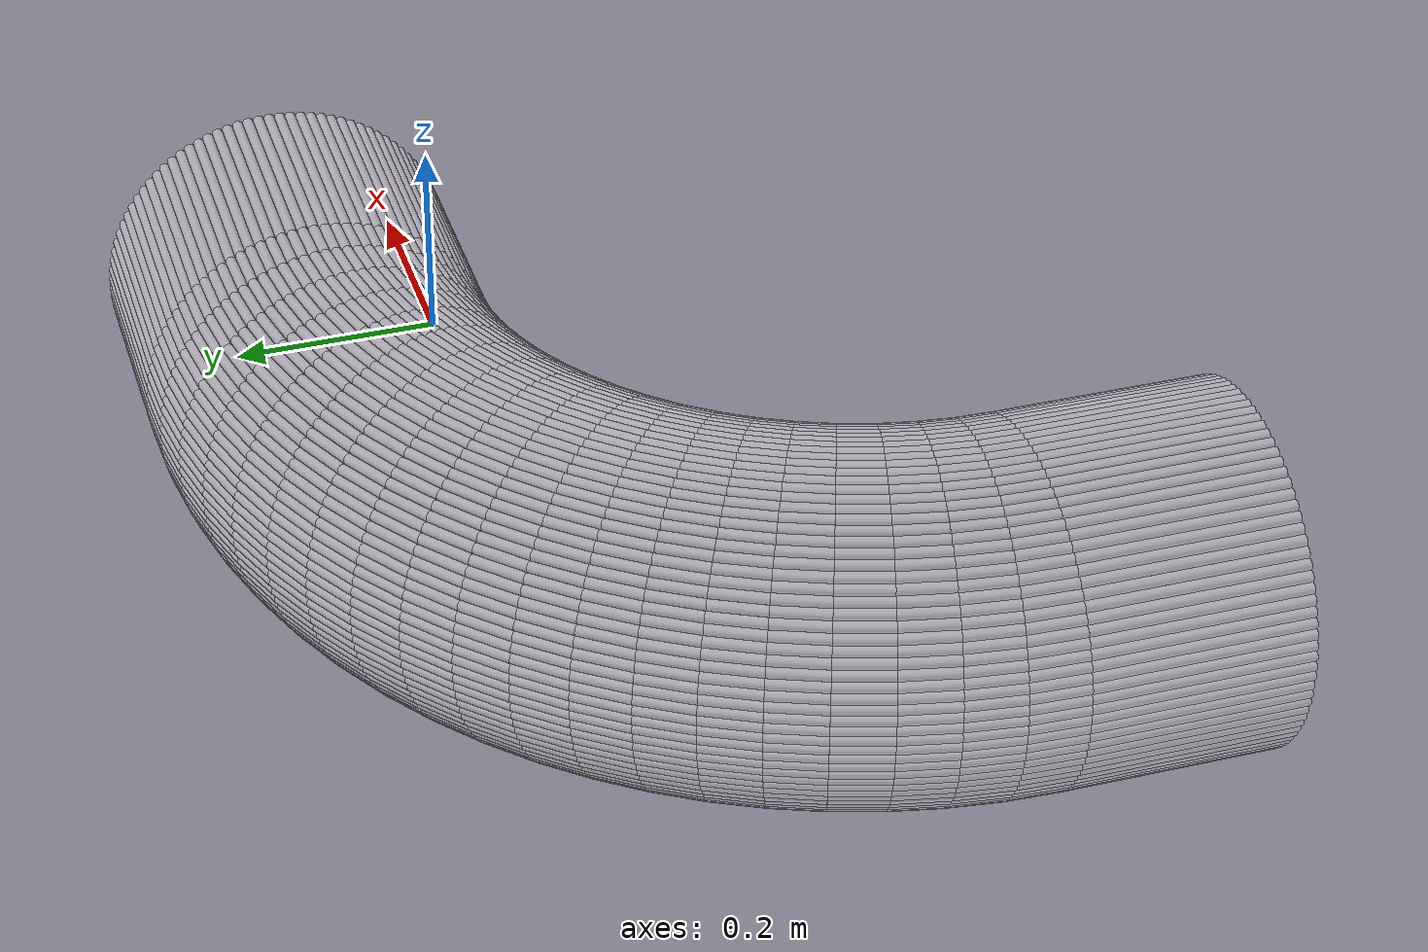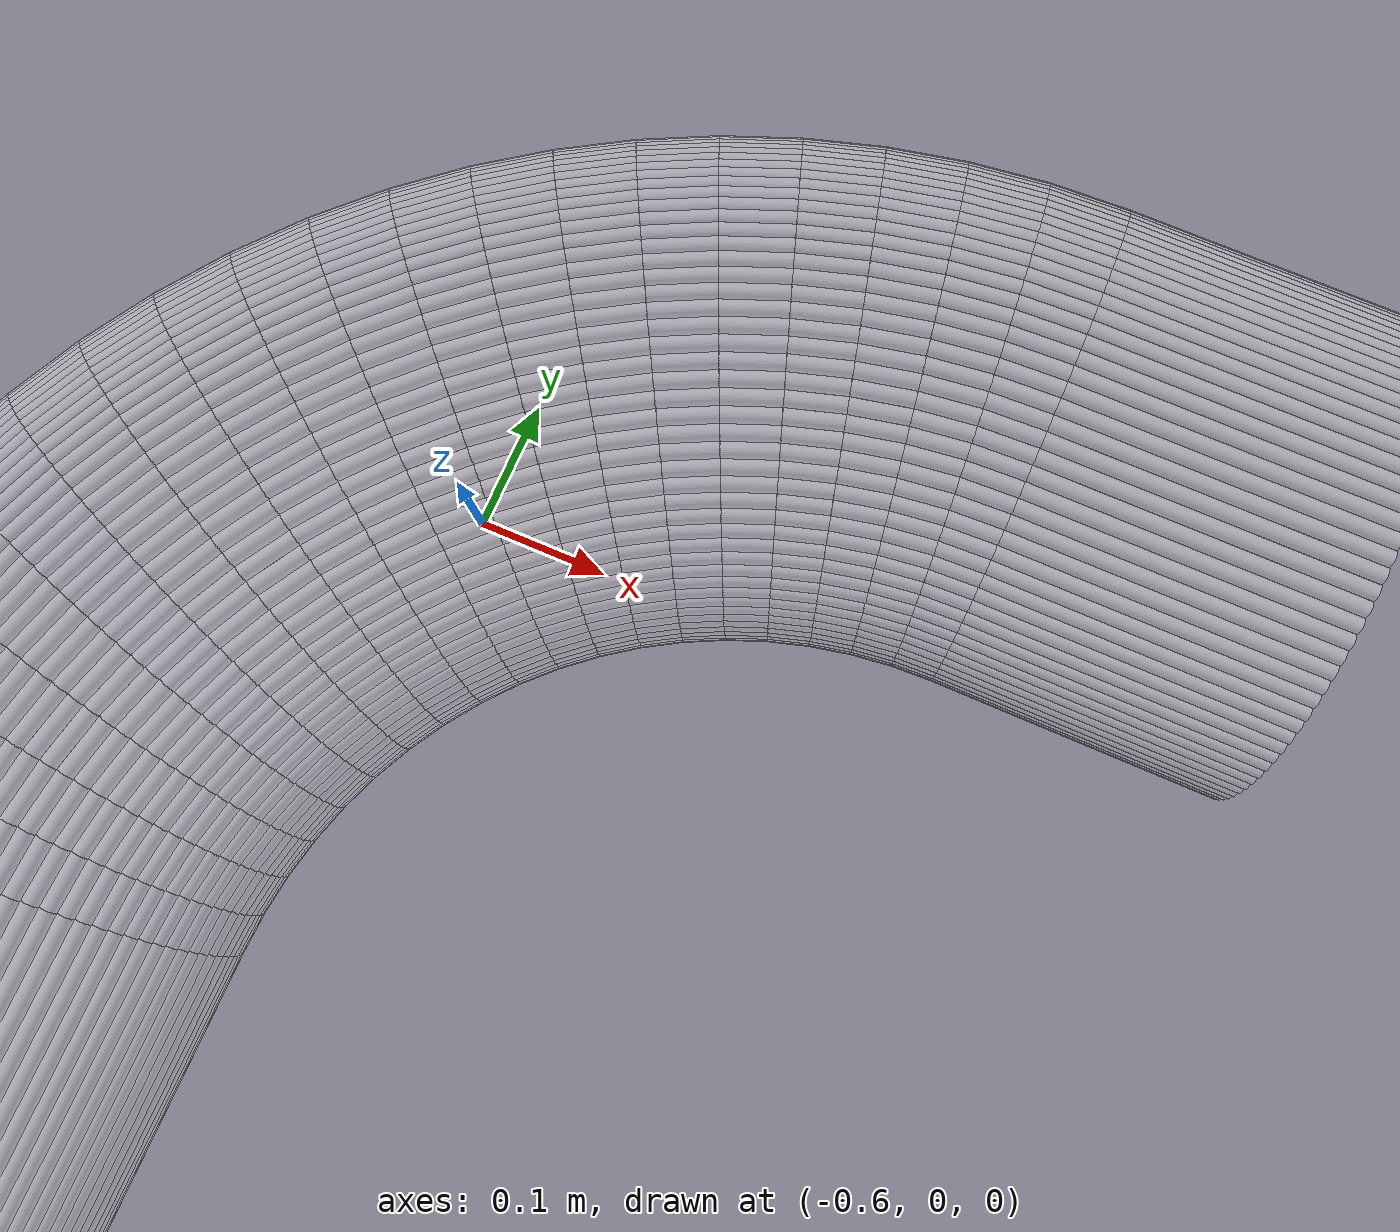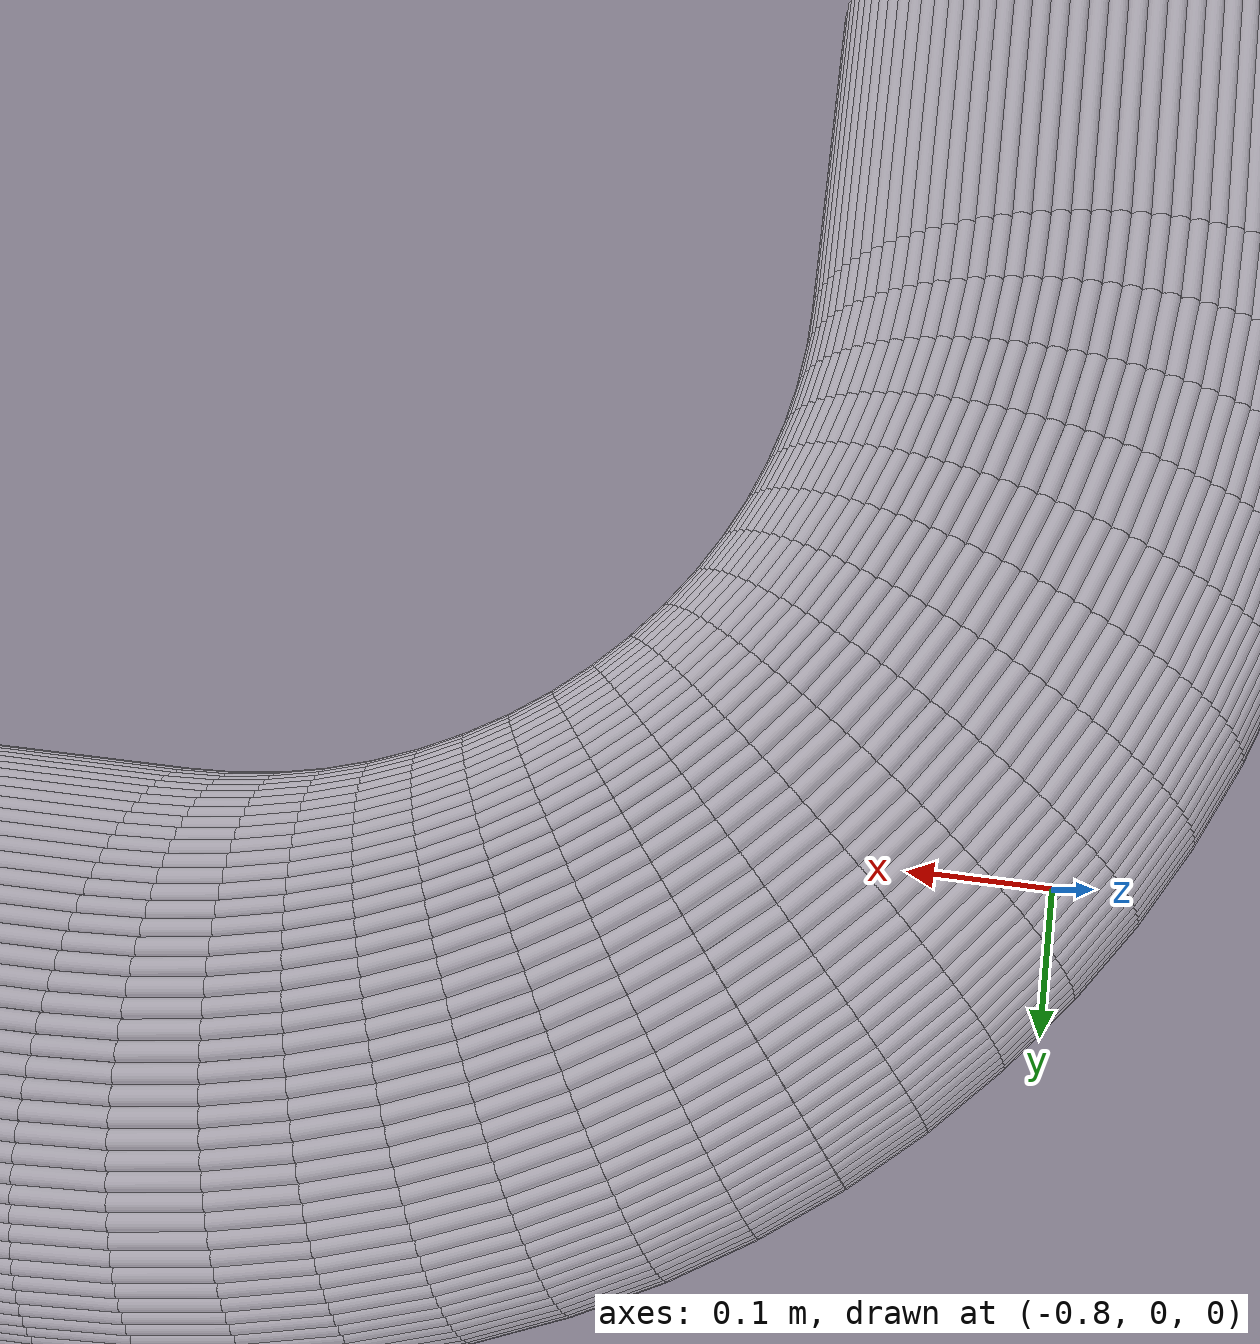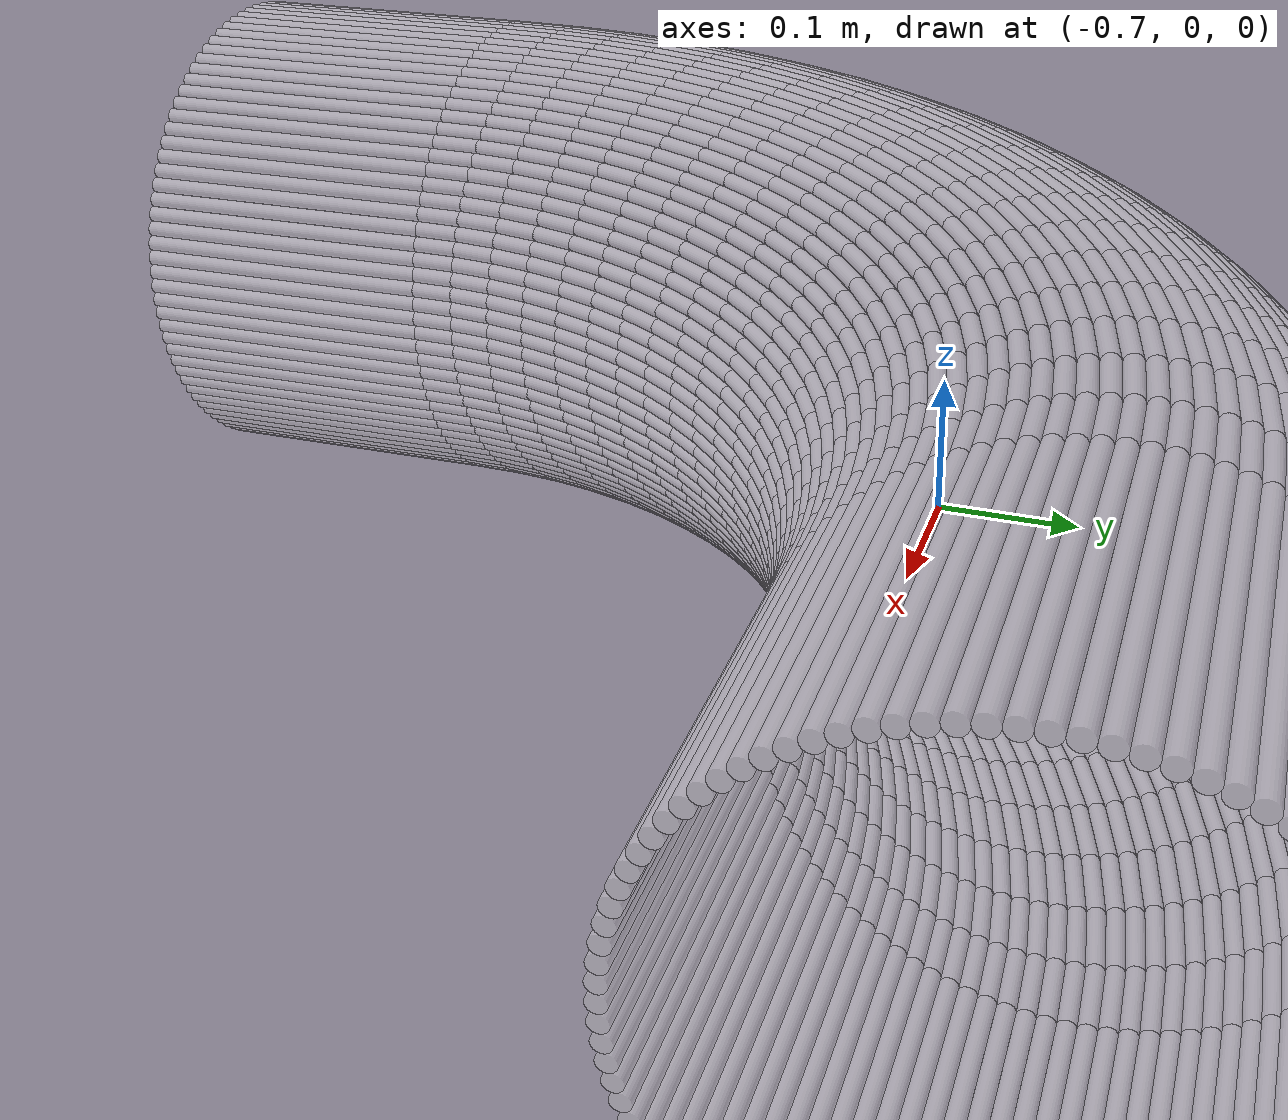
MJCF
<?xml version="1.0" encoding="utf-8"?>
<mujoco>
   <worldbody>
   <body pos="-0.25 -0.34 -0.02" euler="0 0 90">
      <geom euler=" 0 10 0 " fromto="0.66 -0.2 0.16 0.66 0 0.16" rgba="1 1 1 0.35"
            size="0.0050257"
            type="cylinder"/>
      <geom euler=" 0 20 0 " fromto="0.65968 -0.2 0.17005 0.65968 0 0.17005"
            rgba="1 1 1 0.35"
            size="0.0050257"
            type="cylinder"/>
      <geom euler=" 0 30 0 " fromto="0.65874 -0.2 0.18005 0.65874 0 0.18005"
            rgba="1 1 1 0.35"
            size="0.0050257"
            type="cylinder"/>
      <geom euler=" 0 40 0 " fromto="0.65717 -0.2 0.18998 0.65717 0 0.18998"
            rgba="1 1 1 0.35"
            size="0.0050257"
            type="cylinder"/>
      <geom euler=" 0 50 0 " fromto="0.65497 -0.2 0.19979 0.65497 0 0.19979"
            rgba="1 1 1 0.35"
            size="0.0050257"
            type="cylinder"/>
      <geom euler=" 0 60 0 " fromto="0.65217 -0.2 0.20944 0.65217 0 0.20944"
            rgba="1 1 1 0.35"
            size="0.0050257"
            type="cylinder"/>
      <geom euler=" 0 70 0 " fromto="0.64876 -0.2 0.2189 0.64876 0 0.2189"
            rgba="1 1 1 0.35"
            size="0.0050257"
            type="cylinder"/>
      <geom euler=" 0 80 0 " fromto="0.64477 -0.2 0.22812 0.64477 0 0.22812"
            rgba="1 1 1 0.35"
            size="0.0050257"
            type="cylinder"/>
      <geom euler=" 0 90 0 " fromto="0.64021 -0.2 0.23708 0.64021 0 0.23708"
            rgba="1 1 1 0.35"
            size="0.0050257"
            type="cylinder"/>
      <geom euler=" 0 100 0 " fromto="0.63509 -0.2 0.24573 0.63509 0 0.24573"
            rgba="1 1 1 0.35"
            size="0.0050257"
            type="cylinder"/>
      <geom euler=" 0 110 0 " fromto="0.62944 -0.2 0.25405 0.62944 0 0.25405"
            rgba="1 1 1 0.35"
            size="0.0050257"
            type="cylinder"/>
      <geom euler=" 0 120 0 " fromto="0.62328 -0.2 0.26199 0.62328 0 0.26199"
            rgba="1 1 1 0.35"
            size="0.0050257"
            type="cylinder"/>
      <geom euler=" 0 130 0 " fromto="0.61663 -0.2 0.26953 0.61663 0 0.26953"
            rgba="1 1 1 0.35"
            size="0.0050257"
            type="cylinder"/>
      <geom euler=" 0 140 0 " fromto="0.60953 -0.2 0.27663 0.60953 0 0.27663"
            rgba="1 1 1 0.35"
            size="0.0050257"
            type="cylinder"/>
      <geom euler=" 0 150 0 " fromto="0.60199 -0.2 0.28328 0.60199 0 0.28328"
            rgba="1 1 1 0.35"
            size="0.0050257"
            type="cylinder"/>
      <geom euler=" 0 160 0 " fromto="0.59405 -0.2 0.28944 0.59405 0 0.28944"
            rgba="1 1 1 0.35"
            size="0.0050257"
            type="cylinder"/>
      <geom euler=" 0 170 0 " fromto="0.58573 -0.2 0.29509 0.58573 0 0.29509"
            rgba="1 1 1 0.35"
            size="0.0050257"
            type="cylinder"/>
      <geom euler=" 0 180 0 " fromto="0.57708 -0.2 0.30021 0.57708 0 0.30021"
            rgba="1 1 1 0.35"
            size="0.0050257"
            type="cylinder"/>
      <geom euler=" 0 190 0 " fromto="0.56812 -0.2 0.30477 0.56812 0 0.30477"
            rgba="1 1 1 0.35"
            size="0.0050257"
            type="cylinder"/>
      <geom euler=" 0 200 0 " fromto="0.5589 -0.2 0.30876 0.5589 0 0.30876"
            rgba="1 1 1 0.35"
            size="0.0050257"
            type="cylinder"/>
      <geom euler=" 0 210 0 " fromto="0.54944 -0.2 0.31217 0.54944 0 0.31217"
            rgba="1 1 1 0.35"
            size="0.0050257"
            type="cylinder"/>
      <geom euler=" 0 220 0 " fromto="0.53979 -0.2 0.31497 0.53979 0 0.31497"
            rgba="1 1 1 0.35"
            size="0.0050257"
            type="cylinder"/>
      <geom euler=" 0 230 0 " fromto="0.52998 -0.2 0.31717 0.52998 0 0.31717"
            rgba="1 1 1 0.35"
            size="0.0050257"
            type="cylinder"/>
      <geom euler=" 0 240 0 " fromto="0.52005 -0.2 0.31874 0.52005 0 0.31874"
            rgba="1 1 1 0.35"
            size="0.0050257"
            type="cylinder"/>
      <geom euler=" 0 250 0 " fromto="0.51005 -0.2 0.31968 0.51005 0 0.31968"
            rgba="1 1 1 0.35"
            size="0.0050257"
            type="cylinder"/>
      <geom euler=" 0 260 0 " fromto="0.5 -0.2 0.32 0.5 0 0.32" rgba="1 1 1 0.35"
            size="0.0050257"
            type="cylinder"/>
      <geom euler=" 0 270 0 " fromto="0.48995 -0.2 0.31968 0.48995 0 0.31968"
            rgba="1 1 1 0.35"
            size="0.0050257"
            type="cylinder"/>
      <geom euler=" 0 280 0 " fromto="0.47995 -0.2 0.31874 0.47995 0 0.31874"
            rgba="1 1 1 0.35"
            size="0.0050257"
            type="cylinder"/>
      <geom euler=" 0 290 0 " fromto="0.47002 -0.2 0.31717 0.47002 0 0.31717"
            rgba="1 1 1 0.35"
            size="0.0050257"
            type="cylinder"/>
      <geom euler=" 0 300 0 " fromto="0.46021 -0.2 0.31497 0.46021 0 0.31497"
            rgba="1 1 1 0.35"
            size="0.0050257"
            type="cylinder"/>
      <geom euler=" 0 310 0 " fromto="0.45056 -0.2 0.31217 0.45056 0 0.31217"
            rgba="1 1 1 0.35"
            size="0.0050257"
            type="cylinder"/>
      <geom euler=" 0 320 0 " fromto="0.4411 -0.2 0.30876 0.4411 0 0.30876"
            rgba="1 1 1 0.35"
            size="0.0050257"
            type="cylinder"/>
      <geom euler=" 0 330 0 " fromto="0.43188 -0.2 0.30477 0.43188 0 0.30477"
            rgba="1 1 1 0.35"
            size="0.0050257"
            type="cylinder"/>
      <geom euler=" 0 340 0 " fromto="0.42292 -0.2 0.30021 0.42292 0 0.30021"
            rgba="1 1 1 0.35"
            size="0.0050257"
            type="cylinder"/>
      <geom euler=" 0 350 0 " fromto="0.41427 -0.2 0.29509 0.41427 0 0.29509"
            rgba="1 1 1 0.35"
            size="0.0050257"
            type="cylinder"/>
      <geom euler=" 0 360 0 " fromto="0.40595 -0.2 0.28944 0.40595 0 0.28944"
            rgba="1 1 1 0.35"
            size="0.0050257"
            type="cylinder"/>
      <geom euler=" 0 370 0 " fromto="0.39801 -0.2 0.28328 0.39801 0 0.28328"
            rgba="1 1 1 0.35"
            size="0.0050257"
            type="cylinder"/>
      <geom euler=" 0 380 0 " fromto="0.39047 -0.2 0.27663 0.39047 0 0.27663"
            rgba="1 1 1 0.35"
            size="0.0050257"
            type="cylinder"/>
      <geom euler=" 0 390 0 " fromto="0.38337 -0.2 0.26953 0.38337 0 0.26953"
            rgba="1 1 1 0.35"
            size="0.0050257"
            type="cylinder"/>
      <geom euler=" 0 400 0 " fromto="0.37672 -0.2 0.26199 0.37672 0 0.26199"
            rgba="1 1 1 0.35"
            size="0.0050257"
            type="cylinder"/>
      <geom euler=" 0 410 0 " fromto="0.37056 -0.2 0.25405 0.37056 0 0.25405"
            rgba="1 1 1 0.35"
            size="0.0050257"
            type="cylinder"/>
      <geom euler=" 0 420 0 " fromto="0.36491 -0.2 0.24573 0.36491 0 0.24573"
            rgba="1 1 1 0.35"
            size="0.0050257"
            type="cylinder"/>
      <geom euler=" 0 430 0 " fromto="0.35979 -0.2 0.23708 0.35979 0 0.23708"
            rgba="1 1 1 0.35"
            size="0.0050257"
            type="cylinder"/>
      <geom euler=" 0 440 0 " fromto="0.35523 -0.2 0.22812 0.35523 0 0.22812"
            rgba="1 1 1 0.35"
            size="0.0050257"
            type="cylinder"/>
      <geom euler=" 0 450 0 " fromto="0.35124 -0.2 0.2189 0.35124 0 0.2189"
            rgba="1 1 1 0.35"
            size="0.0050257"
            type="cylinder"/>
      <geom euler=" 0 460 0 " fromto="0.34783 -0.2 0.20944 0.34783 0 0.20944"
            rgba="1 1 1 0.35"
            size="0.0050257"
            type="cylinder"/>
      <geom euler=" 0 470 0 " fromto="0.34503 -0.2 0.19979 0.34503 0 0.19979"
            rgba="1 1 1 0.35"
            size="0.0050257"
            type="cylinder"/>
      <geom euler=" 0 480 0 " fromto="0.34283 -0.2 0.18998 0.34283 0 0.18998"
            rgba="1 1 1 0.35"
            size="0.0050257"
            type="cylinder"/>
      <geom euler=" 0 490 0 " fromto="0.34126 -0.2 0.18005 0.34126 0 0.18005"
            rgba="1 1 1 0.35"
            size="0.0050257"
            type="cylinder"/>
      <geom euler=" 0 500 0 " fromto="0.34032 -0.2 0.17005 0.34032 0 0.17005"
            rgba="1 1 1 0.35"
            size="0.0050257"
            type="cylinder"/>
      <geom euler=" 0 510 0 " fromto="0.34 -0.2 0.16 0.34 0 0.16" rgba="1 1 1 0.35"
            size="0.0050257"
            type="cylinder"/>
      <geom euler=" 0 520 0 " fromto="0.34032 -0.2 0.14995 0.34032 0 0.14995"
            rgba="1 1 1 0.35"
            size="0.0050257"
            type="cylinder"/>
      <geom euler=" 0 530 0 " fromto="0.34126 -0.2 0.13995 0.34126 0 0.13995"
            rgba="1 1 1 0.35"
            size="0.0050257"
            type="cylinder"/>
      <geom euler=" 0 540 0 " fromto="0.34283 -0.2 0.13002 0.34283 0 0.13002"
            rgba="1 1 1 0.35"
            size="0.0050257"
            type="cylinder"/>
      <geom euler=" 0 550 0 " fromto="0.34503 -0.2 0.12021 0.34503 0 0.12021"
            rgba="1 1 1 0.35"
            size="0.0050257"
            type="cylinder"/>
      <geom euler=" 0 560 0 " fromto="0.34783 -0.2 0.11056 0.34783 0 0.11056"
            rgba="1 1 1 0.35"
            size="0.0050257"
            type="cylinder"/>
      <geom euler=" 0 570 0 " fromto="0.35124 -0.2 0.1011 0.35124 0 0.1011"
            rgba="1 1 1 0.35"
            size="0.0050257"
            type="cylinder"/>
      <geom euler=" 0 580 0 " fromto="0.35523 -0.2 0.091875 0.35523 0 0.091875"
            rgba="1 1 1 0.35"
            size="0.0050257"
            type="cylinder"/>
      <geom euler=" 0 590 0 " fromto="0.35979 -0.2 0.082919 0.35979 0 0.082919"
            rgba="1 1 1 0.35"
            size="0.0050257"
            type="cylinder"/>
      <geom euler=" 0 600 0 " fromto="0.36491 -0.2 0.074268 0.36491 0 0.074268"
            rgba="1 1 1 0.35"
            size="0.0050257"
            type="cylinder"/>
      <geom euler=" 0 610 0 " fromto="0.37056 -0.2 0.065954 0.37056 0 0.065954"
            rgba="1 1 1 0.35"
            size="0.0050257"
            type="cylinder"/>
      <geom euler=" 0 620 0 " fromto="0.37672 -0.2 0.058012 0.37672 0 0.058012"
            rgba="1 1 1 0.35"
            size="0.0050257"
            type="cylinder"/>
      <geom euler=" 0 630 0 " fromto="0.38337 -0.2 0.050472 0.38337 0 0.050472"
            rgba="1 1 1 0.35"
            size="0.0050257"
            type="cylinder"/>
      <geom euler=" 0 640 0 " fromto="0.39047 -0.2 0.043365 0.39047 0 0.043365"
            rgba="1 1 1 0.35"
            size="0.0050257"
            type="cylinder"/>
      <geom euler=" 0 650 0 " fromto="0.39801 -0.2 0.036718 0.39801 0 0.036718"
            rgba="1 1 1 0.35"
            size="0.0050257"
            type="cylinder"/>
      <geom euler=" 0 660 0 " fromto="0.40595 -0.2 0.030557 0.40595 0 0.030557"
            rgba="1 1 1 0.35"
            size="0.0050257"
            type="cylinder"/>
      <geom euler=" 0 670 0 " fromto="0.41427 -0.2 0.024908 0.41427 0 0.024908"
            rgba="1 1 1 0.35"
            size="0.0050257"
            type="cylinder"/>
      <geom euler=" 0 680 0 " fromto="0.42292 -0.2 0.019791 0.42292 0 0.019791"
            rgba="1 1 1 0.35"
            size="0.0050257"
            type="cylinder"/>
      <geom euler=" 0 690 0 " fromto="0.43188 -0.2 0.015228 0.43188 0 0.015228"
            rgba="1 1 1 0.35"
            size="0.0050257"
            type="cylinder"/>
      <geom euler=" 0 700 0 " fromto="0.4411 -0.2 0.011236 0.4411 0 0.011236"
            rgba="1 1 1 0.35"
            size="0.0050257"
            type="cylinder"/>
      <geom euler=" 0 710 0 " fromto="0.45056 -0.2 0.007831 0.45056 0 0.007831"
            rgba="1 1 1 0.35"
            size="0.0050257"
            type="cylinder"/>
      <geom euler=" 0 720 0 " fromto="0.46021 -0.2 0.0050267 0.46021 0 0.0050267"
            rgba="1 1 1 0.35"
            size="0.0050257"
            type="cylinder"/>
      <geom euler=" 0 730 0 " fromto="0.47002 -0.2 0.002834 0.47002 0 0.002834"
            rgba="1 1 1 0.35"
            size="0.0050257"
            type="cylinder"/>
      <geom euler=" 0 740 0 " fromto="0.47995 -0.2 0.0012616 0.47995 0 0.0012616"
            rgba="1 1 1 0.35"
            size="0.0050257"
            type="cylinder"/>
      <geom euler=" 0 750 0 " fromto="0.48995 -0.2 0.00031572 0.48995 0 0.00031572"
            rgba="1 1 1 0.35"
            size="0.0050257"
            type="cylinder"/>
      <geom euler=" 0 760 0 " fromto="0.5 -0.2 0 0.5 0 0" rgba="1 1 1 0.35"
            size="0.0050257"
            type="cylinder"/>
      <geom euler=" 0 770 0 " fromto="0.51005 -0.2 0.00031572 0.51005 0 0.00031572"
            rgba="1 1 1 0.35"
            size="0.0050257"
            type="cylinder"/>
      <geom euler=" 0 780 0 " fromto="0.52005 -0.2 0.0012616 0.52005 0 0.0012616"
            rgba="1 1 1 0.35"
            size="0.0050257"
            type="cylinder"/>
      <geom euler=" 0 790 0 " fromto="0.52998 -0.2 0.002834 0.52998 0 0.002834"
            rgba="1 1 1 0.35"
            size="0.0050257"
            type="cylinder"/>
      <geom euler=" 0 800 0 " fromto="0.53979 -0.2 0.0050267 0.53979 0 0.0050267"
            rgba="1 1 1 0.35"
            size="0.0050257"
            type="cylinder"/>
      <geom euler=" 0 810 0 " fromto="0.54944 -0.2 0.007831 0.54944 0 0.007831"
            rgba="1 1 1 0.35"
            size="0.0050257"
            type="cylinder"/>
      <geom euler=" 0 820 0 " fromto="0.5589 -0.2 0.011236 0.5589 0 0.011236"
            rgba="1 1 1 0.35"
            size="0.0050257"
            type="cylinder"/>
      <geom euler=" 0 830 0 " fromto="0.56812 -0.2 0.015228 0.56812 0 0.015228"
            rgba="1 1 1 0.35"
            size="0.0050257"
            type="cylinder"/>
      <geom euler=" 0 840 0 " fromto="0.57708 -0.2 0.019791 0.57708 0 0.019791"
            rgba="1 1 1 0.35"
            size="0.0050257"
            type="cylinder"/>
      <geom euler=" 0 850 0 " fromto="0.58573 -0.2 0.024908 0.58573 0 0.024908"
            rgba="1 1 1 0.35"
            size="0.0050257"
            type="cylinder"/>
      <geom euler=" 0 860 0 " fromto="0.59405 -0.2 0.030557 0.59405 0 0.030557"
            rgba="1 1 1 0.35"
            size="0.0050257"
            type="cylinder"/>
      <geom euler=" 0 870 0 " fromto="0.60199 -0.2 0.036718 0.60199 0 0.036718"
            rgba="1 1 1 0.35"
            size="0.0050257"
            type="cylinder"/>
      <geom euler=" 0 880 0 " fromto="0.60953 -0.2 0.043365 0.60953 0 0.043365"
            rgba="1 1 1 0.35"
            size="0.0050257"
            type="cylinder"/>
      <geom euler=" 0 890 0 " fromto="0.61663 -0.2 0.050472 0.61663 0 0.050472"
            rgba="1 1 1 0.35"
            size="0.0050257"
            type="cylinder"/>
      <geom euler=" 0 900 0 " fromto="0.62328 -0.2 0.058012 0.62328 0 0.058012"
            rgba="1 1 1 0.35"
            size="0.0050257"
            type="cylinder"/>
      <geom euler=" 0 910 0 " fromto="0.62944 -0.2 0.065954 0.62944 0 0.065954"
            rgba="1 1 1 0.35"
            size="0.0050257"
            type="cylinder"/>
      <geom euler=" 0 920 0 " fromto="0.63509 -0.2 0.074268 0.63509 0 0.074268"
            rgba="1 1 1 0.35"
            size="0.0050257"
            type="cylinder"/>
      <geom euler=" 0 930 0 " fromto="0.64021 -0.2 0.082919 0.64021 0 0.082919"
            rgba="1 1 1 0.35"
            size="0.0050257"
            type="cylinder"/>
      <geom euler=" 0 940 0 " fromto="0.64477 -0.2 0.091875 0.64477 0 0.091875"
            rgba="1 1 1 0.35"
            size="0.0050257"
            type="cylinder"/>
      <geom euler=" 0 950 0 " fromto="0.64876 -0.2 0.1011 0.64876 0 0.1011"
            rgba="1 1 1 0.35"
            size="0.0050257"
            type="cylinder"/>
      <geom euler=" 0 960 0 " fromto="0.65217 -0.2 0.11056 0.65217 0 0.11056"
            rgba="1 1 1 0.35"
            size="0.0050257"
            type="cylinder"/>
      <geom euler=" 0 970 0 " fromto="0.65497 -0.2 0.12021 0.65497 0 0.12021"
            rgba="1 1 1 0.35"
            size="0.0050257"
            type="cylinder"/>
      <geom euler=" 0 980 0 " fromto="0.65717 -0.2 0.13002 0.65717 0 0.13002"
            rgba="1 1 1 0.35"
            size="0.0050257"
            type="cylinder"/>
      <geom euler=" 0 990 0 " fromto="0.65874 -0.2 0.13995 0.65874 0 0.13995"
            rgba="1 1 1 0.35"
            size="0.0050257"
            type="cylinder"/>
      <geom euler=" 0 1000 0 " fromto="0.65968 -0.2 0.14995 0.65968 0 0.14995"
            rgba="1 1 1 0.35"
            size="0.0050257"
            type="cylinder"/>
      <geom euler=" 0 10 0 " fromto="0.66 0 0.16 0.65775 0.054502 0.16" rgba="1 1 1 0.35"
            size="0.0050257"
            type="cylinder"/>
      <geom euler=" 0 20 0 " fromto="0.65968 0 0.17005 0.65743 0.054476 0.17005"
            rgba="1 1 1 0.35"
            size="0.0050257"
            type="cylinder"/>
      <geom euler=" 0 30 0 " fromto="0.65874 0 0.18005 0.65649 0.054398 0.18005"
            rgba="1 1 1 0.35"
            size="0.0050257"
            type="cylinder"/>
      <geom euler=" 0 40 0 " fromto="0.65717 0 0.18998 0.65492 0.054268 0.18998"
            rgba="1 1 1 0.35"
            size="0.0050257"
            type="cylinder"/>
      <geom euler=" 0 50 0 " fromto="0.65497 0 0.19979 0.65274 0.054087 0.19979"
            rgba="1 1 1 0.35"
            size="0.0050257"
            type="cylinder"/>
      <geom euler=" 0 60 0 " fromto="0.65217 0 0.20944 0.64994 0.053856 0.20944"
            rgba="1 1 1 0.35"
            size="0.0050257"
            type="cylinder"/>
      <geom euler=" 0 70 0 " fromto="0.64876 0 0.2189 0.64655 0.053575 0.2189"
            rgba="1 1 1 0.35"
            size="0.0050257"
            type="cylinder"/>
      <geom euler=" 0 80 0 " fromto="0.64477 0 0.22812 0.64257 0.053245 0.22812"
            rgba="1 1 1 0.35"
            size="0.0050257"
            type="cylinder"/>
      <geom euler=" 0 90 0 " fromto="0.64021 0 0.23708 0.63802 0.052868 0.23708"
            rgba="1 1 1 0.35"
            size="0.0050257"
            type="cylinder"/>
      <geom euler=" 0 100 0 " fromto="0.63509 0 0.24573 0.63292 0.052446 0.24573"
            rgba="1 1 1 0.35"
            size="0.0050257"
            type="cylinder"/>
      <geom euler=" 0 110 0 " fromto="0.62944 0 0.25405 0.62729 0.051979 0.25405"
            rgba="1 1 1 0.35"
            size="0.0050257"
            type="cylinder"/>
      <geom euler=" 0 120 0 " fromto="0.62328 0 0.26199 0.62115 0.05147 0.26199"
            rgba="1 1 1 0.35"
            size="0.0050257"
            type="cylinder"/>
      <geom euler=" 0 130 0 " fromto="0.61663 0 0.26953 0.61453 0.050921 0.26953"
            rgba="1 1 1 0.35"
            size="0.0050257"
            type="cylinder"/>
      <geom euler=" 0 140 0 " fromto="0.60953 0 0.27663 0.60745 0.050334 0.27663"
            rgba="1 1 1 0.35"
            size="0.0050257"
            type="cylinder"/>
      <geom euler=" 0 150 0 " fromto="0.60199 0 0.28328 0.59993 0.049712 0.28328"
            rgba="1 1 1 0.35"
            size="0.0050257"
            type="cylinder"/>
      <geom euler=" 0 160 0 " fromto="0.59405 0 0.28944 0.59202 0.049056 0.28944"
            rgba="1 1 1 0.35"
            size="0.0050257"
            type="cylinder"/>
      <geom euler=" 0 170 0 " fromto="0.58573 0 0.29509 0.58373 0.048369 0.29509"
            rgba="1 1 1 0.35"
            size="0.0050257"
            type="cylinder"/>
      <geom euler=" 0 180 0 " fromto="0.57708 0 0.30021 0.57511 0.047655 0.30021"
            rgba="1 1 1 0.35"
            size="0.0050257"
            type="cylinder"/>
      <geom euler=" 0 190 0 " fromto="0.56812 0 0.30477 0.56618 0.046915 0.30477"
            rgba="1 1 1 0.35"
            size="0.0050257"
            type="cylinder"/>
      <geom euler=" 0 200 0 " fromto="0.5589 0 0.30876 0.55699 0.046154 0.30876"
            rgba="1 1 1 0.35"
            size="0.0050257"
            type="cylinder"/>
      <geom euler=" 0 210 0 " fromto="0.54944 0 0.31217 0.54757 0.045373 0.31217"
            rgba="1 1 1 0.35"
            size="0.0050257"
            type="cylinder"/>
      <geom euler=" 0 220 0 " fromto="0.53979 0 0.31497 0.53795 0.044576 0.31497"
            rgba="1 1 1 0.35"
            size="0.0050257"
            type="cylinder"/>
      <geom euler=" 0 230 0 " fromto="0.52998 0 0.31717 0.52817 0.043765 0.31717"
            rgba="1 1 1 0.35"
            size="0.0050257"
            type="cylinder"/>
      <geom euler=" 0 240 0 " fromto="0.52005 0 0.31874 0.51828 0.042946 0.31874"
            rgba="1 1 1 0.35"
            size="0.0050257"
            type="cylinder"/>
      <geom euler=" 0 250 0 " fromto="0.51005 0 0.31968 0.5083 0.042119 0.31968"
            rgba="1 1 1 0.35"
            size="0.0050257"
            type="cylinder"/>
      <geom euler=" 0 260 0 " fromto="0.5 0 0.32 0.49829 0.04129 0.32" rgba="1 1 1 0.35"
            size="0.0050257"
            type="cylinder"/>
      <geom euler=" 0 270 0 " fromto="0.48995 0 0.31968 0.48828 0.04046 0.31968"
            rgba="1 1 1 0.35"
            size="0.0050257"
            type="cylinder"/>
      <geom euler=" 0 280 0 " fromto="0.47995 0 0.31874 0.47831 0.039634 0.31874"
            rgba="1 1 1 0.35"
            size="0.0050257"
            type="cylinder"/>
      <geom euler=" 0 290 0 " fromto="0.47002 0 0.31717 0.46841 0.038814 0.31717"
            rgba="1 1 1 0.35"
            size="0.0050257"
            type="cylinder"/>
      <geom euler=" 0 300 0 " fromto="0.46021 0 0.31497 0.45864 0.038004 0.31497"
            rgba="1 1 1 0.35"
            size="0.0050257"
            type="cylinder"/>
      <geom euler=" 0 310 0 " fromto="0.45056 0 0.31217 0.44902 0.037207 0.31217"
            rgba="1 1 1 0.35"
            size="0.0050257"
            type="cylinder"/>
      <geom euler=" 0 320 0 " fromto="0.4411 0 0.30876 0.43959 0.036426 0.30876"
            rgba="1 1 1 0.35"
            size="0.0050257"
            type="cylinder"/>
      <geom euler=" 0 330 0 " fromto="0.43188 0 0.30477 0.4304 0.035664 0.30477"
            rgba="1 1 1 0.35"
            size="0.0050257"
            type="cylinder"/>
      <geom euler=" 0 340 0 " fromto="0.42292 0 0.30021 0.42147 0.034924 0.30021"
            rgba="1 1 1 0.35"
            size="0.0050257"
            type="cylinder"/>
      <geom euler=" 0 350 0 " fromto="0.41427 0 0.29509 0.41285 0.03421 0.29509"
            rgba="1 1 1 0.35"
            size="0.0050257"
            type="cylinder"/>
      <geom euler=" 0 360 0 " fromto="0.40595 0 0.28944 0.40457 0.033523 0.28944"
            rgba="1 1 1 0.35"
            size="0.0050257"
            type="cylinder"/>
      <geom euler=" 0 370 0 " fromto="0.39801 0 0.28328 0.39665 0.032868 0.28328"
            rgba="1 1 1 0.35"
            size="0.0050257"
            type="cylinder"/>
      <geom euler=" 0 380 0 " fromto="0.39047 0 0.27663 0.38914 0.032245 0.27663"
            rgba="1 1 1 0.35"
            size="0.0050257"
            type="cylinder"/>
      <geom euler=" 0 390 0 " fromto="0.38337 0 0.26953 0.38206 0.031658 0.26953"
            rgba="1 1 1 0.35"
            size="0.0050257"
            type="cylinder"/>
      <geom euler=" 0 400 0 " fromto="0.37672 0 0.26199 0.37543 0.031109 0.26199"
            rgba="1 1 1 0.35"
            size="0.0050257"
            type="cylinder"/>
      <geom euler=" 0 410 0 " fromto="0.37056 0 0.25405 0.36929 0.0306 0.25405"
            rgba="1 1 1 0.35"
            size="0.0050257"
            type="cylinder"/>
      <geom euler=" 0 420 0 " fromto="0.36491 0 0.24573 0.36366 0.030134 0.24573"
            rgba="1 1 1 0.35"
            size="0.0050257"
            type="cylinder"/>
      <geom euler=" 0 430 0 " fromto="0.35979 0 0.23708 0.35856 0.029711 0.23708"
            rgba="1 1 1 0.35"
            size="0.0050257"
            type="cylinder"/>
      <geom euler=" 0 440 0 " fromto="0.35523 0 0.22812 0.35401 0.029334 0.22812"
            rgba="1 1 1 0.35"
            size="0.0050257"
            type="cylinder"/>
      <geom euler=" 0 450 0 " fromto="0.35124 0 0.2189 0.35004 0.029005 0.2189"
            rgba="1 1 1 0.35"
            size="0.0050257"
            type="cylinder"/>
      <geom euler=" 0 460 0 " fromto="0.34783 0 0.20944 0.34664 0.028724 0.20944"
            rgba="1 1 1 0.35"
            size="0.0050257"
            type="cylinder"/>
      <geom euler=" 0 470 0 " fromto="0.34503 0 0.19979 0.34385 0.028492 0.19979"
            rgba="1 1 1 0.35"
            size="0.0050257"
            type="cylinder"/>
      <geom euler=" 0 480 0 " fromto="0.34283 0 0.18998 0.34166 0.028311 0.18998"
            rgba="1 1 1 0.35"
            size="0.0050257"
            type="cylinder"/>
      <geom euler=" 0 490 0 " fromto="0.34126 0 0.18005 0.3401 0.028181 0.18005"
            rgba="1 1 1 0.35"
            size="0.0050257"
            type="cylinder"/>
      <geom euler=" 0 500 0 " fromto="0.34032 0 0.17005 0.33915 0.028103 0.17005"
            rgba="1 1 1 0.35"
            size="0.0050257"
            type="cylinder"/>
      <geom euler=" 0 510 0 " fromto="0.34 0 0.16 0.33884 0.028077 0.16" rgba="1 1 1 0.35"
            size="0.0050257"
            type="cylinder"/>
      <geom euler=" 0 520 0 " fromto="0.34032 0 0.14995 0.33915 0.028103 0.14995"
            rgba="1 1 1 0.35"
            size="0.0050257"
            type="cylinder"/>
      <geom euler=" 0 530 0 " fromto="0.34126 0 0.13995 0.3401 0.028181 0.13995"
            rgba="1 1 1 0.35"
            size="0.0050257"
            type="cylinder"/>
      <geom euler=" 0 540 0 " fromto="0.34283 0 0.13002 0.34166 0.028311 0.13002"
            rgba="1 1 1 0.35"
            size="0.0050257"
            type="cylinder"/>
      <geom euler=" 0 550 0 " fromto="0.34503 0 0.12021 0.34385 0.028492 0.12021"
            rgba="1 1 1 0.35"
            size="0.0050257"
            type="cylinder"/>
      <geom euler=" 0 560 0 " fromto="0.34783 0 0.11056 0.34664 0.028724 0.11056"
            rgba="1 1 1 0.35"
            size="0.0050257"
            type="cylinder"/>
      <geom euler=" 0 570 0 " fromto="0.35124 0 0.1011 0.35004 0.029005 0.1011"
            rgba="1 1 1 0.35"
            size="0.0050257"
            type="cylinder"/>
      <geom euler=" 0 580 0 " fromto="0.35523 0 0.091875 0.35401 0.029334 0.091875"
            rgba="1 1 1 0.35"
            size="0.0050257"
            type="cylinder"/>
      <geom euler=" 0 590 0 " fromto="0.35979 0 0.082919 0.35856 0.029711 0.082919"
            rgba="1 1 1 0.35"
            size="0.0050257"
            type="cylinder"/>
      <geom euler=" 0 600 0 " fromto="0.36491 0 0.074268 0.36366 0.030134 0.074268"
            rgba="1 1 1 0.35"
            size="0.0050257"
            type="cylinder"/>
      <geom euler=" 0 610 0 " fromto="0.37056 0 0.065954 0.36929 0.0306 0.065954"
            rgba="1 1 1 0.35"
            size="0.0050257"
            type="cylinder"/>
      <geom euler=" 0 620 0 " fromto="0.37672 0 0.058012 0.37543 0.031109 0.058012"
            rgba="1 1 1 0.35"
            size="0.0050257"
            type="cylinder"/>
      <geom euler=" 0 630 0 " fromto="0.38337 0 0.050472 0.38206 0.031658 0.050472"
            rgba="1 1 1 0.35"
            size="0.0050257"
            type="cylinder"/>
      <geom euler=" 0 640 0 " fromto="0.39047 0 0.043365 0.38914 0.032245 0.043365"
            rgba="1 1 1 0.35"
            size="0.0050257"
            type="cylinder"/>
      <geom euler=" 0 650 0 " fromto="0.39801 0 0.036718 0.39665 0.032868 0.036718"
            rgba="1 1 1 0.35"
            size="0.0050257"
            type="cylinder"/>
      <geom euler=" 0 660 0 " fromto="0.40595 0 0.030557 0.40457 0.033523 0.030557"
            rgba="1 1 1 0.35"
            size="0.0050257"
            type="cylinder"/>
      <geom euler=" 0 670 0 " fromto="0.41427 0 0.024908 0.41285 0.03421 0.024908"
            rgba="1 1 1 0.35"
            size="0.0050257"
            type="cylinder"/>
      <geom euler=" 0 680 0 " fromto="0.42292 0 0.019791 0.42147 0.034924 0.019791"
            rgba="1 1 1 0.35"
            size="0.0050257"
            type="cylinder"/>
      <geom euler=" 0 690 0 " fromto="0.43188 0 0.015228 0.4304 0.035664 0.015228"
            rgba="1 1 1 0.35"
            size="0.0050257"
            type="cylinder"/>
      <geom euler=" 0 700 0 " fromto="0.4411 0 0.011236 0.43959 0.036426 0.011236"
            rgba="1 1 1 0.35"
            size="0.0050257"
            type="cylinder"/>
      <geom euler=" 0 710 0 " fromto="0.45056 0 0.007831 0.44902 0.037207 0.007831"
            rgba="1 1 1 0.35"
            size="0.0050257"
            type="cylinder"/>
      <geom euler=" 0 720 0 " fromto="0.46021 0 0.0050267 0.45864 0.038004 0.0050267"
            rgba="1 1 1 0.35"
            size="0.0050257"
            type="cylinder"/>
      <geom euler=" 0 730 0 " fromto="0.47002 0 0.002834 0.46841 0.038814 0.002834"
            rgba="1 1 1 0.35"
            size="0.0050257"
            type="cylinder"/>
      <geom euler=" 0 740 0 " fromto="0.47995 0 0.0012616 0.47831 0.039634 0.0012616"
            rgba="1 1 1 0.35"
            size="0.0050257"
            type="cylinder"/>
      <geom euler=" 0 750 0 " fromto="0.48995 0 0.00031572 0.48828 0.04046 0.00031572"
            rgba="1 1 1 0.35"
            size="0.0050257"
            type="cylinder"/>
      <geom euler=" 0 760 0 " fromto="0.5 0 0 0.49829 0.04129 0" rgba="1 1 1 0.35"
            size="0.0050257"
            type="cylinder"/>
      <geom euler=" 0 770 0 " fromto="0.51005 0 0.00031572 0.5083 0.042119 0.00031572"
            rgba="1 1 1 0.35"
            size="0.0050257"
            type="cylinder"/>
      <geom euler=" 0 780 0 " fromto="0.52005 0 0.0012616 0.51828 0.042946 0.0012616"
            rgba="1 1 1 0.35"
            size="0.0050257"
            type="cylinder"/>
      <geom euler=" 0 790 0 " fromto="0.52998 0 0.002834 0.52817 0.043765 0.002834"
            rgba="1 1 1 0.35"
            size="0.0050257"
            type="cylinder"/>
      <geom euler=" 0 800 0 " fromto="0.53979 0 0.0050267 0.53795 0.044576 0.0050267"
            rgba="1 1 1 0.35"
            size="0.0050257"
            type="cylinder"/>
      <geom euler=" 0 810 0 " fromto="0.54944 0 0.007831 0.54757 0.045373 0.007831"
            rgba="1 1 1 0.35"
            size="0.0050257"
            type="cylinder"/>
      <geom euler=" 0 820 0 " fromto="0.5589 0 0.011236 0.55699 0.046154 0.011236"
            rgba="1 1 1 0.35"
            size="0.0050257"
            type="cylinder"/>
      <geom euler=" 0 830 0 " fromto="0.56812 0 0.015228 0.56618 0.046915 0.015228"
            rgba="1 1 1 0.35"
            size="0.0050257"
            type="cylinder"/>
      <geom euler=" 0 840 0 " fromto="0.57708 0 0.019791 0.57511 0.047655 0.019791"
            rgba="1 1 1 0.35"
            size="0.0050257"
            type="cylinder"/>
      <geom euler=" 0 850 0 " fromto="0.58573 0 0.024908 0.58373 0.048369 0.024908"
            rgba="1 1 1 0.35"
            size="0.0050257"
            type="cylinder"/>
      <geom euler=" 0 860 0 " fromto="0.59405 0 0.030557 0.59202 0.049056 0.030557"
            rgba="1 1 1 0.35"
            size="0.0050257"
            type="cylinder"/>
      <geom euler=" 0 870 0 " fromto="0.60199 0 0.036718 0.59993 0.049712 0.036718"
            rgba="1 1 1 0.35"
            size="0.0050257"
            type="cylinder"/>
      <geom euler=" 0 880 0 " fromto="0.60953 0 0.043365 0.60745 0.050334 0.043365"
            rgba="1 1 1 0.35"
            size="0.0050257"
            type="cylinder"/>
      <geom euler=" 0 890 0 " fromto="0.61663 0 0.050472 0.61453 0.050921 0.050472"
            rgba="1 1 1 0.35"
            size="0.0050257"
            type="cylinder"/>
      <geom euler=" 0 900 0 " fromto="0.62328 0 0.058012 0.62115 0.05147 0.058012"
            rgba="1 1 1 0.35"
            size="0.0050257"
            type="cylinder"/>
      <geom euler=" 0 910 0 " fromto="0.62944 0 0.065954 0.62729 0.051979 0.065954"
            rgba="1 1 1 0.35"
            size="0.0050257"
            type="cylinder"/>
      <geom euler=" 0 920 0 " fromto="0.63509 0 0.074268 0.63292 0.052446 0.074268"
            rgba="1 1 1 0.35"
            size="0.0050257"
            type="cylinder"/>
      <geom euler=" 0 930 0 " fromto="0.64021 0 0.082919 0.63802 0.052868 0.082919"
            rgba="1 1 1 0.35"
            size="0.0050257"
            type="cylinder"/>
      <geom euler=" 0 940 0 " fromto="0.64477 0 0.091875 0.64257 0.053245 0.091875"
            rgba="1 1 1 0.35"
            size="0.0050257"
            type="cylinder"/>
      <geom euler=" 0 950 0 " fromto="0.64876 0 0.1011 0.64655 0.053575 0.1011"
            rgba="1 1 1 0.35"
            size="0.0050257"
            type="cylinder"/>
      <geom euler=" 0 960 0 " fromto="0.65217 0 0.11056 0.64994 0.053856 0.11056"
            rgba="1 1 1 0.35"
            size="0.0050257"
            type="cylinder"/>
      <geom euler=" 0 970 0 " fromto="0.65497 0 0.12021 0.65274 0.054087 0.12021"
            rgba="1 1 1 0.35"
            size="0.0050257"
            type="cylinder"/>
      <geom euler=" 0 980 0 " fromto="0.65717 0 0.13002 0.65492 0.054268 0.13002"
            rgba="1 1 1 0.35"
            size="0.0050257"
            type="cylinder"/>
      <geom euler=" 0 990 0 " fromto="0.65874 0 0.13995 0.65649 0.054398 0.13995"
            rgba="1 1 1 0.35"
            size="0.0050257"
            type="cylinder"/>
      <geom euler=" 0 1000 0 " fromto="0.65968 0 0.14995 0.65743 0.054476 0.14995"
            rgba="1 1 1 0.35"
            size="0.0050257"
            type="cylinder"/>
      <geom euler=" 0 10 0 " fromto="0.65775 0.054502 0.16 0.651 0.10863 0.16"
            rgba="1 1 1 0.35"
            size="0.0050257"
            type="cylinder"/>
      <geom euler=" 0 20 0 " fromto="0.65743 0.054476 0.17005 0.65069 0.10858 0.17005"
            rgba="1 1 1 0.35"
            size="0.0050257"
            type="cylinder"/>
      <geom euler=" 0 30 0 " fromto="0.65649 0.054398 0.18005 0.64975 0.10842 0.18005"
            rgba="1 1 1 0.35"
            size="0.0050257"
            type="cylinder"/>
      <geom euler=" 0 40 0 " fromto="0.65492 0.054268 0.18998 0.6482 0.10817 0.18998"
            rgba="1 1 1 0.35"
            size="0.0050257"
            type="cylinder"/>
      <geom euler=" 0 50 0 " fromto="0.65274 0.054087 0.19979 0.64604 0.10781 0.19979"
            rgba="1 1 1 0.35"
            size="0.0050257"
            type="cylinder"/>
      <geom euler=" 0 60 0 " fromto="0.64994 0.053856 0.20944 0.64327 0.10734 0.20944"
            rgba="1 1 1 0.35"
            size="0.0050257"
            type="cylinder"/>
      <geom euler=" 0 70 0 " fromto="0.64655 0.053575 0.2189 0.63992 0.10678 0.2189"
            rgba="1 1 1 0.35"
            size="0.0050257"
            type="cylinder"/>
      <geom euler=" 0 80 0 " fromto="0.64257 0.053245 0.22812 0.63598 0.10613 0.22812"
            rgba="1 1 1 0.35"
            size="0.0050257"
            type="cylinder"/>
      <geom euler=" 0 90 0 " fromto="0.63802 0.052868 0.23708 0.63148 0.10537 0.23708"
            rgba="1 1 1 0.35"
            size="0.0050257"
            type="cylinder"/>
      <geom euler=" 0 100 0 " fromto="0.63292 0.052446 0.24573 0.62643 0.10453 0.24573"
            rgba="1 1 1 0.35"
            size="0.0050257"
            type="cylinder"/>
      <geom euler=" 0 110 0 " fromto="0.62729 0.051979 0.25405 0.62086 0.1036 0.25405"
            rgba="1 1 1 0.35"
            size="0.0050257"
            type="cylinder"/>
      <geom euler=" 0 120 0 " fromto="0.62115 0.05147 0.26199 0.61478 0.10259 0.26199"
            rgba="1 1 1 0.35"
            size="0.0050257"
            type="cylinder"/>
      <geom euler=" 0 130 0 " fromto="0.61453 0.050921 0.26953 0.60822 0.10149 0.26953"
            rgba="1 1 1 0.35"
            size="0.0050257"
            type="cylinder"/>
      <geom euler=" 0 140 0 " fromto="0.60745 0.050334 0.27663 0.60121 0.10032 0.27663"
            rgba="1 1 1 0.35"
            size="0.0050257"
            type="cylinder"/>
      <geom euler=" 0 150 0 " fromto="0.59993 0.049712 0.28328 0.59378 0.099084 0.28328"
            rgba="1 1 1 0.35"
            size="0.0050257"
            type="cylinder"/>
      <geom euler=" 0 160 0 " fromto="0.59202 0.049056 0.28944 0.58594 0.097777 0.28944"
            rgba="1 1 1 0.35"
            size="0.0050257"
            type="cylinder"/>
      <geom euler=" 0 170 0 " fromto="0.58373 0.048369 0.29509 0.57774 0.096408 0.29509"
            rgba="1 1 1 0.35"
            size="0.0050257"
            type="cylinder"/>
      <geom euler=" 0 180 0 " fromto="0.57511 0.047655 0.30021 0.56921 0.094984 0.30021"
            rgba="1 1 1 0.35"
            size="0.0050257"
            type="cylinder"/>
      <geom euler=" 0 190 0 " fromto="0.56618 0.046915 0.30477 0.56038 0.09351 0.30477"
            rgba="1 1 1 0.35"
            size="0.0050257"
            type="cylinder"/>
      <geom euler=" 0 200 0 " fromto="0.55699 0.046154 0.30876 0.55128 0.091992 0.30876"
            rgba="1 1 1 0.35"
            size="0.0050257"
            type="cylinder"/>
      <geom euler=" 0 210 0 " fromto="0.54757 0.045373 0.31217 0.54195 0.090435 0.31217"
            rgba="1 1 1 0.35"
            size="0.0050257"
            type="cylinder"/>
      <geom euler=" 0 220 0 " fromto="0.53795 0.044576 0.31497 0.53243 0.088847 0.31497"
            rgba="1 1 1 0.35"
            size="0.0050257"
            type="cylinder"/>
      <geom euler=" 0 230 0 " fromto="0.52817 0.043765 0.31717 0.52275 0.087232 0.31717"
            rgba="1 1 1 0.35"
            size="0.0050257"
            type="cylinder"/>
      <geom euler=" 0 240 0 " fromto="0.51828 0.042946 0.31874 0.51296 0.085598 0.31874"
            rgba="1 1 1 0.35"
            size="0.0050257"
            type="cylinder"/>
      <geom euler=" 0 250 0 " fromto="0.5083 0.042119 0.31968 0.50309 0.083951 0.31968"
            rgba="1 1 1 0.35"
            size="0.0050257"
            type="cylinder"/>
      <geom euler=" 0 260 0 " fromto="0.49829 0.04129 0.32 0.49318 0.082297 0.32"
            rgba="1 1 1 0.35"
            size="0.0050257"
            type="cylinder"/>
      <geom euler=" 0 270 0 " fromto="0.48828 0.04046 0.31968 0.48327 0.080644 0.31968"
            rgba="1 1 1 0.35"
            size="0.0050257"
            type="cylinder"/>
      <geom euler=" 0 280 0 " fromto="0.47831 0.039634 0.31874 0.4734 0.078997 0.31874"
            rgba="1 1 1 0.35"
            size="0.0050257"
            type="cylinder"/>
      <geom euler=" 0 290 0 " fromto="0.46841 0.038814 0.31717 0.46361 0.077363 0.31717"
            rgba="1 1 1 0.35"
            size="0.0050257"
            type="cylinder"/>
      <geom euler=" 0 300 0 " fromto="0.45864 0.038004 0.31497 0.45393 0.075748 0.31497"
            rgba="1 1 1 0.35"
            size="0.0050257"
            type="cylinder"/>
      <geom euler=" 0 310 0 " fromto="0.44902 0.037207 0.31217 0.44441 0.074159 0.31217"
            rgba="1 1 1 0.35"
            size="0.0050257"
            type="cylinder"/>
      <geom euler=" 0 320 0 " fromto="0.43959 0.036426 0.30876 0.43508 0.072603 0.30876"
            rgba="1 1 1 0.35"
            size="0.0050257"
            type="cylinder"/>
      <geom euler=" 0 330 0 " fromto="0.4304 0.035664 0.30477 0.42599 0.071084 0.30477"
            rgba="1 1 1 0.35"
            size="0.0050257"
            type="cylinder"/>
      <geom euler=" 0 340 0 " fromto="0.42147 0.034924 0.30021 0.41715 0.06961 0.30021"
            rgba="1 1 1 0.35"
            size="0.0050257"
            type="cylinder"/>
      <geom euler=" 0 350 0 " fromto="0.41285 0.03421 0.29509 0.40862 0.068186 0.29509"
            rgba="1 1 1 0.35"
            size="0.0050257"
            type="cylinder"/>
      <geom euler=" 0 360 0 " fromto="0.40457 0.033523 0.28944 0.40042 0.066818 0.28944"
            rgba="1 1 1 0.35"
            size="0.0050257"
            type="cylinder"/>
      <geom euler=" 0 370 0 " fromto="0.39665 0.032868 0.28328 0.39258 0.065511 0.28328"
            rgba="1 1 1 0.35"
            size="0.0050257"
            type="cylinder"/>
      <geom euler=" 0 380 0 " fromto="0.38914 0.032245 0.27663 0.38515 0.06427 0.27663"
            rgba="1 1 1 0.35"
            size="0.0050257"
            type="cylinder"/>
      <geom euler=" 0 390 0 " fromto="0.38206 0.031658 0.26953 0.37814 0.0631 0.26953"
            rgba="1 1 1 0.35"
            size="0.0050257"
            type="cylinder"/>
      <geom euler=" 0 400 0 " fromto="0.37543 0.031109 0.26199 0.37158 0.062006 0.26199"
            rgba="1 1 1 0.35"
            size="0.0050257"
            type="cylinder"/>
      <geom euler=" 0 410 0 " fromto="0.36929 0.0306 0.25405 0.3655 0.060992 0.25405"
            rgba="1 1 1 0.35"
            size="0.0050257"
            type="cylinder"/>
      <geom euler=" 0 420 0 " fromto="0.36366 0.030134 0.24573 0.35993 0.060062 0.24573"
            rgba="1 1 1 0.35"
            size="0.0050257"
            type="cylinder"/>
      <geom euler=" 0 430 0 " fromto="0.35856 0.029711 0.23708 0.35488 0.05922 0.23708"
            rgba="1 1 1 0.35"
            size="0.0050257"
            type="cylinder"/>
      <geom euler=" 0 440 0 " fromto="0.35401 0.029334 0.22812 0.35038 0.058469 0.22812"
            rgba="1 1 1 0.35"
            size="0.0050257"
            type="cylinder"/>
      <geom euler=" 0 450 0 " fromto="0.35004 0.029005 0.2189 0.34645 0.057812 0.2189"
            rgba="1 1 1 0.35"
            size="0.0050257"
            type="cylinder"/>
      <geom euler=" 0 460 0 " fromto="0.34664 0.028724 0.20944 0.34309 0.057251 0.20944"
            rgba="1 1 1 0.35"
            size="0.0050257"
            type="cylinder"/>
      <geom euler=" 0 470 0 " fromto="0.34385 0.028492 0.19979 0.34032 0.05679 0.19979"
            rgba="1 1 1 0.35"
            size="0.0050257"
            type="cylinder"/>
      <geom euler=" 0 480 0 " fromto="0.34166 0.028311 0.18998 0.33816 0.056429 0.18998"
            rgba="1 1 1 0.35"
            size="0.0050257"
            type="cylinder"/>
      <geom euler=" 0 490 0 " fromto="0.3401 0.028181 0.18005 0.33661 0.05617 0.18005"
            rgba="1 1 1 0.35"
            size="0.0050257"
            type="cylinder"/>
      <geom euler=" 0 500 0 " fromto="0.33915 0.028103 0.17005 0.33567 0.056014 0.17005"
            rgba="1 1 1 0.35"
            size="0.0050257"
            type="cylinder"/>
      <geom euler=" 0 510 0 " fromto="0.33884 0.028077 0.16 0.33536 0.055962 0.16"
            rgba="1 1 1 0.35"
            size="0.0050257"
            type="cylinder"/>
      <geom euler=" 0 520 0 " fromto="0.33915 0.028103 0.14995 0.33567 0.056014 0.14995"
            rgba="1 1 1 0.35"
            size="0.0050257"
            type="cylinder"/>
      <geom euler=" 0 530 0 " fromto="0.3401 0.028181 0.13995 0.33661 0.05617 0.13995"
            rgba="1 1 1 0.35"
            size="0.0050257"
            type="cylinder"/>
      <geom euler=" 0 540 0 " fromto="0.34166 0.028311 0.13002 0.33816 0.056429 0.13002"
            rgba="1 1 1 0.35"
            size="0.0050257"
            type="cylinder"/>
      <geom euler=" 0 550 0 " fromto="0.34385 0.028492 0.12021 0.34032 0.05679 0.12021"
            rgba="1 1 1 0.35"
            size="0.0050257"
            type="cylinder"/>
      <geom euler=" 0 560 0 " fromto="0.34664 0.028724 0.11056 0.34309 0.057251 0.11056"
            rgba="1 1 1 0.35"
            size="0.0050257"
            type="cylinder"/>
      <geom euler=" 0 570 0 " fromto="0.35004 0.029005 0.1011 0.34645 0.057812 0.1011"
            rgba="1 1 1 0.35"
            size="0.0050257"
            type="cylinder"/>
      <geom euler=" 0 580 0 " fromto="0.35401 0.029334 0.091875 0.35038 0.058469 0.091875"
            rgba="1 1 1 0.35"
            size="0.0050257"
            type="cylinder"/>
      <geom euler=" 0 590 0 " fromto="0.35856 0.029711 0.082919 0.35488 0.05922 0.082919"
            rgba="1 1 1 0.35"
            size="0.0050257"
            type="cylinder"/>
      <geom euler=" 0 600 0 " fromto="0.36366 0.030134 0.074268 0.35993 0.060062 0.074268"
            rgba="1 1 1 0.35"
            size="0.0050257"
            type="cylinder"/>
      <geom euler=" 0 610 0 " fromto="0.36929 0.0306 0.065954 0.3655 0.060992 0.065954"
            rgba="1 1 1 0.35"
            size="0.0050257"
            type="cylinder"/>
      <geom euler=" 0 620 0 " fromto="0.37543 0.031109 0.058012 0.37158 0.062006 0.058012"
            rgba="1 1 1 0.35"
            size="0.0050257"
            type="cylinder"/>
      <geom euler=" 0 630 0 " fromto="0.38206 0.031658 0.050472 0.37814 0.0631 0.050472"
            rgba="1 1 1 0.35"
            size="0.0050257"
            type="cylinder"/>
      <geom euler=" 0 640 0 " fromto="0.38914 0.032245 0.043365 0.38515 0.06427 0.043365"
            rgba="1 1 1 0.35"
            size="0.0050257"
            type="cylinder"/>
      <geom euler=" 0 650 0 " fromto="0.39665 0.032868 0.036718 0.39258 0.065511 0.036718"
            rgba="1 1 1 0.35"
            size="0.0050257"
            type="cylinder"/>
      <geom euler=" 0 660 0 " fromto="0.40457 0.033523 0.030557 0.40042 0.066818 0.030557"
            rgba="1 1 1 0.35"
            size="0.0050257"
            type="cylinder"/>
      <geom euler=" 0 670 0 " fromto="0.41285 0.03421 0.024908 0.40862 0.068186 0.024908"
            rgba="1 1 1 0.35"
            size="0.0050257"
            type="cylinder"/>
      <geom euler=" 0 680 0 " fromto="0.42147 0.034924 0.019791 0.41715 0.06961 0.019791"
            rgba="1 1 1 0.35"
            size="0.0050257"
            type="cylinder"/>
      <geom euler=" 0 690 0 " fromto="0.4304 0.035664 0.015228 0.42599 0.071084 0.015228"
            rgba="1 1 1 0.35"
            size="0.0050257"
            type="cylinder"/>
      <geom euler=" 0 700 0 " fromto="0.43959 0.036426 0.011236 0.43508 0.072603 0.011236"
            rgba="1 1 1 0.35"
            size="0.0050257"
            type="cylinder"/>
      <geom euler=" 0 710 0 " fromto="0.44902 0.037207 0.007831 0.44441 0.074159 0.007831"
            rgba="1 1 1 0.35"
            size="0.0050257"
            type="cylinder"/>
      <geom euler=" 0 720 0 "
            fromto="0.45864 0.038004 0.0050267 0.45393 0.075748 0.0050267"
            rgba="1 1 1 0.35"
            size="0.0050257"
            type="cylinder"/>
      <geom euler=" 0 730 0 " fromto="0.46841 0.038814 0.002834 0.46361 0.077363 0.002834"
            rgba="1 1 1 0.35"
            size="0.0050257"
            type="cylinder"/>
      <geom euler=" 0 740 0 " fromto="0.47831 0.039634 0.0012616 0.4734 0.078997 0.0012616"
            rgba="1 1 1 0.35"
            size="0.0050257"
            type="cylinder"/>
      <geom euler=" 0 750 0 "
            fromto="0.48828 0.04046 0.00031572 0.48327 0.080644 0.00031572"
            rgba="1 1 1 0.35"
            size="0.0050257"
            type="cylinder"/>
      <geom euler=" 0 760 0 " fromto="0.49829 0.04129 0 0.49318 0.082297 0"
            rgba="1 1 1 0.35"
            size="0.0050257"
            type="cylinder"/>
      <geom euler=" 0 770 0 "
            fromto="0.5083 0.042119 0.00031572 0.50309 0.083951 0.00031572"
            rgba="1 1 1 0.35"
            size="0.0050257"
            type="cylinder"/>
      <geom euler=" 0 780 0 "
            fromto="0.51828 0.042946 0.0012616 0.51296 0.085598 0.0012616"
            rgba="1 1 1 0.35"
            size="0.0050257"
            type="cylinder"/>
      <geom euler=" 0 790 0 " fromto="0.52817 0.043765 0.002834 0.52275 0.087232 0.002834"
            rgba="1 1 1 0.35"
            size="0.0050257"
            type="cylinder"/>
      <geom euler=" 0 800 0 "
            fromto="0.53795 0.044576 0.0050267 0.53243 0.088847 0.0050267"
            rgba="1 1 1 0.35"
            size="0.0050257"
            type="cylinder"/>
      <geom euler=" 0 810 0 " fromto="0.54757 0.045373 0.007831 0.54195 0.090435 0.007831"
            rgba="1 1 1 0.35"
            size="0.0050257"
            type="cylinder"/>
      <geom euler=" 0 820 0 " fromto="0.55699 0.046154 0.011236 0.55128 0.091992 0.011236"
            rgba="1 1 1 0.35"
            size="0.0050257"
            type="cylinder"/>
      <geom euler=" 0 830 0 " fromto="0.56618 0.046915 0.015228 0.56038 0.09351 0.015228"
            rgba="1 1 1 0.35"
            size="0.0050257"
            type="cylinder"/>
      <geom euler=" 0 840 0 " fromto="0.57511 0.047655 0.019791 0.56921 0.094984 0.019791"
            rgba="1 1 1 0.35"
            size="0.0050257"
            type="cylinder"/>
      <geom euler=" 0 850 0 " fromto="0.58373 0.048369 0.024908 0.57774 0.096408 0.024908"
            rgba="1 1 1 0.35"
            size="0.0050257"
            type="cylinder"/>
      <geom euler=" 0 860 0 " fromto="0.59202 0.049056 0.030557 0.58594 0.097777 0.030557"
            rgba="1 1 1 0.35"
            size="0.0050257"
            type="cylinder"/>
      <geom euler=" 0 870 0 " fromto="0.59993 0.049712 0.036718 0.59378 0.099084 0.036718"
            rgba="1 1 1 0.35"
            size="0.0050257"
            type="cylinder"/>
      <geom euler=" 0 880 0 " fromto="0.60745 0.050334 0.043365 0.60121 0.10032 0.043365"
            rgba="1 1 1 0.35"
            size="0.0050257"
            type="cylinder"/>
      <geom euler=" 0 890 0 " fromto="0.61453 0.050921 0.050472 0.60822 0.10149 0.050472"
            rgba="1 1 1 0.35"
            size="0.0050257"
            type="cylinder"/>
      <geom euler=" 0 900 0 " fromto="0.62115 0.05147 0.058012 0.61478 0.10259 0.058012"
            rgba="1 1 1 0.35"
            size="0.0050257"
            type="cylinder"/>
      <geom euler=" 0 910 0 " fromto="0.62729 0.051979 0.065954 0.62086 0.1036 0.065954"
            rgba="1 1 1 0.35"
            size="0.0050257"
            type="cylinder"/>
      <geom euler=" 0 920 0 " fromto="0.63292 0.052446 0.074268 0.62643 0.10453 0.074268"
            rgba="1 1 1 0.35"
            size="0.0050257"
            type="cylinder"/>
      <geom euler=" 0 930 0 " fromto="0.63802 0.052868 0.082919 0.63148 0.10537 0.082919"
            rgba="1 1 1 0.35"
            size="0.0050257"
            type="cylinder"/>
      <geom euler=" 0 940 0 " fromto="0.64257 0.053245 0.091875 0.63598 0.10613 0.091875"
            rgba="1 1 1 0.35"
            size="0.0050257"
            type="cylinder"/>
      <geom euler=" 0 950 0 " fromto="0.64655 0.053575 0.1011 0.63992 0.10678 0.1011"
            rgba="1 1 1 0.35"
            size="0.0050257"
            type="cylinder"/>
      <geom euler=" 0 960 0 " fromto="0.64994 0.053856 0.11056 0.64327 0.10734 0.11056"
            rgba="1 1 1 0.35"
            size="0.0050257"
            type="cylinder"/>
      <geom euler=" 0 970 0 " fromto="0.65274 0.054087 0.12021 0.64604 0.10781 0.12021"
            rgba="1 1 1 0.35"
            size="0.0050257"
            type="cylinder"/>
      <geom euler=" 0 980 0 " fromto="0.65492 0.054268 0.13002 0.6482 0.10817 0.13002"
            rgba="1 1 1 0.35"
            size="0.0050257"
            type="cylinder"/>
      <geom euler=" 0 990 0 " fromto="0.65649 0.054398 0.13995 0.64975 0.10842 0.13995"
            rgba="1 1 1 0.35"
            size="0.0050257"
            type="cylinder"/>
      <geom euler=" 0 1000 0 " fromto="0.65743 0.054476 0.14995 0.65069 0.10858 0.14995"
            rgba="1 1 1 0.35"
            size="0.0050257"
            type="cylinder"/>
      <geom euler=" 0 10 0 " fromto="0.651 0.10863 0.16 0.6398 0.16202 0.16"
            rgba="1 1 1 0.35"
            size="0.0050257"
            type="cylinder"/>
      <geom euler=" 0 20 0 " fromto="0.65069 0.10858 0.17005 0.6395 0.16194 0.17005"
            rgba="1 1 1 0.35"
            size="0.0050257"
            type="cylinder"/>
      <geom euler=" 0 30 0 " fromto="0.64975 0.10842 0.18005 0.63858 0.16171 0.18005"
            rgba="1 1 1 0.35"
            size="0.0050257"
            type="cylinder"/>
      <geom euler=" 0 40 0 " fromto="0.6482 0.10817 0.18998 0.63706 0.16132 0.18998"
            rgba="1 1 1 0.35"
            size="0.0050257"
            type="cylinder"/>
      <geom euler=" 0 50 0 " fromto="0.64604 0.10781 0.19979 0.63493 0.16079 0.19979"
            rgba="1 1 1 0.35"
            size="0.0050257"
            type="cylinder"/>
      <geom euler=" 0 60 0 " fromto="0.64327 0.10734 0.20944 0.63221 0.1601 0.20944"
            rgba="1 1 1 0.35"
            size="0.0050257"
            type="cylinder"/>
      <geom euler=" 0 70 0 " fromto="0.63992 0.10678 0.2189 0.62891 0.15926 0.2189"
            rgba="1 1 1 0.35"
            size="0.0050257"
            type="cylinder"/>
      <geom euler=" 0 80 0 " fromto="0.63598 0.10613 0.22812 0.62504 0.15828 0.22812"
            rgba="1 1 1 0.35"
            size="0.0050257"
            type="cylinder"/>
      <geom euler=" 0 90 0 " fromto="0.63148 0.10537 0.23708 0.62062 0.15716 0.23708"
            rgba="1 1 1 0.35"
            size="0.0050257"
            type="cylinder"/>
      <geom euler=" 0 100 0 " fromto="0.62643 0.10453 0.24573 0.61566 0.15591 0.24573"
            rgba="1 1 1 0.35"
            size="0.0050257"
            type="cylinder"/>
      <geom euler=" 0 110 0 " fromto="0.62086 0.1036 0.25405 0.61018 0.15452 0.25405"
            rgba="1 1 1 0.35"
            size="0.0050257"
            type="cylinder"/>
      <geom euler=" 0 120 0 " fromto="0.61478 0.10259 0.26199 0.60421 0.15301 0.26199"
            rgba="1 1 1 0.35"
            size="0.0050257"
            type="cylinder"/>
      <geom euler=" 0 130 0 " fromto="0.60822 0.10149 0.26953 0.59777 0.15137 0.26953"
            rgba="1 1 1 0.35"
            size="0.0050257"
            type="cylinder"/>
      <geom euler=" 0 140 0 " fromto="0.60121 0.10032 0.27663 0.59088 0.14963 0.27663"
            rgba="1 1 1 0.35"
            size="0.0050257"
            type="cylinder"/>
      <geom euler=" 0 150 0 " fromto="0.59378 0.099084 0.28328 0.58357 0.14778 0.28328"
            rgba="1 1 1 0.35"
            size="0.0050257"
            type="cylinder"/>
      <geom euler=" 0 160 0 " fromto="0.58594 0.097777 0.28944 0.57587 0.14583 0.28944"
            rgba="1 1 1 0.35"
            size="0.0050257"
            type="cylinder"/>
      <geom euler=" 0 170 0 " fromto="0.57774 0.096408 0.29509 0.56781 0.14379 0.29509"
            rgba="1 1 1 0.35"
            size="0.0050257"
            type="cylinder"/>
      <geom euler=" 0 180 0 " fromto="0.56921 0.094984 0.30021 0.55942 0.14166 0.30021"
            rgba="1 1 1 0.35"
            size="0.0050257"
            type="cylinder"/>
      <geom euler=" 0 190 0 " fromto="0.56038 0.09351 0.30477 0.55074 0.13947 0.30477"
            rgba="1 1 1 0.35"
            size="0.0050257"
            type="cylinder"/>
      <geom euler=" 0 200 0 " fromto="0.55128 0.091992 0.30876 0.5418 0.1372 0.30876"
            rgba="1 1 1 0.35"
            size="0.0050257"
            type="cylinder"/>
      <geom euler=" 0 210 0 " fromto="0.54195 0.090435 0.31217 0.53263 0.13488 0.31217"
            rgba="1 1 1 0.35"
            size="0.0050257"
            type="cylinder"/>
      <geom euler=" 0 220 0 " fromto="0.53243 0.088847 0.31497 0.52327 0.13251 0.31497"
            rgba="1 1 1 0.35"
            size="0.0050257"
            type="cylinder"/>
      <geom euler=" 0 230 0 " fromto="0.52275 0.087232 0.31717 0.51376 0.1301 0.31717"
            rgba="1 1 1 0.35"
            size="0.0050257"
            type="cylinder"/>
      <geom euler=" 0 240 0 " fromto="0.51296 0.085598 0.31874 0.50414 0.12767 0.31874"
            rgba="1 1 1 0.35"
            size="0.0050257"
            type="cylinder"/>
      <geom euler=" 0 250 0 " fromto="0.50309 0.083951 0.31968 0.49444 0.12521 0.31968"
            rgba="1 1 1 0.35"
            size="0.0050257"
            type="cylinder"/>
      <geom euler=" 0 260 0 " fromto="0.49318 0.082297 0.32 0.4847 0.12274 0.32"
            rgba="1 1 1 0.35"
            size="0.0050257"
            type="cylinder"/>
      <geom euler=" 0 270 0 " fromto="0.48327 0.080644 0.31968 0.47496 0.12028 0.31968"
            rgba="1 1 1 0.35"
            size="0.0050257"
            type="cylinder"/>
      <geom euler=" 0 280 0 " fromto="0.4734 0.078997 0.31874 0.46526 0.11782 0.31874"
            rgba="1 1 1 0.35"
            size="0.0050257"
            type="cylinder"/>
      <geom euler=" 0 290 0 " fromto="0.46361 0.077363 0.31717 0.45564 0.11538 0.31717"
            rgba="1 1 1 0.35"
            size="0.0050257"
            type="cylinder"/>
      <geom euler=" 0 300 0 " fromto="0.45393 0.075748 0.31497 0.44613 0.11297 0.31497"
            rgba="1 1 1 0.35"
            size="0.0050257"
            type="cylinder"/>
      <geom euler=" 0 310 0 " fromto="0.44441 0.074159 0.31217 0.43677 0.11061 0.31217"
            rgba="1 1 1 0.35"
            size="0.0050257"
            type="cylinder"/>
      <geom euler=" 0 320 0 " fromto="0.43508 0.072603 0.30876 0.4276 0.10828 0.30876"
            rgba="1 1 1 0.35"
            size="0.0050257"
            type="cylinder"/>
      <geom euler=" 0 330 0 " fromto="0.42599 0.071084 0.30477 0.41866 0.10602 0.30477"
            rgba="1 1 1 0.35"
            size="0.0050257"
            type="cylinder"/>
      <geom euler=" 0 340 0 " fromto="0.41715 0.06961 0.30021 0.40998 0.10382 0.30021"
            rgba="1 1 1 0.35"
            size="0.0050257"
            type="cylinder"/>
      <geom euler=" 0 350 0 " fromto="0.40862 0.068186 0.29509 0.40159 0.1017 0.29509"
            rgba="1 1 1 0.35"
            size="0.0050257"
            type="cylinder"/>
      <geom euler=" 0 360 0 " fromto="0.40042 0.066818 0.28944 0.39353 0.099656 0.28944"
            rgba="1 1 1 0.35"
            size="0.0050257"
            type="cylinder"/>
      <geom euler=" 0 370 0 " fromto="0.39258 0.065511 0.28328 0.38583 0.097706 0.28328"
            rgba="1 1 1 0.35"
            size="0.0050257"
            type="cylinder"/>
      <geom euler=" 0 380 0 " fromto="0.38515 0.06427 0.27663 0.37852 0.095855 0.27663"
            rgba="1 1 1 0.35"
            size="0.0050257"
            type="cylinder"/>
      <geom euler=" 0 390 0 " fromto="0.37814 0.0631 0.26953 0.37163 0.094111 0.26953"
            rgba="1 1 1 0.35"
            size="0.0050257"
            type="cylinder"/>
      <geom euler=" 0 400 0 " fromto="0.37158 0.062006 0.26199 0.36519 0.092479 0.26199"
            rgba="1 1 1 0.35"
            size="0.0050257"
            type="cylinder"/>
      <geom euler=" 0 410 0 " fromto="0.3655 0.060992 0.25405 0.35922 0.090966 0.25405"
            rgba="1 1 1 0.35"
            size="0.0050257"
            type="cylinder"/>
      <geom euler=" 0 420 0 " fromto="0.35993 0.060062 0.24573 0.35374 0.08958 0.24573"
            rgba="1 1 1 0.35"
            size="0.0050257"
            type="cylinder"/>
      <geom euler=" 0 430 0 " fromto="0.35488 0.05922 0.23708 0.34878 0.088323 0.23708"
            rgba="1 1 1 0.35"
            size="0.0050257"
            type="cylinder"/>
      <geom euler=" 0 440 0 " fromto="0.35038 0.058469 0.22812 0.34436 0.087203 0.22812"
            rgba="1 1 1 0.35"
            size="0.0050257"
            type="cylinder"/>
      <geom euler=" 0 450 0 " fromto="0.34645 0.057812 0.2189 0.34049 0.086223 0.2189"
            rgba="1 1 1 0.35"
            size="0.0050257"
            type="cylinder"/>
      <geom euler=" 0 460 0 " fromto="0.34309 0.057251 0.20944 0.33719 0.085387 0.20944"
            rgba="1 1 1 0.35"
            size="0.0050257"
            type="cylinder"/>
      <geom euler=" 0 470 0 " fromto="0.34032 0.05679 0.19979 0.33447 0.084699 0.19979"
            rgba="1 1 1 0.35"
            size="0.0050257"
            type="cylinder"/>
      <geom euler=" 0 480 0 " fromto="0.33816 0.056429 0.18998 0.33234 0.084161 0.18998"
            rgba="1 1 1 0.35"
            size="0.0050257"
            type="cylinder"/>
      <geom euler=" 0 490 0 " fromto="0.33661 0.05617 0.18005 0.33082 0.083775 0.18005"
            rgba="1 1 1 0.35"
            size="0.0050257"
            type="cylinder"/>
      <geom euler=" 0 500 0 " fromto="0.33567 0.056014 0.17005 0.3299 0.083543 0.17005"
            rgba="1 1 1 0.35"
            size="0.0050257"
            type="cylinder"/>
      <geom euler=" 0 510 0 " fromto="0.33536 0.055962 0.16 0.3296 0.083465 0.16"
            rgba="1 1 1 0.35"
            size="0.0050257"
            type="cylinder"/>
      <geom euler=" 0 520 0 " fromto="0.33567 0.056014 0.14995 0.3299 0.083543 0.14995"
            rgba="1 1 1 0.35"
            size="0.0050257"
            type="cylinder"/>
      <geom euler=" 0 530 0 " fromto="0.33661 0.05617 0.13995 0.33082 0.083775 0.13995"
            rgba="1 1 1 0.35"
            size="0.0050257"
            type="cylinder"/>
      <geom euler=" 0 540 0 " fromto="0.33816 0.056429 0.13002 0.33234 0.084161 0.13002"
            rgba="1 1 1 0.35"
            size="0.0050257"
            type="cylinder"/>
      <geom euler=" 0 550 0 " fromto="0.34032 0.05679 0.12021 0.33447 0.084699 0.12021"
            rgba="1 1 1 0.35"
            size="0.0050257"
            type="cylinder"/>
      <geom euler=" 0 560 0 " fromto="0.34309 0.057251 0.11056 0.33719 0.085387 0.11056"
            rgba="1 1 1 0.35"
            size="0.0050257"
            type="cylinder"/>
      <geom euler=" 0 570 0 " fromto="0.34645 0.057812 0.1011 0.34049 0.086223 0.1011"
            rgba="1 1 1 0.35"
            size="0.0050257"
            type="cylinder"/>
      <geom euler=" 0 580 0 " fromto="0.35038 0.058469 0.091875 0.34436 0.087203 0.091875"
            rgba="1 1 1 0.35"
            size="0.0050257"
            type="cylinder"/>
      <geom euler=" 0 590 0 " fromto="0.35488 0.05922 0.082919 0.34878 0.088323 0.082919"
            rgba="1 1 1 0.35"
            size="0.0050257"
            type="cylinder"/>
      <geom euler=" 0 600 0 " fromto="0.35993 0.060062 0.074268 0.35374 0.08958 0.074268"
            rgba="1 1 1 0.35"
            size="0.0050257"
            type="cylinder"/>
      <geom euler=" 0 610 0 " fromto="0.3655 0.060992 0.065954 0.35922 0.090966 0.065954"
            rgba="1 1 1 0.35"
            size="0.0050257"
            type="cylinder"/>
      <geom euler=" 0 620 0 " fromto="0.37158 0.062006 0.058012 0.36519 0.092479 0.058012"
            rgba="1 1 1 0.35"
            size="0.0050257"
            type="cylinder"/>
      <geom euler=" 0 630 0 " fromto="0.37814 0.0631 0.050472 0.37163 0.094111 0.050472"
            rgba="1 1 1 0.35"
            size="0.0050257"
            type="cylinder"/>
      <geom euler=" 0 640 0 " fromto="0.38515 0.06427 0.043365 0.37852 0.095855 0.043365"
            rgba="1 1 1 0.35"
            size="0.0050257"
            type="cylinder"/>
      <geom euler=" 0 650 0 " fromto="0.39258 0.065511 0.036718 0.38583 0.097706 0.036718"
            rgba="1 1 1 0.35"
            size="0.0050257"
            type="cylinder"/>
      <geom euler=" 0 660 0 " fromto="0.40042 0.066818 0.030557 0.39353 0.099656 0.030557"
            rgba="1 1 1 0.35"
            size="0.0050257"
            type="cylinder"/>
      <geom euler=" 0 670 0 " fromto="0.40862 0.068186 0.024908 0.40159 0.1017 0.024908"
            rgba="1 1 1 0.35"
            size="0.0050257"
            type="cylinder"/>
      <geom euler=" 0 680 0 " fromto="0.41715 0.06961 0.019791 0.40998 0.10382 0.019791"
            rgba="1 1 1 0.35"
            size="0.0050257"
            type="cylinder"/>
      <geom euler=" 0 690 0 " fromto="0.42599 0.071084 0.015228 0.41866 0.10602 0.015228"
            rgba="1 1 1 0.35"
            size="0.0050257"
            type="cylinder"/>
      <geom euler=" 0 700 0 " fromto="0.43508 0.072603 0.011236 0.4276 0.10828 0.011236"
            rgba="1 1 1 0.35"
            size="0.0050257"
            type="cylinder"/>
      <geom euler=" 0 710 0 " fromto="0.44441 0.074159 0.007831 0.43677 0.11061 0.007831"
            rgba="1 1 1 0.35"
            size="0.0050257"
            type="cylinder"/>
      <geom euler=" 0 720 0 " fromto="0.45393 0.075748 0.0050267 0.44613 0.11297 0.0050267"
            rgba="1 1 1 0.35"
            size="0.0050257"
            type="cylinder"/>
      <geom euler=" 0 730 0 " fromto="0.46361 0.077363 0.002834 0.45564 0.11538 0.002834"
            rgba="1 1 1 0.35"
            size="0.0050257"
            type="cylinder"/>
      <geom euler=" 0 740 0 " fromto="0.4734 0.078997 0.0012616 0.46526 0.11782 0.0012616"
            rgba="1 1 1 0.35"
            size="0.0050257"
            type="cylinder"/>
      <geom euler=" 0 750 0 "
            fromto="0.48327 0.080644 0.00031572 0.47496 0.12028 0.00031572"
            rgba="1 1 1 0.35"
            size="0.0050257"
            type="cylinder"/>
      <geom euler=" 0 760 0 " fromto="0.49318 0.082297 0 0.4847 0.12274 0"
            rgba="1 1 1 0.35"
            size="0.0050257"
            type="cylinder"/>
      <geom euler=" 0 770 0 "
            fromto="0.50309 0.083951 0.00031572 0.49444 0.12521 0.00031572"
            rgba="1 1 1 0.35"
            size="0.0050257"
            type="cylinder"/>
      <geom euler=" 0 780 0 " fromto="0.51296 0.085598 0.0012616 0.50414 0.12767 0.0012616"
            rgba="1 1 1 0.35"
            size="0.0050257"
            type="cylinder"/>
      <geom euler=" 0 790 0 " fromto="0.52275 0.087232 0.002834 0.51376 0.1301 0.002834"
            rgba="1 1 1 0.35"
            size="0.0050257"
            type="cylinder"/>
      <geom euler=" 0 800 0 " fromto="0.53243 0.088847 0.0050267 0.52327 0.13251 0.0050267"
            rgba="1 1 1 0.35"
            size="0.0050257"
            type="cylinder"/>
      <geom euler=" 0 810 0 " fromto="0.54195 0.090435 0.007831 0.53263 0.13488 0.007831"
            rgba="1 1 1 0.35"
            size="0.0050257"
            type="cylinder"/>
      <geom euler=" 0 820 0 " fromto="0.55128 0.091992 0.011236 0.5418 0.1372 0.011236"
            rgba="1 1 1 0.35"
            size="0.0050257"
            type="cylinder"/>
      <geom euler=" 0 830 0 " fromto="0.56038 0.09351 0.015228 0.55074 0.13947 0.015228"
            rgba="1 1 1 0.35"
            size="0.0050257"
            type="cylinder"/>
      <geom euler=" 0 840 0 " fromto="0.56921 0.094984 0.019791 0.55942 0.14166 0.019791"
            rgba="1 1 1 0.35"
            size="0.0050257"
            type="cylinder"/>
      <geom euler=" 0 850 0 " fromto="0.57774 0.096408 0.024908 0.56781 0.14379 0.024908"
            rgba="1 1 1 0.35"
            size="0.0050257"
            type="cylinder"/>
      <geom euler=" 0 860 0 " fromto="0.58594 0.097777 0.030557 0.57587 0.14583 0.030557"
            rgba="1 1 1 0.35"
            size="0.0050257"
            type="cylinder"/>
      <geom euler=" 0 870 0 " fromto="0.59378 0.099084 0.036718 0.58357 0.14778 0.036718"
            rgba="1 1 1 0.35"
            size="0.0050257"
            type="cylinder"/>
      <geom euler=" 0 880 0 " fromto="0.60121 0.10032 0.043365 0.59088 0.14963 0.043365"
            rgba="1 1 1 0.35"
            size="0.0050257"
            type="cylinder"/>
      <geom euler=" 0 890 0 " fromto="0.60822 0.10149 0.050472 0.59777 0.15137 0.050472"
            rgba="1 1 1 0.35"
            size="0.0050257"
            type="cylinder"/>
      <geom euler=" 0 900 0 " fromto="0.61478 0.10259 0.058012 0.60421 0.15301 0.058012"
            rgba="1 1 1 0.35"
            size="0.0050257"
            type="cylinder"/>
      <geom euler=" 0 910 0 " fromto="0.62086 0.1036 0.065954 0.61018 0.15452 0.065954"
            rgba="1 1 1 0.35"
            size="0.0050257"
            type="cylinder"/>
      <geom euler=" 0 920 0 " fromto="0.62643 0.10453 0.074268 0.61566 0.15591 0.074268"
            rgba="1 1 1 0.35"
            size="0.0050257"
            type="cylinder"/>
      <geom euler=" 0 930 0 " fromto="0.63148 0.10537 0.082919 0.62062 0.15716 0.082919"
            rgba="1 1 1 0.35"
            size="0.0050257"
            type="cylinder"/>
      <geom euler=" 0 940 0 " fromto="0.63598 0.10613 0.091875 0.62504 0.15828 0.091875"
            rgba="1 1 1 0.35"
            size="0.0050257"
            type="cylinder"/>
      <geom euler=" 0 950 0 " fromto="0.63992 0.10678 0.1011 0.62891 0.15926 0.1011"
            rgba="1 1 1 0.35"
            size="0.0050257"
            type="cylinder"/>
      <geom euler=" 0 960 0 " fromto="0.64327 0.10734 0.11056 0.63221 0.1601 0.11056"
            rgba="1 1 1 0.35"
            size="0.0050257"
            type="cylinder"/>
      <geom euler=" 0 970 0 " fromto="0.64604 0.10781 0.12021 0.63493 0.16079 0.12021"
            rgba="1 1 1 0.35"
            size="0.0050257"
            type="cylinder"/>
      <geom euler=" 0 980 0 " fromto="0.6482 0.10817 0.13002 0.63706 0.16132 0.13002"
            rgba="1 1 1 0.35"
            size="0.0050257"
            type="cylinder"/>
      <geom euler=" 0 990 0 " fromto="0.64975 0.10842 0.13995 0.63858 0.16171 0.13995"
            rgba="1 1 1 0.35"
            size="0.0050257"
            type="cylinder"/>
      <geom euler=" 0 1000 0 " fromto="0.65069 0.10858 0.14995 0.6395 0.16194 0.14995"
            rgba="1 1 1 0.35"
            size="0.0050257"
            type="cylinder"/>
      <geom euler=" 0 10 0 " fromto="0.6398 0.16202 0.16 0.62424 0.2143 0.16"
            rgba="1 1 1 0.35"
            size="0.0050257"
            type="cylinder"/>
      <geom euler=" 0 20 0 " fromto="0.6395 0.16194 0.17005 0.62394 0.2142 0.17005"
            rgba="1 1 1 0.35"
            size="0.0050257"
            type="cylinder"/>
      <geom euler=" 0 30 0 " fromto="0.63858 0.16171 0.18005 0.62305 0.21389 0.18005"
            rgba="1 1 1 0.35"
            size="0.0050257"
            type="cylinder"/>
      <geom euler=" 0 40 0 " fromto="0.63706 0.16132 0.18998 0.62156 0.21338 0.18998"
            rgba="1 1 1 0.35"
            size="0.0050257"
            type="cylinder"/>
      <geom euler=" 0 50 0 " fromto="0.63493 0.16079 0.19979 0.61949 0.21267 0.19979"
            rgba="1 1 1 0.35"
            size="0.0050257"
            type="cylinder"/>
      <geom euler=" 0 60 0 " fromto="0.63221 0.1601 0.20944 0.61683 0.21176 0.20944"
            rgba="1 1 1 0.35"
            size="0.0050257"
            type="cylinder"/>
      <geom euler=" 0 70 0 " fromto="0.62891 0.15926 0.2189 0.61361 0.21065 0.2189"
            rgba="1 1 1 0.35"
            size="0.0050257"
            type="cylinder"/>
      <geom euler=" 0 80 0 " fromto="0.62504 0.15828 0.22812 0.60984 0.20936 0.22812"
            rgba="1 1 1 0.35"
            size="0.0050257"
            type="cylinder"/>
      <geom euler=" 0 90 0 " fromto="0.62062 0.15716 0.23708 0.60552 0.20788 0.23708"
            rgba="1 1 1 0.35"
            size="0.0050257"
            type="cylinder"/>
      <geom euler=" 0 100 0 " fromto="0.61566 0.15591 0.24573 0.60068 0.20621 0.24573"
            rgba="1 1 1 0.35"
            size="0.0050257"
            type="cylinder"/>
      <geom euler=" 0 110 0 " fromto="0.61018 0.15452 0.25405 0.59534 0.20438 0.25405"
            rgba="1 1 1 0.35"
            size="0.0050257"
            type="cylinder"/>
      <geom euler=" 0 120 0 " fromto="0.60421 0.15301 0.26199 0.58951 0.20238 0.26199"
            rgba="1 1 1 0.35"
            size="0.0050257"
            type="cylinder"/>
      <geom euler=" 0 130 0 " fromto="0.59777 0.15137 0.26953 0.58322 0.20022 0.26953"
            rgba="1 1 1 0.35"
            size="0.0050257"
            type="cylinder"/>
      <geom euler=" 0 140 0 " fromto="0.59088 0.14963 0.27663 0.5765 0.19791 0.27663"
            rgba="1 1 1 0.35"
            size="0.0050257"
            type="cylinder"/>
      <geom euler=" 0 150 0 " fromto="0.58357 0.14778 0.28328 0.56937 0.19547 0.28328"
            rgba="1 1 1 0.35"
            size="0.0050257"
            type="cylinder"/>
      <geom euler=" 0 160 0 " fromto="0.57587 0.14583 0.28944 0.56186 0.19289 0.28944"
            rgba="1 1 1 0.35"
            size="0.0050257"
            type="cylinder"/>
      <geom euler=" 0 170 0 " fromto="0.56781 0.14379 0.29509 0.554 0.19019 0.29509"
            rgba="1 1 1 0.35"
            size="0.0050257"
            type="cylinder"/>
      <geom euler=" 0 180 0 " fromto="0.55942 0.14166 0.30021 0.54581 0.18738 0.30021"
            rgba="1 1 1 0.35"
            size="0.0050257"
            type="cylinder"/>
      <geom euler=" 0 190 0 " fromto="0.55074 0.13947 0.30477 0.53734 0.18447 0.30477"
            rgba="1 1 1 0.35"
            size="0.0050257"
            type="cylinder"/>
      <geom euler=" 0 200 0 " fromto="0.5418 0.1372 0.30876 0.52862 0.18147 0.30876"
            rgba="1 1 1 0.35"
            size="0.0050257"
            type="cylinder"/>
      <geom euler=" 0 210 0 " fromto="0.53263 0.13488 0.31217 0.51967 0.1784 0.31217"
            rgba="1 1 1 0.35"
            size="0.0050257"
            type="cylinder"/>
      <geom euler=" 0 220 0 " fromto="0.52327 0.13251 0.31497 0.51054 0.17527 0.31497"
            rgba="1 1 1 0.35"
            size="0.0050257"
            type="cylinder"/>
      <geom euler=" 0 230 0 " fromto="0.51376 0.1301 0.31717 0.50127 0.17208 0.31717"
            rgba="1 1 1 0.35"
            size="0.0050257"
            type="cylinder"/>
      <geom euler=" 0 240 0 " fromto="0.50414 0.12767 0.31874 0.49188 0.16886 0.31874"
            rgba="1 1 1 0.35"
            size="0.0050257"
            type="cylinder"/>
      <geom euler=" 0 250 0 " fromto="0.49444 0.12521 0.31968 0.48241 0.16561 0.31968"
            rgba="1 1 1 0.35"
            size="0.0050257"
            type="cylinder"/>
      <geom euler=" 0 260 0 " fromto="0.4847 0.12274 0.32 0.47291 0.16235 0.32"
            rgba="1 1 1 0.35"
            size="0.0050257"
            type="cylinder"/>
      <geom euler=" 0 270 0 " fromto="0.47496 0.12028 0.31968 0.46341 0.15909 0.31968"
            rgba="1 1 1 0.35"
            size="0.0050257"
            type="cylinder"/>
      <geom euler=" 0 280 0 " fromto="0.46526 0.11782 0.31874 0.45394 0.15584 0.31874"
            rgba="1 1 1 0.35"
            size="0.0050257"
            type="cylinder"/>
      <geom euler=" 0 290 0 " fromto="0.45564 0.11538 0.31717 0.44455 0.15261 0.31717"
            rgba="1 1 1 0.35"
            size="0.0050257"
            type="cylinder"/>
      <geom euler=" 0 300 0 " fromto="0.44613 0.11297 0.31497 0.43527 0.14943 0.31497"
            rgba="1 1 1 0.35"
            size="0.0050257"
            type="cylinder"/>
      <geom euler=" 0 310 0 " fromto="0.43677 0.11061 0.31217 0.42614 0.1463 0.31217"
            rgba="1 1 1 0.35"
            size="0.0050257"
            type="cylinder"/>
      <geom euler=" 0 320 0 " fromto="0.4276 0.10828 0.30876 0.4172 0.14322 0.30876"
            rgba="1 1 1 0.35"
            size="0.0050257"
            type="cylinder"/>
      <geom euler=" 0 330 0 " fromto="0.41866 0.10602 0.30477 0.40848 0.14023 0.30477"
            rgba="1 1 1 0.35"
            size="0.0050257"
            type="cylinder"/>
      <geom euler=" 0 340 0 " fromto="0.40998 0.10382 0.30021 0.4 0.13732 0.30021"
            rgba="1 1 1 0.35"
            size="0.0050257"
            type="cylinder"/>
      <geom euler=" 0 350 0 " fromto="0.40159 0.1017 0.29509 0.39182 0.13451 0.29509"
            rgba="1 1 1 0.35"
            size="0.0050257"
            type="cylinder"/>
      <geom euler=" 0 360 0 " fromto="0.39353 0.099656 0.28944 0.38396 0.13181 0.28944"
            rgba="1 1 1 0.35"
            size="0.0050257"
            type="cylinder"/>
      <geom euler=" 0 370 0 " fromto="0.38583 0.097706 0.28328 0.37645 0.12923 0.28328"
            rgba="1 1 1 0.35"
            size="0.0050257"
            type="cylinder"/>
      <geom euler=" 0 380 0 " fromto="0.37852 0.095855 0.27663 0.36932 0.12679 0.27663"
            rgba="1 1 1 0.35"
            size="0.0050257"
            type="cylinder"/>
      <geom euler=" 0 390 0 " fromto="0.37163 0.094111 0.26953 0.36259 0.12448 0.26953"
            rgba="1 1 1 0.35"
            size="0.0050257"
            type="cylinder"/>
      <geom euler=" 0 400 0 " fromto="0.36519 0.092479 0.26199 0.35631 0.12232 0.26199"
            rgba="1 1 1 0.35"
            size="0.0050257"
            type="cylinder"/>
      <geom euler=" 0 410 0 " fromto="0.35922 0.090966 0.25405 0.35048 0.12032 0.25405"
            rgba="1 1 1 0.35"
            size="0.0050257"
            type="cylinder"/>
      <geom euler=" 0 420 0 " fromto="0.35374 0.08958 0.24573 0.34514 0.11849 0.24573"
            rgba="1 1 1 0.35"
            size="0.0050257"
            type="cylinder"/>
      <geom euler=" 0 430 0 " fromto="0.34878 0.088323 0.23708 0.3403 0.11682 0.23708"
            rgba="1 1 1 0.35"
            size="0.0050257"
            type="cylinder"/>
      <geom euler=" 0 440 0 " fromto="0.34436 0.087203 0.22812 0.33598 0.11534 0.22812"
            rgba="1 1 1 0.35"
            size="0.0050257"
            type="cylinder"/>
      <geom euler=" 0 450 0 " fromto="0.34049 0.086223 0.2189 0.3322 0.11405 0.2189"
            rgba="1 1 1 0.35"
            size="0.0050257"
            type="cylinder"/>
      <geom euler=" 0 460 0 " fromto="0.33719 0.085387 0.20944 0.32898 0.11294 0.20944"
            rgba="1 1 1 0.35"
            size="0.0050257"
            type="cylinder"/>
      <geom euler=" 0 470 0 " fromto="0.33447 0.084699 0.19979 0.32633 0.11203 0.19979"
            rgba="1 1 1 0.35"
            size="0.0050257"
            type="cylinder"/>
      <geom euler=" 0 480 0 " fromto="0.33234 0.084161 0.18998 0.32426 0.11132 0.18998"
            rgba="1 1 1 0.35"
            size="0.0050257"
            type="cylinder"/>
      <geom euler=" 0 490 0 " fromto="0.33082 0.083775 0.18005 0.32277 0.11081 0.18005"
            rgba="1 1 1 0.35"
            size="0.0050257"
            type="cylinder"/>
      <geom euler=" 0 500 0 " fromto="0.3299 0.083543 0.17005 0.32188 0.1105 0.17005"
            rgba="1 1 1 0.35"
            size="0.0050257"
            type="cylinder"/>
      <geom euler=" 0 510 0 " fromto="0.3296 0.083465 0.16 0.32158 0.1104 0.16"
            rgba="1 1 1 0.35"
            size="0.0050257"
            type="cylinder"/>
      <geom euler=" 0 520 0 " fromto="0.3299 0.083543 0.14995 0.32188 0.1105 0.14995"
            rgba="1 1 1 0.35"
            size="0.0050257"
            type="cylinder"/>
      <geom euler=" 0 530 0 " fromto="0.33082 0.083775 0.13995 0.32277 0.11081 0.13995"
            rgba="1 1 1 0.35"
            size="0.0050257"
            type="cylinder"/>
      <geom euler=" 0 540 0 " fromto="0.33234 0.084161 0.13002 0.32426 0.11132 0.13002"
            rgba="1 1 1 0.35"
            size="0.0050257"
            type="cylinder"/>
      <geom euler=" 0 550 0 " fromto="0.33447 0.084699 0.12021 0.32633 0.11203 0.12021"
            rgba="1 1 1 0.35"
            size="0.0050257"
            type="cylinder"/>
      <geom euler=" 0 560 0 " fromto="0.33719 0.085387 0.11056 0.32898 0.11294 0.11056"
            rgba="1 1 1 0.35"
            size="0.0050257"
            type="cylinder"/>
      <geom euler=" 0 570 0 " fromto="0.34049 0.086223 0.1011 0.3322 0.11405 0.1011"
            rgba="1 1 1 0.35"
            size="0.0050257"
            type="cylinder"/>
      <geom euler=" 0 580 0 " fromto="0.34436 0.087203 0.091875 0.33598 0.11534 0.091875"
            rgba="1 1 1 0.35"
            size="0.0050257"
            type="cylinder"/>
      <geom euler=" 0 590 0 " fromto="0.34878 0.088323 0.082919 0.3403 0.11682 0.082919"
            rgba="1 1 1 0.35"
            size="0.0050257"
            type="cylinder"/>
      <geom euler=" 0 600 0 " fromto="0.35374 0.08958 0.074268 0.34514 0.11849 0.074268"
            rgba="1 1 1 0.35"
            size="0.0050257"
            type="cylinder"/>
      <geom euler=" 0 610 0 " fromto="0.35922 0.090966 0.065954 0.35048 0.12032 0.065954"
            rgba="1 1 1 0.35"
            size="0.0050257"
            type="cylinder"/>
      <geom euler=" 0 620 0 " fromto="0.36519 0.092479 0.058012 0.35631 0.12232 0.058012"
            rgba="1 1 1 0.35"
            size="0.0050257"
            type="cylinder"/>
      <geom euler=" 0 630 0 " fromto="0.37163 0.094111 0.050472 0.36259 0.12448 0.050472"
            rgba="1 1 1 0.35"
            size="0.0050257"
            type="cylinder"/>
      <geom euler=" 0 640 0 " fromto="0.37852 0.095855 0.043365 0.36932 0.12679 0.043365"
            rgba="1 1 1 0.35"
            size="0.0050257"
            type="cylinder"/>
      <geom euler=" 0 650 0 " fromto="0.38583 0.097706 0.036718 0.37645 0.12923 0.036718"
            rgba="1 1 1 0.35"
            size="0.0050257"
            type="cylinder"/>
      <geom euler=" 0 660 0 " fromto="0.39353 0.099656 0.030557 0.38396 0.13181 0.030557"
            rgba="1 1 1 0.35"
            size="0.0050257"
            type="cylinder"/>
      <geom euler=" 0 670 0 " fromto="0.40159 0.1017 0.024908 0.39182 0.13451 0.024908"
            rgba="1 1 1 0.35"
            size="0.0050257"
            type="cylinder"/>
      <geom euler=" 0 680 0 " fromto="0.40998 0.10382 0.019791 0.4 0.13732 0.019791"
            rgba="1 1 1 0.35"
            size="0.0050257"
            type="cylinder"/>
      <geom euler=" 0 690 0 " fromto="0.41866 0.10602 0.015228 0.40848 0.14023 0.015228"
            rgba="1 1 1 0.35"
            size="0.0050257"
            type="cylinder"/>
      <geom euler=" 0 700 0 " fromto="0.4276 0.10828 0.011236 0.4172 0.14322 0.011236"
            rgba="1 1 1 0.35"
            size="0.0050257"
            type="cylinder"/>
      <geom euler=" 0 710 0 " fromto="0.43677 0.11061 0.007831 0.42614 0.1463 0.007831"
            rgba="1 1 1 0.35"
            size="0.0050257"
            type="cylinder"/>
      <geom euler=" 0 720 0 " fromto="0.44613 0.11297 0.0050267 0.43527 0.14943 0.0050267"
            rgba="1 1 1 0.35"
            size="0.0050257"
            type="cylinder"/>
      <geom euler=" 0 730 0 " fromto="0.45564 0.11538 0.002834 0.44455 0.15261 0.002834"
            rgba="1 1 1 0.35"
            size="0.0050257"
            type="cylinder"/>
      <geom euler=" 0 740 0 " fromto="0.46526 0.11782 0.0012616 0.45394 0.15584 0.0012616"
            rgba="1 1 1 0.35"
            size="0.0050257"
            type="cylinder"/>
      <geom euler=" 0 750 0 "
            fromto="0.47496 0.12028 0.00031572 0.46341 0.15909 0.00031572"
            rgba="1 1 1 0.35"
            size="0.0050257"
            type="cylinder"/>
      <geom euler=" 0 760 0 " fromto="0.4847 0.12274 0 0.47291 0.16235 0" rgba="1 1 1 0.35"
            size="0.0050257"
            type="cylinder"/>
      <geom euler=" 0 770 0 "
            fromto="0.49444 0.12521 0.00031572 0.48241 0.16561 0.00031572"
            rgba="1 1 1 0.35"
            size="0.0050257"
            type="cylinder"/>
      <geom euler=" 0 780 0 " fromto="0.50414 0.12767 0.0012616 0.49188 0.16886 0.0012616"
            rgba="1 1 1 0.35"
            size="0.0050257"
            type="cylinder"/>
      <geom euler=" 0 790 0 " fromto="0.51376 0.1301 0.002834 0.50127 0.17208 0.002834"
            rgba="1 1 1 0.35"
            size="0.0050257"
            type="cylinder"/>
      <geom euler=" 0 800 0 " fromto="0.52327 0.13251 0.0050267 0.51054 0.17527 0.0050267"
            rgba="1 1 1 0.35"
            size="0.0050257"
            type="cylinder"/>
      <geom euler=" 0 810 0 " fromto="0.53263 0.13488 0.007831 0.51967 0.1784 0.007831"
            rgba="1 1 1 0.35"
            size="0.0050257"
            type="cylinder"/>
      <geom euler=" 0 820 0 " fromto="0.5418 0.1372 0.011236 0.52862 0.18147 0.011236"
            rgba="1 1 1 0.35"
            size="0.0050257"
            type="cylinder"/>
      <geom euler=" 0 830 0 " fromto="0.55074 0.13947 0.015228 0.53734 0.18447 0.015228"
            rgba="1 1 1 0.35"
            size="0.0050257"
            type="cylinder"/>
      <geom euler=" 0 840 0 " fromto="0.55942 0.14166 0.019791 0.54581 0.18738 0.019791"
            rgba="1 1 1 0.35"
            size="0.0050257"
            type="cylinder"/>
      <geom euler=" 0 850 0 " fromto="0.56781 0.14379 0.024908 0.554 0.19019 0.024908"
            rgba="1 1 1 0.35"
            size="0.0050257"
            type="cylinder"/>
      <geom euler=" 0 860 0 " fromto="0.57587 0.14583 0.030557 0.56186 0.19289 0.030557"
            rgba="1 1 1 0.35"
            size="0.0050257"
            type="cylinder"/>
      <geom euler=" 0 870 0 " fromto="0.58357 0.14778 0.036718 0.56937 0.19547 0.036718"
            rgba="1 1 1 0.35"
            size="0.0050257"
            type="cylinder"/>
      <geom euler=" 0 880 0 " fromto="0.59088 0.14963 0.043365 0.5765 0.19791 0.043365"
            rgba="1 1 1 0.35"
            size="0.0050257"
            type="cylinder"/>
      <geom euler=" 0 890 0 " fromto="0.59777 0.15137 0.050472 0.58322 0.20022 0.050472"
            rgba="1 1 1 0.35"
            size="0.0050257"
            type="cylinder"/>
      <geom euler=" 0 900 0 " fromto="0.60421 0.15301 0.058012 0.58951 0.20238 0.058012"
            rgba="1 1 1 0.35"
            size="0.0050257"
            type="cylinder"/>
      <geom euler=" 0 910 0 " fromto="0.61018 0.15452 0.065954 0.59534 0.20438 0.065954"
            rgba="1 1 1 0.35"
            size="0.0050257"
            type="cylinder"/>
      <geom euler=" 0 920 0 " fromto="0.61566 0.15591 0.074268 0.60068 0.20621 0.074268"
            rgba="1 1 1 0.35"
            size="0.0050257"
            type="cylinder"/>
      <geom euler=" 0 930 0 " fromto="0.62062 0.15716 0.082919 0.60552 0.20788 0.082919"
            rgba="1 1 1 0.35"
            size="0.0050257"
            type="cylinder"/>
      <geom euler=" 0 940 0 " fromto="0.62504 0.15828 0.091875 0.60984 0.20936 0.091875"
            rgba="1 1 1 0.35"
            size="0.0050257"
            type="cylinder"/>
      <geom euler=" 0 950 0 " fromto="0.62891 0.15926 0.1011 0.61361 0.21065 0.1011"
            rgba="1 1 1 0.35"
            size="0.0050257"
            type="cylinder"/>
      <geom euler=" 0 960 0 " fromto="0.63221 0.1601 0.11056 0.61683 0.21176 0.11056"
            rgba="1 1 1 0.35"
            size="0.0050257"
            type="cylinder"/>
      <geom euler=" 0 970 0 " fromto="0.63493 0.16079 0.12021 0.61949 0.21267 0.12021"
            rgba="1 1 1 0.35"
            size="0.0050257"
            type="cylinder"/>
      <geom euler=" 0 980 0 " fromto="0.63706 0.16132 0.13002 0.62156 0.21338 0.13002"
            rgba="1 1 1 0.35"
            size="0.0050257"
            type="cylinder"/>
      <geom euler=" 0 990 0 " fromto="0.63858 0.16171 0.13995 0.62305 0.21389 0.13995"
            rgba="1 1 1 0.35"
            size="0.0050257"
            type="cylinder"/>
      <geom euler=" 0 1000 0 " fromto="0.6395 0.16194 0.14995 0.62394 0.2142 0.14995"
            rgba="1 1 1 0.35"
            size="0.0050257"
            type="cylinder"/>
      <geom euler=" 0 10 0 " fromto="0.62424 0.2143 0.16 0.60441 0.26512 0.16"
            rgba="1 1 1 0.35"
            size="0.0050257"
            type="cylinder"/>
      <geom euler=" 0 20 0 " fromto="0.62394 0.2142 0.17005 0.60412 0.26499 0.17005"
            rgba="1 1 1 0.35"
            size="0.0050257"
            type="cylinder"/>
      <geom euler=" 0 30 0 " fromto="0.62305 0.21389 0.18005 0.60326 0.26461 0.18005"
            rgba="1 1 1 0.35"
            size="0.0050257"
            type="cylinder"/>
      <geom euler=" 0 40 0 " fromto="0.62156 0.21338 0.18998 0.60182 0.26398 0.18998"
            rgba="1 1 1 0.35"
            size="0.0050257"
            type="cylinder"/>
      <geom euler=" 0 50 0 " fromto="0.61949 0.21267 0.19979 0.59981 0.2631 0.19979"
            rgba="1 1 1 0.35"
            size="0.0050257"
            type="cylinder"/>
      <geom euler=" 0 60 0 " fromto="0.61683 0.21176 0.20944 0.59724 0.26197 0.20944"
            rgba="1 1 1 0.35"
            size="0.0050257"
            type="cylinder"/>
      <geom euler=" 0 70 0 " fromto="0.61361 0.21065 0.2189 0.59412 0.26061 0.2189"
            rgba="1 1 1 0.35"
            size="0.0050257"
            type="cylinder"/>
      <geom euler=" 0 80 0 " fromto="0.60984 0.20936 0.22812 0.59047 0.259 0.22812"
            rgba="1 1 1 0.35"
            size="0.0050257"
            type="cylinder"/>
      <geom euler=" 0 90 0 " fromto="0.60552 0.20788 0.23708 0.58629 0.25717 0.23708"
            rgba="1 1 1 0.35"
            size="0.0050257"
            type="cylinder"/>
      <geom euler=" 0 100 0 " fromto="0.60068 0.20621 0.24573 0.5816 0.25511 0.24573"
            rgba="1 1 1 0.35"
            size="0.0050257"
            type="cylinder"/>
      <geom euler=" 0 110 0 " fromto="0.59534 0.20438 0.25405 0.57643 0.25284 0.25405"
            rgba="1 1 1 0.35"
            size="0.0050257"
            type="cylinder"/>
      <geom euler=" 0 120 0 " fromto="0.58951 0.20238 0.26199 0.57079 0.25037 0.26199"
            rgba="1 1 1 0.35"
            size="0.0050257"
            type="cylinder"/>
      <geom euler=" 0 130 0 " fromto="0.58322 0.20022 0.26953 0.5647 0.2477 0.26953"
            rgba="1 1 1 0.35"
            size="0.0050257"
            type="cylinder"/>
      <geom euler=" 0 140 0 " fromto="0.5765 0.19791 0.27663 0.55819 0.24484 0.27663"
            rgba="1 1 1 0.35"
            size="0.0050257"
            type="cylinder"/>
      <geom euler=" 0 150 0 " fromto="0.56937 0.19547 0.28328 0.55128 0.24182 0.28328"
            rgba="1 1 1 0.35"
            size="0.0050257"
            type="cylinder"/>
      <geom euler=" 0 160 0 " fromto="0.56186 0.19289 0.28944 0.54401 0.23863 0.28944"
            rgba="1 1 1 0.35"
            size="0.0050257"
            type="cylinder"/>
      <geom euler=" 0 170 0 " fromto="0.554 0.19019 0.29509 0.5364 0.23529 0.29509"
            rgba="1 1 1 0.35"
            size="0.0050257"
            type="cylinder"/>
      <geom euler=" 0 180 0 " fromto="0.54581 0.18738 0.30021 0.52848 0.23181 0.30021"
            rgba="1 1 1 0.35"
            size="0.0050257"
            type="cylinder"/>
      <geom euler=" 0 190 0 " fromto="0.53734 0.18447 0.30477 0.52027 0.22821 0.30477"
            rgba="1 1 1 0.35"
            size="0.0050257"
            type="cylinder"/>
      <geom euler=" 0 200 0 " fromto="0.52862 0.18147 0.30876 0.51183 0.22451 0.30876"
            rgba="1 1 1 0.35"
            size="0.0050257"
            type="cylinder"/>
      <geom euler=" 0 210 0 " fromto="0.51967 0.1784 0.31217 0.50316 0.22071 0.31217"
            rgba="1 1 1 0.35"
            size="0.0050257"
            type="cylinder"/>
      <geom euler=" 0 220 0 " fromto="0.51054 0.17527 0.31497 0.49433 0.21683 0.31497"
            rgba="1 1 1 0.35"
            size="0.0050257"
            type="cylinder"/>
      <geom euler=" 0 230 0 " fromto="0.50127 0.17208 0.31717 0.48534 0.21289 0.31717"
            rgba="1 1 1 0.35"
            size="0.0050257"
            type="cylinder"/>
      <geom euler=" 0 240 0 " fromto="0.49188 0.16886 0.31874 0.47625 0.2089 0.31874"
            rgba="1 1 1 0.35"
            size="0.0050257"
            type="cylinder"/>
      <geom euler=" 0 250 0 " fromto="0.48241 0.16561 0.31968 0.46709 0.20488 0.31968"
            rgba="1 1 1 0.35"
            size="0.0050257"
            type="cylinder"/>
      <geom euler=" 0 260 0 " fromto="0.47291 0.16235 0.32 0.45789 0.20085 0.32"
            rgba="1 1 1 0.35"
            size="0.0050257"
            type="cylinder"/>
      <geom euler=" 0 270 0 " fromto="0.46341 0.15909 0.31968 0.44869 0.19681 0.31968"
            rgba="1 1 1 0.35"
            size="0.0050257"
            type="cylinder"/>
      <geom euler=" 0 280 0 " fromto="0.45394 0.15584 0.31874 0.43952 0.19279 0.31874"
            rgba="1 1 1 0.35"
            size="0.0050257"
            type="cylinder"/>
      <geom euler=" 0 290 0 " fromto="0.44455 0.15261 0.31717 0.43043 0.1888 0.31717"
            rgba="1 1 1 0.35"
            size="0.0050257"
            type="cylinder"/>
      <geom euler=" 0 300 0 " fromto="0.43527 0.14943 0.31497 0.42145 0.18486 0.31497"
            rgba="1 1 1 0.35"
            size="0.0050257"
            type="cylinder"/>
      <geom euler=" 0 310 0 " fromto="0.42614 0.1463 0.31217 0.41261 0.18099 0.31217"
            rgba="1 1 1 0.35"
            size="0.0050257"
            type="cylinder"/>
      <geom euler=" 0 320 0 " fromto="0.4172 0.14322 0.30876 0.40395 0.17719 0.30876"
            rgba="1 1 1 0.35"
            size="0.0050257"
            type="cylinder"/>
      <geom euler=" 0 330 0 " fromto="0.40848 0.14023 0.30477 0.3955 0.17348 0.30477"
            rgba="1 1 1 0.35"
            size="0.0050257"
            type="cylinder"/>
      <geom euler=" 0 340 0 " fromto="0.4 0.13732 0.30021 0.3873 0.16988 0.30021"
            rgba="1 1 1 0.35"
            size="0.0050257"
            type="cylinder"/>
      <geom euler=" 0 350 0 " fromto="0.39182 0.13451 0.29509 0.37938 0.16641 0.29509"
            rgba="1 1 1 0.35"
            size="0.0050257"
            type="cylinder"/>
      <geom euler=" 0 360 0 " fromto="0.38396 0.13181 0.28944 0.37176 0.16307 0.28944"
            rgba="1 1 1 0.35"
            size="0.0050257"
            type="cylinder"/>
      <geom euler=" 0 370 0 " fromto="0.37645 0.12923 0.28328 0.36449 0.15988 0.28328"
            rgba="1 1 1 0.35"
            size="0.0050257"
            type="cylinder"/>
      <geom euler=" 0 380 0 " fromto="0.36932 0.12679 0.27663 0.35758 0.15685 0.27663"
            rgba="1 1 1 0.35"
            size="0.0050257"
            type="cylinder"/>
      <geom euler=" 0 390 0 " fromto="0.36259 0.12448 0.26953 0.35108 0.154 0.26953"
            rgba="1 1 1 0.35"
            size="0.0050257"
            type="cylinder"/>
      <geom euler=" 0 400 0 " fromto="0.35631 0.12232 0.26199 0.34499 0.15133 0.26199"
            rgba="1 1 1 0.35"
            size="0.0050257"
            type="cylinder"/>
      <geom euler=" 0 410 0 " fromto="0.35048 0.12032 0.25405 0.33935 0.14885 0.25405"
            rgba="1 1 1 0.35"
            size="0.0050257"
            type="cylinder"/>
      <geom euler=" 0 420 0 " fromto="0.34514 0.11849 0.24573 0.33417 0.14658 0.24573"
            rgba="1 1 1 0.35"
            size="0.0050257"
            type="cylinder"/>
      <geom euler=" 0 430 0 " fromto="0.3403 0.11682 0.23708 0.32949 0.14453 0.23708"
            rgba="1 1 1 0.35"
            size="0.0050257"
            type="cylinder"/>
      <geom euler=" 0 440 0 " fromto="0.33598 0.11534 0.22812 0.32531 0.14269 0.22812"
            rgba="1 1 1 0.35"
            size="0.0050257"
            type="cylinder"/>
      <geom euler=" 0 450 0 " fromto="0.3322 0.11405 0.2189 0.32165 0.14109 0.2189"
            rgba="1 1 1 0.35"
            size="0.0050257"
            type="cylinder"/>
      <geom euler=" 0 460 0 " fromto="0.32898 0.11294 0.20944 0.31853 0.13972 0.20944"
            rgba="1 1 1 0.35"
            size="0.0050257"
            type="cylinder"/>
      <geom euler=" 0 470 0 " fromto="0.32633 0.11203 0.19979 0.31597 0.1386 0.19979"
            rgba="1 1 1 0.35"
            size="0.0050257"
            type="cylinder"/>
      <geom euler=" 0 480 0 " fromto="0.32426 0.11132 0.18998 0.31396 0.13771 0.18998"
            rgba="1 1 1 0.35"
            size="0.0050257"
            type="cylinder"/>
      <geom euler=" 0 490 0 " fromto="0.32277 0.11081 0.18005 0.31252 0.13708 0.18005"
            rgba="1 1 1 0.35"
            size="0.0050257"
            type="cylinder"/>
      <geom euler=" 0 500 0 " fromto="0.32188 0.1105 0.17005 0.31165 0.1367 0.17005"
            rgba="1 1 1 0.35"
            size="0.0050257"
            type="cylinder"/>
      <geom euler=" 0 510 0 " fromto="0.32158 0.1104 0.16 0.31136 0.13658 0.16"
            rgba="1 1 1 0.35"
            size="0.0050257"
            type="cylinder"/>
      <geom euler=" 0 520 0 " fromto="0.32188 0.1105 0.14995 0.31165 0.1367 0.14995"
            rgba="1 1 1 0.35"
            size="0.0050257"
            type="cylinder"/>
      <geom euler=" 0 530 0 " fromto="0.32277 0.11081 0.13995 0.31252 0.13708 0.13995"
            rgba="1 1 1 0.35"
            size="0.0050257"
            type="cylinder"/>
      <geom euler=" 0 540 0 " fromto="0.32426 0.11132 0.13002 0.31396 0.13771 0.13002"
            rgba="1 1 1 0.35"
            size="0.0050257"
            type="cylinder"/>
      <geom euler=" 0 550 0 " fromto="0.32633 0.11203 0.12021 0.31597 0.1386 0.12021"
            rgba="1 1 1 0.35"
            size="0.0050257"
            type="cylinder"/>
      <geom euler=" 0 560 0 " fromto="0.32898 0.11294 0.11056 0.31853 0.13972 0.11056"
            rgba="1 1 1 0.35"
            size="0.0050257"
            type="cylinder"/>
      <geom euler=" 0 570 0 " fromto="0.3322 0.11405 0.1011 0.32165 0.14109 0.1011"
            rgba="1 1 1 0.35"
            size="0.0050257"
            type="cylinder"/>
      <geom euler=" 0 580 0 " fromto="0.33598 0.11534 0.091875 0.32531 0.14269 0.091875"
            rgba="1 1 1 0.35"
            size="0.0050257"
            type="cylinder"/>
      <geom euler=" 0 590 0 " fromto="0.3403 0.11682 0.082919 0.32949 0.14453 0.082919"
            rgba="1 1 1 0.35"
            size="0.0050257"
            type="cylinder"/>
      <geom euler=" 0 600 0 " fromto="0.34514 0.11849 0.074268 0.33417 0.14658 0.074268"
            rgba="1 1 1 0.35"
            size="0.0050257"
            type="cylinder"/>
      <geom euler=" 0 610 0 " fromto="0.35048 0.12032 0.065954 0.33935 0.14885 0.065954"
            rgba="1 1 1 0.35"
            size="0.0050257"
            type="cylinder"/>
      <geom euler=" 0 620 0 " fromto="0.35631 0.12232 0.058012 0.34499 0.15133 0.058012"
            rgba="1 1 1 0.35"
            size="0.0050257"
            type="cylinder"/>
      <geom euler=" 0 630 0 " fromto="0.36259 0.12448 0.050472 0.35108 0.154 0.050472"
            rgba="1 1 1 0.35"
            size="0.0050257"
            type="cylinder"/>
      <geom euler=" 0 640 0 " fromto="0.36932 0.12679 0.043365 0.35758 0.15685 0.043365"
            rgba="1 1 1 0.35"
            size="0.0050257"
            type="cylinder"/>
      <geom euler=" 0 650 0 " fromto="0.37645 0.12923 0.036718 0.36449 0.15988 0.036718"
            rgba="1 1 1 0.35"
            size="0.0050257"
            type="cylinder"/>
      <geom euler=" 0 660 0 " fromto="0.38396 0.13181 0.030557 0.37176 0.16307 0.030557"
            rgba="1 1 1 0.35"
            size="0.0050257"
            type="cylinder"/>
      <geom euler=" 0 670 0 " fromto="0.39182 0.13451 0.024908 0.37938 0.16641 0.024908"
            rgba="1 1 1 0.35"
            size="0.0050257"
            type="cylinder"/>
      <geom euler=" 0 680 0 " fromto="0.4 0.13732 0.019791 0.3873 0.16988 0.019791"
            rgba="1 1 1 0.35"
            size="0.0050257"
            type="cylinder"/>
      <geom euler=" 0 690 0 " fromto="0.40848 0.14023 0.015228 0.3955 0.17348 0.015228"
            rgba="1 1 1 0.35"
            size="0.0050257"
            type="cylinder"/>
      <geom euler=" 0 700 0 " fromto="0.4172 0.14322 0.011236 0.40395 0.17719 0.011236"
            rgba="1 1 1 0.35"
            size="0.0050257"
            type="cylinder"/>
      <geom euler=" 0 710 0 " fromto="0.42614 0.1463 0.007831 0.41261 0.18099 0.007831"
            rgba="1 1 1 0.35"
            size="0.0050257"
            type="cylinder"/>
      <geom euler=" 0 720 0 " fromto="0.43527 0.14943 0.0050267 0.42145 0.18486 0.0050267"
            rgba="1 1 1 0.35"
            size="0.0050257"
            type="cylinder"/>
      <geom euler=" 0 730 0 " fromto="0.44455 0.15261 0.002834 0.43043 0.1888 0.002834"
            rgba="1 1 1 0.35"
            size="0.0050257"
            type="cylinder"/>
      <geom euler=" 0 740 0 " fromto="0.45394 0.15584 0.0012616 0.43952 0.19279 0.0012616"
            rgba="1 1 1 0.35"
            size="0.0050257"
            type="cylinder"/>
      <geom euler=" 0 750 0 "
            fromto="0.46341 0.15909 0.00031572 0.44869 0.19681 0.00031572"
            rgba="1 1 1 0.35"
            size="0.0050257"
            type="cylinder"/>
      <geom euler=" 0 760 0 " fromto="0.47291 0.16235 0 0.45789 0.20085 0"
            rgba="1 1 1 0.35"
            size="0.0050257"
            type="cylinder"/>
      <geom euler=" 0 770 0 "
            fromto="0.48241 0.16561 0.00031572 0.46709 0.20488 0.00031572"
            rgba="1 1 1 0.35"
            size="0.0050257"
            type="cylinder"/>
      <geom euler=" 0 780 0 " fromto="0.49188 0.16886 0.0012616 0.47625 0.2089 0.0012616"
            rgba="1 1 1 0.35"
            size="0.0050257"
            type="cylinder"/>
      <geom euler=" 0 790 0 " fromto="0.50127 0.17208 0.002834 0.48534 0.21289 0.002834"
            rgba="1 1 1 0.35"
            size="0.0050257"
            type="cylinder"/>
      <geom euler=" 0 800 0 " fromto="0.51054 0.17527 0.0050267 0.49433 0.21683 0.0050267"
            rgba="1 1 1 0.35"
            size="0.0050257"
            type="cylinder"/>
      <geom euler=" 0 810 0 " fromto="0.51967 0.1784 0.007831 0.50316 0.22071 0.007831"
            rgba="1 1 1 0.35"
            size="0.0050257"
            type="cylinder"/>
      <geom euler=" 0 820 0 " fromto="0.52862 0.18147 0.011236 0.51183 0.22451 0.011236"
            rgba="1 1 1 0.35"
            size="0.0050257"
            type="cylinder"/>
      <geom euler=" 0 830 0 " fromto="0.53734 0.18447 0.015228 0.52027 0.22821 0.015228"
            rgba="1 1 1 0.35"
            size="0.0050257"
            type="cylinder"/>
      <geom euler=" 0 840 0 " fromto="0.54581 0.18738 0.019791 0.52848 0.23181 0.019791"
            rgba="1 1 1 0.35"
            size="0.0050257"
            type="cylinder"/>
      <geom euler=" 0 850 0 " fromto="0.554 0.19019 0.024908 0.5364 0.23529 0.024908"
            rgba="1 1 1 0.35"
            size="0.0050257"
            type="cylinder"/>
      <geom euler=" 0 860 0 " fromto="0.56186 0.19289 0.030557 0.54401 0.23863 0.030557"
            rgba="1 1 1 0.35"
            size="0.0050257"
            type="cylinder"/>
      <geom euler=" 0 870 0 " fromto="0.56937 0.19547 0.036718 0.55128 0.24182 0.036718"
            rgba="1 1 1 0.35"
            size="0.0050257"
            type="cylinder"/>
      <geom euler=" 0 880 0 " fromto="0.5765 0.19791 0.043365 0.55819 0.24484 0.043365"
            rgba="1 1 1 0.35"
            size="0.0050257"
            type="cylinder"/>
      <geom euler=" 0 890 0 " fromto="0.58322 0.20022 0.050472 0.5647 0.2477 0.050472"
            rgba="1 1 1 0.35"
            size="0.0050257"
            type="cylinder"/>
      <geom euler=" 0 900 0 " fromto="0.58951 0.20238 0.058012 0.57079 0.25037 0.058012"
            rgba="1 1 1 0.35"
            size="0.0050257"
            type="cylinder"/>
      <geom euler=" 0 910 0 " fromto="0.59534 0.20438 0.065954 0.57643 0.25284 0.065954"
            rgba="1 1 1 0.35"
            size="0.0050257"
            type="cylinder"/>
      <geom euler=" 0 920 0 " fromto="0.60068 0.20621 0.074268 0.5816 0.25511 0.074268"
            rgba="1 1 1 0.35"
            size="0.0050257"
            type="cylinder"/>
      <geom euler=" 0 930 0 " fromto="0.60552 0.20788 0.082919 0.58629 0.25717 0.082919"
            rgba="1 1 1 0.35"
            size="0.0050257"
            type="cylinder"/>
      <geom euler=" 0 940 0 " fromto="0.60984 0.20936 0.091875 0.59047 0.259 0.091875"
            rgba="1 1 1 0.35"
            size="0.0050257"
            type="cylinder"/>
      <geom euler=" 0 950 0 " fromto="0.61361 0.21065 0.1011 0.59412 0.26061 0.1011"
            rgba="1 1 1 0.35"
            size="0.0050257"
            type="cylinder"/>
      <geom euler=" 0 960 0 " fromto="0.61683 0.21176 0.11056 0.59724 0.26197 0.11056"
            rgba="1 1 1 0.35"
            size="0.0050257"
            type="cylinder"/>
      <geom euler=" 0 970 0 " fromto="0.61949 0.21267 0.12021 0.59981 0.2631 0.12021"
            rgba="1 1 1 0.35"
            size="0.0050257"
            type="cylinder"/>
      <geom euler=" 0 980 0 " fromto="0.62156 0.21338 0.13002 0.60182 0.26398 0.13002"
            rgba="1 1 1 0.35"
            size="0.0050257"
            type="cylinder"/>
      <geom euler=" 0 990 0 " fromto="0.62305 0.21389 0.13995 0.60326 0.26461 0.13995"
            rgba="1 1 1 0.35"
            size="0.0050257"
            type="cylinder"/>
      <geom euler=" 0 1000 0 " fromto="0.62394 0.2142 0.14995 0.60412 0.26499 0.14995"
            rgba="1 1 1 0.35"
            size="0.0050257"
            type="cylinder"/>
      <geom euler=" 0 10 0 " fromto="0.60441 0.26512 0.16 0.58045 0.31413 0.16"
            rgba="1 1 1 0.35"
            size="0.0050257"
            type="cylinder"/>
      <geom euler=" 0 20 0 " fromto="0.60412 0.26499 0.17005 0.58018 0.31398 0.17005"
            rgba="1 1 1 0.35"
            size="0.0050257"
            type="cylinder"/>
      <geom euler=" 0 30 0 " fromto="0.60326 0.26461 0.18005 0.57934 0.31352 0.18005"
            rgba="1 1 1 0.35"
            size="0.0050257"
            type="cylinder"/>
      <geom euler=" 0 40 0 " fromto="0.60182 0.26398 0.18998 0.57796 0.31278 0.18998"
            rgba="1 1 1 0.35"
            size="0.0050257"
            type="cylinder"/>
      <geom euler=" 0 50 0 " fromto="0.59981 0.2631 0.19979 0.57603 0.31173 0.19979"
            rgba="1 1 1 0.35"
            size="0.0050257"
            type="cylinder"/>
      <geom euler=" 0 60 0 " fromto="0.59724 0.26197 0.20944 0.57357 0.3104 0.20944"
            rgba="1 1 1 0.35"
            size="0.0050257"
            type="cylinder"/>
      <geom euler=" 0 70 0 " fromto="0.59412 0.26061 0.2189 0.57057 0.30878 0.2189"
            rgba="1 1 1 0.35"
            size="0.0050257"
            type="cylinder"/>
      <geom euler=" 0 80 0 " fromto="0.59047 0.259 0.22812 0.56706 0.30688 0.22812"
            rgba="1 1 1 0.35"
            size="0.0050257"
            type="cylinder"/>
      <geom euler=" 0 90 0 " fromto="0.58629 0.25717 0.23708 0.56305 0.30471 0.23708"
            rgba="1 1 1 0.35"
            size="0.0050257"
            type="cylinder"/>
      <geom euler=" 0 100 0 " fromto="0.5816 0.25511 0.24573 0.55855 0.30227 0.24573"
            rgba="1 1 1 0.35"
            size="0.0050257"
            type="cylinder"/>
      <geom euler=" 0 110 0 " fromto="0.57643 0.25284 0.25405 0.55358 0.29958 0.25405"
            rgba="1 1 1 0.35"
            size="0.0050257"
            type="cylinder"/>
      <geom euler=" 0 120 0 " fromto="0.57079 0.25037 0.26199 0.54816 0.29665 0.26199"
            rgba="1 1 1 0.35"
            size="0.0050257"
            type="cylinder"/>
      <geom euler=" 0 130 0 " fromto="0.5647 0.2477 0.26953 0.54231 0.29349 0.26953"
            rgba="1 1 1 0.35"
            size="0.0050257"
            type="cylinder"/>
      <geom euler=" 0 140 0 " fromto="0.55819 0.24484 0.27663 0.53606 0.2901 0.27663"
            rgba="1 1 1 0.35"
            size="0.0050257"
            type="cylinder"/>
      <geom euler=" 0 150 0 " fromto="0.55128 0.24182 0.28328 0.52943 0.28651 0.28328"
            rgba="1 1 1 0.35"
            size="0.0050257"
            type="cylinder"/>
      <geom euler=" 0 160 0 " fromto="0.54401 0.23863 0.28944 0.52245 0.28273 0.28944"
            rgba="1 1 1 0.35"
            size="0.0050257"
            type="cylinder"/>
      <geom euler=" 0 170 0 " fromto="0.5364 0.23529 0.29509 0.51514 0.27878 0.29509"
            rgba="1 1 1 0.35"
            size="0.0050257"
            type="cylinder"/>
      <geom euler=" 0 180 0 " fromto="0.52848 0.23181 0.30021 0.50753 0.27466 0.30021"
            rgba="1 1 1 0.35"
            size="0.0050257"
            type="cylinder"/>
      <geom euler=" 0 190 0 " fromto="0.52027 0.22821 0.30477 0.49965 0.2704 0.30477"
            rgba="1 1 1 0.35"
            size="0.0050257"
            type="cylinder"/>
      <geom euler=" 0 200 0 " fromto="0.51183 0.22451 0.30876 0.49154 0.26601 0.30876"
            rgba="1 1 1 0.35"
            size="0.0050257"
            type="cylinder"/>
      <geom euler=" 0 210 0 " fromto="0.50316 0.22071 0.31217 0.48322 0.26151 0.31217"
            rgba="1 1 1 0.35"
            size="0.0050257"
            type="cylinder"/>
      <geom euler=" 0 220 0 " fromto="0.49433 0.21683 0.31497 0.47473 0.25691 0.31497"
            rgba="1 1 1 0.35"
            size="0.0050257"
            type="cylinder"/>
      <geom euler=" 0 230 0 " fromto="0.48534 0.21289 0.31717 0.4661 0.25224 0.31717"
            rgba="1 1 1 0.35"
            size="0.0050257"
            type="cylinder"/>
      <geom euler=" 0 240 0 " fromto="0.47625 0.2089 0.31874 0.45737 0.24752 0.31874"
            rgba="1 1 1 0.35"
            size="0.0050257"
            type="cylinder"/>
      <geom euler=" 0 250 0 " fromto="0.46709 0.20488 0.31968 0.44857 0.24276 0.31968"
            rgba="1 1 1 0.35"
            size="0.0050257"
            type="cylinder"/>
      <geom euler=" 0 260 0 " fromto="0.45789 0.20085 0.32 0.43974 0.23797 0.32"
            rgba="1 1 1 0.35"
            size="0.0050257"
            type="cylinder"/>
      <geom euler=" 0 270 0 " fromto="0.44869 0.19681 0.31968 0.4309 0.23319 0.31968"
            rgba="1 1 1 0.35"
            size="0.0050257"
            type="cylinder"/>
      <geom euler=" 0 280 0 " fromto="0.43952 0.19279 0.31874 0.4221 0.22843 0.31874"
            rgba="1 1 1 0.35"
            size="0.0050257"
            type="cylinder"/>
      <geom euler=" 0 290 0 " fromto="0.43043 0.1888 0.31717 0.41337 0.2237 0.31717"
            rgba="1 1 1 0.35"
            size="0.0050257"
            type="cylinder"/>
      <geom euler=" 0 300 0 " fromto="0.42145 0.18486 0.31497 0.40474 0.21904 0.31497"
            rgba="1 1 1 0.35"
            size="0.0050257"
            type="cylinder"/>
      <geom euler=" 0 310 0 " fromto="0.41261 0.18099 0.31217 0.39625 0.21444 0.31217"
            rgba="1 1 1 0.35"
            size="0.0050257"
            type="cylinder"/>
      <geom euler=" 0 320 0 " fromto="0.40395 0.17719 0.30876 0.38794 0.20994 0.30876"
            rgba="1 1 1 0.35"
            size="0.0050257"
            type="cylinder"/>
      <geom euler=" 0 330 0 " fromto="0.3955 0.17348 0.30477 0.37982 0.20555 0.30477"
            rgba="1 1 1 0.35"
            size="0.0050257"
            type="cylinder"/>
      <geom euler=" 0 340 0 " fromto="0.3873 0.16988 0.30021 0.37195 0.20129 0.30021"
            rgba="1 1 1 0.35"
            size="0.0050257"
            type="cylinder"/>
      <geom euler=" 0 350 0 " fromto="0.37938 0.16641 0.29509 0.36434 0.19717 0.29509"
            rgba="1 1 1 0.35"
            size="0.0050257"
            type="cylinder"/>
      <geom euler=" 0 360 0 " fromto="0.37176 0.16307 0.28944 0.35703 0.19321 0.28944"
            rgba="1 1 1 0.35"
            size="0.0050257"
            type="cylinder"/>
      <geom euler=" 0 370 0 " fromto="0.36449 0.15988 0.28328 0.35004 0.18943 0.28328"
            rgba="1 1 1 0.35"
            size="0.0050257"
            type="cylinder"/>
      <geom euler=" 0 380 0 " fromto="0.35758 0.15685 0.27663 0.34341 0.18584 0.27663"
            rgba="1 1 1 0.35"
            size="0.0050257"
            type="cylinder"/>
      <geom euler=" 0 390 0 " fromto="0.35108 0.154 0.26953 0.33716 0.18246 0.26953"
            rgba="1 1 1 0.35"
            size="0.0050257"
            type="cylinder"/>
      <geom euler=" 0 400 0 " fromto="0.34499 0.15133 0.26199 0.33131 0.1793 0.26199"
            rgba="1 1 1 0.35"
            size="0.0050257"
            type="cylinder"/>
      <geom euler=" 0 410 0 " fromto="0.33935 0.14885 0.25405 0.3259 0.17637 0.25405"
            rgba="1 1 1 0.35"
            size="0.0050257"
            type="cylinder"/>
      <geom euler=" 0 420 0 " fromto="0.33417 0.14658 0.24573 0.32093 0.17368 0.24573"
            rgba="1 1 1 0.35"
            size="0.0050257"
            type="cylinder"/>
      <geom euler=" 0 430 0 " fromto="0.32949 0.14453 0.23708 0.31643 0.17124 0.23708"
            rgba="1 1 1 0.35"
            size="0.0050257"
            type="cylinder"/>
      <geom euler=" 0 440 0 " fromto="0.32531 0.14269 0.22812 0.31241 0.16907 0.22812"
            rgba="1 1 1 0.35"
            size="0.0050257"
            type="cylinder"/>
      <geom euler=" 0 450 0 " fromto="0.32165 0.14109 0.2189 0.3089 0.16717 0.2189"
            rgba="1 1 1 0.35"
            size="0.0050257"
            type="cylinder"/>
      <geom euler=" 0 460 0 " fromto="0.31853 0.13972 0.20944 0.30591 0.16555 0.20944"
            rgba="1 1 1 0.35"
            size="0.0050257"
            type="cylinder"/>
      <geom euler=" 0 470 0 " fromto="0.31597 0.1386 0.19979 0.30344 0.16421 0.19979"
            rgba="1 1 1 0.35"
            size="0.0050257"
            type="cylinder"/>
      <geom euler=" 0 480 0 " fromto="0.31396 0.13771 0.18998 0.30151 0.16317 0.18998"
            rgba="1 1 1 0.35"
            size="0.0050257"
            type="cylinder"/>
      <geom euler=" 0 490 0 " fromto="0.31252 0.13708 0.18005 0.30013 0.16242 0.18005"
            rgba="1 1 1 0.35"
            size="0.0050257"
            type="cylinder"/>
      <geom euler=" 0 500 0 " fromto="0.31165 0.1367 0.17005 0.2993 0.16197 0.17005"
            rgba="1 1 1 0.35"
            size="0.0050257"
            type="cylinder"/>
      <geom euler=" 0 510 0 " fromto="0.31136 0.13658 0.16 0.29902 0.16182 0.16"
            rgba="1 1 1 0.35"
            size="0.0050257"
            type="cylinder"/>
      <geom euler=" 0 520 0 " fromto="0.31165 0.1367 0.14995 0.2993 0.16197 0.14995"
            rgba="1 1 1 0.35"
            size="0.0050257"
            type="cylinder"/>
      <geom euler=" 0 530 0 " fromto="0.31252 0.13708 0.13995 0.30013 0.16242 0.13995"
            rgba="1 1 1 0.35"
            size="0.0050257"
            type="cylinder"/>
      <geom euler=" 0 540 0 " fromto="0.31396 0.13771 0.13002 0.30151 0.16317 0.13002"
            rgba="1 1 1 0.35"
            size="0.0050257"
            type="cylinder"/>
      <geom euler=" 0 550 0 " fromto="0.31597 0.1386 0.12021 0.30344 0.16421 0.12021"
            rgba="1 1 1 0.35"
            size="0.0050257"
            type="cylinder"/>
      <geom euler=" 0 560 0 " fromto="0.31853 0.13972 0.11056 0.30591 0.16555 0.11056"
            rgba="1 1 1 0.35"
            size="0.0050257"
            type="cylinder"/>
      <geom euler=" 0 570 0 " fromto="0.32165 0.14109 0.1011 0.3089 0.16717 0.1011"
            rgba="1 1 1 0.35"
            size="0.0050257"
            type="cylinder"/>
      <geom euler=" 0 580 0 " fromto="0.32531 0.14269 0.091875 0.31241 0.16907 0.091875"
            rgba="1 1 1 0.35"
            size="0.0050257"
            type="cylinder"/>
      <geom euler=" 0 590 0 " fromto="0.32949 0.14453 0.082919 0.31643 0.17124 0.082919"
            rgba="1 1 1 0.35"
            size="0.0050257"
            type="cylinder"/>
      <geom euler=" 0 600 0 " fromto="0.33417 0.14658 0.074268 0.32093 0.17368 0.074268"
            rgba="1 1 1 0.35"
            size="0.0050257"
            type="cylinder"/>
      <geom euler=" 0 610 0 " fromto="0.33935 0.14885 0.065954 0.3259 0.17637 0.065954"
            rgba="1 1 1 0.35"
            size="0.0050257"
            type="cylinder"/>
      <geom euler=" 0 620 0 " fromto="0.34499 0.15133 0.058012 0.33131 0.1793 0.058012"
            rgba="1 1 1 0.35"
            size="0.0050257"
            type="cylinder"/>
      <geom euler=" 0 630 0 " fromto="0.35108 0.154 0.050472 0.33716 0.18246 0.050472"
            rgba="1 1 1 0.35"
            size="0.0050257"
            type="cylinder"/>
      <geom euler=" 0 640 0 " fromto="0.35758 0.15685 0.043365 0.34341 0.18584 0.043365"
            rgba="1 1 1 0.35"
            size="0.0050257"
            type="cylinder"/>
      <geom euler=" 0 650 0 " fromto="0.36449 0.15988 0.036718 0.35004 0.18943 0.036718"
            rgba="1 1 1 0.35"
            size="0.0050257"
            type="cylinder"/>
      <geom euler=" 0 660 0 " fromto="0.37176 0.16307 0.030557 0.35703 0.19321 0.030557"
            rgba="1 1 1 0.35"
            size="0.0050257"
            type="cylinder"/>
      <geom euler=" 0 670 0 " fromto="0.37938 0.16641 0.024908 0.36434 0.19717 0.024908"
            rgba="1 1 1 0.35"
            size="0.0050257"
            type="cylinder"/>
      <geom euler=" 0 680 0 " fromto="0.3873 0.16988 0.019791 0.37195 0.20129 0.019791"
            rgba="1 1 1 0.35"
            size="0.0050257"
            type="cylinder"/>
      <geom euler=" 0 690 0 " fromto="0.3955 0.17348 0.015228 0.37982 0.20555 0.015228"
            rgba="1 1 1 0.35"
            size="0.0050257"
            type="cylinder"/>
      <geom euler=" 0 700 0 " fromto="0.40395 0.17719 0.011236 0.38794 0.20994 0.011236"
            rgba="1 1 1 0.35"
            size="0.0050257"
            type="cylinder"/>
      <geom euler=" 0 710 0 " fromto="0.41261 0.18099 0.007831 0.39625 0.21444 0.007831"
            rgba="1 1 1 0.35"
            size="0.0050257"
            type="cylinder"/>
      <geom euler=" 0 720 0 " fromto="0.42145 0.18486 0.0050267 0.40474 0.21904 0.0050267"
            rgba="1 1 1 0.35"
            size="0.0050257"
            type="cylinder"/>
      <geom euler=" 0 730 0 " fromto="0.43043 0.1888 0.002834 0.41337 0.2237 0.002834"
            rgba="1 1 1 0.35"
            size="0.0050257"
            type="cylinder"/>
      <geom euler=" 0 740 0 " fromto="0.43952 0.19279 0.0012616 0.4221 0.22843 0.0012616"
            rgba="1 1 1 0.35"
            size="0.0050257"
            type="cylinder"/>
      <geom euler=" 0 750 0 " fromto="0.44869 0.19681 0.00031572 0.4309 0.23319 0.00031572"
            rgba="1 1 1 0.35"
            size="0.0050257"
            type="cylinder"/>
      <geom euler=" 0 760 0 " fromto="0.45789 0.20085 0 0.43974 0.23797 0"
            rgba="1 1 1 0.35"
            size="0.0050257"
            type="cylinder"/>
      <geom euler=" 0 770 0 "
            fromto="0.46709 0.20488 0.00031572 0.44857 0.24276 0.00031572"
            rgba="1 1 1 0.35"
            size="0.0050257"
            type="cylinder"/>
      <geom euler=" 0 780 0 " fromto="0.47625 0.2089 0.0012616 0.45737 0.24752 0.0012616"
            rgba="1 1 1 0.35"
            size="0.0050257"
            type="cylinder"/>
      <geom euler=" 0 790 0 " fromto="0.48534 0.21289 0.002834 0.4661 0.25224 0.002834"
            rgba="1 1 1 0.35"
            size="0.0050257"
            type="cylinder"/>
      <geom euler=" 0 800 0 " fromto="0.49433 0.21683 0.0050267 0.47473 0.25691 0.0050267"
            rgba="1 1 1 0.35"
            size="0.0050257"
            type="cylinder"/>
      <geom euler=" 0 810 0 " fromto="0.50316 0.22071 0.007831 0.48322 0.26151 0.007831"
            rgba="1 1 1 0.35"
            size="0.0050257"
            type="cylinder"/>
      <geom euler=" 0 820 0 " fromto="0.51183 0.22451 0.011236 0.49154 0.26601 0.011236"
            rgba="1 1 1 0.35"
            size="0.0050257"
            type="cylinder"/>
      <geom euler=" 0 830 0 " fromto="0.52027 0.22821 0.015228 0.49965 0.2704 0.015228"
            rgba="1 1 1 0.35"
            size="0.0050257"
            type="cylinder"/>
      <geom euler=" 0 840 0 " fromto="0.52848 0.23181 0.019791 0.50753 0.27466 0.019791"
            rgba="1 1 1 0.35"
            size="0.0050257"
            type="cylinder"/>
      <geom euler=" 0 850 0 " fromto="0.5364 0.23529 0.024908 0.51514 0.27878 0.024908"
            rgba="1 1 1 0.35"
            size="0.0050257"
            type="cylinder"/>
      <geom euler=" 0 860 0 " fromto="0.54401 0.23863 0.030557 0.52245 0.28273 0.030557"
            rgba="1 1 1 0.35"
            size="0.0050257"
            type="cylinder"/>
      <geom euler=" 0 870 0 " fromto="0.55128 0.24182 0.036718 0.52943 0.28651 0.036718"
            rgba="1 1 1 0.35"
            size="0.0050257"
            type="cylinder"/>
      <geom euler=" 0 880 0 " fromto="0.55819 0.24484 0.043365 0.53606 0.2901 0.043365"
            rgba="1 1 1 0.35"
            size="0.0050257"
            type="cylinder"/>
      <geom euler=" 0 890 0 " fromto="0.5647 0.2477 0.050472 0.54231 0.29349 0.050472"
            rgba="1 1 1 0.35"
            size="0.0050257"
            type="cylinder"/>
      <geom euler=" 0 900 0 " fromto="0.57079 0.25037 0.058012 0.54816 0.29665 0.058012"
            rgba="1 1 1 0.35"
            size="0.0050257"
            type="cylinder"/>
      <geom euler=" 0 910 0 " fromto="0.57643 0.25284 0.065954 0.55358 0.29958 0.065954"
            rgba="1 1 1 0.35"
            size="0.0050257"
            type="cylinder"/>
      <geom euler=" 0 920 0 " fromto="0.5816 0.25511 0.074268 0.55855 0.30227 0.074268"
            rgba="1 1 1 0.35"
            size="0.0050257"
            type="cylinder"/>
      <geom euler=" 0 930 0 " fromto="0.58629 0.25717 0.082919 0.56305 0.30471 0.082919"
            rgba="1 1 1 0.35"
            size="0.0050257"
            type="cylinder"/>
      <geom euler=" 0 940 0 " fromto="0.59047 0.259 0.091875 0.56706 0.30688 0.091875"
            rgba="1 1 1 0.35"
            size="0.0050257"
            type="cylinder"/>
      <geom euler=" 0 950 0 " fromto="0.59412 0.26061 0.1011 0.57057 0.30878 0.1011"
            rgba="1 1 1 0.35"
            size="0.0050257"
            type="cylinder"/>
      <geom euler=" 0 960 0 " fromto="0.59724 0.26197 0.11056 0.57357 0.3104 0.11056"
            rgba="1 1 1 0.35"
            size="0.0050257"
            type="cylinder"/>
      <geom euler=" 0 970 0 " fromto="0.59981 0.2631 0.12021 0.57603 0.31173 0.12021"
            rgba="1 1 1 0.35"
            size="0.0050257"
            type="cylinder"/>
      <geom euler=" 0 980 0 " fromto="0.60182 0.26398 0.13002 0.57796 0.31278 0.13002"
            rgba="1 1 1 0.35"
            size="0.0050257"
            type="cylinder"/>
      <geom euler=" 0 990 0 " fromto="0.60326 0.26461 0.13995 0.57934 0.31352 0.13995"
            rgba="1 1 1 0.35"
            size="0.0050257"
            type="cylinder"/>
      <geom euler=" 0 1000 0 " fromto="0.60412 0.26499 0.14995 0.58018 0.31398 0.14995"
            rgba="1 1 1 0.35"
            size="0.0050257"
            type="cylinder"/>
      <geom euler=" 0 10 0 " fromto="0.58045 0.31413 0.16 0.55253 0.36099 0.16"
            rgba="1 1 1 0.35"
            size="0.0050257"
            type="cylinder"/>
      <geom euler=" 0 20 0 " fromto="0.58018 0.31398 0.17005 0.55227 0.36081 0.17005"
            rgba="1 1 1 0.35"
            size="0.0050257"
            type="cylinder"/>
      <geom euler=" 0 30 0 " fromto="0.57934 0.31352 0.18005 0.55147 0.3603 0.18005"
            rgba="1 1 1 0.35"
            size="0.0050257"
            type="cylinder"/>
      <geom euler=" 0 40 0 " fromto="0.57796 0.31278 0.18998 0.55016 0.35944 0.18998"
            rgba="1 1 1 0.35"
            size="0.0050257"
            type="cylinder"/>
      <geom euler=" 0 50 0 " fromto="0.57603 0.31173 0.19979 0.54832 0.35824 0.19979"
            rgba="1 1 1 0.35"
            size="0.0050257"
            type="cylinder"/>
      <geom euler=" 0 60 0 " fromto="0.57357 0.3104 0.20944 0.54597 0.3567 0.20944"
            rgba="1 1 1 0.35"
            size="0.0050257"
            type="cylinder"/>
      <geom euler=" 0 70 0 " fromto="0.57057 0.30878 0.2189 0.54312 0.35484 0.2189"
            rgba="1 1 1 0.35"
            size="0.0050257"
            type="cylinder"/>
      <geom euler=" 0 80 0 " fromto="0.56706 0.30688 0.22812 0.53978 0.35266 0.22812"
            rgba="1 1 1 0.35"
            size="0.0050257"
            type="cylinder"/>
      <geom euler=" 0 90 0 " fromto="0.56305 0.30471 0.23708 0.53596 0.35016 0.23708"
            rgba="1 1 1 0.35"
            size="0.0050257"
            type="cylinder"/>
      <geom euler=" 0 100 0 " fromto="0.55855 0.30227 0.24573 0.53168 0.34736 0.24573"
            rgba="1 1 1 0.35"
            size="0.0050257"
            type="cylinder"/>
      <geom euler=" 0 110 0 " fromto="0.55358 0.29958 0.25405 0.52695 0.34427 0.25405"
            rgba="1 1 1 0.35"
            size="0.0050257"
            type="cylinder"/>
      <geom euler=" 0 120 0 " fromto="0.54816 0.29665 0.26199 0.52179 0.3409 0.26199"
            rgba="1 1 1 0.35"
            size="0.0050257"
            type="cylinder"/>
      <geom euler=" 0 130 0 " fromto="0.54231 0.29349 0.26953 0.51623 0.33727 0.26953"
            rgba="1 1 1 0.35"
            size="0.0050257"
            type="cylinder"/>
      <geom euler=" 0 140 0 " fromto="0.53606 0.2901 0.27663 0.51028 0.33338 0.27663"
            rgba="1 1 1 0.35"
            size="0.0050257"
            type="cylinder"/>
      <geom euler=" 0 150 0 " fromto="0.52943 0.28651 0.28328 0.50396 0.32926 0.28328"
            rgba="1 1 1 0.35"
            size="0.0050257"
            type="cylinder"/>
      <geom euler=" 0 160 0 " fromto="0.52245 0.28273 0.28944 0.49732 0.32491 0.28944"
            rgba="1 1 1 0.35"
            size="0.0050257"
            type="cylinder"/>
      <geom euler=" 0 170 0 " fromto="0.51514 0.27878 0.29509 0.49036 0.32037 0.29509"
            rgba="1 1 1 0.35"
            size="0.0050257"
            type="cylinder"/>
      <geom euler=" 0 180 0 " fromto="0.50753 0.27466 0.30021 0.48311 0.31563 0.30021"
            rgba="1 1 1 0.35"
            size="0.0050257"
            type="cylinder"/>
      <geom euler=" 0 190 0 " fromto="0.49965 0.2704 0.30477 0.47561 0.31073 0.30477"
            rgba="1 1 1 0.35"
            size="0.0050257"
            type="cylinder"/>
      <geom euler=" 0 200 0 " fromto="0.49154 0.26601 0.30876 0.46789 0.30569 0.30876"
            rgba="1 1 1 0.35"
            size="0.0050257"
            type="cylinder"/>
      <geom euler=" 0 210 0 " fromto="0.48322 0.26151 0.31217 0.45998 0.30052 0.31217"
            rgba="1 1 1 0.35"
            size="0.0050257"
            type="cylinder"/>
      <geom euler=" 0 220 0 " fromto="0.47473 0.25691 0.31497 0.45189 0.29524 0.31497"
            rgba="1 1 1 0.35"
            size="0.0050257"
            type="cylinder"/>
      <geom euler=" 0 230 0 " fromto="0.4661 0.25224 0.31717 0.44368 0.28987 0.31717"
            rgba="1 1 1 0.35"
            size="0.0050257"
            type="cylinder"/>
      <geom euler=" 0 240 0 " fromto="0.45737 0.24752 0.31874 0.43537 0.28444 0.31874"
            rgba="1 1 1 0.35"
            size="0.0050257"
            type="cylinder"/>
      <geom euler=" 0 250 0 " fromto="0.44857 0.24276 0.31968 0.42699 0.27897 0.31968"
            rgba="1 1 1 0.35"
            size="0.0050257"
            type="cylinder"/>
      <geom euler=" 0 260 0 " fromto="0.43974 0.23797 0.32 0.41858 0.27347 0.32"
            rgba="1 1 1 0.35"
            size="0.0050257"
            type="cylinder"/>
      <geom euler=" 0 270 0 " fromto="0.4309 0.23319 0.31968 0.41017 0.26798 0.31968"
            rgba="1 1 1 0.35"
            size="0.0050257"
            type="cylinder"/>
      <geom euler=" 0 280 0 " fromto="0.4221 0.22843 0.31874 0.4018 0.26251 0.31874"
            rgba="1 1 1 0.35"
            size="0.0050257"
            type="cylinder"/>
      <geom euler=" 0 290 0 " fromto="0.41337 0.2237 0.31717 0.39348 0.25708 0.31717"
            rgba="1 1 1 0.35"
            size="0.0050257"
            type="cylinder"/>
      <geom euler=" 0 300 0 " fromto="0.40474 0.21904 0.31497 0.38527 0.25171 0.31497"
            rgba="1 1 1 0.35"
            size="0.0050257"
            type="cylinder"/>
      <geom euler=" 0 310 0 " fromto="0.39625 0.21444 0.31217 0.37719 0.24643 0.31217"
            rgba="1 1 1 0.35"
            size="0.0050257"
            type="cylinder"/>
      <geom euler=" 0 320 0 " fromto="0.38794 0.20994 0.30876 0.36927 0.24126 0.30876"
            rgba="1 1 1 0.35"
            size="0.0050257"
            type="cylinder"/>
      <geom euler=" 0 330 0 " fromto="0.37982 0.20555 0.30477 0.36155 0.23621 0.30477"
            rgba="1 1 1 0.35"
            size="0.0050257"
            type="cylinder"/>
      <geom euler=" 0 340 0 " fromto="0.37195 0.20129 0.30021 0.35405 0.23131 0.30021"
            rgba="1 1 1 0.35"
            size="0.0050257"
            type="cylinder"/>
      <geom euler=" 0 350 0 " fromto="0.36434 0.19717 0.29509 0.34681 0.22658 0.29509"
            rgba="1 1 1 0.35"
            size="0.0050257"
            type="cylinder"/>
      <geom euler=" 0 360 0 " fromto="0.35703 0.19321 0.28944 0.33985 0.22204 0.28944"
            rgba="1 1 1 0.35"
            size="0.0050257"
            type="cylinder"/>
      <geom euler=" 0 370 0 " fromto="0.35004 0.18943 0.28328 0.3332 0.21769 0.28328"
            rgba="1 1 1 0.35"
            size="0.0050257"
            type="cylinder"/>
      <geom euler=" 0 380 0 " fromto="0.34341 0.18584 0.27663 0.32689 0.21357 0.27663"
            rgba="1 1 1 0.35"
            size="0.0050257"
            type="cylinder"/>
      <geom euler=" 0 390 0 " fromto="0.33716 0.18246 0.26953 0.32094 0.20968 0.26953"
            rgba="1 1 1 0.35"
            size="0.0050257"
            type="cylinder"/>
      <geom euler=" 0 400 0 " fromto="0.33131 0.1793 0.26199 0.31538 0.20605 0.26199"
            rgba="1 1 1 0.35"
            size="0.0050257"
            type="cylinder"/>
      <geom euler=" 0 410 0 " fromto="0.3259 0.17637 0.25405 0.31022 0.20268 0.25405"
            rgba="1 1 1 0.35"
            size="0.0050257"
            type="cylinder"/>
      <geom euler=" 0 420 0 " fromto="0.32093 0.17368 0.24573 0.30549 0.19959 0.24573"
            rgba="1 1 1 0.35"
            size="0.0050257"
            type="cylinder"/>
      <geom euler=" 0 430 0 " fromto="0.31643 0.17124 0.23708 0.3012 0.19679 0.23708"
            rgba="1 1 1 0.35"
            size="0.0050257"
            type="cylinder"/>
      <geom euler=" 0 440 0 " fromto="0.31241 0.16907 0.22812 0.29738 0.19429 0.22812"
            rgba="1 1 1 0.35"
            size="0.0050257"
            type="cylinder"/>
      <geom euler=" 0 450 0 " fromto="0.3089 0.16717 0.2189 0.29404 0.19211 0.2189"
            rgba="1 1 1 0.35"
            size="0.0050257"
            type="cylinder"/>
      <geom euler=" 0 460 0 " fromto="0.30591 0.16555 0.20944 0.29119 0.19025 0.20944"
            rgba="1 1 1 0.35"
            size="0.0050257"
            type="cylinder"/>
      <geom euler=" 0 470 0 " fromto="0.30344 0.16421 0.19979 0.28884 0.18871 0.19979"
            rgba="1 1 1 0.35"
            size="0.0050257"
            type="cylinder"/>
      <geom euler=" 0 480 0 " fromto="0.30151 0.16317 0.18998 0.28701 0.18751 0.18998"
            rgba="1 1 1 0.35"
            size="0.0050257"
            type="cylinder"/>
      <geom euler=" 0 490 0 " fromto="0.30013 0.16242 0.18005 0.28569 0.18665 0.18005"
            rgba="1 1 1 0.35"
            size="0.0050257"
            type="cylinder"/>
      <geom euler=" 0 500 0 " fromto="0.2993 0.16197 0.17005 0.2849 0.18614 0.17005"
            rgba="1 1 1 0.35"
            size="0.0050257"
            type="cylinder"/>
      <geom euler=" 0 510 0 " fromto="0.29902 0.16182 0.16 0.28464 0.18596 0.16"
            rgba="1 1 1 0.35"
            size="0.0050257"
            type="cylinder"/>
      <geom euler=" 0 520 0 " fromto="0.2993 0.16197 0.14995 0.2849 0.18614 0.14995"
            rgba="1 1 1 0.35"
            size="0.0050257"
            type="cylinder"/>
      <geom euler=" 0 530 0 " fromto="0.30013 0.16242 0.13995 0.28569 0.18665 0.13995"
            rgba="1 1 1 0.35"
            size="0.0050257"
            type="cylinder"/>
      <geom euler=" 0 540 0 " fromto="0.30151 0.16317 0.13002 0.28701 0.18751 0.13002"
            rgba="1 1 1 0.35"
            size="0.0050257"
            type="cylinder"/>
      <geom euler=" 0 550 0 " fromto="0.30344 0.16421 0.12021 0.28884 0.18871 0.12021"
            rgba="1 1 1 0.35"
            size="0.0050257"
            type="cylinder"/>
      <geom euler=" 0 560 0 " fromto="0.30591 0.16555 0.11056 0.29119 0.19025 0.11056"
            rgba="1 1 1 0.35"
            size="0.0050257"
            type="cylinder"/>
      <geom euler=" 0 570 0 " fromto="0.3089 0.16717 0.1011 0.29404 0.19211 0.1011"
            rgba="1 1 1 0.35"
            size="0.0050257"
            type="cylinder"/>
      <geom euler=" 0 580 0 " fromto="0.31241 0.16907 0.091875 0.29738 0.19429 0.091875"
            rgba="1 1 1 0.35"
            size="0.0050257"
            type="cylinder"/>
      <geom euler=" 0 590 0 " fromto="0.31643 0.17124 0.082919 0.3012 0.19679 0.082919"
            rgba="1 1 1 0.35"
            size="0.0050257"
            type="cylinder"/>
      <geom euler=" 0 600 0 " fromto="0.32093 0.17368 0.074268 0.30549 0.19959 0.074268"
            rgba="1 1 1 0.35"
            size="0.0050257"
            type="cylinder"/>
      <geom euler=" 0 610 0 " fromto="0.3259 0.17637 0.065954 0.31022 0.20268 0.065954"
            rgba="1 1 1 0.35"
            size="0.0050257"
            type="cylinder"/>
      <geom euler=" 0 620 0 " fromto="0.33131 0.1793 0.058012 0.31538 0.20605 0.058012"
            rgba="1 1 1 0.35"
            size="0.0050257"
            type="cylinder"/>
      <geom euler=" 0 630 0 " fromto="0.33716 0.18246 0.050472 0.32094 0.20968 0.050472"
            rgba="1 1 1 0.35"
            size="0.0050257"
            type="cylinder"/>
      <geom euler=" 0 640 0 " fromto="0.34341 0.18584 0.043365 0.32689 0.21357 0.043365"
            rgba="1 1 1 0.35"
            size="0.0050257"
            type="cylinder"/>
      <geom euler=" 0 650 0 " fromto="0.35004 0.18943 0.036718 0.3332 0.21769 0.036718"
            rgba="1 1 1 0.35"
            size="0.0050257"
            type="cylinder"/>
      <geom euler=" 0 660 0 " fromto="0.35703 0.19321 0.030557 0.33985 0.22204 0.030557"
            rgba="1 1 1 0.35"
            size="0.0050257"
            type="cylinder"/>
      <geom euler=" 0 670 0 " fromto="0.36434 0.19717 0.024908 0.34681 0.22658 0.024908"
            rgba="1 1 1 0.35"
            size="0.0050257"
            type="cylinder"/>
      <geom euler=" 0 680 0 " fromto="0.37195 0.20129 0.019791 0.35405 0.23131 0.019791"
            rgba="1 1 1 0.35"
            size="0.0050257"
            type="cylinder"/>
      <geom euler=" 0 690 0 " fromto="0.37982 0.20555 0.015228 0.36155 0.23621 0.015228"
            rgba="1 1 1 0.35"
            size="0.0050257"
            type="cylinder"/>
      <geom euler=" 0 700 0 " fromto="0.38794 0.20994 0.011236 0.36927 0.24126 0.011236"
            rgba="1 1 1 0.35"
            size="0.0050257"
            type="cylinder"/>
      <geom euler=" 0 710 0 " fromto="0.39625 0.21444 0.007831 0.37719 0.24643 0.007831"
            rgba="1 1 1 0.35"
            size="0.0050257"
            type="cylinder"/>
      <geom euler=" 0 720 0 " fromto="0.40474 0.21904 0.0050267 0.38527 0.25171 0.0050267"
            rgba="1 1 1 0.35"
            size="0.0050257"
            type="cylinder"/>
      <geom euler=" 0 730 0 " fromto="0.41337 0.2237 0.002834 0.39348 0.25708 0.002834"
            rgba="1 1 1 0.35"
            size="0.0050257"
            type="cylinder"/>
      <geom euler=" 0 740 0 " fromto="0.4221 0.22843 0.0012616 0.4018 0.26251 0.0012616"
            rgba="1 1 1 0.35"
            size="0.0050257"
            type="cylinder"/>
      <geom euler=" 0 750 0 " fromto="0.4309 0.23319 0.00031572 0.41017 0.26798 0.00031572"
            rgba="1 1 1 0.35"
            size="0.0050257"
            type="cylinder"/>
      <geom euler=" 0 760 0 " fromto="0.43974 0.23797 0 0.41858 0.27347 0"
            rgba="1 1 1 0.35"
            size="0.0050257"
            type="cylinder"/>
      <geom euler=" 0 770 0 "
            fromto="0.44857 0.24276 0.00031572 0.42699 0.27897 0.00031572"
            rgba="1 1 1 0.35"
            size="0.0050257"
            type="cylinder"/>
      <geom euler=" 0 780 0 " fromto="0.45737 0.24752 0.0012616 0.43537 0.28444 0.0012616"
            rgba="1 1 1 0.35"
            size="0.0050257"
            type="cylinder"/>
      <geom euler=" 0 790 0 " fromto="0.4661 0.25224 0.002834 0.44368 0.28987 0.002834"
            rgba="1 1 1 0.35"
            size="0.0050257"
            type="cylinder"/>
      <geom euler=" 0 800 0 " fromto="0.47473 0.25691 0.0050267 0.45189 0.29524 0.0050267"
            rgba="1 1 1 0.35"
            size="0.0050257"
            type="cylinder"/>
      <geom euler=" 0 810 0 " fromto="0.48322 0.26151 0.007831 0.45998 0.30052 0.007831"
            rgba="1 1 1 0.35"
            size="0.0050257"
            type="cylinder"/>
      <geom euler=" 0 820 0 " fromto="0.49154 0.26601 0.011236 0.46789 0.30569 0.011236"
            rgba="1 1 1 0.35"
            size="0.0050257"
            type="cylinder"/>
      <geom euler=" 0 830 0 " fromto="0.49965 0.2704 0.015228 0.47561 0.31073 0.015228"
            rgba="1 1 1 0.35"
            size="0.0050257"
            type="cylinder"/>
      <geom euler=" 0 840 0 " fromto="0.50753 0.27466 0.019791 0.48311 0.31563 0.019791"
            rgba="1 1 1 0.35"
            size="0.0050257"
            type="cylinder"/>
      <geom euler=" 0 850 0 " fromto="0.51514 0.27878 0.024908 0.49036 0.32037 0.024908"
            rgba="1 1 1 0.35"
            size="0.0050257"
            type="cylinder"/>
      <geom euler=" 0 860 0 " fromto="0.52245 0.28273 0.030557 0.49732 0.32491 0.030557"
            rgba="1 1 1 0.35"
            size="0.0050257"
            type="cylinder"/>
      <geom euler=" 0 870 0 " fromto="0.52943 0.28651 0.036718 0.50396 0.32926 0.036718"
            rgba="1 1 1 0.35"
            size="0.0050257"
            type="cylinder"/>
      <geom euler=" 0 880 0 " fromto="0.53606 0.2901 0.043365 0.51028 0.33338 0.043365"
            rgba="1 1 1 0.35"
            size="0.0050257"
            type="cylinder"/>
      <geom euler=" 0 890 0 " fromto="0.54231 0.29349 0.050472 0.51623 0.33727 0.050472"
            rgba="1 1 1 0.35"
            size="0.0050257"
            type="cylinder"/>
      <geom euler=" 0 900 0 " fromto="0.54816 0.29665 0.058012 0.52179 0.3409 0.058012"
            rgba="1 1 1 0.35"
            size="0.0050257"
            type="cylinder"/>
      <geom euler=" 0 910 0 " fromto="0.55358 0.29958 0.065954 0.52695 0.34427 0.065954"
            rgba="1 1 1 0.35"
            size="0.0050257"
            type="cylinder"/>
      <geom euler=" 0 920 0 " fromto="0.55855 0.30227 0.074268 0.53168 0.34736 0.074268"
            rgba="1 1 1 0.35"
            size="0.0050257"
            type="cylinder"/>
      <geom euler=" 0 930 0 " fromto="0.56305 0.30471 0.082919 0.53596 0.35016 0.082919"
            rgba="1 1 1 0.35"
            size="0.0050257"
            type="cylinder"/>
      <geom euler=" 0 940 0 " fromto="0.56706 0.30688 0.091875 0.53978 0.35266 0.091875"
            rgba="1 1 1 0.35"
            size="0.0050257"
            type="cylinder"/>
      <geom euler=" 0 950 0 " fromto="0.57057 0.30878 0.1011 0.54312 0.35484 0.1011"
            rgba="1 1 1 0.35"
            size="0.0050257"
            type="cylinder"/>
      <geom euler=" 0 960 0 " fromto="0.57357 0.3104 0.11056 0.54597 0.3567 0.11056"
            rgba="1 1 1 0.35"
            size="0.0050257"
            type="cylinder"/>
      <geom euler=" 0 970 0 " fromto="0.57603 0.31173 0.12021 0.54832 0.35824 0.12021"
            rgba="1 1 1 0.35"
            size="0.0050257"
            type="cylinder"/>
      <geom euler=" 0 980 0 " fromto="0.57796 0.31278 0.13002 0.55016 0.35944 0.13002"
            rgba="1 1 1 0.35"
            size="0.0050257"
            type="cylinder"/>
      <geom euler=" 0 990 0 " fromto="0.57934 0.31352 0.13995 0.55147 0.3603 0.13995"
            rgba="1 1 1 0.35"
            size="0.0050257"
            type="cylinder"/>
      <geom euler=" 0 1000 0 " fromto="0.58018 0.31398 0.14995 0.55227 0.36081 0.14995"
            rgba="1 1 1 0.35"
            size="0.0050257"
            type="cylinder"/>
      <geom euler=" 0 10 0 " fromto="0.55253 0.36099 0.16 0.52083 0.40538 0.16"
            rgba="1 1 1 0.35"
            size="0.0050257"
            type="cylinder"/>
      <geom euler=" 0 20 0 " fromto="0.55227 0.36081 0.17005 0.52058 0.40519 0.17005"
            rgba="1 1 1 0.35"
            size="0.0050257"
            type="cylinder"/>
      <geom euler=" 0 30 0 " fromto="0.55147 0.3603 0.18005 0.51984 0.40461 0.18005"
            rgba="1 1 1 0.35"
            size="0.0050257"
            type="cylinder"/>
      <geom euler=" 0 40 0 " fromto="0.55016 0.35944 0.18998 0.5186 0.40364 0.18998"
            rgba="1 1 1 0.35"
            size="0.0050257"
            type="cylinder"/>
      <geom euler=" 0 50 0 " fromto="0.54832 0.35824 0.19979 0.51687 0.40229 0.19979"
            rgba="1 1 1 0.35"
            size="0.0050257"
            type="cylinder"/>
      <geom euler=" 0 60 0 " fromto="0.54597 0.3567 0.20944 0.51465 0.40057 0.20944"
            rgba="1 1 1 0.35"
            size="0.0050257"
            type="cylinder"/>
      <geom euler=" 0 70 0 " fromto="0.54312 0.35484 0.2189 0.51197 0.39848 0.2189"
            rgba="1 1 1 0.35"
            size="0.0050257"
            type="cylinder"/>
      <geom euler=" 0 80 0 " fromto="0.53978 0.35266 0.22812 0.50882 0.39603 0.22812"
            rgba="1 1 1 0.35"
            size="0.0050257"
            type="cylinder"/>
      <geom euler=" 0 90 0 " fromto="0.53596 0.35016 0.23708 0.50521 0.39322 0.23708"
            rgba="1 1 1 0.35"
            size="0.0050257"
            type="cylinder"/>
      <geom euler=" 0 100 0 " fromto="0.53168 0.34736 0.24573 0.50118 0.39008 0.24573"
            rgba="1 1 1 0.35"
            size="0.0050257"
            type="cylinder"/>
      <geom euler=" 0 110 0 " fromto="0.52695 0.34427 0.25405 0.49672 0.38661 0.25405"
            rgba="1 1 1 0.35"
            size="0.0050257"
            type="cylinder"/>
      <geom euler=" 0 120 0 " fromto="0.52179 0.3409 0.26199 0.49186 0.38283 0.26199"
            rgba="1 1 1 0.35"
            size="0.0050257"
            type="cylinder"/>
      <geom euler=" 0 130 0 " fromto="0.51623 0.33727 0.26953 0.48661 0.37875 0.26953"
            rgba="1 1 1 0.35"
            size="0.0050257"
            type="cylinder"/>
      <geom euler=" 0 140 0 " fromto="0.51028 0.33338 0.27663 0.481 0.37438 0.27663"
            rgba="1 1 1 0.35"
            size="0.0050257"
            type="cylinder"/>
      <geom euler=" 0 150 0 " fromto="0.50396 0.32926 0.28328 0.47505 0.36975 0.28328"
            rgba="1 1 1 0.35"
            size="0.0050257"
            type="cylinder"/>
      <geom euler=" 0 160 0 " fromto="0.49732 0.32491 0.28944 0.46879 0.36487 0.28944"
            rgba="1 1 1 0.35"
            size="0.0050257"
            type="cylinder"/>
      <geom euler=" 0 170 0 " fromto="0.49036 0.32037 0.29509 0.46223 0.35976 0.29509"
            rgba="1 1 1 0.35"
            size="0.0050257"
            type="cylinder"/>
      <geom euler=" 0 180 0 " fromto="0.48311 0.31563 0.30021 0.4554 0.35445 0.30021"
            rgba="1 1 1 0.35"
            size="0.0050257"
            type="cylinder"/>
      <geom euler=" 0 190 0 " fromto="0.47561 0.31073 0.30477 0.44833 0.34895 0.30477"
            rgba="1 1 1 0.35"
            size="0.0050257"
            type="cylinder"/>
      <geom euler=" 0 200 0 " fromto="0.46789 0.30569 0.30876 0.44105 0.34328 0.30876"
            rgba="1 1 1 0.35"
            size="0.0050257"
            type="cylinder"/>
      <geom euler=" 0 210 0 " fromto="0.45998 0.30052 0.31217 0.43359 0.33747 0.31217"
            rgba="1 1 1 0.35"
            size="0.0050257"
            type="cylinder"/>
      <geom euler=" 0 220 0 " fromto="0.45189 0.29524 0.31497 0.42597 0.33155 0.31497"
            rgba="1 1 1 0.35"
            size="0.0050257"
            type="cylinder"/>
      <geom euler=" 0 230 0 " fromto="0.44368 0.28987 0.31717 0.41823 0.32552 0.31717"
            rgba="1 1 1 0.35"
            size="0.0050257"
            type="cylinder"/>
      <geom euler=" 0 240 0 " fromto="0.43537 0.28444 0.31874 0.4104 0.31942 0.31874"
            rgba="1 1 1 0.35"
            size="0.0050257"
            type="cylinder"/>
      <geom euler=" 0 250 0 " fromto="0.42699 0.27897 0.31968 0.4025 0.31328 0.31968"
            rgba="1 1 1 0.35"
            size="0.0050257"
            type="cylinder"/>
      <geom euler=" 0 260 0 " fromto="0.41858 0.27347 0.32 0.39457 0.30711 0.32"
            rgba="1 1 1 0.35"
            size="0.0050257"
            type="cylinder"/>
      <geom euler=" 0 270 0 " fromto="0.41017 0.26798 0.31968 0.38664 0.30094 0.31968"
            rgba="1 1 1 0.35"
            size="0.0050257"
            type="cylinder"/>
      <geom euler=" 0 280 0 " fromto="0.4018 0.26251 0.31874 0.37875 0.29479 0.31874"
            rgba="1 1 1 0.35"
            size="0.0050257"
            type="cylinder"/>
      <geom euler=" 0 290 0 " fromto="0.39348 0.25708 0.31717 0.37091 0.28869 0.31717"
            rgba="1 1 1 0.35"
            size="0.0050257"
            type="cylinder"/>
      <geom euler=" 0 300 0 " fromto="0.38527 0.25171 0.31497 0.36317 0.28267 0.31497"
            rgba="1 1 1 0.35"
            size="0.0050257"
            type="cylinder"/>
      <geom euler=" 0 310 0 " fromto="0.37719 0.24643 0.31217 0.35555 0.27674 0.31217"
            rgba="1 1 1 0.35"
            size="0.0050257"
            type="cylinder"/>
      <geom euler=" 0 320 0 " fromto="0.36927 0.24126 0.30876 0.34809 0.27093 0.30876"
            rgba="1 1 1 0.35"
            size="0.0050257"
            type="cylinder"/>
      <geom euler=" 0 330 0 " fromto="0.36155 0.23621 0.30477 0.34081 0.26526 0.30477"
            rgba="1 1 1 0.35"
            size="0.0050257"
            type="cylinder"/>
      <geom euler=" 0 340 0 " fromto="0.35405 0.23131 0.30021 0.33374 0.25976 0.30021"
            rgba="1 1 1 0.35"
            size="0.0050257"
            type="cylinder"/>
      <geom euler=" 0 350 0 " fromto="0.34681 0.22658 0.29509 0.32692 0.25445 0.29509"
            rgba="1 1 1 0.35"
            size="0.0050257"
            type="cylinder"/>
      <geom euler=" 0 360 0 " fromto="0.33985 0.22204 0.28944 0.32036 0.24934 0.28944"
            rgba="1 1 1 0.35"
            size="0.0050257"
            type="cylinder"/>
      <geom euler=" 0 370 0 " fromto="0.3332 0.21769 0.28328 0.31409 0.24446 0.28328"
            rgba="1 1 1 0.35"
            size="0.0050257"
            type="cylinder"/>
      <geom euler=" 0 380 0 " fromto="0.32689 0.21357 0.27663 0.30814 0.23983 0.27663"
            rgba="1 1 1 0.35"
            size="0.0050257"
            type="cylinder"/>
      <geom euler=" 0 390 0 " fromto="0.32094 0.20968 0.26953 0.30253 0.23547 0.26953"
            rgba="1 1 1 0.35"
            size="0.0050257"
            type="cylinder"/>
      <geom euler=" 0 400 0 " fromto="0.31538 0.20605 0.26199 0.29728 0.23138 0.26199"
            rgba="1 1 1 0.35"
            size="0.0050257"
            type="cylinder"/>
      <geom euler=" 0 410 0 " fromto="0.31022 0.20268 0.25405 0.29242 0.2276 0.25405"
            rgba="1 1 1 0.35"
            size="0.0050257"
            type="cylinder"/>
      <geom euler=" 0 420 0 " fromto="0.30549 0.19959 0.24573 0.28796 0.22413 0.24573"
            rgba="1 1 1 0.35"
            size="0.0050257"
            type="cylinder"/>
      <geom euler=" 0 430 0 " fromto="0.3012 0.19679 0.23708 0.28393 0.22099 0.23708"
            rgba="1 1 1 0.35"
            size="0.0050257"
            type="cylinder"/>
      <geom euler=" 0 440 0 " fromto="0.29738 0.19429 0.22812 0.28032 0.21819 0.22812"
            rgba="1 1 1 0.35"
            size="0.0050257"
            type="cylinder"/>
      <geom euler=" 0 450 0 " fromto="0.29404 0.19211 0.2189 0.27717 0.21573 0.2189"
            rgba="1 1 1 0.35"
            size="0.0050257"
            type="cylinder"/>
      <geom euler=" 0 460 0 " fromto="0.29119 0.19025 0.20944 0.27449 0.21364 0.20944"
            rgba="1 1 1 0.35"
            size="0.0050257"
            type="cylinder"/>
      <geom euler=" 0 470 0 " fromto="0.28884 0.18871 0.19979 0.27227 0.21192 0.19979"
            rgba="1 1 1 0.35"
            size="0.0050257"
            type="cylinder"/>
      <geom euler=" 0 480 0 " fromto="0.28701 0.18751 0.18998 0.27054 0.21057 0.18998"
            rgba="1 1 1 0.35"
            size="0.0050257"
            type="cylinder"/>
      <geom euler=" 0 490 0 " fromto="0.28569 0.18665 0.18005 0.2693 0.20961 0.18005"
            rgba="1 1 1 0.35"
            size="0.0050257"
            type="cylinder"/>
      <geom euler=" 0 500 0 " fromto="0.2849 0.18614 0.17005 0.26856 0.20903 0.17005"
            rgba="1 1 1 0.35"
            size="0.0050257"
            type="cylinder"/>
      <geom euler=" 0 510 0 " fromto="0.28464 0.18596 0.16 0.26831 0.20883 0.16"
            rgba="1 1 1 0.35"
            size="0.0050257"
            type="cylinder"/>
      <geom euler=" 0 520 0 " fromto="0.2849 0.18614 0.14995 0.26856 0.20903 0.14995"
            rgba="1 1 1 0.35"
            size="0.0050257"
            type="cylinder"/>
      <geom euler=" 0 530 0 " fromto="0.28569 0.18665 0.13995 0.2693 0.20961 0.13995"
            rgba="1 1 1 0.35"
            size="0.0050257"
            type="cylinder"/>
      <geom euler=" 0 540 0 " fromto="0.28701 0.18751 0.13002 0.27054 0.21057 0.13002"
            rgba="1 1 1 0.35"
            size="0.0050257"
            type="cylinder"/>
      <geom euler=" 0 550 0 " fromto="0.28884 0.18871 0.12021 0.27227 0.21192 0.12021"
            rgba="1 1 1 0.35"
            size="0.0050257"
            type="cylinder"/>
      <geom euler=" 0 560 0 " fromto="0.29119 0.19025 0.11056 0.27449 0.21364 0.11056"
            rgba="1 1 1 0.35"
            size="0.0050257"
            type="cylinder"/>
      <geom euler=" 0 570 0 " fromto="0.29404 0.19211 0.1011 0.27717 0.21573 0.1011"
            rgba="1 1 1 0.35"
            size="0.0050257"
            type="cylinder"/>
      <geom euler=" 0 580 0 " fromto="0.29738 0.19429 0.091875 0.28032 0.21819 0.091875"
            rgba="1 1 1 0.35"
            size="0.0050257"
            type="cylinder"/>
      <geom euler=" 0 590 0 " fromto="0.3012 0.19679 0.082919 0.28393 0.22099 0.082919"
            rgba="1 1 1 0.35"
            size="0.0050257"
            type="cylinder"/>
      <geom euler=" 0 600 0 " fromto="0.30549 0.19959 0.074268 0.28796 0.22413 0.074268"
            rgba="1 1 1 0.35"
            size="0.0050257"
            type="cylinder"/>
      <geom euler=" 0 610 0 " fromto="0.31022 0.20268 0.065954 0.29242 0.2276 0.065954"
            rgba="1 1 1 0.35"
            size="0.0050257"
            type="cylinder"/>
      <geom euler=" 0 620 0 " fromto="0.31538 0.20605 0.058012 0.29728 0.23138 0.058012"
            rgba="1 1 1 0.35"
            size="0.0050257"
            type="cylinder"/>
      <geom euler=" 0 630 0 " fromto="0.32094 0.20968 0.050472 0.30253 0.23547 0.050472"
            rgba="1 1 1 0.35"
            size="0.0050257"
            type="cylinder"/>
      <geom euler=" 0 640 0 " fromto="0.32689 0.21357 0.043365 0.30814 0.23983 0.043365"
            rgba="1 1 1 0.35"
            size="0.0050257"
            type="cylinder"/>
      <geom euler=" 0 650 0 " fromto="0.3332 0.21769 0.036718 0.31409 0.24446 0.036718"
            rgba="1 1 1 0.35"
            size="0.0050257"
            type="cylinder"/>
      <geom euler=" 0 660 0 " fromto="0.33985 0.22204 0.030557 0.32036 0.24934 0.030557"
            rgba="1 1 1 0.35"
            size="0.0050257"
            type="cylinder"/>
      <geom euler=" 0 670 0 " fromto="0.34681 0.22658 0.024908 0.32692 0.25445 0.024908"
            rgba="1 1 1 0.35"
            size="0.0050257"
            type="cylinder"/>
      <geom euler=" 0 680 0 " fromto="0.35405 0.23131 0.019791 0.33374 0.25976 0.019791"
            rgba="1 1 1 0.35"
            size="0.0050257"
            type="cylinder"/>
      <geom euler=" 0 690 0 " fromto="0.36155 0.23621 0.015228 0.34081 0.26526 0.015228"
            rgba="1 1 1 0.35"
            size="0.0050257"
            type="cylinder"/>
      <geom euler=" 0 700 0 " fromto="0.36927 0.24126 0.011236 0.34809 0.27093 0.011236"
            rgba="1 1 1 0.35"
            size="0.0050257"
            type="cylinder"/>
      <geom euler=" 0 710 0 " fromto="0.37719 0.24643 0.007831 0.35555 0.27674 0.007831"
            rgba="1 1 1 0.35"
            size="0.0050257"
            type="cylinder"/>
      <geom euler=" 0 720 0 " fromto="0.38527 0.25171 0.0050267 0.36317 0.28267 0.0050267"
            rgba="1 1 1 0.35"
            size="0.0050257"
            type="cylinder"/>
      <geom euler=" 0 730 0 " fromto="0.39348 0.25708 0.002834 0.37091 0.28869 0.002834"
            rgba="1 1 1 0.35"
            size="0.0050257"
            type="cylinder"/>
      <geom euler=" 0 740 0 " fromto="0.4018 0.26251 0.0012616 0.37875 0.29479 0.0012616"
            rgba="1 1 1 0.35"
            size="0.0050257"
            type="cylinder"/>
      <geom euler=" 0 750 0 "
            fromto="0.41017 0.26798 0.00031572 0.38664 0.30094 0.00031572"
            rgba="1 1 1 0.35"
            size="0.0050257"
            type="cylinder"/>
      <geom euler=" 0 760 0 " fromto="0.41858 0.27347 0 0.39457 0.30711 0"
            rgba="1 1 1 0.35"
            size="0.0050257"
            type="cylinder"/>
      <geom euler=" 0 770 0 " fromto="0.42699 0.27897 0.00031572 0.4025 0.31328 0.00031572"
            rgba="1 1 1 0.35"
            size="0.0050257"
            type="cylinder"/>
      <geom euler=" 0 780 0 " fromto="0.43537 0.28444 0.0012616 0.4104 0.31942 0.0012616"
            rgba="1 1 1 0.35"
            size="0.0050257"
            type="cylinder"/>
      <geom euler=" 0 790 0 " fromto="0.44368 0.28987 0.002834 0.41823 0.32552 0.002834"
            rgba="1 1 1 0.35"
            size="0.0050257"
            type="cylinder"/>
      <geom euler=" 0 800 0 " fromto="0.45189 0.29524 0.0050267 0.42597 0.33155 0.0050267"
            rgba="1 1 1 0.35"
            size="0.0050257"
            type="cylinder"/>
      <geom euler=" 0 810 0 " fromto="0.45998 0.30052 0.007831 0.43359 0.33747 0.007831"
            rgba="1 1 1 0.35"
            size="0.0050257"
            type="cylinder"/>
      <geom euler=" 0 820 0 " fromto="0.46789 0.30569 0.011236 0.44105 0.34328 0.011236"
            rgba="1 1 1 0.35"
            size="0.0050257"
            type="cylinder"/>
      <geom euler=" 0 830 0 " fromto="0.47561 0.31073 0.015228 0.44833 0.34895 0.015228"
            rgba="1 1 1 0.35"
            size="0.0050257"
            type="cylinder"/>
      <geom euler=" 0 840 0 " fromto="0.48311 0.31563 0.019791 0.4554 0.35445 0.019791"
            rgba="1 1 1 0.35"
            size="0.0050257"
            type="cylinder"/>
      <geom euler=" 0 850 0 " fromto="0.49036 0.32037 0.024908 0.46223 0.35976 0.024908"
            rgba="1 1 1 0.35"
            size="0.0050257"
            type="cylinder"/>
      <geom euler=" 0 860 0 " fromto="0.49732 0.32491 0.030557 0.46879 0.36487 0.030557"
            rgba="1 1 1 0.35"
            size="0.0050257"
            type="cylinder"/>
      <geom euler=" 0 870 0 " fromto="0.50396 0.32926 0.036718 0.47505 0.36975 0.036718"
            rgba="1 1 1 0.35"
            size="0.0050257"
            type="cylinder"/>
      <geom euler=" 0 880 0 " fromto="0.51028 0.33338 0.043365 0.481 0.37438 0.043365"
            rgba="1 1 1 0.35"
            size="0.0050257"
            type="cylinder"/>
      <geom euler=" 0 890 0 " fromto="0.51623 0.33727 0.050472 0.48661 0.37875 0.050472"
            rgba="1 1 1 0.35"
            size="0.0050257"
            type="cylinder"/>
      <geom euler=" 0 900 0 " fromto="0.52179 0.3409 0.058012 0.49186 0.38283 0.058012"
            rgba="1 1 1 0.35"
            size="0.0050257"
            type="cylinder"/>
      <geom euler=" 0 910 0 " fromto="0.52695 0.34427 0.065954 0.49672 0.38661 0.065954"
            rgba="1 1 1 0.35"
            size="0.0050257"
            type="cylinder"/>
      <geom euler=" 0 920 0 " fromto="0.53168 0.34736 0.074268 0.50118 0.39008 0.074268"
            rgba="1 1 1 0.35"
            size="0.0050257"
            type="cylinder"/>
      <geom euler=" 0 930 0 " fromto="0.53596 0.35016 0.082919 0.50521 0.39322 0.082919"
            rgba="1 1 1 0.35"
            size="0.0050257"
            type="cylinder"/>
      <geom euler=" 0 940 0 " fromto="0.53978 0.35266 0.091875 0.50882 0.39603 0.091875"
            rgba="1 1 1 0.35"
            size="0.0050257"
            type="cylinder"/>
      <geom euler=" 0 950 0 " fromto="0.54312 0.35484 0.1011 0.51197 0.39848 0.1011"
            rgba="1 1 1 0.35"
            size="0.0050257"
            type="cylinder"/>
      <geom euler=" 0 960 0 " fromto="0.54597 0.3567 0.11056 0.51465 0.40057 0.11056"
            rgba="1 1 1 0.35"
            size="0.0050257"
            type="cylinder"/>
      <geom euler=" 0 970 0 " fromto="0.54832 0.35824 0.12021 0.51687 0.40229 0.12021"
            rgba="1 1 1 0.35"
            size="0.0050257"
            type="cylinder"/>
      <geom euler=" 0 980 0 " fromto="0.55016 0.35944 0.13002 0.5186 0.40364 0.13002"
            rgba="1 1 1 0.35"
            size="0.0050257"
            type="cylinder"/>
      <geom euler=" 0 990 0 " fromto="0.55147 0.3603 0.13995 0.51984 0.40461 0.13995"
            rgba="1 1 1 0.35"
            size="0.0050257"
            type="cylinder"/>
      <geom euler=" 0 1000 0 " fromto="0.55227 0.36081 0.14995 0.52058 0.40519 0.14995"
            rgba="1 1 1 0.35"
            size="0.0050257"
            type="cylinder"/>
      <geom euler=" 0 10 0 " fromto="0.52083 0.40538 0.16 0.48558 0.44701 0.16"
            rgba="1 1 1 0.35"
            size="0.0050257"
            type="cylinder"/>
      <geom euler=" 0 20 0 " fromto="0.52058 0.40519 0.17005 0.48535 0.44679 0.17005"
            rgba="1 1 1 0.35"
            size="0.0050257"
            type="cylinder"/>
      <geom euler=" 0 30 0 " fromto="0.51984 0.40461 0.18005 0.48465 0.44615 0.18005"
            rgba="1 1 1 0.35"
            size="0.0050257"
            type="cylinder"/>
      <geom euler=" 0 40 0 " fromto="0.5186 0.40364 0.18998 0.48349 0.44509 0.18998"
            rgba="1 1 1 0.35"
            size="0.0050257"
            type="cylinder"/>
      <geom euler=" 0 50 0 " fromto="0.51687 0.40229 0.19979 0.48188 0.4436 0.19979"
            rgba="1 1 1 0.35"
            size="0.0050257"
            type="cylinder"/>
      <geom euler=" 0 60 0 " fromto="0.51465 0.40057 0.20944 0.47982 0.4417 0.20944"
            rgba="1 1 1 0.35"
            size="0.0050257"
            type="cylinder"/>
      <geom euler=" 0 70 0 " fromto="0.51197 0.39848 0.2189 0.47731 0.4394 0.2189"
            rgba="1 1 1 0.35"
            size="0.0050257"
            type="cylinder"/>
      <geom euler=" 0 80 0 " fromto="0.50882 0.39603 0.22812 0.47437 0.43669 0.22812"
            rgba="1 1 1 0.35"
            size="0.0050257"
            type="cylinder"/>
      <geom euler=" 0 90 0 " fromto="0.50521 0.39322 0.23708 0.47102 0.4336 0.23708"
            rgba="1 1 1 0.35"
            size="0.0050257"
            type="cylinder"/>
      <geom euler=" 0 100 0 " fromto="0.50118 0.39008 0.24573 0.46725 0.43014 0.24573"
            rgba="1 1 1 0.35"
            size="0.0050257"
            type="cylinder"/>
      <geom euler=" 0 110 0 " fromto="0.49672 0.38661 0.25405 0.4631 0.42631 0.25405"
            rgba="1 1 1 0.35"
            size="0.0050257"
            type="cylinder"/>
      <geom euler=" 0 120 0 " fromto="0.49186 0.38283 0.26199 0.45856 0.42214 0.26199"
            rgba="1 1 1 0.35"
            size="0.0050257"
            type="cylinder"/>
      <geom euler=" 0 130 0 " fromto="0.48661 0.37875 0.26953 0.45367 0.41764 0.26953"
            rgba="1 1 1 0.35"
            size="0.0050257"
            type="cylinder"/>
      <geom euler=" 0 140 0 " fromto="0.481 0.37438 0.27663 0.44844 0.41282 0.27663"
            rgba="1 1 1 0.35"
            size="0.0050257"
            type="cylinder"/>
      <geom euler=" 0 150 0 " fromto="0.47505 0.36975 0.28328 0.4429 0.40772 0.28328"
            rgba="1 1 1 0.35"
            size="0.0050257"
            type="cylinder"/>
      <geom euler=" 0 160 0 " fromto="0.46879 0.36487 0.28944 0.43705 0.40234 0.28944"
            rgba="1 1 1 0.35"
            size="0.0050257"
            type="cylinder"/>
      <geom euler=" 0 170 0 " fromto="0.46223 0.35976 0.29509 0.43094 0.39671 0.29509"
            rgba="1 1 1 0.35"
            size="0.0050257"
            type="cylinder"/>
      <geom euler=" 0 180 0 " fromto="0.4554 0.35445 0.30021 0.42457 0.39085 0.30021"
            rgba="1 1 1 0.35"
            size="0.0050257"
            type="cylinder"/>
      <geom euler=" 0 190 0 " fromto="0.44833 0.34895 0.30477 0.41798 0.38478 0.30477"
            rgba="1 1 1 0.35"
            size="0.0050257"
            type="cylinder"/>
      <geom euler=" 0 200 0 " fromto="0.44105 0.34328 0.30876 0.4112 0.37853 0.30876"
            rgba="1 1 1 0.35"
            size="0.0050257"
            type="cylinder"/>
      <geom euler=" 0 210 0 " fromto="0.43359 0.33747 0.31217 0.40424 0.37213 0.31217"
            rgba="1 1 1 0.35"
            size="0.0050257"
            type="cylinder"/>
      <geom euler=" 0 220 0 " fromto="0.42597 0.33155 0.31497 0.39714 0.36559 0.31497"
            rgba="1 1 1 0.35"
            size="0.0050257"
            type="cylinder"/>
      <geom euler=" 0 230 0 " fromto="0.41823 0.32552 0.31717 0.38992 0.35895 0.31717"
            rgba="1 1 1 0.35"
            size="0.0050257"
            type="cylinder"/>
      <geom euler=" 0 240 0 " fromto="0.4104 0.31942 0.31874 0.38262 0.35222 0.31874"
            rgba="1 1 1 0.35"
            size="0.0050257"
            type="cylinder"/>
      <geom euler=" 0 250 0 " fromto="0.4025 0.31328 0.31968 0.37525 0.34545 0.31968"
            rgba="1 1 1 0.35"
            size="0.0050257"
            type="cylinder"/>
      <geom euler=" 0 260 0 " fromto="0.39457 0.30711 0.32 0.36786 0.33864 0.32"
            rgba="1 1 1 0.35"
            size="0.0050257"
            type="cylinder"/>
      <geom euler=" 0 270 0 " fromto="0.38664 0.30094 0.31968 0.36047 0.33184 0.31968"
            rgba="1 1 1 0.35"
            size="0.0050257"
            type="cylinder"/>
      <geom euler=" 0 280 0 " fromto="0.37875 0.29479 0.31874 0.35311 0.32506 0.31874"
            rgba="1 1 1 0.35"
            size="0.0050257"
            type="cylinder"/>
      <geom euler=" 0 290 0 " fromto="0.37091 0.28869 0.31717 0.3458 0.31834 0.31717"
            rgba="1 1 1 0.35"
            size="0.0050257"
            type="cylinder"/>
      <geom euler=" 0 300 0 " fromto="0.36317 0.28267 0.31497 0.33859 0.31169 0.31497"
            rgba="1 1 1 0.35"
            size="0.0050257"
            type="cylinder"/>
      <geom euler=" 0 310 0 " fromto="0.35555 0.27674 0.31217 0.33149 0.30515 0.31217"
            rgba="1 1 1 0.35"
            size="0.0050257"
            type="cylinder"/>
      <geom euler=" 0 320 0 " fromto="0.34809 0.27093 0.30876 0.32453 0.29875 0.30876"
            rgba="1 1 1 0.35"
            size="0.0050257"
            type="cylinder"/>
      <geom euler=" 0 330 0 " fromto="0.34081 0.26526 0.30477 0.31774 0.2925 0.30477"
            rgba="1 1 1 0.35"
            size="0.0050257"
            type="cylinder"/>
      <geom euler=" 0 340 0 " fromto="0.33374 0.25976 0.30021 0.31115 0.28644 0.30021"
            rgba="1 1 1 0.35"
            size="0.0050257"
            type="cylinder"/>
      <geom euler=" 0 350 0 " fromto="0.32692 0.25445 0.29509 0.30479 0.28058 0.29509"
            rgba="1 1 1 0.35"
            size="0.0050257"
            type="cylinder"/>
      <geom euler=" 0 360 0 " fromto="0.32036 0.24934 0.28944 0.29867 0.27495 0.28944"
            rgba="1 1 1 0.35"
            size="0.0050257"
            type="cylinder"/>
      <geom euler=" 0 370 0 " fromto="0.31409 0.24446 0.28328 0.29283 0.26957 0.28328"
            rgba="1 1 1 0.35"
            size="0.0050257"
            type="cylinder"/>
      <geom euler=" 0 380 0 " fromto="0.30814 0.23983 0.27663 0.28728 0.26446 0.27663"
            rgba="1 1 1 0.35"
            size="0.0050257"
            type="cylinder"/>
      <geom euler=" 0 390 0 " fromto="0.30253 0.23547 0.26953 0.28205 0.25965 0.26953"
            rgba="1 1 1 0.35"
            size="0.0050257"
            type="cylinder"/>
      <geom euler=" 0 400 0 " fromto="0.29728 0.23138 0.26199 0.27716 0.25514 0.26199"
            rgba="1 1 1 0.35"
            size="0.0050257"
            type="cylinder"/>
      <geom euler=" 0 410 0 " fromto="0.29242 0.2276 0.25405 0.27263 0.25097 0.25405"
            rgba="1 1 1 0.35"
            size="0.0050257"
            type="cylinder"/>
      <geom euler=" 0 420 0 " fromto="0.28796 0.22413 0.24573 0.26847 0.24715 0.24573"
            rgba="1 1 1 0.35"
            size="0.0050257"
            type="cylinder"/>
      <geom euler=" 0 430 0 " fromto="0.28393 0.22099 0.23708 0.26471 0.24368 0.23708"
            rgba="1 1 1 0.35"
            size="0.0050257"
            type="cylinder"/>
      <geom euler=" 0 440 0 " fromto="0.28032 0.21819 0.22812 0.26135 0.24059 0.22812"
            rgba="1 1 1 0.35"
            size="0.0050257"
            type="cylinder"/>
      <geom euler=" 0 450 0 " fromto="0.27717 0.21573 0.2189 0.25841 0.23789 0.2189"
            rgba="1 1 1 0.35"
            size="0.0050257"
            type="cylinder"/>
      <geom euler=" 0 460 0 " fromto="0.27449 0.21364 0.20944 0.25591 0.23558 0.20944"
            rgba="1 1 1 0.35"
            size="0.0050257"
            type="cylinder"/>
      <geom euler=" 0 470 0 " fromto="0.27227 0.21192 0.19979 0.25384 0.23368 0.19979"
            rgba="1 1 1 0.35"
            size="0.0050257"
            type="cylinder"/>
      <geom euler=" 0 480 0 " fromto="0.27054 0.21057 0.18998 0.25223 0.2322 0.18998"
            rgba="1 1 1 0.35"
            size="0.0050257"
            type="cylinder"/>
      <geom euler=" 0 490 0 " fromto="0.2693 0.20961 0.18005 0.25107 0.23113 0.18005"
            rgba="1 1 1 0.35"
            size="0.0050257"
            type="cylinder"/>
      <geom euler=" 0 500 0 " fromto="0.26856 0.20903 0.17005 0.25038 0.23049 0.17005"
            rgba="1 1 1 0.35"
            size="0.0050257"
            type="cylinder"/>
      <geom euler=" 0 510 0 " fromto="0.26831 0.20883 0.16 0.25015 0.23028 0.16"
            rgba="1 1 1 0.35"
            size="0.0050257"
            type="cylinder"/>
      <geom euler=" 0 520 0 " fromto="0.26856 0.20903 0.14995 0.25038 0.23049 0.14995"
            rgba="1 1 1 0.35"
            size="0.0050257"
            type="cylinder"/>
      <geom euler=" 0 530 0 " fromto="0.2693 0.20961 0.13995 0.25107 0.23113 0.13995"
            rgba="1 1 1 0.35"
            size="0.0050257"
            type="cylinder"/>
      <geom euler=" 0 540 0 " fromto="0.27054 0.21057 0.13002 0.25223 0.2322 0.13002"
            rgba="1 1 1 0.35"
            size="0.0050257"
            type="cylinder"/>
      <geom euler=" 0 550 0 " fromto="0.27227 0.21192 0.12021 0.25384 0.23368 0.12021"
            rgba="1 1 1 0.35"
            size="0.0050257"
            type="cylinder"/>
      <geom euler=" 0 560 0 " fromto="0.27449 0.21364 0.11056 0.25591 0.23558 0.11056"
            rgba="1 1 1 0.35"
            size="0.0050257"
            type="cylinder"/>
      <geom euler=" 0 570 0 " fromto="0.27717 0.21573 0.1011 0.25841 0.23789 0.1011"
            rgba="1 1 1 0.35"
            size="0.0050257"
            type="cylinder"/>
      <geom euler=" 0 580 0 " fromto="0.28032 0.21819 0.091875 0.26135 0.24059 0.091875"
            rgba="1 1 1 0.35"
            size="0.0050257"
            type="cylinder"/>
      <geom euler=" 0 590 0 " fromto="0.28393 0.22099 0.082919 0.26471 0.24368 0.082919"
            rgba="1 1 1 0.35"
            size="0.0050257"
            type="cylinder"/>
      <geom euler=" 0 600 0 " fromto="0.28796 0.22413 0.074268 0.26847 0.24715 0.074268"
            rgba="1 1 1 0.35"
            size="0.0050257"
            type="cylinder"/>
      <geom euler=" 0 610 0 " fromto="0.29242 0.2276 0.065954 0.27263 0.25097 0.065954"
            rgba="1 1 1 0.35"
            size="0.0050257"
            type="cylinder"/>
      <geom euler=" 0 620 0 " fromto="0.29728 0.23138 0.058012 0.27716 0.25514 0.058012"
            rgba="1 1 1 0.35"
            size="0.0050257"
            type="cylinder"/>
      <geom euler=" 0 630 0 " fromto="0.30253 0.23547 0.050472 0.28205 0.25965 0.050472"
            rgba="1 1 1 0.35"
            size="0.0050257"
            type="cylinder"/>
      <geom euler=" 0 640 0 " fromto="0.30814 0.23983 0.043365 0.28728 0.26446 0.043365"
            rgba="1 1 1 0.35"
            size="0.0050257"
            type="cylinder"/>
      <geom euler=" 0 650 0 " fromto="0.31409 0.24446 0.036718 0.29283 0.26957 0.036718"
            rgba="1 1 1 0.35"
            size="0.0050257"
            type="cylinder"/>
      <geom euler=" 0 660 0 " fromto="0.32036 0.24934 0.030557 0.29867 0.27495 0.030557"
            rgba="1 1 1 0.35"
            size="0.0050257"
            type="cylinder"/>
      <geom euler=" 0 670 0 " fromto="0.32692 0.25445 0.024908 0.30479 0.28058 0.024908"
            rgba="1 1 1 0.35"
            size="0.0050257"
            type="cylinder"/>
      <geom euler=" 0 680 0 " fromto="0.33374 0.25976 0.019791 0.31115 0.28644 0.019791"
            rgba="1 1 1 0.35"
            size="0.0050257"
            type="cylinder"/>
      <geom euler=" 0 690 0 " fromto="0.34081 0.26526 0.015228 0.31774 0.2925 0.015228"
            rgba="1 1 1 0.35"
            size="0.0050257"
            type="cylinder"/>
      <geom euler=" 0 700 0 " fromto="0.34809 0.27093 0.011236 0.32453 0.29875 0.011236"
            rgba="1 1 1 0.35"
            size="0.0050257"
            type="cylinder"/>
      <geom euler=" 0 710 0 " fromto="0.35555 0.27674 0.007831 0.33149 0.30515 0.007831"
            rgba="1 1 1 0.35"
            size="0.0050257"
            type="cylinder"/>
      <geom euler=" 0 720 0 " fromto="0.36317 0.28267 0.0050267 0.33859 0.31169 0.0050267"
            rgba="1 1 1 0.35"
            size="0.0050257"
            type="cylinder"/>
      <geom euler=" 0 730 0 " fromto="0.37091 0.28869 0.002834 0.3458 0.31834 0.002834"
            rgba="1 1 1 0.35"
            size="0.0050257"
            type="cylinder"/>
      <geom euler=" 0 740 0 " fromto="0.37875 0.29479 0.0012616 0.35311 0.32506 0.0012616"
            rgba="1 1 1 0.35"
            size="0.0050257"
            type="cylinder"/>
      <geom euler=" 0 750 0 "
            fromto="0.38664 0.30094 0.00031572 0.36047 0.33184 0.00031572"
            rgba="1 1 1 0.35"
            size="0.0050257"
            type="cylinder"/>
      <geom euler=" 0 760 0 " fromto="0.39457 0.30711 0 0.36786 0.33864 0"
            rgba="1 1 1 0.35"
            size="0.0050257"
            type="cylinder"/>
      <geom euler=" 0 770 0 " fromto="0.4025 0.31328 0.00031572 0.37525 0.34545 0.00031572"
            rgba="1 1 1 0.35"
            size="0.0050257"
            type="cylinder"/>
      <geom euler=" 0 780 0 " fromto="0.4104 0.31942 0.0012616 0.38262 0.35222 0.0012616"
            rgba="1 1 1 0.35"
            size="0.0050257"
            type="cylinder"/>
      <geom euler=" 0 790 0 " fromto="0.41823 0.32552 0.002834 0.38992 0.35895 0.002834"
            rgba="1 1 1 0.35"
            size="0.0050257"
            type="cylinder"/>
      <geom euler=" 0 800 0 " fromto="0.42597 0.33155 0.0050267 0.39714 0.36559 0.0050267"
            rgba="1 1 1 0.35"
            size="0.0050257"
            type="cylinder"/>
      <geom euler=" 0 810 0 " fromto="0.43359 0.33747 0.007831 0.40424 0.37213 0.007831"
            rgba="1 1 1 0.35"
            size="0.0050257"
            type="cylinder"/>
      <geom euler=" 0 820 0 " fromto="0.44105 0.34328 0.011236 0.4112 0.37853 0.011236"
            rgba="1 1 1 0.35"
            size="0.0050257"
            type="cylinder"/>
      <geom euler=" 0 830 0 " fromto="0.44833 0.34895 0.015228 0.41798 0.38478 0.015228"
            rgba="1 1 1 0.35"
            size="0.0050257"
            type="cylinder"/>
      <geom euler=" 0 840 0 " fromto="0.4554 0.35445 0.019791 0.42457 0.39085 0.019791"
            rgba="1 1 1 0.35"
            size="0.0050257"
            type="cylinder"/>
      <geom euler=" 0 850 0 " fromto="0.46223 0.35976 0.024908 0.43094 0.39671 0.024908"
            rgba="1 1 1 0.35"
            size="0.0050257"
            type="cylinder"/>
      <geom euler=" 0 860 0 " fromto="0.46879 0.36487 0.030557 0.43705 0.40234 0.030557"
            rgba="1 1 1 0.35"
            size="0.0050257"
            type="cylinder"/>
      <geom euler=" 0 870 0 " fromto="0.47505 0.36975 0.036718 0.4429 0.40772 0.036718"
            rgba="1 1 1 0.35"
            size="0.0050257"
            type="cylinder"/>
      <geom euler=" 0 880 0 " fromto="0.481 0.37438 0.043365 0.44844 0.41282 0.043365"
            rgba="1 1 1 0.35"
            size="0.0050257"
            type="cylinder"/>
      <geom euler=" 0 890 0 " fromto="0.48661 0.37875 0.050472 0.45367 0.41764 0.050472"
            rgba="1 1 1 0.35"
            size="0.0050257"
            type="cylinder"/>
      <geom euler=" 0 900 0 " fromto="0.49186 0.38283 0.058012 0.45856 0.42214 0.058012"
            rgba="1 1 1 0.35"
            size="0.0050257"
            type="cylinder"/>
      <geom euler=" 0 910 0 " fromto="0.49672 0.38661 0.065954 0.4631 0.42631 0.065954"
            rgba="1 1 1 0.35"
            size="0.0050257"
            type="cylinder"/>
      <geom euler=" 0 920 0 " fromto="0.50118 0.39008 0.074268 0.46725 0.43014 0.074268"
            rgba="1 1 1 0.35"
            size="0.0050257"
            type="cylinder"/>
      <geom euler=" 0 930 0 " fromto="0.50521 0.39322 0.082919 0.47102 0.4336 0.082919"
            rgba="1 1 1 0.35"
            size="0.0050257"
            type="cylinder"/>
      <geom euler=" 0 940 0 " fromto="0.50882 0.39603 0.091875 0.47437 0.43669 0.091875"
            rgba="1 1 1 0.35"
            size="0.0050257"
            type="cylinder"/>
      <geom euler=" 0 950 0 " fromto="0.51197 0.39848 0.1011 0.47731 0.4394 0.1011"
            rgba="1 1 1 0.35"
            size="0.0050257"
            type="cylinder"/>
      <geom euler=" 0 960 0 " fromto="0.51465 0.40057 0.11056 0.47982 0.4417 0.11056"
            rgba="1 1 1 0.35"
            size="0.0050257"
            type="cylinder"/>
      <geom euler=" 0 970 0 " fromto="0.51687 0.40229 0.12021 0.48188 0.4436 0.12021"
            rgba="1 1 1 0.35"
            size="0.0050257"
            type="cylinder"/>
      <geom euler=" 0 980 0 " fromto="0.5186 0.40364 0.13002 0.48349 0.44509 0.13002"
            rgba="1 1 1 0.35"
            size="0.0050257"
            type="cylinder"/>
      <geom euler=" 0 990 0 " fromto="0.51984 0.40461 0.13995 0.48465 0.44615 0.13995"
            rgba="1 1 1 0.35"
            size="0.0050257"
            type="cylinder"/>
      <geom euler=" 0 1000 0 " fromto="0.52058 0.40519 0.14995 0.48535 0.44679 0.14995"
            rgba="1 1 1 0.35"
            size="0.0050257"
            type="cylinder"/>
      <geom euler=" 0 10 0 " fromto="0.48558 0.44701 0.16 0.44701 0.48558 0.16"
            rgba="1 1 1 0.35"
            size="0.0050257"
            type="cylinder"/>
      <geom euler=" 0 20 0 " fromto="0.48535 0.44679 0.17005 0.44679 0.48535 0.17005"
            rgba="1 1 1 0.35"
            size="0.0050257"
            type="cylinder"/>
      <geom euler=" 0 30 0 " fromto="0.48465 0.44615 0.18005 0.44615 0.48465 0.18005"
            rgba="1 1 1 0.35"
            size="0.0050257"
            type="cylinder"/>
      <geom euler=" 0 40 0 " fromto="0.48349 0.44509 0.18998 0.44509 0.48349 0.18998"
            rgba="1 1 1 0.35"
            size="0.0050257"
            type="cylinder"/>
      <geom euler=" 0 50 0 " fromto="0.48188 0.4436 0.19979 0.4436 0.48188 0.19979"
            rgba="1 1 1 0.35"
            size="0.0050257"
            type="cylinder"/>
      <geom euler=" 0 60 0 " fromto="0.47982 0.4417 0.20944 0.4417 0.47982 0.20944"
            rgba="1 1 1 0.35"
            size="0.0050257"
            type="cylinder"/>
      <geom euler=" 0 70 0 " fromto="0.47731 0.4394 0.2189 0.4394 0.47731 0.2189"
            rgba="1 1 1 0.35"
            size="0.0050257"
            type="cylinder"/>
      <geom euler=" 0 80 0 " fromto="0.47437 0.43669 0.22812 0.43669 0.47437 0.22812"
            rgba="1 1 1 0.35"
            size="0.0050257"
            type="cylinder"/>
      <geom euler=" 0 90 0 " fromto="0.47102 0.4336 0.23708 0.4336 0.47102 0.23708"
            rgba="1 1 1 0.35"
            size="0.0050257"
            type="cylinder"/>
      <geom euler=" 0 100 0 " fromto="0.46725 0.43014 0.24573 0.43014 0.46725 0.24573"
            rgba="1 1 1 0.35"
            size="0.0050257"
            type="cylinder"/>
      <geom euler=" 0 110 0 " fromto="0.4631 0.42631 0.25405 0.42631 0.4631 0.25405"
            rgba="1 1 1 0.35"
            size="0.0050257"
            type="cylinder"/>
      <geom euler=" 0 120 0 " fromto="0.45856 0.42214 0.26199 0.42214 0.45856 0.26199"
            rgba="1 1 1 0.35"
            size="0.0050257"
            type="cylinder"/>
      <geom euler=" 0 130 0 " fromto="0.45367 0.41764 0.26953 0.41764 0.45367 0.26953"
            rgba="1 1 1 0.35"
            size="0.0050257"
            type="cylinder"/>
      <geom euler=" 0 140 0 " fromto="0.44844 0.41282 0.27663 0.41282 0.44844 0.27663"
            rgba="1 1 1 0.35"
            size="0.0050257"
            type="cylinder"/>
      <geom euler=" 0 150 0 " fromto="0.4429 0.40772 0.28328 0.40772 0.4429 0.28328"
            rgba="1 1 1 0.35"
            size="0.0050257"
            type="cylinder"/>
      <geom euler=" 0 160 0 " fromto="0.43705 0.40234 0.28944 0.40234 0.43705 0.28944"
            rgba="1 1 1 0.35"
            size="0.0050257"
            type="cylinder"/>
      <geom euler=" 0 170 0 " fromto="0.43094 0.39671 0.29509 0.39671 0.43094 0.29509"
            rgba="1 1 1 0.35"
            size="0.0050257"
            type="cylinder"/>
      <geom euler=" 0 180 0 " fromto="0.42457 0.39085 0.30021 0.39085 0.42457 0.30021"
            rgba="1 1 1 0.35"
            size="0.0050257"
            type="cylinder"/>
      <geom euler=" 0 190 0 " fromto="0.41798 0.38478 0.30477 0.38478 0.41798 0.30477"
            rgba="1 1 1 0.35"
            size="0.0050257"
            type="cylinder"/>
      <geom euler=" 0 200 0 " fromto="0.4112 0.37853 0.30876 0.37853 0.4112 0.30876"
            rgba="1 1 1 0.35"
            size="0.0050257"
            type="cylinder"/>
      <geom euler=" 0 210 0 " fromto="0.40424 0.37213 0.31217 0.37213 0.40424 0.31217"
            rgba="1 1 1 0.35"
            size="0.0050257"
            type="cylinder"/>
      <geom euler=" 0 220 0 " fromto="0.39714 0.36559 0.31497 0.36559 0.39714 0.31497"
            rgba="1 1 1 0.35"
            size="0.0050257"
            type="cylinder"/>
      <geom euler=" 0 230 0 " fromto="0.38992 0.35895 0.31717 0.35895 0.38992 0.31717"
            rgba="1 1 1 0.35"
            size="0.0050257"
            type="cylinder"/>
      <geom euler=" 0 240 0 " fromto="0.38262 0.35222 0.31874 0.35222 0.38262 0.31874"
            rgba="1 1 1 0.35"
            size="0.0050257"
            type="cylinder"/>
      <geom euler=" 0 250 0 " fromto="0.37525 0.34545 0.31968 0.34545 0.37525 0.31968"
            rgba="1 1 1 0.35"
            size="0.0050257"
            type="cylinder"/>
      <geom euler=" 0 260 0 " fromto="0.36786 0.33864 0.32 0.33864 0.36786 0.32"
            rgba="1 1 1 0.35"
            size="0.0050257"
            type="cylinder"/>
      <geom euler=" 0 270 0 " fromto="0.36047 0.33184 0.31968 0.33184 0.36047 0.31968"
            rgba="1 1 1 0.35"
            size="0.0050257"
            type="cylinder"/>
      <geom euler=" 0 280 0 " fromto="0.35311 0.32506 0.31874 0.32506 0.35311 0.31874"
            rgba="1 1 1 0.35"
            size="0.0050257"
            type="cylinder"/>
      <geom euler=" 0 290 0 " fromto="0.3458 0.31834 0.31717 0.31834 0.3458 0.31717"
            rgba="1 1 1 0.35"
            size="0.0050257"
            type="cylinder"/>
      <geom euler=" 0 300 0 " fromto="0.33859 0.31169 0.31497 0.31169 0.33859 0.31497"
            rgba="1 1 1 0.35"
            size="0.0050257"
            type="cylinder"/>
      <geom euler=" 0 310 0 " fromto="0.33149 0.30515 0.31217 0.30515 0.33149 0.31217"
            rgba="1 1 1 0.35"
            size="0.0050257"
            type="cylinder"/>
      <geom euler=" 0 320 0 " fromto="0.32453 0.29875 0.30876 0.29875 0.32453 0.30876"
            rgba="1 1 1 0.35"
            size="0.0050257"
            type="cylinder"/>
      <geom euler=" 0 330 0 " fromto="0.31774 0.2925 0.30477 0.2925 0.31774 0.30477"
            rgba="1 1 1 0.35"
            size="0.0050257"
            type="cylinder"/>
      <geom euler=" 0 340 0 " fromto="0.31115 0.28644 0.30021 0.28644 0.31115 0.30021"
            rgba="1 1 1 0.35"
            size="0.0050257"
            type="cylinder"/>
      <geom euler=" 0 350 0 " fromto="0.30479 0.28058 0.29509 0.28058 0.30479 0.29509"
            rgba="1 1 1 0.35"
            size="0.0050257"
            type="cylinder"/>
      <geom euler=" 0 360 0 " fromto="0.29867 0.27495 0.28944 0.27495 0.29867 0.28944"
            rgba="1 1 1 0.35"
            size="0.0050257"
            type="cylinder"/>
      <geom euler=" 0 370 0 " fromto="0.29283 0.26957 0.28328 0.26957 0.29283 0.28328"
            rgba="1 1 1 0.35"
            size="0.0050257"
            type="cylinder"/>
      <geom euler=" 0 380 0 " fromto="0.28728 0.26446 0.27663 0.26446 0.28728 0.27663"
            rgba="1 1 1 0.35"
            size="0.0050257"
            type="cylinder"/>
      <geom euler=" 0 390 0 " fromto="0.28205 0.25965 0.26953 0.25965 0.28205 0.26953"
            rgba="1 1 1 0.35"
            size="0.0050257"
            type="cylinder"/>
      <geom euler=" 0 400 0 " fromto="0.27716 0.25514 0.26199 0.25514 0.27716 0.26199"
            rgba="1 1 1 0.35"
            size="0.0050257"
            type="cylinder"/>
      <geom euler=" 0 410 0 " fromto="0.27263 0.25097 0.25405 0.25097 0.27263 0.25405"
            rgba="1 1 1 0.35"
            size="0.0050257"
            type="cylinder"/>
      <geom euler=" 0 420 0 " fromto="0.26847 0.24715 0.24573 0.24715 0.26847 0.24573"
            rgba="1 1 1 0.35"
            size="0.0050257"
            type="cylinder"/>
      <geom euler=" 0 430 0 " fromto="0.26471 0.24368 0.23708 0.24368 0.26471 0.23708"
            rgba="1 1 1 0.35"
            size="0.0050257"
            type="cylinder"/>
      <geom euler=" 0 440 0 " fromto="0.26135 0.24059 0.22812 0.24059 0.26135 0.22812"
            rgba="1 1 1 0.35"
            size="0.0050257"
            type="cylinder"/>
      <geom euler=" 0 450 0 " fromto="0.25841 0.23789 0.2189 0.23789 0.25841 0.2189"
            rgba="1 1 1 0.35"
            size="0.0050257"
            type="cylinder"/>
      <geom euler=" 0 460 0 " fromto="0.25591 0.23558 0.20944 0.23558 0.25591 0.20944"
            rgba="1 1 1 0.35"
            size="0.0050257"
            type="cylinder"/>
      <geom euler=" 0 470 0 " fromto="0.25384 0.23368 0.19979 0.23368 0.25384 0.19979"
            rgba="1 1 1 0.35"
            size="0.0050257"
            type="cylinder"/>
      <geom euler=" 0 480 0 " fromto="0.25223 0.2322 0.18998 0.2322 0.25223 0.18998"
            rgba="1 1 1 0.35"
            size="0.0050257"
            type="cylinder"/>
      <geom euler=" 0 490 0 " fromto="0.25107 0.23113 0.18005 0.23113 0.25107 0.18005"
            rgba="1 1 1 0.35"
            size="0.0050257"
            type="cylinder"/>
      <geom euler=" 0 500 0 " fromto="0.25038 0.23049 0.17005 0.23049 0.25038 0.17005"
            rgba="1 1 1 0.35"
            size="0.0050257"
            type="cylinder"/>
      <geom euler=" 0 510 0 " fromto="0.25015 0.23028 0.16 0.23028 0.25015 0.16"
            rgba="1 1 1 0.35"
            size="0.0050257"
            type="cylinder"/>
      <geom euler=" 0 520 0 " fromto="0.25038 0.23049 0.14995 0.23049 0.25038 0.14995"
            rgba="1 1 1 0.35"
            size="0.0050257"
            type="cylinder"/>
      <geom euler=" 0 530 0 " fromto="0.25107 0.23113 0.13995 0.23113 0.25107 0.13995"
            rgba="1 1 1 0.35"
            size="0.0050257"
            type="cylinder"/>
      <geom euler=" 0 540 0 " fromto="0.25223 0.2322 0.13002 0.2322 0.25223 0.13002"
            rgba="1 1 1 0.35"
            size="0.0050257"
            type="cylinder"/>
      <geom euler=" 0 550 0 " fromto="0.25384 0.23368 0.12021 0.23368 0.25384 0.12021"
            rgba="1 1 1 0.35"
            size="0.0050257"
            type="cylinder"/>
      <geom euler=" 0 560 0 " fromto="0.25591 0.23558 0.11056 0.23558 0.25591 0.11056"
            rgba="1 1 1 0.35"
            size="0.0050257"
            type="cylinder"/>
      <geom euler=" 0 570 0 " fromto="0.25841 0.23789 0.1011 0.23789 0.25841 0.1011"
            rgba="1 1 1 0.35"
            size="0.0050257"
            type="cylinder"/>
      <geom euler=" 0 580 0 " fromto="0.26135 0.24059 0.091875 0.24059 0.26135 0.091875"
            rgba="1 1 1 0.35"
            size="0.0050257"
            type="cylinder"/>
      <geom euler=" 0 590 0 " fromto="0.26471 0.24368 0.082919 0.24368 0.26471 0.082919"
            rgba="1 1 1 0.35"
            size="0.0050257"
            type="cylinder"/>
      <geom euler=" 0 600 0 " fromto="0.26847 0.24715 0.074268 0.24715 0.26847 0.074268"
            rgba="1 1 1 0.35"
            size="0.0050257"
            type="cylinder"/>
      <geom euler=" 0 610 0 " fromto="0.27263 0.25097 0.065954 0.25097 0.27263 0.065954"
            rgba="1 1 1 0.35"
            size="0.0050257"
            type="cylinder"/>
      <geom euler=" 0 620 0 " fromto="0.27716 0.25514 0.058012 0.25514 0.27716 0.058012"
            rgba="1 1 1 0.35"
            size="0.0050257"
            type="cylinder"/>
      <geom euler=" 0 630 0 " fromto="0.28205 0.25965 0.050472 0.25965 0.28205 0.050472"
            rgba="1 1 1 0.35"
            size="0.0050257"
            type="cylinder"/>
      <geom euler=" 0 640 0 " fromto="0.28728 0.26446 0.043365 0.26446 0.28728 0.043365"
            rgba="1 1 1 0.35"
            size="0.0050257"
            type="cylinder"/>
      <geom euler=" 0 650 0 " fromto="0.29283 0.26957 0.036718 0.26957 0.29283 0.036718"
            rgba="1 1 1 0.35"
            size="0.0050257"
            type="cylinder"/>
      <geom euler=" 0 660 0 " fromto="0.29867 0.27495 0.030557 0.27495 0.29867 0.030557"
            rgba="1 1 1 0.35"
            size="0.0050257"
            type="cylinder"/>
      <geom euler=" 0 670 0 " fromto="0.30479 0.28058 0.024908 0.28058 0.30479 0.024908"
            rgba="1 1 1 0.35"
            size="0.0050257"
            type="cylinder"/>
      <geom euler=" 0 680 0 " fromto="0.31115 0.28644 0.019791 0.28644 0.31115 0.019791"
            rgba="1 1 1 0.35"
            size="0.0050257"
            type="cylinder"/>
      <geom euler=" 0 690 0 " fromto="0.31774 0.2925 0.015228 0.2925 0.31774 0.015228"
            rgba="1 1 1 0.35"
            size="0.0050257"
            type="cylinder"/>
      <geom euler=" 0 700 0 " fromto="0.32453 0.29875 0.011236 0.29875 0.32453 0.011236"
            rgba="1 1 1 0.35"
            size="0.0050257"
            type="cylinder"/>
      <geom euler=" 0 710 0 " fromto="0.33149 0.30515 0.007831 0.30515 0.33149 0.007831"
            rgba="1 1 1 0.35"
            size="0.0050257"
            type="cylinder"/>
      <geom euler=" 0 720 0 " fromto="0.33859 0.31169 0.0050267 0.31169 0.33859 0.0050267"
            rgba="1 1 1 0.35"
            size="0.0050257"
            type="cylinder"/>
      <geom euler=" 0 730 0 " fromto="0.3458 0.31834 0.002834 0.31834 0.3458 0.002834"
            rgba="1 1 1 0.35"
            size="0.0050257"
            type="cylinder"/>
      <geom euler=" 0 740 0 " fromto="0.35311 0.32506 0.0012616 0.32506 0.35311 0.0012616"
            rgba="1 1 1 0.35"
            size="0.0050257"
            type="cylinder"/>
      <geom euler=" 0 750 0 "
            fromto="0.36047 0.33184 0.00031572 0.33184 0.36047 0.00031572"
            rgba="1 1 1 0.35"
            size="0.0050257"
            type="cylinder"/>
      <geom euler=" 0 760 0 " fromto="0.36786 0.33864 0 0.33864 0.36786 0"
            rgba="1 1 1 0.35"
            size="0.0050257"
            type="cylinder"/>
      <geom euler=" 0 770 0 "
            fromto="0.37525 0.34545 0.00031572 0.34545 0.37525 0.00031572"
            rgba="1 1 1 0.35"
            size="0.0050257"
            type="cylinder"/>
      <geom euler=" 0 780 0 " fromto="0.38262 0.35222 0.0012616 0.35222 0.38262 0.0012616"
            rgba="1 1 1 0.35"
            size="0.0050257"
            type="cylinder"/>
      <geom euler=" 0 790 0 " fromto="0.38992 0.35895 0.002834 0.35895 0.38992 0.002834"
            rgba="1 1 1 0.35"
            size="0.0050257"
            type="cylinder"/>
      <geom euler=" 0 800 0 " fromto="0.39714 0.36559 0.0050267 0.36559 0.39714 0.0050267"
            rgba="1 1 1 0.35"
            size="0.0050257"
            type="cylinder"/>
      <geom euler=" 0 810 0 " fromto="0.40424 0.37213 0.007831 0.37213 0.40424 0.007831"
            rgba="1 1 1 0.35"
            size="0.0050257"
            type="cylinder"/>
      <geom euler=" 0 820 0 " fromto="0.4112 0.37853 0.011236 0.37853 0.4112 0.011236"
            rgba="1 1 1 0.35"
            size="0.0050257"
            type="cylinder"/>
      <geom euler=" 0 830 0 " fromto="0.41798 0.38478 0.015228 0.38478 0.41798 0.015228"
            rgba="1 1 1 0.35"
            size="0.0050257"
            type="cylinder"/>
      <geom euler=" 0 840 0 " fromto="0.42457 0.39085 0.019791 0.39085 0.42457 0.019791"
            rgba="1 1 1 0.35"
            size="0.0050257"
            type="cylinder"/>
      <geom euler=" 0 850 0 " fromto="0.43094 0.39671 0.024908 0.39671 0.43094 0.024908"
            rgba="1 1 1 0.35"
            size="0.0050257"
            type="cylinder"/>
      <geom euler=" 0 860 0 " fromto="0.43705 0.40234 0.030557 0.40234 0.43705 0.030557"
            rgba="1 1 1 0.35"
            size="0.0050257"
            type="cylinder"/>
      <geom euler=" 0 870 0 " fromto="0.4429 0.40772 0.036718 0.40772 0.4429 0.036718"
            rgba="1 1 1 0.35"
            size="0.0050257"
            type="cylinder"/>
      <geom euler=" 0 880 0 " fromto="0.44844 0.41282 0.043365 0.41282 0.44844 0.043365"
            rgba="1 1 1 0.35"
            size="0.0050257"
            type="cylinder"/>
      <geom euler=" 0 890 0 " fromto="0.45367 0.41764 0.050472 0.41764 0.45367 0.050472"
            rgba="1 1 1 0.35"
            size="0.0050257"
            type="cylinder"/>
      <geom euler=" 0 900 0 " fromto="0.45856 0.42214 0.058012 0.42214 0.45856 0.058012"
            rgba="1 1 1 0.35"
            size="0.0050257"
            type="cylinder"/>
      <geom euler=" 0 910 0 " fromto="0.4631 0.42631 0.065954 0.42631 0.4631 0.065954"
            rgba="1 1 1 0.35"
            size="0.0050257"
            type="cylinder"/>
      <geom euler=" 0 920 0 " fromto="0.46725 0.43014 0.074268 0.43014 0.46725 0.074268"
            rgba="1 1 1 0.35"
            size="0.0050257"
            type="cylinder"/>
      <geom euler=" 0 930 0 " fromto="0.47102 0.4336 0.082919 0.4336 0.47102 0.082919"
            rgba="1 1 1 0.35"
            size="0.0050257"
            type="cylinder"/>
      <geom euler=" 0 940 0 " fromto="0.47437 0.43669 0.091875 0.43669 0.47437 0.091875"
            rgba="1 1 1 0.35"
            size="0.0050257"
            type="cylinder"/>
      <geom euler=" 0 950 0 " fromto="0.47731 0.4394 0.1011 0.4394 0.47731 0.1011"
            rgba="1 1 1 0.35"
            size="0.0050257"
            type="cylinder"/>
      <geom euler=" 0 960 0 " fromto="0.47982 0.4417 0.11056 0.4417 0.47982 0.11056"
            rgba="1 1 1 0.35"
            size="0.0050257"
            type="cylinder"/>
      <geom euler=" 0 970 0 " fromto="0.48188 0.4436 0.12021 0.4436 0.48188 0.12021"
            rgba="1 1 1 0.35"
            size="0.0050257"
            type="cylinder"/>
      <geom euler=" 0 980 0 " fromto="0.48349 0.44509 0.13002 0.44509 0.48349 0.13002"
            rgba="1 1 1 0.35"
            size="0.0050257"
            type="cylinder"/>
      <geom euler=" 0 990 0 " fromto="0.48465 0.44615 0.13995 0.44615 0.48465 0.13995"
            rgba="1 1 1 0.35"
            size="0.0050257"
            type="cylinder"/>
      <geom euler=" 0 1000 0 " fromto="0.48535 0.44679 0.14995 0.44679 0.48535 0.14995"
            rgba="1 1 1 0.35"
            size="0.0050257"
            type="cylinder"/>
      <geom euler=" 0 10 0 " fromto="0.44701 0.48558 0.16 0.40538 0.52083 0.16"
            rgba="1 1 1 0.35"
            size="0.0050257"
            type="cylinder"/>
      <geom euler=" 0 20 0 " fromto="0.44679 0.48535 0.17005 0.40519 0.52058 0.17005"
            rgba="1 1 1 0.35"
            size="0.0050257"
            type="cylinder"/>
      <geom euler=" 0 30 0 " fromto="0.44615 0.48465 0.18005 0.40461 0.51984 0.18005"
            rgba="1 1 1 0.35"
            size="0.0050257"
            type="cylinder"/>
      <geom euler=" 0 40 0 " fromto="0.44509 0.48349 0.18998 0.40364 0.5186 0.18998"
            rgba="1 1 1 0.35"
            size="0.0050257"
            type="cylinder"/>
      <geom euler=" 0 50 0 " fromto="0.4436 0.48188 0.19979 0.40229 0.51687 0.19979"
            rgba="1 1 1 0.35"
            size="0.0050257"
            type="cylinder"/>
      <geom euler=" 0 60 0 " fromto="0.4417 0.47982 0.20944 0.40057 0.51465 0.20944"
            rgba="1 1 1 0.35"
            size="0.0050257"
            type="cylinder"/>
      <geom euler=" 0 70 0 " fromto="0.4394 0.47731 0.2189 0.39848 0.51197 0.2189"
            rgba="1 1 1 0.35"
            size="0.0050257"
            type="cylinder"/>
      <geom euler=" 0 80 0 " fromto="0.43669 0.47437 0.22812 0.39603 0.50882 0.22812"
            rgba="1 1 1 0.35"
            size="0.0050257"
            type="cylinder"/>
      <geom euler=" 0 90 0 " fromto="0.4336 0.47102 0.23708 0.39322 0.50521 0.23708"
            rgba="1 1 1 0.35"
            size="0.0050257"
            type="cylinder"/>
      <geom euler=" 0 100 0 " fromto="0.43014 0.46725 0.24573 0.39008 0.50118 0.24573"
            rgba="1 1 1 0.35"
            size="0.0050257"
            type="cylinder"/>
      <geom euler=" 0 110 0 " fromto="0.42631 0.4631 0.25405 0.38661 0.49672 0.25405"
            rgba="1 1 1 0.35"
            size="0.0050257"
            type="cylinder"/>
      <geom euler=" 0 120 0 " fromto="0.42214 0.45856 0.26199 0.38283 0.49186 0.26199"
            rgba="1 1 1 0.35"
            size="0.0050257"
            type="cylinder"/>
      <geom euler=" 0 130 0 " fromto="0.41764 0.45367 0.26953 0.37875 0.48661 0.26953"
            rgba="1 1 1 0.35"
            size="0.0050257"
            type="cylinder"/>
      <geom euler=" 0 140 0 " fromto="0.41282 0.44844 0.27663 0.37438 0.481 0.27663"
            rgba="1 1 1 0.35"
            size="0.0050257"
            type="cylinder"/>
      <geom euler=" 0 150 0 " fromto="0.40772 0.4429 0.28328 0.36975 0.47505 0.28328"
            rgba="1 1 1 0.35"
            size="0.0050257"
            type="cylinder"/>
      <geom euler=" 0 160 0 " fromto="0.40234 0.43705 0.28944 0.36487 0.46879 0.28944"
            rgba="1 1 1 0.35"
            size="0.0050257"
            type="cylinder"/>
      <geom euler=" 0 170 0 " fromto="0.39671 0.43094 0.29509 0.35976 0.46223 0.29509"
            rgba="1 1 1 0.35"
            size="0.0050257"
            type="cylinder"/>
      <geom euler=" 0 180 0 " fromto="0.39085 0.42457 0.30021 0.35445 0.4554 0.30021"
            rgba="1 1 1 0.35"
            size="0.0050257"
            type="cylinder"/>
      <geom euler=" 0 190 0 " fromto="0.38478 0.41798 0.30477 0.34895 0.44833 0.30477"
            rgba="1 1 1 0.35"
            size="0.0050257"
            type="cylinder"/>
      <geom euler=" 0 200 0 " fromto="0.37853 0.4112 0.30876 0.34328 0.44105 0.30876"
            rgba="1 1 1 0.35"
            size="0.0050257"
            type="cylinder"/>
      <geom euler=" 0 210 0 " fromto="0.37213 0.40424 0.31217 0.33747 0.43359 0.31217"
            rgba="1 1 1 0.35"
            size="0.0050257"
            type="cylinder"/>
      <geom euler=" 0 220 0 " fromto="0.36559 0.39714 0.31497 0.33155 0.42597 0.31497"
            rgba="1 1 1 0.35"
            size="0.0050257"
            type="cylinder"/>
      <geom euler=" 0 230 0 " fromto="0.35895 0.38992 0.31717 0.32552 0.41823 0.31717"
            rgba="1 1 1 0.35"
            size="0.0050257"
            type="cylinder"/>
      <geom euler=" 0 240 0 " fromto="0.35222 0.38262 0.31874 0.31942 0.4104 0.31874"
            rgba="1 1 1 0.35"
            size="0.0050257"
            type="cylinder"/>
      <geom euler=" 0 250 0 " fromto="0.34545 0.37525 0.31968 0.31328 0.4025 0.31968"
            rgba="1 1 1 0.35"
            size="0.0050257"
            type="cylinder"/>
      <geom euler=" 0 260 0 " fromto="0.33864 0.36786 0.32 0.30711 0.39457 0.32"
            rgba="1 1 1 0.35"
            size="0.0050257"
            type="cylinder"/>
      <geom euler=" 0 270 0 " fromto="0.33184 0.36047 0.31968 0.30094 0.38664 0.31968"
            rgba="1 1 1 0.35"
            size="0.0050257"
            type="cylinder"/>
      <geom euler=" 0 280 0 " fromto="0.32506 0.35311 0.31874 0.29479 0.37875 0.31874"
            rgba="1 1 1 0.35"
            size="0.0050257"
            type="cylinder"/>
      <geom euler=" 0 290 0 " fromto="0.31834 0.3458 0.31717 0.28869 0.37091 0.31717"
            rgba="1 1 1 0.35"
            size="0.0050257"
            type="cylinder"/>
      <geom euler=" 0 300 0 " fromto="0.31169 0.33859 0.31497 0.28267 0.36317 0.31497"
            rgba="1 1 1 0.35"
            size="0.0050257"
            type="cylinder"/>
      <geom euler=" 0 310 0 " fromto="0.30515 0.33149 0.31217 0.27674 0.35555 0.31217"
            rgba="1 1 1 0.35"
            size="0.0050257"
            type="cylinder"/>
      <geom euler=" 0 320 0 " fromto="0.29875 0.32453 0.30876 0.27093 0.34809 0.30876"
            rgba="1 1 1 0.35"
            size="0.0050257"
            type="cylinder"/>
      <geom euler=" 0 330 0 " fromto="0.2925 0.31774 0.30477 0.26526 0.34081 0.30477"
            rgba="1 1 1 0.35"
            size="0.0050257"
            type="cylinder"/>
      <geom euler=" 0 340 0 " fromto="0.28644 0.31115 0.30021 0.25976 0.33374 0.30021"
            rgba="1 1 1 0.35"
            size="0.0050257"
            type="cylinder"/>
      <geom euler=" 0 350 0 " fromto="0.28058 0.30479 0.29509 0.25445 0.32692 0.29509"
            rgba="1 1 1 0.35"
            size="0.0050257"
            type="cylinder"/>
      <geom euler=" 0 360 0 " fromto="0.27495 0.29867 0.28944 0.24934 0.32036 0.28944"
            rgba="1 1 1 0.35"
            size="0.0050257"
            type="cylinder"/>
      <geom euler=" 0 370 0 " fromto="0.26957 0.29283 0.28328 0.24446 0.31409 0.28328"
            rgba="1 1 1 0.35"
            size="0.0050257"
            type="cylinder"/>
      <geom euler=" 0 380 0 " fromto="0.26446 0.28728 0.27663 0.23983 0.30814 0.27663"
            rgba="1 1 1 0.35"
            size="0.0050257"
            type="cylinder"/>
      <geom euler=" 0 390 0 " fromto="0.25965 0.28205 0.26953 0.23547 0.30253 0.26953"
            rgba="1 1 1 0.35"
            size="0.0050257"
            type="cylinder"/>
      <geom euler=" 0 400 0 " fromto="0.25514 0.27716 0.26199 0.23138 0.29728 0.26199"
            rgba="1 1 1 0.35"
            size="0.0050257"
            type="cylinder"/>
      <geom euler=" 0 410 0 " fromto="0.25097 0.27263 0.25405 0.2276 0.29242 0.25405"
            rgba="1 1 1 0.35"
            size="0.0050257"
            type="cylinder"/>
      <geom euler=" 0 420 0 " fromto="0.24715 0.26847 0.24573 0.22413 0.28796 0.24573"
            rgba="1 1 1 0.35"
            size="0.0050257"
            type="cylinder"/>
      <geom euler=" 0 430 0 " fromto="0.24368 0.26471 0.23708 0.22099 0.28393 0.23708"
            rgba="1 1 1 0.35"
            size="0.0050257"
            type="cylinder"/>
      <geom euler=" 0 440 0 " fromto="0.24059 0.26135 0.22812 0.21819 0.28032 0.22812"
            rgba="1 1 1 0.35"
            size="0.0050257"
            type="cylinder"/>
      <geom euler=" 0 450 0 " fromto="0.23789 0.25841 0.2189 0.21573 0.27717 0.2189"
            rgba="1 1 1 0.35"
            size="0.0050257"
            type="cylinder"/>
      <geom euler=" 0 460 0 " fromto="0.23558 0.25591 0.20944 0.21364 0.27449 0.20944"
            rgba="1 1 1 0.35"
            size="0.0050257"
            type="cylinder"/>
      <geom euler=" 0 470 0 " fromto="0.23368 0.25384 0.19979 0.21192 0.27227 0.19979"
            rgba="1 1 1 0.35"
            size="0.0050257"
            type="cylinder"/>
      <geom euler=" 0 480 0 " fromto="0.2322 0.25223 0.18998 0.21057 0.27054 0.18998"
            rgba="1 1 1 0.35"
            size="0.0050257"
            type="cylinder"/>
      <geom euler=" 0 490 0 " fromto="0.23113 0.25107 0.18005 0.20961 0.2693 0.18005"
            rgba="1 1 1 0.35"
            size="0.0050257"
            type="cylinder"/>
      <geom euler=" 0 500 0 " fromto="0.23049 0.25038 0.17005 0.20903 0.26856 0.17005"
            rgba="1 1 1 0.35"
            size="0.0050257"
            type="cylinder"/>
      <geom euler=" 0 510 0 " fromto="0.23028 0.25015 0.16 0.20883 0.26831 0.16"
            rgba="1 1 1 0.35"
            size="0.0050257"
            type="cylinder"/>
      <geom euler=" 0 520 0 " fromto="0.23049 0.25038 0.14995 0.20903 0.26856 0.14995"
            rgba="1 1 1 0.35"
            size="0.0050257"
            type="cylinder"/>
      <geom euler=" 0 530 0 " fromto="0.23113 0.25107 0.13995 0.20961 0.2693 0.13995"
            rgba="1 1 1 0.35"
            size="0.0050257"
            type="cylinder"/>
      <geom euler=" 0 540 0 " fromto="0.2322 0.25223 0.13002 0.21057 0.27054 0.13002"
            rgba="1 1 1 0.35"
            size="0.0050257"
            type="cylinder"/>
      <geom euler=" 0 550 0 " fromto="0.23368 0.25384 0.12021 0.21192 0.27227 0.12021"
            rgba="1 1 1 0.35"
            size="0.0050257"
            type="cylinder"/>
      <geom euler=" 0 560 0 " fromto="0.23558 0.25591 0.11056 0.21364 0.27449 0.11056"
            rgba="1 1 1 0.35"
            size="0.0050257"
            type="cylinder"/>
      <geom euler=" 0 570 0 " fromto="0.23789 0.25841 0.1011 0.21573 0.27717 0.1011"
            rgba="1 1 1 0.35"
            size="0.0050257"
            type="cylinder"/>
      <geom euler=" 0 580 0 " fromto="0.24059 0.26135 0.091875 0.21819 0.28032 0.091875"
            rgba="1 1 1 0.35"
            size="0.0050257"
            type="cylinder"/>
      <geom euler=" 0 590 0 " fromto="0.24368 0.26471 0.082919 0.22099 0.28393 0.082919"
            rgba="1 1 1 0.35"
            size="0.0050257"
            type="cylinder"/>
      <geom euler=" 0 600 0 " fromto="0.24715 0.26847 0.074268 0.22413 0.28796 0.074268"
            rgba="1 1 1 0.35"
            size="0.0050257"
            type="cylinder"/>
      <geom euler=" 0 610 0 " fromto="0.25097 0.27263 0.065954 0.2276 0.29242 0.065954"
            rgba="1 1 1 0.35"
            size="0.0050257"
            type="cylinder"/>
      <geom euler=" 0 620 0 " fromto="0.25514 0.27716 0.058012 0.23138 0.29728 0.058012"
            rgba="1 1 1 0.35"
            size="0.0050257"
            type="cylinder"/>
      <geom euler=" 0 630 0 " fromto="0.25965 0.28205 0.050472 0.23547 0.30253 0.050472"
            rgba="1 1 1 0.35"
            size="0.0050257"
            type="cylinder"/>
      <geom euler=" 0 640 0 " fromto="0.26446 0.28728 0.043365 0.23983 0.30814 0.043365"
            rgba="1 1 1 0.35"
            size="0.0050257"
            type="cylinder"/>
      <geom euler=" 0 650 0 " fromto="0.26957 0.29283 0.036718 0.24446 0.31409 0.036718"
            rgba="1 1 1 0.35"
            size="0.0050257"
            type="cylinder"/>
      <geom euler=" 0 660 0 " fromto="0.27495 0.29867 0.030557 0.24934 0.32036 0.030557"
            rgba="1 1 1 0.35"
            size="0.0050257"
            type="cylinder"/>
      <geom euler=" 0 670 0 " fromto="0.28058 0.30479 0.024908 0.25445 0.32692 0.024908"
            rgba="1 1 1 0.35"
            size="0.0050257"
            type="cylinder"/>
      <geom euler=" 0 680 0 " fromto="0.28644 0.31115 0.019791 0.25976 0.33374 0.019791"
            rgba="1 1 1 0.35"
            size="0.0050257"
            type="cylinder"/>
      <geom euler=" 0 690 0 " fromto="0.2925 0.31774 0.015228 0.26526 0.34081 0.015228"
            rgba="1 1 1 0.35"
            size="0.0050257"
            type="cylinder"/>
      <geom euler=" 0 700 0 " fromto="0.29875 0.32453 0.011236 0.27093 0.34809 0.011236"
            rgba="1 1 1 0.35"
            size="0.0050257"
            type="cylinder"/>
      <geom euler=" 0 710 0 " fromto="0.30515 0.33149 0.007831 0.27674 0.35555 0.007831"
            rgba="1 1 1 0.35"
            size="0.0050257"
            type="cylinder"/>
      <geom euler=" 0 720 0 " fromto="0.31169 0.33859 0.0050267 0.28267 0.36317 0.0050267"
            rgba="1 1 1 0.35"
            size="0.0050257"
            type="cylinder"/>
      <geom euler=" 0 730 0 " fromto="0.31834 0.3458 0.002834 0.28869 0.37091 0.002834"
            rgba="1 1 1 0.35"
            size="0.0050257"
            type="cylinder"/>
      <geom euler=" 0 740 0 " fromto="0.32506 0.35311 0.0012616 0.29479 0.37875 0.0012616"
            rgba="1 1 1 0.35"
            size="0.0050257"
            type="cylinder"/>
      <geom euler=" 0 750 0 "
            fromto="0.33184 0.36047 0.00031572 0.30094 0.38664 0.00031572"
            rgba="1 1 1 0.35"
            size="0.0050257"
            type="cylinder"/>
      <geom euler=" 0 760 0 " fromto="0.33864 0.36786 0 0.30711 0.39457 0"
            rgba="1 1 1 0.35"
            size="0.0050257"
            type="cylinder"/>
      <geom euler=" 0 770 0 " fromto="0.34545 0.37525 0.00031572 0.31328 0.4025 0.00031572"
            rgba="1 1 1 0.35"
            size="0.0050257"
            type="cylinder"/>
      <geom euler=" 0 780 0 " fromto="0.35222 0.38262 0.0012616 0.31942 0.4104 0.0012616"
            rgba="1 1 1 0.35"
            size="0.0050257"
            type="cylinder"/>
      <geom euler=" 0 790 0 " fromto="0.35895 0.38992 0.002834 0.32552 0.41823 0.002834"
            rgba="1 1 1 0.35"
            size="0.0050257"
            type="cylinder"/>
      <geom euler=" 0 800 0 " fromto="0.36559 0.39714 0.0050267 0.33155 0.42597 0.0050267"
            rgba="1 1 1 0.35"
            size="0.0050257"
            type="cylinder"/>
      <geom euler=" 0 810 0 " fromto="0.37213 0.40424 0.007831 0.33747 0.43359 0.007831"
            rgba="1 1 1 0.35"
            size="0.0050257"
            type="cylinder"/>
      <geom euler=" 0 820 0 " fromto="0.37853 0.4112 0.011236 0.34328 0.44105 0.011236"
            rgba="1 1 1 0.35"
            size="0.0050257"
            type="cylinder"/>
      <geom euler=" 0 830 0 " fromto="0.38478 0.41798 0.015228 0.34895 0.44833 0.015228"
            rgba="1 1 1 0.35"
            size="0.0050257"
            type="cylinder"/>
      <geom euler=" 0 840 0 " fromto="0.39085 0.42457 0.019791 0.35445 0.4554 0.019791"
            rgba="1 1 1 0.35"
            size="0.0050257"
            type="cylinder"/>
      <geom euler=" 0 850 0 " fromto="0.39671 0.43094 0.024908 0.35976 0.46223 0.024908"
            rgba="1 1 1 0.35"
            size="0.0050257"
            type="cylinder"/>
      <geom euler=" 0 860 0 " fromto="0.40234 0.43705 0.030557 0.36487 0.46879 0.030557"
            rgba="1 1 1 0.35"
            size="0.0050257"
            type="cylinder"/>
      <geom euler=" 0 870 0 " fromto="0.40772 0.4429 0.036718 0.36975 0.47505 0.036718"
            rgba="1 1 1 0.35"
            size="0.0050257"
            type="cylinder"/>
      <geom euler=" 0 880 0 " fromto="0.41282 0.44844 0.043365 0.37438 0.481 0.043365"
            rgba="1 1 1 0.35"
            size="0.0050257"
            type="cylinder"/>
      <geom euler=" 0 890 0 " fromto="0.41764 0.45367 0.050472 0.37875 0.48661 0.050472"
            rgba="1 1 1 0.35"
            size="0.0050257"
            type="cylinder"/>
      <geom euler=" 0 900 0 " fromto="0.42214 0.45856 0.058012 0.38283 0.49186 0.058012"
            rgba="1 1 1 0.35"
            size="0.0050257"
            type="cylinder"/>
      <geom euler=" 0 910 0 " fromto="0.42631 0.4631 0.065954 0.38661 0.49672 0.065954"
            rgba="1 1 1 0.35"
            size="0.0050257"
            type="cylinder"/>
      <geom euler=" 0 920 0 " fromto="0.43014 0.46725 0.074268 0.39008 0.50118 0.074268"
            rgba="1 1 1 0.35"
            size="0.0050257"
            type="cylinder"/>
      <geom euler=" 0 930 0 " fromto="0.4336 0.47102 0.082919 0.39322 0.50521 0.082919"
            rgba="1 1 1 0.35"
            size="0.0050257"
            type="cylinder"/>
      <geom euler=" 0 940 0 " fromto="0.43669 0.47437 0.091875 0.39603 0.50882 0.091875"
            rgba="1 1 1 0.35"
            size="0.0050257"
            type="cylinder"/>
      <geom euler=" 0 950 0 " fromto="0.4394 0.47731 0.1011 0.39848 0.51197 0.1011"
            rgba="1 1 1 0.35"
            size="0.0050257"
            type="cylinder"/>
      <geom euler=" 0 960 0 " fromto="0.4417 0.47982 0.11056 0.40057 0.51465 0.11056"
            rgba="1 1 1 0.35"
            size="0.0050257"
            type="cylinder"/>
      <geom euler=" 0 970 0 " fromto="0.4436 0.48188 0.12021 0.40229 0.51687 0.12021"
            rgba="1 1 1 0.35"
            size="0.0050257"
            type="cylinder"/>
      <geom euler=" 0 980 0 " fromto="0.44509 0.48349 0.13002 0.40364 0.5186 0.13002"
            rgba="1 1 1 0.35"
            size="0.0050257"
            type="cylinder"/>
      <geom euler=" 0 990 0 " fromto="0.44615 0.48465 0.13995 0.40461 0.51984 0.13995"
            rgba="1 1 1 0.35"
            size="0.0050257"
            type="cylinder"/>
      <geom euler=" 0 1000 0 " fromto="0.44679 0.48535 0.14995 0.40519 0.52058 0.14995"
            rgba="1 1 1 0.35"
            size="0.0050257"
            type="cylinder"/>
      <geom euler=" 0 10 0 " fromto="0.40538 0.52083 0.16 0.36099 0.55253 0.16"
            rgba="1 1 1 0.35"
            size="0.0050257"
            type="cylinder"/>
      <geom euler=" 0 20 0 " fromto="0.40519 0.52058 0.17005 0.36081 0.55227 0.17005"
            rgba="1 1 1 0.35"
            size="0.0050257"
            type="cylinder"/>
      <geom euler=" 0 30 0 " fromto="0.40461 0.51984 0.18005 0.3603 0.55147 0.18005"
            rgba="1 1 1 0.35"
            size="0.0050257"
            type="cylinder"/>
      <geom euler=" 0 40 0 " fromto="0.40364 0.5186 0.18998 0.35944 0.55016 0.18998"
            rgba="1 1 1 0.35"
            size="0.0050257"
            type="cylinder"/>
      <geom euler=" 0 50 0 " fromto="0.40229 0.51687 0.19979 0.35824 0.54832 0.19979"
            rgba="1 1 1 0.35"
            size="0.0050257"
            type="cylinder"/>
      <geom euler=" 0 60 0 " fromto="0.40057 0.51465 0.20944 0.3567 0.54597 0.20944"
            rgba="1 1 1 0.35"
            size="0.0050257"
            type="cylinder"/>
      <geom euler=" 0 70 0 " fromto="0.39848 0.51197 0.2189 0.35484 0.54312 0.2189"
            rgba="1 1 1 0.35"
            size="0.0050257"
            type="cylinder"/>
      <geom euler=" 0 80 0 " fromto="0.39603 0.50882 0.22812 0.35266 0.53978 0.22812"
            rgba="1 1 1 0.35"
            size="0.0050257"
            type="cylinder"/>
      <geom euler=" 0 90 0 " fromto="0.39322 0.50521 0.23708 0.35016 0.53596 0.23708"
            rgba="1 1 1 0.35"
            size="0.0050257"
            type="cylinder"/>
      <geom euler=" 0 100 0 " fromto="0.39008 0.50118 0.24573 0.34736 0.53168 0.24573"
            rgba="1 1 1 0.35"
            size="0.0050257"
            type="cylinder"/>
      <geom euler=" 0 110 0 " fromto="0.38661 0.49672 0.25405 0.34427 0.52695 0.25405"
            rgba="1 1 1 0.35"
            size="0.0050257"
            type="cylinder"/>
      <geom euler=" 0 120 0 " fromto="0.38283 0.49186 0.26199 0.3409 0.52179 0.26199"
            rgba="1 1 1 0.35"
            size="0.0050257"
            type="cylinder"/>
      <geom euler=" 0 130 0 " fromto="0.37875 0.48661 0.26953 0.33727 0.51623 0.26953"
            rgba="1 1 1 0.35"
            size="0.0050257"
            type="cylinder"/>
      <geom euler=" 0 140 0 " fromto="0.37438 0.481 0.27663 0.33338 0.51028 0.27663"
            rgba="1 1 1 0.35"
            size="0.0050257"
            type="cylinder"/>
      <geom euler=" 0 150 0 " fromto="0.36975 0.47505 0.28328 0.32926 0.50396 0.28328"
            rgba="1 1 1 0.35"
            size="0.0050257"
            type="cylinder"/>
      <geom euler=" 0 160 0 " fromto="0.36487 0.46879 0.28944 0.32491 0.49732 0.28944"
            rgba="1 1 1 0.35"
            size="0.0050257"
            type="cylinder"/>
      <geom euler=" 0 170 0 " fromto="0.35976 0.46223 0.29509 0.32037 0.49036 0.29509"
            rgba="1 1 1 0.35"
            size="0.0050257"
            type="cylinder"/>
      <geom euler=" 0 180 0 " fromto="0.35445 0.4554 0.30021 0.31563 0.48311 0.30021"
            rgba="1 1 1 0.35"
            size="0.0050257"
            type="cylinder"/>
      <geom euler=" 0 190 0 " fromto="0.34895 0.44833 0.30477 0.31073 0.47561 0.30477"
            rgba="1 1 1 0.35"
            size="0.0050257"
            type="cylinder"/>
      <geom euler=" 0 200 0 " fromto="0.34328 0.44105 0.30876 0.30569 0.46789 0.30876"
            rgba="1 1 1 0.35"
            size="0.0050257"
            type="cylinder"/>
      <geom euler=" 0 210 0 " fromto="0.33747 0.43359 0.31217 0.30052 0.45998 0.31217"
            rgba="1 1 1 0.35"
            size="0.0050257"
            type="cylinder"/>
      <geom euler=" 0 220 0 " fromto="0.33155 0.42597 0.31497 0.29524 0.45189 0.31497"
            rgba="1 1 1 0.35"
            size="0.0050257"
            type="cylinder"/>
      <geom euler=" 0 230 0 " fromto="0.32552 0.41823 0.31717 0.28987 0.44368 0.31717"
            rgba="1 1 1 0.35"
            size="0.0050257"
            type="cylinder"/>
      <geom euler=" 0 240 0 " fromto="0.31942 0.4104 0.31874 0.28444 0.43537 0.31874"
            rgba="1 1 1 0.35"
            size="0.0050257"
            type="cylinder"/>
      <geom euler=" 0 250 0 " fromto="0.31328 0.4025 0.31968 0.27897 0.42699 0.31968"
            rgba="1 1 1 0.35"
            size="0.0050257"
            type="cylinder"/>
      <geom euler=" 0 260 0 " fromto="0.30711 0.39457 0.32 0.27347 0.41858 0.32"
            rgba="1 1 1 0.35"
            size="0.0050257"
            type="cylinder"/>
      <geom euler=" 0 270 0 " fromto="0.30094 0.38664 0.31968 0.26798 0.41017 0.31968"
            rgba="1 1 1 0.35"
            size="0.0050257"
            type="cylinder"/>
      <geom euler=" 0 280 0 " fromto="0.29479 0.37875 0.31874 0.26251 0.4018 0.31874"
            rgba="1 1 1 0.35"
            size="0.0050257"
            type="cylinder"/>
      <geom euler=" 0 290 0 " fromto="0.28869 0.37091 0.31717 0.25708 0.39348 0.31717"
            rgba="1 1 1 0.35"
            size="0.0050257"
            type="cylinder"/>
      <geom euler=" 0 300 0 " fromto="0.28267 0.36317 0.31497 0.25171 0.38527 0.31497"
            rgba="1 1 1 0.35"
            size="0.0050257"
            type="cylinder"/>
      <geom euler=" 0 310 0 " fromto="0.27674 0.35555 0.31217 0.24643 0.37719 0.31217"
            rgba="1 1 1 0.35"
            size="0.0050257"
            type="cylinder"/>
      <geom euler=" 0 320 0 " fromto="0.27093 0.34809 0.30876 0.24126 0.36927 0.30876"
            rgba="1 1 1 0.35"
            size="0.0050257"
            type="cylinder"/>
      <geom euler=" 0 330 0 " fromto="0.26526 0.34081 0.30477 0.23621 0.36155 0.30477"
            rgba="1 1 1 0.35"
            size="0.0050257"
            type="cylinder"/>
      <geom euler=" 0 340 0 " fromto="0.25976 0.33374 0.30021 0.23131 0.35405 0.30021"
            rgba="1 1 1 0.35"
            size="0.0050257"
            type="cylinder"/>
      <geom euler=" 0 350 0 " fromto="0.25445 0.32692 0.29509 0.22658 0.34681 0.29509"
            rgba="1 1 1 0.35"
            size="0.0050257"
            type="cylinder"/>
      <geom euler=" 0 360 0 " fromto="0.24934 0.32036 0.28944 0.22204 0.33985 0.28944"
            rgba="1 1 1 0.35"
            size="0.0050257"
            type="cylinder"/>
      <geom euler=" 0 370 0 " fromto="0.24446 0.31409 0.28328 0.21769 0.3332 0.28328"
            rgba="1 1 1 0.35"
            size="0.0050257"
            type="cylinder"/>
      <geom euler=" 0 380 0 " fromto="0.23983 0.30814 0.27663 0.21357 0.32689 0.27663"
            rgba="1 1 1 0.35"
            size="0.0050257"
            type="cylinder"/>
      <geom euler=" 0 390 0 " fromto="0.23547 0.30253 0.26953 0.20968 0.32094 0.26953"
            rgba="1 1 1 0.35"
            size="0.0050257"
            type="cylinder"/>
      <geom euler=" 0 400 0 " fromto="0.23138 0.29728 0.26199 0.20605 0.31538 0.26199"
            rgba="1 1 1 0.35"
            size="0.0050257"
            type="cylinder"/>
      <geom euler=" 0 410 0 " fromto="0.2276 0.29242 0.25405 0.20268 0.31022 0.25405"
            rgba="1 1 1 0.35"
            size="0.0050257"
            type="cylinder"/>
      <geom euler=" 0 420 0 " fromto="0.22413 0.28796 0.24573 0.19959 0.30549 0.24573"
            rgba="1 1 1 0.35"
            size="0.0050257"
            type="cylinder"/>
      <geom euler=" 0 430 0 " fromto="0.22099 0.28393 0.23708 0.19679 0.3012 0.23708"
            rgba="1 1 1 0.35"
            size="0.0050257"
            type="cylinder"/>
      <geom euler=" 0 440 0 " fromto="0.21819 0.28032 0.22812 0.19429 0.29738 0.22812"
            rgba="1 1 1 0.35"
            size="0.0050257"
            type="cylinder"/>
      <geom euler=" 0 450 0 " fromto="0.21573 0.27717 0.2189 0.19211 0.29404 0.2189"
            rgba="1 1 1 0.35"
            size="0.0050257"
            type="cylinder"/>
      <geom euler=" 0 460 0 " fromto="0.21364 0.27449 0.20944 0.19025 0.29119 0.20944"
            rgba="1 1 1 0.35"
            size="0.0050257"
            type="cylinder"/>
      <geom euler=" 0 470 0 " fromto="0.21192 0.27227 0.19979 0.18871 0.28884 0.19979"
            rgba="1 1 1 0.35"
            size="0.0050257"
            type="cylinder"/>
      <geom euler=" 0 480 0 " fromto="0.21057 0.27054 0.18998 0.18751 0.28701 0.18998"
            rgba="1 1 1 0.35"
            size="0.0050257"
            type="cylinder"/>
      <geom euler=" 0 490 0 " fromto="0.20961 0.2693 0.18005 0.18665 0.28569 0.18005"
            rgba="1 1 1 0.35"
            size="0.0050257"
            type="cylinder"/>
      <geom euler=" 0 500 0 " fromto="0.20903 0.26856 0.17005 0.18614 0.2849 0.17005"
            rgba="1 1 1 0.35"
            size="0.0050257"
            type="cylinder"/>
      <geom euler=" 0 510 0 " fromto="0.20883 0.26831 0.16 0.18596 0.28464 0.16"
            rgba="1 1 1 0.35"
            size="0.0050257"
            type="cylinder"/>
      <geom euler=" 0 520 0 " fromto="0.20903 0.26856 0.14995 0.18614 0.2849 0.14995"
            rgba="1 1 1 0.35"
            size="0.0050257"
            type="cylinder"/>
      <geom euler=" 0 530 0 " fromto="0.20961 0.2693 0.13995 0.18665 0.28569 0.13995"
            rgba="1 1 1 0.35"
            size="0.0050257"
            type="cylinder"/>
      <geom euler=" 0 540 0 " fromto="0.21057 0.27054 0.13002 0.18751 0.28701 0.13002"
            rgba="1 1 1 0.35"
            size="0.0050257"
            type="cylinder"/>
      <geom euler=" 0 550 0 " fromto="0.21192 0.27227 0.12021 0.18871 0.28884 0.12021"
            rgba="1 1 1 0.35"
            size="0.0050257"
            type="cylinder"/>
      <geom euler=" 0 560 0 " fromto="0.21364 0.27449 0.11056 0.19025 0.29119 0.11056"
            rgba="1 1 1 0.35"
            size="0.0050257"
            type="cylinder"/>
      <geom euler=" 0 570 0 " fromto="0.21573 0.27717 0.1011 0.19211 0.29404 0.1011"
            rgba="1 1 1 0.35"
            size="0.0050257"
            type="cylinder"/>
      <geom euler=" 0 580 0 " fromto="0.21819 0.28032 0.091875 0.19429 0.29738 0.091875"
            rgba="1 1 1 0.35"
            size="0.0050257"
            type="cylinder"/>
      <geom euler=" 0 590 0 " fromto="0.22099 0.28393 0.082919 0.19679 0.3012 0.082919"
            rgba="1 1 1 0.35"
            size="0.0050257"
            type="cylinder"/>
      <geom euler=" 0 600 0 " fromto="0.22413 0.28796 0.074268 0.19959 0.30549 0.074268"
            rgba="1 1 1 0.35"
            size="0.0050257"
            type="cylinder"/>
      <geom euler=" 0 610 0 " fromto="0.2276 0.29242 0.065954 0.20268 0.31022 0.065954"
            rgba="1 1 1 0.35"
            size="0.0050257"
            type="cylinder"/>
      <geom euler=" 0 620 0 " fromto="0.23138 0.29728 0.058012 0.20605 0.31538 0.058012"
            rgba="1 1 1 0.35"
            size="0.0050257"
            type="cylinder"/>
      <geom euler=" 0 630 0 " fromto="0.23547 0.30253 0.050472 0.20968 0.32094 0.050472"
            rgba="1 1 1 0.35"
            size="0.0050257"
            type="cylinder"/>
      <geom euler=" 0 640 0 " fromto="0.23983 0.30814 0.043365 0.21357 0.32689 0.043365"
            rgba="1 1 1 0.35"
            size="0.0050257"
            type="cylinder"/>
      <geom euler=" 0 650 0 " fromto="0.24446 0.31409 0.036718 0.21769 0.3332 0.036718"
            rgba="1 1 1 0.35"
            size="0.0050257"
            type="cylinder"/>
      <geom euler=" 0 660 0 " fromto="0.24934 0.32036 0.030557 0.22204 0.33985 0.030557"
            rgba="1 1 1 0.35"
            size="0.0050257"
            type="cylinder"/>
      <geom euler=" 0 670 0 " fromto="0.25445 0.32692 0.024908 0.22658 0.34681 0.024908"
            rgba="1 1 1 0.35"
            size="0.0050257"
            type="cylinder"/>
      <geom euler=" 0 680 0 " fromto="0.25976 0.33374 0.019791 0.23131 0.35405 0.019791"
            rgba="1 1 1 0.35"
            size="0.0050257"
            type="cylinder"/>
      <geom euler=" 0 690 0 " fromto="0.26526 0.34081 0.015228 0.23621 0.36155 0.015228"
            rgba="1 1 1 0.35"
            size="0.0050257"
            type="cylinder"/>
      <geom euler=" 0 700 0 " fromto="0.27093 0.34809 0.011236 0.24126 0.36927 0.011236"
            rgba="1 1 1 0.35"
            size="0.0050257"
            type="cylinder"/>
      <geom euler=" 0 710 0 " fromto="0.27674 0.35555 0.007831 0.24643 0.37719 0.007831"
            rgba="1 1 1 0.35"
            size="0.0050257"
            type="cylinder"/>
      <geom euler=" 0 720 0 " fromto="0.28267 0.36317 0.0050267 0.25171 0.38527 0.0050267"
            rgba="1 1 1 0.35"
            size="0.0050257"
            type="cylinder"/>
      <geom euler=" 0 730 0 " fromto="0.28869 0.37091 0.002834 0.25708 0.39348 0.002834"
            rgba="1 1 1 0.35"
            size="0.0050257"
            type="cylinder"/>
      <geom euler=" 0 740 0 " fromto="0.29479 0.37875 0.0012616 0.26251 0.4018 0.0012616"
            rgba="1 1 1 0.35"
            size="0.0050257"
            type="cylinder"/>
      <geom euler=" 0 750 0 "
            fromto="0.30094 0.38664 0.00031572 0.26798 0.41017 0.00031572"
            rgba="1 1 1 0.35"
            size="0.0050257"
            type="cylinder"/>
      <geom euler=" 0 760 0 " fromto="0.30711 0.39457 0 0.27347 0.41858 0"
            rgba="1 1 1 0.35"
            size="0.0050257"
            type="cylinder"/>
      <geom euler=" 0 770 0 " fromto="0.31328 0.4025 0.00031572 0.27897 0.42699 0.00031572"
            rgba="1 1 1 0.35"
            size="0.0050257"
            type="cylinder"/>
      <geom euler=" 0 780 0 " fromto="0.31942 0.4104 0.0012616 0.28444 0.43537 0.0012616"
            rgba="1 1 1 0.35"
            size="0.0050257"
            type="cylinder"/>
      <geom euler=" 0 790 0 " fromto="0.32552 0.41823 0.002834 0.28987 0.44368 0.002834"
            rgba="1 1 1 0.35"
            size="0.0050257"
            type="cylinder"/>
      <geom euler=" 0 800 0 " fromto="0.33155 0.42597 0.0050267 0.29524 0.45189 0.0050267"
            rgba="1 1 1 0.35"
            size="0.0050257"
            type="cylinder"/>
      <geom euler=" 0 810 0 " fromto="0.33747 0.43359 0.007831 0.30052 0.45998 0.007831"
            rgba="1 1 1 0.35"
            size="0.0050257"
            type="cylinder"/>
      <geom euler=" 0 820 0 " fromto="0.34328 0.44105 0.011236 0.30569 0.46789 0.011236"
            rgba="1 1 1 0.35"
            size="0.0050257"
            type="cylinder"/>
      <geom euler=" 0 830 0 " fromto="0.34895 0.44833 0.015228 0.31073 0.47561 0.015228"
            rgba="1 1 1 0.35"
            size="0.0050257"
            type="cylinder"/>
      <geom euler=" 0 840 0 " fromto="0.35445 0.4554 0.019791 0.31563 0.48311 0.019791"
            rgba="1 1 1 0.35"
            size="0.0050257"
            type="cylinder"/>
      <geom euler=" 0 850 0 " fromto="0.35976 0.46223 0.024908 0.32037 0.49036 0.024908"
            rgba="1 1 1 0.35"
            size="0.0050257"
            type="cylinder"/>
      <geom euler=" 0 860 0 " fromto="0.36487 0.46879 0.030557 0.32491 0.49732 0.030557"
            rgba="1 1 1 0.35"
            size="0.0050257"
            type="cylinder"/>
      <geom euler=" 0 870 0 " fromto="0.36975 0.47505 0.036718 0.32926 0.50396 0.036718"
            rgba="1 1 1 0.35"
            size="0.0050257"
            type="cylinder"/>
      <geom euler=" 0 880 0 " fromto="0.37438 0.481 0.043365 0.33338 0.51028 0.043365"
            rgba="1 1 1 0.35"
            size="0.0050257"
            type="cylinder"/>
      <geom euler=" 0 890 0 " fromto="0.37875 0.48661 0.050472 0.33727 0.51623 0.050472"
            rgba="1 1 1 0.35"
            size="0.0050257"
            type="cylinder"/>
      <geom euler=" 0 900 0 " fromto="0.38283 0.49186 0.058012 0.3409 0.52179 0.058012"
            rgba="1 1 1 0.35"
            size="0.0050257"
            type="cylinder"/>
      <geom euler=" 0 910 0 " fromto="0.38661 0.49672 0.065954 0.34427 0.52695 0.065954"
            rgba="1 1 1 0.35"
            size="0.0050257"
            type="cylinder"/>
      <geom euler=" 0 920 0 " fromto="0.39008 0.50118 0.074268 0.34736 0.53168 0.074268"
            rgba="1 1 1 0.35"
            size="0.0050257"
            type="cylinder"/>
      <geom euler=" 0 930 0 " fromto="0.39322 0.50521 0.082919 0.35016 0.53596 0.082919"
            rgba="1 1 1 0.35"
            size="0.0050257"
            type="cylinder"/>
      <geom euler=" 0 940 0 " fromto="0.39603 0.50882 0.091875 0.35266 0.53978 0.091875"
            rgba="1 1 1 0.35"
            size="0.0050257"
            type="cylinder"/>
      <geom euler=" 0 950 0 " fromto="0.39848 0.51197 0.1011 0.35484 0.54312 0.1011"
            rgba="1 1 1 0.35"
            size="0.0050257"
            type="cylinder"/>
      <geom euler=" 0 960 0 " fromto="0.40057 0.51465 0.11056 0.3567 0.54597 0.11056"
            rgba="1 1 1 0.35"
            size="0.0050257"
            type="cylinder"/>
      <geom euler=" 0 970 0 " fromto="0.40229 0.51687 0.12021 0.35824 0.54832 0.12021"
            rgba="1 1 1 0.35"
            size="0.0050257"
            type="cylinder"/>
      <geom euler=" 0 980 0 " fromto="0.40364 0.5186 0.13002 0.35944 0.55016 0.13002"
            rgba="1 1 1 0.35"
            size="0.0050257"
            type="cylinder"/>
      <geom euler=" 0 990 0 " fromto="0.40461 0.51984 0.13995 0.3603 0.55147 0.13995"
            rgba="1 1 1 0.35"
            size="0.0050257"
            type="cylinder"/>
      <geom euler=" 0 1000 0 " fromto="0.40519 0.52058 0.14995 0.36081 0.55227 0.14995"
            rgba="1 1 1 0.35"
            size="0.0050257"
            type="cylinder"/>
      <geom euler=" 0 10 0 " fromto="0.36099 0.55253 0.16 0.31413 0.58045 0.16"
            rgba="1 1 1 0.35"
            size="0.0050257"
            type="cylinder"/>
      <geom euler=" 0 20 0 " fromto="0.36081 0.55227 0.17005 0.31398 0.58018 0.17005"
            rgba="1 1 1 0.35"
            size="0.0050257"
            type="cylinder"/>
      <geom euler=" 0 30 0 " fromto="0.3603 0.55147 0.18005 0.31352 0.57934 0.18005"
            rgba="1 1 1 0.35"
            size="0.0050257"
            type="cylinder"/>
      <geom euler=" 0 40 0 " fromto="0.35944 0.55016 0.18998 0.31278 0.57796 0.18998"
            rgba="1 1 1 0.35"
            size="0.0050257"
            type="cylinder"/>
      <geom euler=" 0 50 0 " fromto="0.35824 0.54832 0.19979 0.31173 0.57603 0.19979"
            rgba="1 1 1 0.35"
            size="0.0050257"
            type="cylinder"/>
      <geom euler=" 0 60 0 " fromto="0.3567 0.54597 0.20944 0.3104 0.57357 0.20944"
            rgba="1 1 1 0.35"
            size="0.0050257"
            type="cylinder"/>
      <geom euler=" 0 70 0 " fromto="0.35484 0.54312 0.2189 0.30878 0.57057 0.2189"
            rgba="1 1 1 0.35"
            size="0.0050257"
            type="cylinder"/>
      <geom euler=" 0 80 0 " fromto="0.35266 0.53978 0.22812 0.30688 0.56706 0.22812"
            rgba="1 1 1 0.35"
            size="0.0050257"
            type="cylinder"/>
      <geom euler=" 0 90 0 " fromto="0.35016 0.53596 0.23708 0.30471 0.56305 0.23708"
            rgba="1 1 1 0.35"
            size="0.0050257"
            type="cylinder"/>
      <geom euler=" 0 100 0 " fromto="0.34736 0.53168 0.24573 0.30227 0.55855 0.24573"
            rgba="1 1 1 0.35"
            size="0.0050257"
            type="cylinder"/>
      <geom euler=" 0 110 0 " fromto="0.34427 0.52695 0.25405 0.29958 0.55358 0.25405"
            rgba="1 1 1 0.35"
            size="0.0050257"
            type="cylinder"/>
      <geom euler=" 0 120 0 " fromto="0.3409 0.52179 0.26199 0.29665 0.54816 0.26199"
            rgba="1 1 1 0.35"
            size="0.0050257"
            type="cylinder"/>
      <geom euler=" 0 130 0 " fromto="0.33727 0.51623 0.26953 0.29349 0.54231 0.26953"
            rgba="1 1 1 0.35"
            size="0.0050257"
            type="cylinder"/>
      <geom euler=" 0 140 0 " fromto="0.33338 0.51028 0.27663 0.2901 0.53606 0.27663"
            rgba="1 1 1 0.35"
            size="0.0050257"
            type="cylinder"/>
      <geom euler=" 0 150 0 " fromto="0.32926 0.50396 0.28328 0.28651 0.52943 0.28328"
            rgba="1 1 1 0.35"
            size="0.0050257"
            type="cylinder"/>
      <geom euler=" 0 160 0 " fromto="0.32491 0.49732 0.28944 0.28273 0.52245 0.28944"
            rgba="1 1 1 0.35"
            size="0.0050257"
            type="cylinder"/>
      <geom euler=" 0 170 0 " fromto="0.32037 0.49036 0.29509 0.27878 0.51514 0.29509"
            rgba="1 1 1 0.35"
            size="0.0050257"
            type="cylinder"/>
      <geom euler=" 0 180 0 " fromto="0.31563 0.48311 0.30021 0.27466 0.50753 0.30021"
            rgba="1 1 1 0.35"
            size="0.0050257"
            type="cylinder"/>
      <geom euler=" 0 190 0 " fromto="0.31073 0.47561 0.30477 0.2704 0.49965 0.30477"
            rgba="1 1 1 0.35"
            size="0.0050257"
            type="cylinder"/>
      <geom euler=" 0 200 0 " fromto="0.30569 0.46789 0.30876 0.26601 0.49154 0.30876"
            rgba="1 1 1 0.35"
            size="0.0050257"
            type="cylinder"/>
      <geom euler=" 0 210 0 " fromto="0.30052 0.45998 0.31217 0.26151 0.48322 0.31217"
            rgba="1 1 1 0.35"
            size="0.0050257"
            type="cylinder"/>
      <geom euler=" 0 220 0 " fromto="0.29524 0.45189 0.31497 0.25691 0.47473 0.31497"
            rgba="1 1 1 0.35"
            size="0.0050257"
            type="cylinder"/>
      <geom euler=" 0 230 0 " fromto="0.28987 0.44368 0.31717 0.25224 0.4661 0.31717"
            rgba="1 1 1 0.35"
            size="0.0050257"
            type="cylinder"/>
      <geom euler=" 0 240 0 " fromto="0.28444 0.43537 0.31874 0.24752 0.45737 0.31874"
            rgba="1 1 1 0.35"
            size="0.0050257"
            type="cylinder"/>
      <geom euler=" 0 250 0 " fromto="0.27897 0.42699 0.31968 0.24276 0.44857 0.31968"
            rgba="1 1 1 0.35"
            size="0.0050257"
            type="cylinder"/>
      <geom euler=" 0 260 0 " fromto="0.27347 0.41858 0.32 0.23797 0.43974 0.32"
            rgba="1 1 1 0.35"
            size="0.0050257"
            type="cylinder"/>
      <geom euler=" 0 270 0 " fromto="0.26798 0.41017 0.31968 0.23319 0.4309 0.31968"
            rgba="1 1 1 0.35"
            size="0.0050257"
            type="cylinder"/>
      <geom euler=" 0 280 0 " fromto="0.26251 0.4018 0.31874 0.22843 0.4221 0.31874"
            rgba="1 1 1 0.35"
            size="0.0050257"
            type="cylinder"/>
      <geom euler=" 0 290 0 " fromto="0.25708 0.39348 0.31717 0.2237 0.41337 0.31717"
            rgba="1 1 1 0.35"
            size="0.0050257"
            type="cylinder"/>
      <geom euler=" 0 300 0 " fromto="0.25171 0.38527 0.31497 0.21904 0.40474 0.31497"
            rgba="1 1 1 0.35"
            size="0.0050257"
            type="cylinder"/>
      <geom euler=" 0 310 0 " fromto="0.24643 0.37719 0.31217 0.21444 0.39625 0.31217"
            rgba="1 1 1 0.35"
            size="0.0050257"
            type="cylinder"/>
      <geom euler=" 0 320 0 " fromto="0.24126 0.36927 0.30876 0.20994 0.38794 0.30876"
            rgba="1 1 1 0.35"
            size="0.0050257"
            type="cylinder"/>
      <geom euler=" 0 330 0 " fromto="0.23621 0.36155 0.30477 0.20555 0.37982 0.30477"
            rgba="1 1 1 0.35"
            size="0.0050257"
            type="cylinder"/>
      <geom euler=" 0 340 0 " fromto="0.23131 0.35405 0.30021 0.20129 0.37195 0.30021"
            rgba="1 1 1 0.35"
            size="0.0050257"
            type="cylinder"/>
      <geom euler=" 0 350 0 " fromto="0.22658 0.34681 0.29509 0.19717 0.36434 0.29509"
            rgba="1 1 1 0.35"
            size="0.0050257"
            type="cylinder"/>
      <geom euler=" 0 360 0 " fromto="0.22204 0.33985 0.28944 0.19321 0.35703 0.28944"
            rgba="1 1 1 0.35"
            size="0.0050257"
            type="cylinder"/>
      <geom euler=" 0 370 0 " fromto="0.21769 0.3332 0.28328 0.18943 0.35004 0.28328"
            rgba="1 1 1 0.35"
            size="0.0050257"
            type="cylinder"/>
      <geom euler=" 0 380 0 " fromto="0.21357 0.32689 0.27663 0.18584 0.34341 0.27663"
            rgba="1 1 1 0.35"
            size="0.0050257"
            type="cylinder"/>
      <geom euler=" 0 390 0 " fromto="0.20968 0.32094 0.26953 0.18246 0.33716 0.26953"
            rgba="1 1 1 0.35"
            size="0.0050257"
            type="cylinder"/>
      <geom euler=" 0 400 0 " fromto="0.20605 0.31538 0.26199 0.1793 0.33131 0.26199"
            rgba="1 1 1 0.35"
            size="0.0050257"
            type="cylinder"/>
      <geom euler=" 0 410 0 " fromto="0.20268 0.31022 0.25405 0.17637 0.3259 0.25405"
            rgba="1 1 1 0.35"
            size="0.0050257"
            type="cylinder"/>
      <geom euler=" 0 420 0 " fromto="0.19959 0.30549 0.24573 0.17368 0.32093 0.24573"
            rgba="1 1 1 0.35"
            size="0.0050257"
            type="cylinder"/>
      <geom euler=" 0 430 0 " fromto="0.19679 0.3012 0.23708 0.17124 0.31643 0.23708"
            rgba="1 1 1 0.35"
            size="0.0050257"
            type="cylinder"/>
      <geom euler=" 0 440 0 " fromto="0.19429 0.29738 0.22812 0.16907 0.31241 0.22812"
            rgba="1 1 1 0.35"
            size="0.0050257"
            type="cylinder"/>
      <geom euler=" 0 450 0 " fromto="0.19211 0.29404 0.2189 0.16717 0.3089 0.2189"
            rgba="1 1 1 0.35"
            size="0.0050257"
            type="cylinder"/>
      <geom euler=" 0 460 0 " fromto="0.19025 0.29119 0.20944 0.16555 0.30591 0.20944"
            rgba="1 1 1 0.35"
            size="0.0050257"
            type="cylinder"/>
      <geom euler=" 0 470 0 " fromto="0.18871 0.28884 0.19979 0.16421 0.30344 0.19979"
            rgba="1 1 1 0.35"
            size="0.0050257"
            type="cylinder"/>
      <geom euler=" 0 480 0 " fromto="0.18751 0.28701 0.18998 0.16317 0.30151 0.18998"
            rgba="1 1 1 0.35"
            size="0.0050257"
            type="cylinder"/>
      <geom euler=" 0 490 0 " fromto="0.18665 0.28569 0.18005 0.16242 0.30013 0.18005"
            rgba="1 1 1 0.35"
            size="0.0050257"
            type="cylinder"/>
      <geom euler=" 0 500 0 " fromto="0.18614 0.2849 0.17005 0.16197 0.2993 0.17005"
            rgba="1 1 1 0.35"
            size="0.0050257"
            type="cylinder"/>
      <geom euler=" 0 510 0 " fromto="0.18596 0.28464 0.16 0.16182 0.29902 0.16"
            rgba="1 1 1 0.35"
            size="0.0050257"
            type="cylinder"/>
      <geom euler=" 0 520 0 " fromto="0.18614 0.2849 0.14995 0.16197 0.2993 0.14995"
            rgba="1 1 1 0.35"
            size="0.0050257"
            type="cylinder"/>
      <geom euler=" 0 530 0 " fromto="0.18665 0.28569 0.13995 0.16242 0.30013 0.13995"
            rgba="1 1 1 0.35"
            size="0.0050257"
            type="cylinder"/>
      <geom euler=" 0 540 0 " fromto="0.18751 0.28701 0.13002 0.16317 0.30151 0.13002"
            rgba="1 1 1 0.35"
            size="0.0050257"
            type="cylinder"/>
      <geom euler=" 0 550 0 " fromto="0.18871 0.28884 0.12021 0.16421 0.30344 0.12021"
            rgba="1 1 1 0.35"
            size="0.0050257"
            type="cylinder"/>
      <geom euler=" 0 560 0 " fromto="0.19025 0.29119 0.11056 0.16555 0.30591 0.11056"
            rgba="1 1 1 0.35"
            size="0.0050257"
            type="cylinder"/>
      <geom euler=" 0 570 0 " fromto="0.19211 0.29404 0.1011 0.16717 0.3089 0.1011"
            rgba="1 1 1 0.35"
            size="0.0050257"
            type="cylinder"/>
      <geom euler=" 0 580 0 " fromto="0.19429 0.29738 0.091875 0.16907 0.31241 0.091875"
            rgba="1 1 1 0.35"
            size="0.0050257"
            type="cylinder"/>
      <geom euler=" 0 590 0 " fromto="0.19679 0.3012 0.082919 0.17124 0.31643 0.082919"
            rgba="1 1 1 0.35"
            size="0.0050257"
            type="cylinder"/>
      <geom euler=" 0 600 0 " fromto="0.19959 0.30549 0.074268 0.17368 0.32093 0.074268"
            rgba="1 1 1 0.35"
            size="0.0050257"
            type="cylinder"/>
      <geom euler=" 0 610 0 " fromto="0.20268 0.31022 0.065954 0.17637 0.3259 0.065954"
            rgba="1 1 1 0.35"
            size="0.0050257"
            type="cylinder"/>
      <geom euler=" 0 620 0 " fromto="0.20605 0.31538 0.058012 0.1793 0.33131 0.058012"
            rgba="1 1 1 0.35"
            size="0.0050257"
            type="cylinder"/>
      <geom euler=" 0 630 0 " fromto="0.20968 0.32094 0.050472 0.18246 0.33716 0.050472"
            rgba="1 1 1 0.35"
            size="0.0050257"
            type="cylinder"/>
      <geom euler=" 0 640 0 " fromto="0.21357 0.32689 0.043365 0.18584 0.34341 0.043365"
            rgba="1 1 1 0.35"
            size="0.0050257"
            type="cylinder"/>
      <geom euler=" 0 650 0 " fromto="0.21769 0.3332 0.036718 0.18943 0.35004 0.036718"
            rgba="1 1 1 0.35"
            size="0.0050257"
            type="cylinder"/>
      <geom euler=" 0 660 0 " fromto="0.22204 0.33985 0.030557 0.19321 0.35703 0.030557"
            rgba="1 1 1 0.35"
            size="0.0050257"
            type="cylinder"/>
      <geom euler=" 0 670 0 " fromto="0.22658 0.34681 0.024908 0.19717 0.36434 0.024908"
            rgba="1 1 1 0.35"
            size="0.0050257"
            type="cylinder"/>
      <geom euler=" 0 680 0 " fromto="0.23131 0.35405 0.019791 0.20129 0.37195 0.019791"
            rgba="1 1 1 0.35"
            size="0.0050257"
            type="cylinder"/>
      <geom euler=" 0 690 0 " fromto="0.23621 0.36155 0.015228 0.20555 0.37982 0.015228"
            rgba="1 1 1 0.35"
            size="0.0050257"
            type="cylinder"/>
      <geom euler=" 0 700 0 " fromto="0.24126 0.36927 0.011236 0.20994 0.38794 0.011236"
            rgba="1 1 1 0.35"
            size="0.0050257"
            type="cylinder"/>
      <geom euler=" 0 710 0 " fromto="0.24643 0.37719 0.007831 0.21444 0.39625 0.007831"
            rgba="1 1 1 0.35"
            size="0.0050257"
            type="cylinder"/>
      <geom euler=" 0 720 0 " fromto="0.25171 0.38527 0.0050267 0.21904 0.40474 0.0050267"
            rgba="1 1 1 0.35"
            size="0.0050257"
            type="cylinder"/>
      <geom euler=" 0 730 0 " fromto="0.25708 0.39348 0.002834 0.2237 0.41337 0.002834"
            rgba="1 1 1 0.35"
            size="0.0050257"
            type="cylinder"/>
      <geom euler=" 0 740 0 " fromto="0.26251 0.4018 0.0012616 0.22843 0.4221 0.0012616"
            rgba="1 1 1 0.35"
            size="0.0050257"
            type="cylinder"/>
      <geom euler=" 0 750 0 " fromto="0.26798 0.41017 0.00031572 0.23319 0.4309 0.00031572"
            rgba="1 1 1 0.35"
            size="0.0050257"
            type="cylinder"/>
      <geom euler=" 0 760 0 " fromto="0.27347 0.41858 0 0.23797 0.43974 0"
            rgba="1 1 1 0.35"
            size="0.0050257"
            type="cylinder"/>
      <geom euler=" 0 770 0 "
            fromto="0.27897 0.42699 0.00031572 0.24276 0.44857 0.00031572"
            rgba="1 1 1 0.35"
            size="0.0050257"
            type="cylinder"/>
      <geom euler=" 0 780 0 " fromto="0.28444 0.43537 0.0012616 0.24752 0.45737 0.0012616"
            rgba="1 1 1 0.35"
            size="0.0050257"
            type="cylinder"/>
      <geom euler=" 0 790 0 " fromto="0.28987 0.44368 0.002834 0.25224 0.4661 0.002834"
            rgba="1 1 1 0.35"
            size="0.0050257"
            type="cylinder"/>
      <geom euler=" 0 800 0 " fromto="0.29524 0.45189 0.0050267 0.25691 0.47473 0.0050267"
            rgba="1 1 1 0.35"
            size="0.0050257"
            type="cylinder"/>
      <geom euler=" 0 810 0 " fromto="0.30052 0.45998 0.007831 0.26151 0.48322 0.007831"
            rgba="1 1 1 0.35"
            size="0.0050257"
            type="cylinder"/>
      <geom euler=" 0 820 0 " fromto="0.30569 0.46789 0.011236 0.26601 0.49154 0.011236"
            rgba="1 1 1 0.35"
            size="0.0050257"
            type="cylinder"/>
      <geom euler=" 0 830 0 " fromto="0.31073 0.47561 0.015228 0.2704 0.49965 0.015228"
            rgba="1 1 1 0.35"
            size="0.0050257"
            type="cylinder"/>
      <geom euler=" 0 840 0 " fromto="0.31563 0.48311 0.019791 0.27466 0.50753 0.019791"
            rgba="1 1 1 0.35"
            size="0.0050257"
            type="cylinder"/>
      <geom euler=" 0 850 0 " fromto="0.32037 0.49036 0.024908 0.27878 0.51514 0.024908"
            rgba="1 1 1 0.35"
            size="0.0050257"
            type="cylinder"/>
      <geom euler=" 0 860 0 " fromto="0.32491 0.49732 0.030557 0.28273 0.52245 0.030557"
            rgba="1 1 1 0.35"
            size="0.0050257"
            type="cylinder"/>
      <geom euler=" 0 870 0 " fromto="0.32926 0.50396 0.036718 0.28651 0.52943 0.036718"
            rgba="1 1 1 0.35"
            size="0.0050257"
            type="cylinder"/>
      <geom euler=" 0 880 0 " fromto="0.33338 0.51028 0.043365 0.2901 0.53606 0.043365"
            rgba="1 1 1 0.35"
            size="0.0050257"
            type="cylinder"/>
      <geom euler=" 0 890 0 " fromto="0.33727 0.51623 0.050472 0.29349 0.54231 0.050472"
            rgba="1 1 1 0.35"
            size="0.0050257"
            type="cylinder"/>
      <geom euler=" 0 900 0 " fromto="0.3409 0.52179 0.058012 0.29665 0.54816 0.058012"
            rgba="1 1 1 0.35"
            size="0.0050257"
            type="cylinder"/>
      <geom euler=" 0 910 0 " fromto="0.34427 0.52695 0.065954 0.29958 0.55358 0.065954"
            rgba="1 1 1 0.35"
            size="0.0050257"
            type="cylinder"/>
      <geom euler=" 0 920 0 " fromto="0.34736 0.53168 0.074268 0.30227 0.55855 0.074268"
            rgba="1 1 1 0.35"
            size="0.0050257"
            type="cylinder"/>
      <geom euler=" 0 930 0 " fromto="0.35016 0.53596 0.082919 0.30471 0.56305 0.082919"
            rgba="1 1 1 0.35"
            size="0.0050257"
            type="cylinder"/>
      <geom euler=" 0 940 0 " fromto="0.35266 0.53978 0.091875 0.30688 0.56706 0.091875"
            rgba="1 1 1 0.35"
            size="0.0050257"
            type="cylinder"/>
      <geom euler=" 0 950 0 " fromto="0.35484 0.54312 0.1011 0.30878 0.57057 0.1011"
            rgba="1 1 1 0.35"
            size="0.0050257"
            type="cylinder"/>
      <geom euler=" 0 960 0 " fromto="0.3567 0.54597 0.11056 0.3104 0.57357 0.11056"
            rgba="1 1 1 0.35"
            size="0.0050257"
            type="cylinder"/>
      <geom euler=" 0 970 0 " fromto="0.35824 0.54832 0.12021 0.31173 0.57603 0.12021"
            rgba="1 1 1 0.35"
            size="0.0050257"
            type="cylinder"/>
      <geom euler=" 0 980 0 " fromto="0.35944 0.55016 0.13002 0.31278 0.57796 0.13002"
            rgba="1 1 1 0.35"
            size="0.0050257"
            type="cylinder"/>
      <geom euler=" 0 990 0 " fromto="0.3603 0.55147 0.13995 0.31352 0.57934 0.13995"
            rgba="1 1 1 0.35"
            size="0.0050257"
            type="cylinder"/>
      <geom euler=" 0 1000 0 " fromto="0.36081 0.55227 0.14995 0.31398 0.58018 0.14995"
            rgba="1 1 1 0.35"
            size="0.0050257"
            type="cylinder"/>
      <geom euler=" 0 10 0 " fromto="0.31413 0.58045 0.16 0.26512 0.60441 0.16"
            rgba="1 1 1 0.35"
            size="0.0050257"
            type="cylinder"/>
      <geom euler=" 0 20 0 " fromto="0.31398 0.58018 0.17005 0.26499 0.60412 0.17005"
            rgba="1 1 1 0.35"
            size="0.0050257"
            type="cylinder"/>
      <geom euler=" 0 30 0 " fromto="0.31352 0.57934 0.18005 0.26461 0.60326 0.18005"
            rgba="1 1 1 0.35"
            size="0.0050257"
            type="cylinder"/>
      <geom euler=" 0 40 0 " fromto="0.31278 0.57796 0.18998 0.26398 0.60182 0.18998"
            rgba="1 1 1 0.35"
            size="0.0050257"
            type="cylinder"/>
      <geom euler=" 0 50 0 " fromto="0.31173 0.57603 0.19979 0.2631 0.59981 0.19979"
            rgba="1 1 1 0.35"
            size="0.0050257"
            type="cylinder"/>
      <geom euler=" 0 60 0 " fromto="0.3104 0.57357 0.20944 0.26197 0.59724 0.20944"
            rgba="1 1 1 0.35"
            size="0.0050257"
            type="cylinder"/>
      <geom euler=" 0 70 0 " fromto="0.30878 0.57057 0.2189 0.26061 0.59412 0.2189"
            rgba="1 1 1 0.35"
            size="0.0050257"
            type="cylinder"/>
      <geom euler=" 0 80 0 " fromto="0.30688 0.56706 0.22812 0.259 0.59047 0.22812"
            rgba="1 1 1 0.35"
            size="0.0050257"
            type="cylinder"/>
      <geom euler=" 0 90 0 " fromto="0.30471 0.56305 0.23708 0.25717 0.58629 0.23708"
            rgba="1 1 1 0.35"
            size="0.0050257"
            type="cylinder"/>
      <geom euler=" 0 100 0 " fromto="0.30227 0.55855 0.24573 0.25511 0.5816 0.24573"
            rgba="1 1 1 0.35"
            size="0.0050257"
            type="cylinder"/>
      <geom euler=" 0 110 0 " fromto="0.29958 0.55358 0.25405 0.25284 0.57643 0.25405"
            rgba="1 1 1 0.35"
            size="0.0050257"
            type="cylinder"/>
      <geom euler=" 0 120 0 " fromto="0.29665 0.54816 0.26199 0.25037 0.57079 0.26199"
            rgba="1 1 1 0.35"
            size="0.0050257"
            type="cylinder"/>
      <geom euler=" 0 130 0 " fromto="0.29349 0.54231 0.26953 0.2477 0.5647 0.26953"
            rgba="1 1 1 0.35"
            size="0.0050257"
            type="cylinder"/>
      <geom euler=" 0 140 0 " fromto="0.2901 0.53606 0.27663 0.24484 0.55819 0.27663"
            rgba="1 1 1 0.35"
            size="0.0050257"
            type="cylinder"/>
      <geom euler=" 0 150 0 " fromto="0.28651 0.52943 0.28328 0.24182 0.55128 0.28328"
            rgba="1 1 1 0.35"
            size="0.0050257"
            type="cylinder"/>
      <geom euler=" 0 160 0 " fromto="0.28273 0.52245 0.28944 0.23863 0.54401 0.28944"
            rgba="1 1 1 0.35"
            size="0.0050257"
            type="cylinder"/>
      <geom euler=" 0 170 0 " fromto="0.27878 0.51514 0.29509 0.23529 0.5364 0.29509"
            rgba="1 1 1 0.35"
            size="0.0050257"
            type="cylinder"/>
      <geom euler=" 0 180 0 " fromto="0.27466 0.50753 0.30021 0.23181 0.52848 0.30021"
            rgba="1 1 1 0.35"
            size="0.0050257"
            type="cylinder"/>
      <geom euler=" 0 190 0 " fromto="0.2704 0.49965 0.30477 0.22821 0.52027 0.30477"
            rgba="1 1 1 0.35"
            size="0.0050257"
            type="cylinder"/>
      <geom euler=" 0 200 0 " fromto="0.26601 0.49154 0.30876 0.22451 0.51183 0.30876"
            rgba="1 1 1 0.35"
            size="0.0050257"
            type="cylinder"/>
      <geom euler=" 0 210 0 " fromto="0.26151 0.48322 0.31217 0.22071 0.50316 0.31217"
            rgba="1 1 1 0.35"
            size="0.0050257"
            type="cylinder"/>
      <geom euler=" 0 220 0 " fromto="0.25691 0.47473 0.31497 0.21683 0.49433 0.31497"
            rgba="1 1 1 0.35"
            size="0.0050257"
            type="cylinder"/>
      <geom euler=" 0 230 0 " fromto="0.25224 0.4661 0.31717 0.21289 0.48534 0.31717"
            rgba="1 1 1 0.35"
            size="0.0050257"
            type="cylinder"/>
      <geom euler=" 0 240 0 " fromto="0.24752 0.45737 0.31874 0.2089 0.47625 0.31874"
            rgba="1 1 1 0.35"
            size="0.0050257"
            type="cylinder"/>
      <geom euler=" 0 250 0 " fromto="0.24276 0.44857 0.31968 0.20488 0.46709 0.31968"
            rgba="1 1 1 0.35"
            size="0.0050257"
            type="cylinder"/>
      <geom euler=" 0 260 0 " fromto="0.23797 0.43974 0.32 0.20085 0.45789 0.32"
            rgba="1 1 1 0.35"
            size="0.0050257"
            type="cylinder"/>
      <geom euler=" 0 270 0 " fromto="0.23319 0.4309 0.31968 0.19681 0.44869 0.31968"
            rgba="1 1 1 0.35"
            size="0.0050257"
            type="cylinder"/>
      <geom euler=" 0 280 0 " fromto="0.22843 0.4221 0.31874 0.19279 0.43952 0.31874"
            rgba="1 1 1 0.35"
            size="0.0050257"
            type="cylinder"/>
      <geom euler=" 0 290 0 " fromto="0.2237 0.41337 0.31717 0.1888 0.43043 0.31717"
            rgba="1 1 1 0.35"
            size="0.0050257"
            type="cylinder"/>
      <geom euler=" 0 300 0 " fromto="0.21904 0.40474 0.31497 0.18486 0.42145 0.31497"
            rgba="1 1 1 0.35"
            size="0.0050257"
            type="cylinder"/>
      <geom euler=" 0 310 0 " fromto="0.21444 0.39625 0.31217 0.18099 0.41261 0.31217"
            rgba="1 1 1 0.35"
            size="0.0050257"
            type="cylinder"/>
      <geom euler=" 0 320 0 " fromto="0.20994 0.38794 0.30876 0.17719 0.40395 0.30876"
            rgba="1 1 1 0.35"
            size="0.0050257"
            type="cylinder"/>
      <geom euler=" 0 330 0 " fromto="0.20555 0.37982 0.30477 0.17348 0.3955 0.30477"
            rgba="1 1 1 0.35"
            size="0.0050257"
            type="cylinder"/>
      <geom euler=" 0 340 0 " fromto="0.20129 0.37195 0.30021 0.16988 0.3873 0.30021"
            rgba="1 1 1 0.35"
            size="0.0050257"
            type="cylinder"/>
      <geom euler=" 0 350 0 " fromto="0.19717 0.36434 0.29509 0.16641 0.37938 0.29509"
            rgba="1 1 1 0.35"
            size="0.0050257"
            type="cylinder"/>
      <geom euler=" 0 360 0 " fromto="0.19321 0.35703 0.28944 0.16307 0.37176 0.28944"
            rgba="1 1 1 0.35"
            size="0.0050257"
            type="cylinder"/>
      <geom euler=" 0 370 0 " fromto="0.18943 0.35004 0.28328 0.15988 0.36449 0.28328"
            rgba="1 1 1 0.35"
            size="0.0050257"
            type="cylinder"/>
      <geom euler=" 0 380 0 " fromto="0.18584 0.34341 0.27663 0.15685 0.35758 0.27663"
            rgba="1 1 1 0.35"
            size="0.0050257"
            type="cylinder"/>
      <geom euler=" 0 390 0 " fromto="0.18246 0.33716 0.26953 0.154 0.35108 0.26953"
            rgba="1 1 1 0.35"
            size="0.0050257"
            type="cylinder"/>
      <geom euler=" 0 400 0 " fromto="0.1793 0.33131 0.26199 0.15133 0.34499 0.26199"
            rgba="1 1 1 0.35"
            size="0.0050257"
            type="cylinder"/>
      <geom euler=" 0 410 0 " fromto="0.17637 0.3259 0.25405 0.14885 0.33935 0.25405"
            rgba="1 1 1 0.35"
            size="0.0050257"
            type="cylinder"/>
      <geom euler=" 0 420 0 " fromto="0.17368 0.32093 0.24573 0.14658 0.33417 0.24573"
            rgba="1 1 1 0.35"
            size="0.0050257"
            type="cylinder"/>
      <geom euler=" 0 430 0 " fromto="0.17124 0.31643 0.23708 0.14453 0.32949 0.23708"
            rgba="1 1 1 0.35"
            size="0.0050257"
            type="cylinder"/>
      <geom euler=" 0 440 0 " fromto="0.16907 0.31241 0.22812 0.14269 0.32531 0.22812"
            rgba="1 1 1 0.35"
            size="0.0050257"
            type="cylinder"/>
      <geom euler=" 0 450 0 " fromto="0.16717 0.3089 0.2189 0.14109 0.32165 0.2189"
            rgba="1 1 1 0.35"
            size="0.0050257"
            type="cylinder"/>
      <geom euler=" 0 460 0 " fromto="0.16555 0.30591 0.20944 0.13972 0.31853 0.20944"
            rgba="1 1 1 0.35"
            size="0.0050257"
            type="cylinder"/>
      <geom euler=" 0 470 0 " fromto="0.16421 0.30344 0.19979 0.1386 0.31597 0.19979"
            rgba="1 1 1 0.35"
            size="0.0050257"
            type="cylinder"/>
      <geom euler=" 0 480 0 " fromto="0.16317 0.30151 0.18998 0.13771 0.31396 0.18998"
            rgba="1 1 1 0.35"
            size="0.0050257"
            type="cylinder"/>
      <geom euler=" 0 490 0 " fromto="0.16242 0.30013 0.18005 0.13708 0.31252 0.18005"
            rgba="1 1 1 0.35"
            size="0.0050257"
            type="cylinder"/>
      <geom euler=" 0 500 0 " fromto="0.16197 0.2993 0.17005 0.1367 0.31165 0.17005"
            rgba="1 1 1 0.35"
            size="0.0050257"
            type="cylinder"/>
      <geom euler=" 0 510 0 " fromto="0.16182 0.29902 0.16 0.13658 0.31136 0.16"
            rgba="1 1 1 0.35"
            size="0.0050257"
            type="cylinder"/>
      <geom euler=" 0 520 0 " fromto="0.16197 0.2993 0.14995 0.1367 0.31165 0.14995"
            rgba="1 1 1 0.35"
            size="0.0050257"
            type="cylinder"/>
      <geom euler=" 0 530 0 " fromto="0.16242 0.30013 0.13995 0.13708 0.31252 0.13995"
            rgba="1 1 1 0.35"
            size="0.0050257"
            type="cylinder"/>
      <geom euler=" 0 540 0 " fromto="0.16317 0.30151 0.13002 0.13771 0.31396 0.13002"
            rgba="1 1 1 0.35"
            size="0.0050257"
            type="cylinder"/>
      <geom euler=" 0 550 0 " fromto="0.16421 0.30344 0.12021 0.1386 0.31597 0.12021"
            rgba="1 1 1 0.35"
            size="0.0050257"
            type="cylinder"/>
      <geom euler=" 0 560 0 " fromto="0.16555 0.30591 0.11056 0.13972 0.31853 0.11056"
            rgba="1 1 1 0.35"
            size="0.0050257"
            type="cylinder"/>
      <geom euler=" 0 570 0 " fromto="0.16717 0.3089 0.1011 0.14109 0.32165 0.1011"
            rgba="1 1 1 0.35"
            size="0.0050257"
            type="cylinder"/>
      <geom euler=" 0 580 0 " fromto="0.16907 0.31241 0.091875 0.14269 0.32531 0.091875"
            rgba="1 1 1 0.35"
            size="0.0050257"
            type="cylinder"/>
      <geom euler=" 0 590 0 " fromto="0.17124 0.31643 0.082919 0.14453 0.32949 0.082919"
            rgba="1 1 1 0.35"
            size="0.0050257"
            type="cylinder"/>
      <geom euler=" 0 600 0 " fromto="0.17368 0.32093 0.074268 0.14658 0.33417 0.074268"
            rgba="1 1 1 0.35"
            size="0.0050257"
            type="cylinder"/>
      <geom euler=" 0 610 0 " fromto="0.17637 0.3259 0.065954 0.14885 0.33935 0.065954"
            rgba="1 1 1 0.35"
            size="0.0050257"
            type="cylinder"/>
      <geom euler=" 0 620 0 " fromto="0.1793 0.33131 0.058012 0.15133 0.34499 0.058012"
            rgba="1 1 1 0.35"
            size="0.0050257"
            type="cylinder"/>
      <geom euler=" 0 630 0 " fromto="0.18246 0.33716 0.050472 0.154 0.35108 0.050472"
            rgba="1 1 1 0.35"
            size="0.0050257"
            type="cylinder"/>
      <geom euler=" 0 640 0 " fromto="0.18584 0.34341 0.043365 0.15685 0.35758 0.043365"
            rgba="1 1 1 0.35"
            size="0.0050257"
            type="cylinder"/>
      <geom euler=" 0 650 0 " fromto="0.18943 0.35004 0.036718 0.15988 0.36449 0.036718"
            rgba="1 1 1 0.35"
            size="0.0050257"
            type="cylinder"/>
      <geom euler=" 0 660 0 " fromto="0.19321 0.35703 0.030557 0.16307 0.37176 0.030557"
            rgba="1 1 1 0.35"
            size="0.0050257"
            type="cylinder"/>
      <geom euler=" 0 670 0 " fromto="0.19717 0.36434 0.024908 0.16641 0.37938 0.024908"
            rgba="1 1 1 0.35"
            size="0.0050257"
            type="cylinder"/>
      <geom euler=" 0 680 0 " fromto="0.20129 0.37195 0.019791 0.16988 0.3873 0.019791"
            rgba="1 1 1 0.35"
            size="0.0050257"
            type="cylinder"/>
      <geom euler=" 0 690 0 " fromto="0.20555 0.37982 0.015228 0.17348 0.3955 0.015228"
            rgba="1 1 1 0.35"
            size="0.0050257"
            type="cylinder"/>
      <geom euler=" 0 700 0 " fromto="0.20994 0.38794 0.011236 0.17719 0.40395 0.011236"
            rgba="1 1 1 0.35"
            size="0.0050257"
            type="cylinder"/>
      <geom euler=" 0 710 0 " fromto="0.21444 0.39625 0.007831 0.18099 0.41261 0.007831"
            rgba="1 1 1 0.35"
            size="0.0050257"
            type="cylinder"/>
      <geom euler=" 0 720 0 " fromto="0.21904 0.40474 0.0050267 0.18486 0.42145 0.0050267"
            rgba="1 1 1 0.35"
            size="0.0050257"
            type="cylinder"/>
      <geom euler=" 0 730 0 " fromto="0.2237 0.41337 0.002834 0.1888 0.43043 0.002834"
            rgba="1 1 1 0.35"
            size="0.0050257"
            type="cylinder"/>
      <geom euler=" 0 740 0 " fromto="0.22843 0.4221 0.0012616 0.19279 0.43952 0.0012616"
            rgba="1 1 1 0.35"
            size="0.0050257"
            type="cylinder"/>
      <geom euler=" 0 750 0 " fromto="0.23319 0.4309 0.00031572 0.19681 0.44869 0.00031572"
            rgba="1 1 1 0.35"
            size="0.0050257"
            type="cylinder"/>
      <geom euler=" 0 760 0 " fromto="0.23797 0.43974 0 0.20085 0.45789 0"
            rgba="1 1 1 0.35"
            size="0.0050257"
            type="cylinder"/>
      <geom euler=" 0 770 0 "
            fromto="0.24276 0.44857 0.00031572 0.20488 0.46709 0.00031572"
            rgba="1 1 1 0.35"
            size="0.0050257"
            type="cylinder"/>
      <geom euler=" 0 780 0 " fromto="0.24752 0.45737 0.0012616 0.2089 0.47625 0.0012616"
            rgba="1 1 1 0.35"
            size="0.0050257"
            type="cylinder"/>
      <geom euler=" 0 790 0 " fromto="0.25224 0.4661 0.002834 0.21289 0.48534 0.002834"
            rgba="1 1 1 0.35"
            size="0.0050257"
            type="cylinder"/>
      <geom euler=" 0 800 0 " fromto="0.25691 0.47473 0.0050267 0.21683 0.49433 0.0050267"
            rgba="1 1 1 0.35"
            size="0.0050257"
            type="cylinder"/>
      <geom euler=" 0 810 0 " fromto="0.26151 0.48322 0.007831 0.22071 0.50316 0.007831"
            rgba="1 1 1 0.35"
            size="0.0050257"
            type="cylinder"/>
      <geom euler=" 0 820 0 " fromto="0.26601 0.49154 0.011236 0.22451 0.51183 0.011236"
            rgba="1 1 1 0.35"
            size="0.0050257"
            type="cylinder"/>
      <geom euler=" 0 830 0 " fromto="0.2704 0.49965 0.015228 0.22821 0.52027 0.015228"
            rgba="1 1 1 0.35"
            size="0.0050257"
            type="cylinder"/>
      <geom euler=" 0 840 0 " fromto="0.27466 0.50753 0.019791 0.23181 0.52848 0.019791"
            rgba="1 1 1 0.35"
            size="0.0050257"
            type="cylinder"/>
      <geom euler=" 0 850 0 " fromto="0.27878 0.51514 0.024908 0.23529 0.5364 0.024908"
            rgba="1 1 1 0.35"
            size="0.0050257"
            type="cylinder"/>
      <geom euler=" 0 860 0 " fromto="0.28273 0.52245 0.030557 0.23863 0.54401 0.030557"
            rgba="1 1 1 0.35"
            size="0.0050257"
            type="cylinder"/>
      <geom euler=" 0 870 0 " fromto="0.28651 0.52943 0.036718 0.24182 0.55128 0.036718"
            rgba="1 1 1 0.35"
            size="0.0050257"
            type="cylinder"/>
      <geom euler=" 0 880 0 " fromto="0.2901 0.53606 0.043365 0.24484 0.55819 0.043365"
            rgba="1 1 1 0.35"
            size="0.0050257"
            type="cylinder"/>
      <geom euler=" 0 890 0 " fromto="0.29349 0.54231 0.050472 0.2477 0.5647 0.050472"
            rgba="1 1 1 0.35"
            size="0.0050257"
            type="cylinder"/>
      <geom euler=" 0 900 0 " fromto="0.29665 0.54816 0.058012 0.25037 0.57079 0.058012"
            rgba="1 1 1 0.35"
            size="0.0050257"
            type="cylinder"/>
      <geom euler=" 0 910 0 " fromto="0.29958 0.55358 0.065954 0.25284 0.57643 0.065954"
            rgba="1 1 1 0.35"
            size="0.0050257"
            type="cylinder"/>
      <geom euler=" 0 920 0 " fromto="0.30227 0.55855 0.074268 0.25511 0.5816 0.074268"
            rgba="1 1 1 0.35"
            size="0.0050257"
            type="cylinder"/>
      <geom euler=" 0 930 0 " fromto="0.30471 0.56305 0.082919 0.25717 0.58629 0.082919"
            rgba="1 1 1 0.35"
            size="0.0050257"
            type="cylinder"/>
      <geom euler=" 0 940 0 " fromto="0.30688 0.56706 0.091875 0.259 0.59047 0.091875"
            rgba="1 1 1 0.35"
            size="0.0050257"
            type="cylinder"/>
      <geom euler=" 0 950 0 " fromto="0.30878 0.57057 0.1011 0.26061 0.59412 0.1011"
            rgba="1 1 1 0.35"
            size="0.0050257"
            type="cylinder"/>
      <geom euler=" 0 960 0 " fromto="0.3104 0.57357 0.11056 0.26197 0.59724 0.11056"
            rgba="1 1 1 0.35"
            size="0.0050257"
            type="cylinder"/>
      <geom euler=" 0 970 0 " fromto="0.31173 0.57603 0.12021 0.2631 0.59981 0.12021"
            rgba="1 1 1 0.35"
            size="0.0050257"
            type="cylinder"/>
      <geom euler=" 0 980 0 " fromto="0.31278 0.57796 0.13002 0.26398 0.60182 0.13002"
            rgba="1 1 1 0.35"
            size="0.0050257"
            type="cylinder"/>
      <geom euler=" 0 990 0 " fromto="0.31352 0.57934 0.13995 0.26461 0.60326 0.13995"
            rgba="1 1 1 0.35"
            size="0.0050257"
            type="cylinder"/>
      <geom euler=" 0 1000 0 " fromto="0.31398 0.58018 0.14995 0.26499 0.60412 0.14995"
            rgba="1 1 1 0.35"
            size="0.0050257"
            type="cylinder"/>
      <geom euler=" 0 10 0 " fromto="0.26512 0.60441 0.16 0.2143 0.62424 0.16"
            rgba="1 1 1 0.35"
            size="0.0050257"
            type="cylinder"/>
      <geom euler=" 0 20 0 " fromto="0.26499 0.60412 0.17005 0.2142 0.62394 0.17005"
            rgba="1 1 1 0.35"
            size="0.0050257"
            type="cylinder"/>
      <geom euler=" 0 30 0 " fromto="0.26461 0.60326 0.18005 0.21389 0.62305 0.18005"
            rgba="1 1 1 0.35"
            size="0.0050257"
            type="cylinder"/>
      <geom euler=" 0 40 0 " fromto="0.26398 0.60182 0.18998 0.21338 0.62156 0.18998"
            rgba="1 1 1 0.35"
            size="0.0050257"
            type="cylinder"/>
      <geom euler=" 0 50 0 " fromto="0.2631 0.59981 0.19979 0.21267 0.61949 0.19979"
            rgba="1 1 1 0.35"
            size="0.0050257"
            type="cylinder"/>
      <geom euler=" 0 60 0 " fromto="0.26197 0.59724 0.20944 0.21176 0.61683 0.20944"
            rgba="1 1 1 0.35"
            size="0.0050257"
            type="cylinder"/>
      <geom euler=" 0 70 0 " fromto="0.26061 0.59412 0.2189 0.21065 0.61361 0.2189"
            rgba="1 1 1 0.35"
            size="0.0050257"
            type="cylinder"/>
      <geom euler=" 0 80 0 " fromto="0.259 0.59047 0.22812 0.20936 0.60984 0.22812"
            rgba="1 1 1 0.35"
            size="0.0050257"
            type="cylinder"/>
      <geom euler=" 0 90 0 " fromto="0.25717 0.58629 0.23708 0.20788 0.60552 0.23708"
            rgba="1 1 1 0.35"
            size="0.0050257"
            type="cylinder"/>
      <geom euler=" 0 100 0 " fromto="0.25511 0.5816 0.24573 0.20621 0.60068 0.24573"
            rgba="1 1 1 0.35"
            size="0.0050257"
            type="cylinder"/>
      <geom euler=" 0 110 0 " fromto="0.25284 0.57643 0.25405 0.20438 0.59534 0.25405"
            rgba="1 1 1 0.35"
            size="0.0050257"
            type="cylinder"/>
      <geom euler=" 0 120 0 " fromto="0.25037 0.57079 0.26199 0.20238 0.58951 0.26199"
            rgba="1 1 1 0.35"
            size="0.0050257"
            type="cylinder"/>
      <geom euler=" 0 130 0 " fromto="0.2477 0.5647 0.26953 0.20022 0.58322 0.26953"
            rgba="1 1 1 0.35"
            size="0.0050257"
            type="cylinder"/>
      <geom euler=" 0 140 0 " fromto="0.24484 0.55819 0.27663 0.19791 0.5765 0.27663"
            rgba="1 1 1 0.35"
            size="0.0050257"
            type="cylinder"/>
      <geom euler=" 0 150 0 " fromto="0.24182 0.55128 0.28328 0.19547 0.56937 0.28328"
            rgba="1 1 1 0.35"
            size="0.0050257"
            type="cylinder"/>
      <geom euler=" 0 160 0 " fromto="0.23863 0.54401 0.28944 0.19289 0.56186 0.28944"
            rgba="1 1 1 0.35"
            size="0.0050257"
            type="cylinder"/>
      <geom euler=" 0 170 0 " fromto="0.23529 0.5364 0.29509 0.19019 0.554 0.29509"
            rgba="1 1 1 0.35"
            size="0.0050257"
            type="cylinder"/>
      <geom euler=" 0 180 0 " fromto="0.23181 0.52848 0.30021 0.18738 0.54581 0.30021"
            rgba="1 1 1 0.35"
            size="0.0050257"
            type="cylinder"/>
      <geom euler=" 0 190 0 " fromto="0.22821 0.52027 0.30477 0.18447 0.53734 0.30477"
            rgba="1 1 1 0.35"
            size="0.0050257"
            type="cylinder"/>
      <geom euler=" 0 200 0 " fromto="0.22451 0.51183 0.30876 0.18147 0.52862 0.30876"
            rgba="1 1 1 0.35"
            size="0.0050257"
            type="cylinder"/>
      <geom euler=" 0 210 0 " fromto="0.22071 0.50316 0.31217 0.1784 0.51967 0.31217"
            rgba="1 1 1 0.35"
            size="0.0050257"
            type="cylinder"/>
      <geom euler=" 0 220 0 " fromto="0.21683 0.49433 0.31497 0.17527 0.51054 0.31497"
            rgba="1 1 1 0.35"
            size="0.0050257"
            type="cylinder"/>
      <geom euler=" 0 230 0 " fromto="0.21289 0.48534 0.31717 0.17208 0.50127 0.31717"
            rgba="1 1 1 0.35"
            size="0.0050257"
            type="cylinder"/>
      <geom euler=" 0 240 0 " fromto="0.2089 0.47625 0.31874 0.16886 0.49188 0.31874"
            rgba="1 1 1 0.35"
            size="0.0050257"
            type="cylinder"/>
      <geom euler=" 0 250 0 " fromto="0.20488 0.46709 0.31968 0.16561 0.48241 0.31968"
            rgba="1 1 1 0.35"
            size="0.0050257"
            type="cylinder"/>
      <geom euler=" 0 260 0 " fromto="0.20085 0.45789 0.32 0.16235 0.47291 0.32"
            rgba="1 1 1 0.35"
            size="0.0050257"
            type="cylinder"/>
      <geom euler=" 0 270 0 " fromto="0.19681 0.44869 0.31968 0.15909 0.46341 0.31968"
            rgba="1 1 1 0.35"
            size="0.0050257"
            type="cylinder"/>
      <geom euler=" 0 280 0 " fromto="0.19279 0.43952 0.31874 0.15584 0.45394 0.31874"
            rgba="1 1 1 0.35"
            size="0.0050257"
            type="cylinder"/>
      <geom euler=" 0 290 0 " fromto="0.1888 0.43043 0.31717 0.15261 0.44455 0.31717"
            rgba="1 1 1 0.35"
            size="0.0050257"
            type="cylinder"/>
      <geom euler=" 0 300 0 " fromto="0.18486 0.42145 0.31497 0.14943 0.43527 0.31497"
            rgba="1 1 1 0.35"
            size="0.0050257"
            type="cylinder"/>
      <geom euler=" 0 310 0 " fromto="0.18099 0.41261 0.31217 0.1463 0.42614 0.31217"
            rgba="1 1 1 0.35"
            size="0.0050257"
            type="cylinder"/>
      <geom euler=" 0 320 0 " fromto="0.17719 0.40395 0.30876 0.14322 0.4172 0.30876"
            rgba="1 1 1 0.35"
            size="0.0050257"
            type="cylinder"/>
      <geom euler=" 0 330 0 " fromto="0.17348 0.3955 0.30477 0.14023 0.40848 0.30477"
            rgba="1 1 1 0.35"
            size="0.0050257"
            type="cylinder"/>
      <geom euler=" 0 340 0 " fromto="0.16988 0.3873 0.30021 0.13732 0.4 0.30021"
            rgba="1 1 1 0.35"
            size="0.0050257"
            type="cylinder"/>
      <geom euler=" 0 350 0 " fromto="0.16641 0.37938 0.29509 0.13451 0.39182 0.29509"
            rgba="1 1 1 0.35"
            size="0.0050257"
            type="cylinder"/>
      <geom euler=" 0 360 0 " fromto="0.16307 0.37176 0.28944 0.13181 0.38396 0.28944"
            rgba="1 1 1 0.35"
            size="0.0050257"
            type="cylinder"/>
      <geom euler=" 0 370 0 " fromto="0.15988 0.36449 0.28328 0.12923 0.37645 0.28328"
            rgba="1 1 1 0.35"
            size="0.0050257"
            type="cylinder"/>
      <geom euler=" 0 380 0 " fromto="0.15685 0.35758 0.27663 0.12679 0.36932 0.27663"
            rgba="1 1 1 0.35"
            size="0.0050257"
            type="cylinder"/>
      <geom euler=" 0 390 0 " fromto="0.154 0.35108 0.26953 0.12448 0.36259 0.26953"
            rgba="1 1 1 0.35"
            size="0.0050257"
            type="cylinder"/>
      <geom euler=" 0 400 0 " fromto="0.15133 0.34499 0.26199 0.12232 0.35631 0.26199"
            rgba="1 1 1 0.35"
            size="0.0050257"
            type="cylinder"/>
      <geom euler=" 0 410 0 " fromto="0.14885 0.33935 0.25405 0.12032 0.35048 0.25405"
            rgba="1 1 1 0.35"
            size="0.0050257"
            type="cylinder"/>
      <geom euler=" 0 420 0 " fromto="0.14658 0.33417 0.24573 0.11849 0.34514 0.24573"
            rgba="1 1 1 0.35"
            size="0.0050257"
            type="cylinder"/>
      <geom euler=" 0 430 0 " fromto="0.14453 0.32949 0.23708 0.11682 0.3403 0.23708"
            rgba="1 1 1 0.35"
            size="0.0050257"
            type="cylinder"/>
      <geom euler=" 0 440 0 " fromto="0.14269 0.32531 0.22812 0.11534 0.33598 0.22812"
            rgba="1 1 1 0.35"
            size="0.0050257"
            type="cylinder"/>
      <geom euler=" 0 450 0 " fromto="0.14109 0.32165 0.2189 0.11405 0.3322 0.2189"
            rgba="1 1 1 0.35"
            size="0.0050257"
            type="cylinder"/>
      <geom euler=" 0 460 0 " fromto="0.13972 0.31853 0.20944 0.11294 0.32898 0.20944"
            rgba="1 1 1 0.35"
            size="0.0050257"
            type="cylinder"/>
      <geom euler=" 0 470 0 " fromto="0.1386 0.31597 0.19979 0.11203 0.32633 0.19979"
            rgba="1 1 1 0.35"
            size="0.0050257"
            type="cylinder"/>
      <geom euler=" 0 480 0 " fromto="0.13771 0.31396 0.18998 0.11132 0.32426 0.18998"
            rgba="1 1 1 0.35"
            size="0.0050257"
            type="cylinder"/>
      <geom euler=" 0 490 0 " fromto="0.13708 0.31252 0.18005 0.11081 0.32277 0.18005"
            rgba="1 1 1 0.35"
            size="0.0050257"
            type="cylinder"/>
      <geom euler=" 0 500 0 " fromto="0.1367 0.31165 0.17005 0.1105 0.32188 0.17005"
            rgba="1 1 1 0.35"
            size="0.0050257"
            type="cylinder"/>
      <geom euler=" 0 510 0 " fromto="0.13658 0.31136 0.16 0.1104 0.32158 0.16"
            rgba="1 1 1 0.35"
            size="0.0050257"
            type="cylinder"/>
      <geom euler=" 0 520 0 " fromto="0.1367 0.31165 0.14995 0.1105 0.32188 0.14995"
            rgba="1 1 1 0.35"
            size="0.0050257"
            type="cylinder"/>
      <geom euler=" 0 530 0 " fromto="0.13708 0.31252 0.13995 0.11081 0.32277 0.13995"
            rgba="1 1 1 0.35"
            size="0.0050257"
            type="cylinder"/>
      <geom euler=" 0 540 0 " fromto="0.13771 0.31396 0.13002 0.11132 0.32426 0.13002"
            rgba="1 1 1 0.35"
            size="0.0050257"
            type="cylinder"/>
      <geom euler=" 0 550 0 " fromto="0.1386 0.31597 0.12021 0.11203 0.32633 0.12021"
            rgba="1 1 1 0.35"
            size="0.0050257"
            type="cylinder"/>
      <geom euler=" 0 560 0 " fromto="0.13972 0.31853 0.11056 0.11294 0.32898 0.11056"
            rgba="1 1 1 0.35"
            size="0.0050257"
            type="cylinder"/>
      <geom euler=" 0 570 0 " fromto="0.14109 0.32165 0.1011 0.11405 0.3322 0.1011"
            rgba="1 1 1 0.35"
            size="0.0050257"
            type="cylinder"/>
      <geom euler=" 0 580 0 " fromto="0.14269 0.32531 0.091875 0.11534 0.33598 0.091875"
            rgba="1 1 1 0.35"
            size="0.0050257"
            type="cylinder"/>
      <geom euler=" 0 590 0 " fromto="0.14453 0.32949 0.082919 0.11682 0.3403 0.082919"
            rgba="1 1 1 0.35"
            size="0.0050257"
            type="cylinder"/>
      <geom euler=" 0 600 0 " fromto="0.14658 0.33417 0.074268 0.11849 0.34514 0.074268"
            rgba="1 1 1 0.35"
            size="0.0050257"
            type="cylinder"/>
      <geom euler=" 0 610 0 " fromto="0.14885 0.33935 0.065954 0.12032 0.35048 0.065954"
            rgba="1 1 1 0.35"
            size="0.0050257"
            type="cylinder"/>
      <geom euler=" 0 620 0 " fromto="0.15133 0.34499 0.058012 0.12232 0.35631 0.058012"
            rgba="1 1 1 0.35"
            size="0.0050257"
            type="cylinder"/>
      <geom euler=" 0 630 0 " fromto="0.154 0.35108 0.050472 0.12448 0.36259 0.050472"
            rgba="1 1 1 0.35"
            size="0.0050257"
            type="cylinder"/>
      <geom euler=" 0 640 0 " fromto="0.15685 0.35758 0.043365 0.12679 0.36932 0.043365"
            rgba="1 1 1 0.35"
            size="0.0050257"
            type="cylinder"/>
      <geom euler=" 0 650 0 " fromto="0.15988 0.36449 0.036718 0.12923 0.37645 0.036718"
            rgba="1 1 1 0.35"
            size="0.0050257"
            type="cylinder"/>
      <geom euler=" 0 660 0 " fromto="0.16307 0.37176 0.030557 0.13181 0.38396 0.030557"
            rgba="1 1 1 0.35"
            size="0.0050257"
            type="cylinder"/>
      <geom euler=" 0 670 0 " fromto="0.16641 0.37938 0.024908 0.13451 0.39182 0.024908"
            rgba="1 1 1 0.35"
            size="0.0050257"
            type="cylinder"/>
      <geom euler=" 0 680 0 " fromto="0.16988 0.3873 0.019791 0.13732 0.4 0.019791"
            rgba="1 1 1 0.35"
            size="0.0050257"
            type="cylinder"/>
      <geom euler=" 0 690 0 " fromto="0.17348 0.3955 0.015228 0.14023 0.40848 0.015228"
            rgba="1 1 1 0.35"
            size="0.0050257"
            type="cylinder"/>
      <geom euler=" 0 700 0 " fromto="0.17719 0.40395 0.011236 0.14322 0.4172 0.011236"
            rgba="1 1 1 0.35"
            size="0.0050257"
            type="cylinder"/>
      <geom euler=" 0 710 0 " fromto="0.18099 0.41261 0.007831 0.1463 0.42614 0.007831"
            rgba="1 1 1 0.35"
            size="0.0050257"
            type="cylinder"/>
      <geom euler=" 0 720 0 " fromto="0.18486 0.42145 0.0050267 0.14943 0.43527 0.0050267"
            rgba="1 1 1 0.35"
            size="0.0050257"
            type="cylinder"/>
      <geom euler=" 0 730 0 " fromto="0.1888 0.43043 0.002834 0.15261 0.44455 0.002834"
            rgba="1 1 1 0.35"
            size="0.0050257"
            type="cylinder"/>
      <geom euler=" 0 740 0 " fromto="0.19279 0.43952 0.0012616 0.15584 0.45394 0.0012616"
            rgba="1 1 1 0.35"
            size="0.0050257"
            type="cylinder"/>
      <geom euler=" 0 750 0 "
            fromto="0.19681 0.44869 0.00031572 0.15909 0.46341 0.00031572"
            rgba="1 1 1 0.35"
            size="0.0050257"
            type="cylinder"/>
      <geom euler=" 0 760 0 " fromto="0.20085 0.45789 0 0.16235 0.47291 0"
            rgba="1 1 1 0.35"
            size="0.0050257"
            type="cylinder"/>
      <geom euler=" 0 770 0 "
            fromto="0.20488 0.46709 0.00031572 0.16561 0.48241 0.00031572"
            rgba="1 1 1 0.35"
            size="0.0050257"
            type="cylinder"/>
      <geom euler=" 0 780 0 " fromto="0.2089 0.47625 0.0012616 0.16886 0.49188 0.0012616"
            rgba="1 1 1 0.35"
            size="0.0050257"
            type="cylinder"/>
      <geom euler=" 0 790 0 " fromto="0.21289 0.48534 0.002834 0.17208 0.50127 0.002834"
            rgba="1 1 1 0.35"
            size="0.0050257"
            type="cylinder"/>
      <geom euler=" 0 800 0 " fromto="0.21683 0.49433 0.0050267 0.17527 0.51054 0.0050267"
            rgba="1 1 1 0.35"
            size="0.0050257"
            type="cylinder"/>
      <geom euler=" 0 810 0 " fromto="0.22071 0.50316 0.007831 0.1784 0.51967 0.007831"
            rgba="1 1 1 0.35"
            size="0.0050257"
            type="cylinder"/>
      <geom euler=" 0 820 0 " fromto="0.22451 0.51183 0.011236 0.18147 0.52862 0.011236"
            rgba="1 1 1 0.35"
            size="0.0050257"
            type="cylinder"/>
      <geom euler=" 0 830 0 " fromto="0.22821 0.52027 0.015228 0.18447 0.53734 0.015228"
            rgba="1 1 1 0.35"
            size="0.0050257"
            type="cylinder"/>
      <geom euler=" 0 840 0 " fromto="0.23181 0.52848 0.019791 0.18738 0.54581 0.019791"
            rgba="1 1 1 0.35"
            size="0.0050257"
            type="cylinder"/>
      <geom euler=" 0 850 0 " fromto="0.23529 0.5364 0.024908 0.19019 0.554 0.024908"
            rgba="1 1 1 0.35"
            size="0.0050257"
            type="cylinder"/>
      <geom euler=" 0 860 0 " fromto="0.23863 0.54401 0.030557 0.19289 0.56186 0.030557"
            rgba="1 1 1 0.35"
            size="0.0050257"
            type="cylinder"/>
      <geom euler=" 0 870 0 " fromto="0.24182 0.55128 0.036718 0.19547 0.56937 0.036718"
            rgba="1 1 1 0.35"
            size="0.0050257"
            type="cylinder"/>
      <geom euler=" 0 880 0 " fromto="0.24484 0.55819 0.043365 0.19791 0.5765 0.043365"
            rgba="1 1 1 0.35"
            size="0.0050257"
            type="cylinder"/>
      <geom euler=" 0 890 0 " fromto="0.2477 0.5647 0.050472 0.20022 0.58322 0.050472"
            rgba="1 1 1 0.35"
            size="0.0050257"
            type="cylinder"/>
      <geom euler=" 0 900 0 " fromto="0.25037 0.57079 0.058012 0.20238 0.58951 0.058012"
            rgba="1 1 1 0.35"
            size="0.0050257"
            type="cylinder"/>
      <geom euler=" 0 910 0 " fromto="0.25284 0.57643 0.065954 0.20438 0.59534 0.065954"
            rgba="1 1 1 0.35"
            size="0.0050257"
            type="cylinder"/>
      <geom euler=" 0 920 0 " fromto="0.25511 0.5816 0.074268 0.20621 0.60068 0.074268"
            rgba="1 1 1 0.35"
            size="0.0050257"
            type="cylinder"/>
      <geom euler=" 0 930 0 " fromto="0.25717 0.58629 0.082919 0.20788 0.60552 0.082919"
            rgba="1 1 1 0.35"
            size="0.0050257"
            type="cylinder"/>
      <geom euler=" 0 940 0 " fromto="0.259 0.59047 0.091875 0.20936 0.60984 0.091875"
            rgba="1 1 1 0.35"
            size="0.0050257"
            type="cylinder"/>
      <geom euler=" 0 950 0 " fromto="0.26061 0.59412 0.1011 0.21065 0.61361 0.1011"
            rgba="1 1 1 0.35"
            size="0.0050257"
            type="cylinder"/>
      <geom euler=" 0 960 0 " fromto="0.26197 0.59724 0.11056 0.21176 0.61683 0.11056"
            rgba="1 1 1 0.35"
            size="0.0050257"
            type="cylinder"/>
      <geom euler=" 0 970 0 " fromto="0.2631 0.59981 0.12021 0.21267 0.61949 0.12021"
            rgba="1 1 1 0.35"
            size="0.0050257"
            type="cylinder"/>
      <geom euler=" 0 980 0 " fromto="0.26398 0.60182 0.13002 0.21338 0.62156 0.13002"
            rgba="1 1 1 0.35"
            size="0.0050257"
            type="cylinder"/>
      <geom euler=" 0 990 0 " fromto="0.26461 0.60326 0.13995 0.21389 0.62305 0.13995"
            rgba="1 1 1 0.35"
            size="0.0050257"
            type="cylinder"/>
      <geom euler=" 0 1000 0 " fromto="0.26499 0.60412 0.14995 0.2142 0.62394 0.14995"
            rgba="1 1 1 0.35"
            size="0.0050257"
            type="cylinder"/>
      <geom euler=" 0 10 0 " fromto="0.2143 0.62424 0.16 0.16202 0.6398 0.16"
            rgba="1 1 1 0.35"
            size="0.0050257"
            type="cylinder"/>
      <geom euler=" 0 20 0 " fromto="0.2142 0.62394 0.17005 0.16194 0.6395 0.17005"
            rgba="1 1 1 0.35"
            size="0.0050257"
            type="cylinder"/>
      <geom euler=" 0 30 0 " fromto="0.21389 0.62305 0.18005 0.16171 0.63858 0.18005"
            rgba="1 1 1 0.35"
            size="0.0050257"
            type="cylinder"/>
      <geom euler=" 0 40 0 " fromto="0.21338 0.62156 0.18998 0.16132 0.63706 0.18998"
            rgba="1 1 1 0.35"
            size="0.0050257"
            type="cylinder"/>
      <geom euler=" 0 50 0 " fromto="0.21267 0.61949 0.19979 0.16079 0.63493 0.19979"
            rgba="1 1 1 0.35"
            size="0.0050257"
            type="cylinder"/>
      <geom euler=" 0 60 0 " fromto="0.21176 0.61683 0.20944 0.1601 0.63221 0.20944"
            rgba="1 1 1 0.35"
            size="0.0050257"
            type="cylinder"/>
      <geom euler=" 0 70 0 " fromto="0.21065 0.61361 0.2189 0.15926 0.62891 0.2189"
            rgba="1 1 1 0.35"
            size="0.0050257"
            type="cylinder"/>
      <geom euler=" 0 80 0 " fromto="0.20936 0.60984 0.22812 0.15828 0.62504 0.22812"
            rgba="1 1 1 0.35"
            size="0.0050257"
            type="cylinder"/>
      <geom euler=" 0 90 0 " fromto="0.20788 0.60552 0.23708 0.15716 0.62062 0.23708"
            rgba="1 1 1 0.35"
            size="0.0050257"
            type="cylinder"/>
      <geom euler=" 0 100 0 " fromto="0.20621 0.60068 0.24573 0.15591 0.61566 0.24573"
            rgba="1 1 1 0.35"
            size="0.0050257"
            type="cylinder"/>
      <geom euler=" 0 110 0 " fromto="0.20438 0.59534 0.25405 0.15452 0.61018 0.25405"
            rgba="1 1 1 0.35"
            size="0.0050257"
            type="cylinder"/>
      <geom euler=" 0 120 0 " fromto="0.20238 0.58951 0.26199 0.15301 0.60421 0.26199"
            rgba="1 1 1 0.35"
            size="0.0050257"
            type="cylinder"/>
      <geom euler=" 0 130 0 " fromto="0.20022 0.58322 0.26953 0.15137 0.59777 0.26953"
            rgba="1 1 1 0.35"
            size="0.0050257"
            type="cylinder"/>
      <geom euler=" 0 140 0 " fromto="0.19791 0.5765 0.27663 0.14963 0.59088 0.27663"
            rgba="1 1 1 0.35"
            size="0.0050257"
            type="cylinder"/>
      <geom euler=" 0 150 0 " fromto="0.19547 0.56937 0.28328 0.14778 0.58357 0.28328"
            rgba="1 1 1 0.35"
            size="0.0050257"
            type="cylinder"/>
      <geom euler=" 0 160 0 " fromto="0.19289 0.56186 0.28944 0.14583 0.57587 0.28944"
            rgba="1 1 1 0.35"
            size="0.0050257"
            type="cylinder"/>
      <geom euler=" 0 170 0 " fromto="0.19019 0.554 0.29509 0.14379 0.56781 0.29509"
            rgba="1 1 1 0.35"
            size="0.0050257"
            type="cylinder"/>
      <geom euler=" 0 180 0 " fromto="0.18738 0.54581 0.30021 0.14166 0.55942 0.30021"
            rgba="1 1 1 0.35"
            size="0.0050257"
            type="cylinder"/>
      <geom euler=" 0 190 0 " fromto="0.18447 0.53734 0.30477 0.13947 0.55074 0.30477"
            rgba="1 1 1 0.35"
            size="0.0050257"
            type="cylinder"/>
      <geom euler=" 0 200 0 " fromto="0.18147 0.52862 0.30876 0.1372 0.5418 0.30876"
            rgba="1 1 1 0.35"
            size="0.0050257"
            type="cylinder"/>
      <geom euler=" 0 210 0 " fromto="0.1784 0.51967 0.31217 0.13488 0.53263 0.31217"
            rgba="1 1 1 0.35"
            size="0.0050257"
            type="cylinder"/>
      <geom euler=" 0 220 0 " fromto="0.17527 0.51054 0.31497 0.13251 0.52327 0.31497"
            rgba="1 1 1 0.35"
            size="0.0050257"
            type="cylinder"/>
      <geom euler=" 0 230 0 " fromto="0.17208 0.50127 0.31717 0.1301 0.51376 0.31717"
            rgba="1 1 1 0.35"
            size="0.0050257"
            type="cylinder"/>
      <geom euler=" 0 240 0 " fromto="0.16886 0.49188 0.31874 0.12767 0.50414 0.31874"
            rgba="1 1 1 0.35"
            size="0.0050257"
            type="cylinder"/>
      <geom euler=" 0 250 0 " fromto="0.16561 0.48241 0.31968 0.12521 0.49444 0.31968"
            rgba="1 1 1 0.35"
            size="0.0050257"
            type="cylinder"/>
      <geom euler=" 0 260 0 " fromto="0.16235 0.47291 0.32 0.12274 0.4847 0.32"
            rgba="1 1 1 0.35"
            size="0.0050257"
            type="cylinder"/>
      <geom euler=" 0 270 0 " fromto="0.15909 0.46341 0.31968 0.12028 0.47496 0.31968"
            rgba="1 1 1 0.35"
            size="0.0050257"
            type="cylinder"/>
      <geom euler=" 0 280 0 " fromto="0.15584 0.45394 0.31874 0.11782 0.46526 0.31874"
            rgba="1 1 1 0.35"
            size="0.0050257"
            type="cylinder"/>
      <geom euler=" 0 290 0 " fromto="0.15261 0.44455 0.31717 0.11538 0.45564 0.31717"
            rgba="1 1 1 0.35"
            size="0.0050257"
            type="cylinder"/>
      <geom euler=" 0 300 0 " fromto="0.14943 0.43527 0.31497 0.11297 0.44613 0.31497"
            rgba="1 1 1 0.35"
            size="0.0050257"
            type="cylinder"/>
      <geom euler=" 0 310 0 " fromto="0.1463 0.42614 0.31217 0.11061 0.43677 0.31217"
            rgba="1 1 1 0.35"
            size="0.0050257"
            type="cylinder"/>
      <geom euler=" 0 320 0 " fromto="0.14322 0.4172 0.30876 0.10828 0.4276 0.30876"
            rgba="1 1 1 0.35"
            size="0.0050257"
            type="cylinder"/>
      <geom euler=" 0 330 0 " fromto="0.14023 0.40848 0.30477 0.10602 0.41866 0.30477"
            rgba="1 1 1 0.35"
            size="0.0050257"
            type="cylinder"/>
      <geom euler=" 0 340 0 " fromto="0.13732 0.4 0.30021 0.10382 0.40998 0.30021"
            rgba="1 1 1 0.35"
            size="0.0050257"
            type="cylinder"/>
      <geom euler=" 0 350 0 " fromto="0.13451 0.39182 0.29509 0.1017 0.40159 0.29509"
            rgba="1 1 1 0.35"
            size="0.0050257"
            type="cylinder"/>
      <geom euler=" 0 360 0 " fromto="0.13181 0.38396 0.28944 0.099656 0.39353 0.28944"
            rgba="1 1 1 0.35"
            size="0.0050257"
            type="cylinder"/>
      <geom euler=" 0 370 0 " fromto="0.12923 0.37645 0.28328 0.097706 0.38583 0.28328"
            rgba="1 1 1 0.35"
            size="0.0050257"
            type="cylinder"/>
      <geom euler=" 0 380 0 " fromto="0.12679 0.36932 0.27663 0.095855 0.37852 0.27663"
            rgba="1 1 1 0.35"
            size="0.0050257"
            type="cylinder"/>
      <geom euler=" 0 390 0 " fromto="0.12448 0.36259 0.26953 0.094111 0.37163 0.26953"
            rgba="1 1 1 0.35"
            size="0.0050257"
            type="cylinder"/>
      <geom euler=" 0 400 0 " fromto="0.12232 0.35631 0.26199 0.092479 0.36519 0.26199"
            rgba="1 1 1 0.35"
            size="0.0050257"
            type="cylinder"/>
      <geom euler=" 0 410 0 " fromto="0.12032 0.35048 0.25405 0.090966 0.35922 0.25405"
            rgba="1 1 1 0.35"
            size="0.0050257"
            type="cylinder"/>
      <geom euler=" 0 420 0 " fromto="0.11849 0.34514 0.24573 0.08958 0.35374 0.24573"
            rgba="1 1 1 0.35"
            size="0.0050257"
            type="cylinder"/>
      <geom euler=" 0 430 0 " fromto="0.11682 0.3403 0.23708 0.088323 0.34878 0.23708"
            rgba="1 1 1 0.35"
            size="0.0050257"
            type="cylinder"/>
      <geom euler=" 0 440 0 " fromto="0.11534 0.33598 0.22812 0.087203 0.34436 0.22812"
            rgba="1 1 1 0.35"
            size="0.0050257"
            type="cylinder"/>
      <geom euler=" 0 450 0 " fromto="0.11405 0.3322 0.2189 0.086223 0.34049 0.2189"
            rgba="1 1 1 0.35"
            size="0.0050257"
            type="cylinder"/>
      <geom euler=" 0 460 0 " fromto="0.11294 0.32898 0.20944 0.085387 0.33719 0.20944"
            rgba="1 1 1 0.35"
            size="0.0050257"
            type="cylinder"/>
      <geom euler=" 0 470 0 " fromto="0.11203 0.32633 0.19979 0.084699 0.33447 0.19979"
            rgba="1 1 1 0.35"
            size="0.0050257"
            type="cylinder"/>
      <geom euler=" 0 480 0 " fromto="0.11132 0.32426 0.18998 0.084161 0.33234 0.18998"
            rgba="1 1 1 0.35"
            size="0.0050257"
            type="cylinder"/>
      <geom euler=" 0 490 0 " fromto="0.11081 0.32277 0.18005 0.083775 0.33082 0.18005"
            rgba="1 1 1 0.35"
            size="0.0050257"
            type="cylinder"/>
      <geom euler=" 0 500 0 " fromto="0.1105 0.32188 0.17005 0.083543 0.3299 0.17005"
            rgba="1 1 1 0.35"
            size="0.0050257"
            type="cylinder"/>
      <geom euler=" 0 510 0 " fromto="0.1104 0.32158 0.16 0.083465 0.3296 0.16"
            rgba="1 1 1 0.35"
            size="0.0050257"
            type="cylinder"/>
      <geom euler=" 0 520 0 " fromto="0.1105 0.32188 0.14995 0.083543 0.3299 0.14995"
            rgba="1 1 1 0.35"
            size="0.0050257"
            type="cylinder"/>
      <geom euler=" 0 530 0 " fromto="0.11081 0.32277 0.13995 0.083775 0.33082 0.13995"
            rgba="1 1 1 0.35"
            size="0.0050257"
            type="cylinder"/>
      <geom euler=" 0 540 0 " fromto="0.11132 0.32426 0.13002 0.084161 0.33234 0.13002"
            rgba="1 1 1 0.35"
            size="0.0050257"
            type="cylinder"/>
      <geom euler=" 0 550 0 " fromto="0.11203 0.32633 0.12021 0.084699 0.33447 0.12021"
            rgba="1 1 1 0.35"
            size="0.0050257"
            type="cylinder"/>
      <geom euler=" 0 560 0 " fromto="0.11294 0.32898 0.11056 0.085387 0.33719 0.11056"
            rgba="1 1 1 0.35"
            size="0.0050257"
            type="cylinder"/>
      <geom euler=" 0 570 0 " fromto="0.11405 0.3322 0.1011 0.086223 0.34049 0.1011"
            rgba="1 1 1 0.35"
            size="0.0050257"
            type="cylinder"/>
      <geom euler=" 0 580 0 " fromto="0.11534 0.33598 0.091875 0.087203 0.34436 0.091875"
            rgba="1 1 1 0.35"
            size="0.0050257"
            type="cylinder"/>
      <geom euler=" 0 590 0 " fromto="0.11682 0.3403 0.082919 0.088323 0.34878 0.082919"
            rgba="1 1 1 0.35"
            size="0.0050257"
            type="cylinder"/>
      <geom euler=" 0 600 0 " fromto="0.11849 0.34514 0.074268 0.08958 0.35374 0.074268"
            rgba="1 1 1 0.35"
            size="0.0050257"
            type="cylinder"/>
      <geom euler=" 0 610 0 " fromto="0.12032 0.35048 0.065954 0.090966 0.35922 0.065954"
            rgba="1 1 1 0.35"
            size="0.0050257"
            type="cylinder"/>
      <geom euler=" 0 620 0 " fromto="0.12232 0.35631 0.058012 0.092479 0.36519 0.058012"
            rgba="1 1 1 0.35"
            size="0.0050257"
            type="cylinder"/>
      <geom euler=" 0 630 0 " fromto="0.12448 0.36259 0.050472 0.094111 0.37163 0.050472"
            rgba="1 1 1 0.35"
            size="0.0050257"
            type="cylinder"/>
      <geom euler=" 0 640 0 " fromto="0.12679 0.36932 0.043365 0.095855 0.37852 0.043365"
            rgba="1 1 1 0.35"
            size="0.0050257"
            type="cylinder"/>
      <geom euler=" 0 650 0 " fromto="0.12923 0.37645 0.036718 0.097706 0.38583 0.036718"
            rgba="1 1 1 0.35"
            size="0.0050257"
            type="cylinder"/>
      <geom euler=" 0 660 0 " fromto="0.13181 0.38396 0.030557 0.099656 0.39353 0.030557"
            rgba="1 1 1 0.35"
            size="0.0050257"
            type="cylinder"/>
      <geom euler=" 0 670 0 " fromto="0.13451 0.39182 0.024908 0.1017 0.40159 0.024908"
            rgba="1 1 1 0.35"
            size="0.0050257"
            type="cylinder"/>
      <geom euler=" 0 680 0 " fromto="0.13732 0.4 0.019791 0.10382 0.40998 0.019791"
            rgba="1 1 1 0.35"
            size="0.0050257"
            type="cylinder"/>
      <geom euler=" 0 690 0 " fromto="0.14023 0.40848 0.015228 0.10602 0.41866 0.015228"
            rgba="1 1 1 0.35"
            size="0.0050257"
            type="cylinder"/>
      <geom euler=" 0 700 0 " fromto="0.14322 0.4172 0.011236 0.10828 0.4276 0.011236"
            rgba="1 1 1 0.35"
            size="0.0050257"
            type="cylinder"/>
      <geom euler=" 0 710 0 " fromto="0.1463 0.42614 0.007831 0.11061 0.43677 0.007831"
            rgba="1 1 1 0.35"
            size="0.0050257"
            type="cylinder"/>
      <geom euler=" 0 720 0 " fromto="0.14943 0.43527 0.0050267 0.11297 0.44613 0.0050267"
            rgba="1 1 1 0.35"
            size="0.0050257"
            type="cylinder"/>
      <geom euler=" 0 730 0 " fromto="0.15261 0.44455 0.002834 0.11538 0.45564 0.002834"
            rgba="1 1 1 0.35"
            size="0.0050257"
            type="cylinder"/>
      <geom euler=" 0 740 0 " fromto="0.15584 0.45394 0.0012616 0.11782 0.46526 0.0012616"
            rgba="1 1 1 0.35"
            size="0.0050257"
            type="cylinder"/>
      <geom euler=" 0 750 0 "
            fromto="0.15909 0.46341 0.00031572 0.12028 0.47496 0.00031572"
            rgba="1 1 1 0.35"
            size="0.0050257"
            type="cylinder"/>
      <geom euler=" 0 760 0 " fromto="0.16235 0.47291 0 0.12274 0.4847 0" rgba="1 1 1 0.35"
            size="0.0050257"
            type="cylinder"/>
      <geom euler=" 0 770 0 "
            fromto="0.16561 0.48241 0.00031572 0.12521 0.49444 0.00031572"
            rgba="1 1 1 0.35"
            size="0.0050257"
            type="cylinder"/>
      <geom euler=" 0 780 0 " fromto="0.16886 0.49188 0.0012616 0.12767 0.50414 0.0012616"
            rgba="1 1 1 0.35"
            size="0.0050257"
            type="cylinder"/>
      <geom euler=" 0 790 0 " fromto="0.17208 0.50127 0.002834 0.1301 0.51376 0.002834"
            rgba="1 1 1 0.35"
            size="0.0050257"
            type="cylinder"/>
      <geom euler=" 0 800 0 " fromto="0.17527 0.51054 0.0050267 0.13251 0.52327 0.0050267"
            rgba="1 1 1 0.35"
            size="0.0050257"
            type="cylinder"/>
      <geom euler=" 0 810 0 " fromto="0.1784 0.51967 0.007831 0.13488 0.53263 0.007831"
            rgba="1 1 1 0.35"
            size="0.0050257"
            type="cylinder"/>
      <geom euler=" 0 820 0 " fromto="0.18147 0.52862 0.011236 0.1372 0.5418 0.011236"
            rgba="1 1 1 0.35"
            size="0.0050257"
            type="cylinder"/>
      <geom euler=" 0 830 0 " fromto="0.18447 0.53734 0.015228 0.13947 0.55074 0.015228"
            rgba="1 1 1 0.35"
            size="0.0050257"
            type="cylinder"/>
      <geom euler=" 0 840 0 " fromto="0.18738 0.54581 0.019791 0.14166 0.55942 0.019791"
            rgba="1 1 1 0.35"
            size="0.0050257"
            type="cylinder"/>
      <geom euler=" 0 850 0 " fromto="0.19019 0.554 0.024908 0.14379 0.56781 0.024908"
            rgba="1 1 1 0.35"
            size="0.0050257"
            type="cylinder"/>
      <geom euler=" 0 860 0 " fromto="0.19289 0.56186 0.030557 0.14583 0.57587 0.030557"
            rgba="1 1 1 0.35"
            size="0.0050257"
            type="cylinder"/>
      <geom euler=" 0 870 0 " fromto="0.19547 0.56937 0.036718 0.14778 0.58357 0.036718"
            rgba="1 1 1 0.35"
            size="0.0050257"
            type="cylinder"/>
      <geom euler=" 0 880 0 " fromto="0.19791 0.5765 0.043365 0.14963 0.59088 0.043365"
            rgba="1 1 1 0.35"
            size="0.0050257"
            type="cylinder"/>
      <geom euler=" 0 890 0 " fromto="0.20022 0.58322 0.050472 0.15137 0.59777 0.050472"
            rgba="1 1 1 0.35"
            size="0.0050257"
            type="cylinder"/>
      <geom euler=" 0 900 0 " fromto="0.20238 0.58951 0.058012 0.15301 0.60421 0.058012"
            rgba="1 1 1 0.35"
            size="0.0050257"
            type="cylinder"/>
      <geom euler=" 0 910 0 " fromto="0.20438 0.59534 0.065954 0.15452 0.61018 0.065954"
            rgba="1 1 1 0.35"
            size="0.0050257"
            type="cylinder"/>
      <geom euler=" 0 920 0 " fromto="0.20621 0.60068 0.074268 0.15591 0.61566 0.074268"
            rgba="1 1 1 0.35"
            size="0.0050257"
            type="cylinder"/>
      <geom euler=" 0 930 0 " fromto="0.20788 0.60552 0.082919 0.15716 0.62062 0.082919"
            rgba="1 1 1 0.35"
            size="0.0050257"
            type="cylinder"/>
      <geom euler=" 0 940 0 " fromto="0.20936 0.60984 0.091875 0.15828 0.62504 0.091875"
            rgba="1 1 1 0.35"
            size="0.0050257"
            type="cylinder"/>
      <geom euler=" 0 950 0 " fromto="0.21065 0.61361 0.1011 0.15926 0.62891 0.1011"
            rgba="1 1 1 0.35"
            size="0.0050257"
            type="cylinder"/>
      <geom euler=" 0 960 0 " fromto="0.21176 0.61683 0.11056 0.1601 0.63221 0.11056"
            rgba="1 1 1 0.35"
            size="0.0050257"
            type="cylinder"/>
      <geom euler=" 0 970 0 " fromto="0.21267 0.61949 0.12021 0.16079 0.63493 0.12021"
            rgba="1 1 1 0.35"
            size="0.0050257"
            type="cylinder"/>
      <geom euler=" 0 980 0 " fromto="0.21338 0.62156 0.13002 0.16132 0.63706 0.13002"
            rgba="1 1 1 0.35"
            size="0.0050257"
            type="cylinder"/>
      <geom euler=" 0 990 0 " fromto="0.21389 0.62305 0.13995 0.16171 0.63858 0.13995"
            rgba="1 1 1 0.35"
            size="0.0050257"
            type="cylinder"/>
      <geom euler=" 0 1000 0 " fromto="0.2142 0.62394 0.14995 0.16194 0.6395 0.14995"
            rgba="1 1 1 0.35"
            size="0.0050257"
            type="cylinder"/>
      <geom euler=" 0 10 0 " fromto="0.16202 0.6398 0.16 0.10863 0.651 0.16"
            rgba="1 1 1 0.35"
            size="0.0050257"
            type="cylinder"/>
      <geom euler=" 0 20 0 " fromto="0.16194 0.6395 0.17005 0.10858 0.65069 0.17005"
            rgba="1 1 1 0.35"
            size="0.0050257"
            type="cylinder"/>
      <geom euler=" 0 30 0 " fromto="0.16171 0.63858 0.18005 0.10842 0.64975 0.18005"
            rgba="1 1 1 0.35"
            size="0.0050257"
            type="cylinder"/>
      <geom euler=" 0 40 0 " fromto="0.16132 0.63706 0.18998 0.10817 0.6482 0.18998"
            rgba="1 1 1 0.35"
            size="0.0050257"
            type="cylinder"/>
      <geom euler=" 0 50 0 " fromto="0.16079 0.63493 0.19979 0.10781 0.64604 0.19979"
            rgba="1 1 1 0.35"
            size="0.0050257"
            type="cylinder"/>
      <geom euler=" 0 60 0 " fromto="0.1601 0.63221 0.20944 0.10734 0.64327 0.20944"
            rgba="1 1 1 0.35"
            size="0.0050257"
            type="cylinder"/>
      <geom euler=" 0 70 0 " fromto="0.15926 0.62891 0.2189 0.10678 0.63992 0.2189"
            rgba="1 1 1 0.35"
            size="0.0050257"
            type="cylinder"/>
      <geom euler=" 0 80 0 " fromto="0.15828 0.62504 0.22812 0.10613 0.63598 0.22812"
            rgba="1 1 1 0.35"
            size="0.0050257"
            type="cylinder"/>
      <geom euler=" 0 90 0 " fromto="0.15716 0.62062 0.23708 0.10537 0.63148 0.23708"
            rgba="1 1 1 0.35"
            size="0.0050257"
            type="cylinder"/>
      <geom euler=" 0 100 0 " fromto="0.15591 0.61566 0.24573 0.10453 0.62643 0.24573"
            rgba="1 1 1 0.35"
            size="0.0050257"
            type="cylinder"/>
      <geom euler=" 0 110 0 " fromto="0.15452 0.61018 0.25405 0.1036 0.62086 0.25405"
            rgba="1 1 1 0.35"
            size="0.0050257"
            type="cylinder"/>
      <geom euler=" 0 120 0 " fromto="0.15301 0.60421 0.26199 0.10259 0.61478 0.26199"
            rgba="1 1 1 0.35"
            size="0.0050257"
            type="cylinder"/>
      <geom euler=" 0 130 0 " fromto="0.15137 0.59777 0.26953 0.10149 0.60822 0.26953"
            rgba="1 1 1 0.35"
            size="0.0050257"
            type="cylinder"/>
      <geom euler=" 0 140 0 " fromto="0.14963 0.59088 0.27663 0.10032 0.60121 0.27663"
            rgba="1 1 1 0.35"
            size="0.0050257"
            type="cylinder"/>
      <geom euler=" 0 150 0 " fromto="0.14778 0.58357 0.28328 0.099084 0.59378 0.28328"
            rgba="1 1 1 0.35"
            size="0.0050257"
            type="cylinder"/>
      <geom euler=" 0 160 0 " fromto="0.14583 0.57587 0.28944 0.097777 0.58594 0.28944"
            rgba="1 1 1 0.35"
            size="0.0050257"
            type="cylinder"/>
      <geom euler=" 0 170 0 " fromto="0.14379 0.56781 0.29509 0.096408 0.57774 0.29509"
            rgba="1 1 1 0.35"
            size="0.0050257"
            type="cylinder"/>
      <geom euler=" 0 180 0 " fromto="0.14166 0.55942 0.30021 0.094984 0.56921 0.30021"
            rgba="1 1 1 0.35"
            size="0.0050257"
            type="cylinder"/>
      <geom euler=" 0 190 0 " fromto="0.13947 0.55074 0.30477 0.09351 0.56038 0.30477"
            rgba="1 1 1 0.35"
            size="0.0050257"
            type="cylinder"/>
      <geom euler=" 0 200 0 " fromto="0.1372 0.5418 0.30876 0.091992 0.55128 0.30876"
            rgba="1 1 1 0.35"
            size="0.0050257"
            type="cylinder"/>
      <geom euler=" 0 210 0 " fromto="0.13488 0.53263 0.31217 0.090435 0.54195 0.31217"
            rgba="1 1 1 0.35"
            size="0.0050257"
            type="cylinder"/>
      <geom euler=" 0 220 0 " fromto="0.13251 0.52327 0.31497 0.088847 0.53243 0.31497"
            rgba="1 1 1 0.35"
            size="0.0050257"
            type="cylinder"/>
      <geom euler=" 0 230 0 " fromto="0.1301 0.51376 0.31717 0.087232 0.52275 0.31717"
            rgba="1 1 1 0.35"
            size="0.0050257"
            type="cylinder"/>
      <geom euler=" 0 240 0 " fromto="0.12767 0.50414 0.31874 0.085598 0.51296 0.31874"
            rgba="1 1 1 0.35"
            size="0.0050257"
            type="cylinder"/>
      <geom euler=" 0 250 0 " fromto="0.12521 0.49444 0.31968 0.083951 0.50309 0.31968"
            rgba="1 1 1 0.35"
            size="0.0050257"
            type="cylinder"/>
      <geom euler=" 0 260 0 " fromto="0.12274 0.4847 0.32 0.082297 0.49318 0.32"
            rgba="1 1 1 0.35"
            size="0.0050257"
            type="cylinder"/>
      <geom euler=" 0 270 0 " fromto="0.12028 0.47496 0.31968 0.080644 0.48327 0.31968"
            rgba="1 1 1 0.35"
            size="0.0050257"
            type="cylinder"/>
      <geom euler=" 0 280 0 " fromto="0.11782 0.46526 0.31874 0.078997 0.4734 0.31874"
            rgba="1 1 1 0.35"
            size="0.0050257"
            type="cylinder"/>
      <geom euler=" 0 290 0 " fromto="0.11538 0.45564 0.31717 0.077363 0.46361 0.31717"
            rgba="1 1 1 0.35"
            size="0.0050257"
            type="cylinder"/>
      <geom euler=" 0 300 0 " fromto="0.11297 0.44613 0.31497 0.075748 0.45393 0.31497"
            rgba="1 1 1 0.35"
            size="0.0050257"
            type="cylinder"/>
      <geom euler=" 0 310 0 " fromto="0.11061 0.43677 0.31217 0.074159 0.44441 0.31217"
            rgba="1 1 1 0.35"
            size="0.0050257"
            type="cylinder"/>
      <geom euler=" 0 320 0 " fromto="0.10828 0.4276 0.30876 0.072603 0.43508 0.30876"
            rgba="1 1 1 0.35"
            size="0.0050257"
            type="cylinder"/>
      <geom euler=" 0 330 0 " fromto="0.10602 0.41866 0.30477 0.071084 0.42599 0.30477"
            rgba="1 1 1 0.35"
            size="0.0050257"
            type="cylinder"/>
      <geom euler=" 0 340 0 " fromto="0.10382 0.40998 0.30021 0.06961 0.41715 0.30021"
            rgba="1 1 1 0.35"
            size="0.0050257"
            type="cylinder"/>
      <geom euler=" 0 350 0 " fromto="0.1017 0.40159 0.29509 0.068186 0.40862 0.29509"
            rgba="1 1 1 0.35"
            size="0.0050257"
            type="cylinder"/>
      <geom euler=" 0 360 0 " fromto="0.099656 0.39353 0.28944 0.066818 0.40042 0.28944"
            rgba="1 1 1 0.35"
            size="0.0050257"
            type="cylinder"/>
      <geom euler=" 0 370 0 " fromto="0.097706 0.38583 0.28328 0.065511 0.39258 0.28328"
            rgba="1 1 1 0.35"
            size="0.0050257"
            type="cylinder"/>
      <geom euler=" 0 380 0 " fromto="0.095855 0.37852 0.27663 0.06427 0.38515 0.27663"
            rgba="1 1 1 0.35"
            size="0.0050257"
            type="cylinder"/>
      <geom euler=" 0 390 0 " fromto="0.094111 0.37163 0.26953 0.0631 0.37814 0.26953"
            rgba="1 1 1 0.35"
            size="0.0050257"
            type="cylinder"/>
      <geom euler=" 0 400 0 " fromto="0.092479 0.36519 0.26199 0.062006 0.37158 0.26199"
            rgba="1 1 1 0.35"
            size="0.0050257"
            type="cylinder"/>
      <geom euler=" 0 410 0 " fromto="0.090966 0.35922 0.25405 0.060992 0.3655 0.25405"
            rgba="1 1 1 0.35"
            size="0.0050257"
            type="cylinder"/>
      <geom euler=" 0 420 0 " fromto="0.08958 0.35374 0.24573 0.060062 0.35993 0.24573"
            rgba="1 1 1 0.35"
            size="0.0050257"
            type="cylinder"/>
      <geom euler=" 0 430 0 " fromto="0.088323 0.34878 0.23708 0.05922 0.35488 0.23708"
            rgba="1 1 1 0.35"
            size="0.0050257"
            type="cylinder"/>
      <geom euler=" 0 440 0 " fromto="0.087203 0.34436 0.22812 0.058469 0.35038 0.22812"
            rgba="1 1 1 0.35"
            size="0.0050257"
            type="cylinder"/>
      <geom euler=" 0 450 0 " fromto="0.086223 0.34049 0.2189 0.057812 0.34645 0.2189"
            rgba="1 1 1 0.35"
            size="0.0050257"
            type="cylinder"/>
      <geom euler=" 0 460 0 " fromto="0.085387 0.33719 0.20944 0.057251 0.34309 0.20944"
            rgba="1 1 1 0.35"
            size="0.0050257"
            type="cylinder"/>
      <geom euler=" 0 470 0 " fromto="0.084699 0.33447 0.19979 0.05679 0.34032 0.19979"
            rgba="1 1 1 0.35"
            size="0.0050257"
            type="cylinder"/>
      <geom euler=" 0 480 0 " fromto="0.084161 0.33234 0.18998 0.056429 0.33816 0.18998"
            rgba="1 1 1 0.35"
            size="0.0050257"
            type="cylinder"/>
      <geom euler=" 0 490 0 " fromto="0.083775 0.33082 0.18005 0.05617 0.33661 0.18005"
            rgba="1 1 1 0.35"
            size="0.0050257"
            type="cylinder"/>
      <geom euler=" 0 500 0 " fromto="0.083543 0.3299 0.17005 0.056014 0.33567 0.17005"
            rgba="1 1 1 0.35"
            size="0.0050257"
            type="cylinder"/>
      <geom euler=" 0 510 0 " fromto="0.083465 0.3296 0.16 0.055962 0.33536 0.16"
            rgba="1 1 1 0.35"
            size="0.0050257"
            type="cylinder"/>
      <geom euler=" 0 520 0 " fromto="0.083543 0.3299 0.14995 0.056014 0.33567 0.14995"
            rgba="1 1 1 0.35"
            size="0.0050257"
            type="cylinder"/>
      <geom euler=" 0 530 0 " fromto="0.083775 0.33082 0.13995 0.05617 0.33661 0.13995"
            rgba="1 1 1 0.35"
            size="0.0050257"
            type="cylinder"/>
      <geom euler=" 0 540 0 " fromto="0.084161 0.33234 0.13002 0.056429 0.33816 0.13002"
            rgba="1 1 1 0.35"
            size="0.0050257"
            type="cylinder"/>
      <geom euler=" 0 550 0 " fromto="0.084699 0.33447 0.12021 0.05679 0.34032 0.12021"
            rgba="1 1 1 0.35"
            size="0.0050257"
            type="cylinder"/>
      <geom euler=" 0 560 0 " fromto="0.085387 0.33719 0.11056 0.057251 0.34309 0.11056"
            rgba="1 1 1 0.35"
            size="0.0050257"
            type="cylinder"/>
      <geom euler=" 0 570 0 " fromto="0.086223 0.34049 0.1011 0.057812 0.34645 0.1011"
            rgba="1 1 1 0.35"
            size="0.0050257"
            type="cylinder"/>
      <geom euler=" 0 580 0 " fromto="0.087203 0.34436 0.091875 0.058469 0.35038 0.091875"
            rgba="1 1 1 0.35"
            size="0.0050257"
            type="cylinder"/>
      <geom euler=" 0 590 0 " fromto="0.088323 0.34878 0.082919 0.05922 0.35488 0.082919"
            rgba="1 1 1 0.35"
            size="0.0050257"
            type="cylinder"/>
      <geom euler=" 0 600 0 " fromto="0.08958 0.35374 0.074268 0.060062 0.35993 0.074268"
            rgba="1 1 1 0.35"
            size="0.0050257"
            type="cylinder"/>
      <geom euler=" 0 610 0 " fromto="0.090966 0.35922 0.065954 0.060992 0.3655 0.065954"
            rgba="1 1 1 0.35"
            size="0.0050257"
            type="cylinder"/>
      <geom euler=" 0 620 0 " fromto="0.092479 0.36519 0.058012 0.062006 0.37158 0.058012"
            rgba="1 1 1 0.35"
            size="0.0050257"
            type="cylinder"/>
      <geom euler=" 0 630 0 " fromto="0.094111 0.37163 0.050472 0.0631 0.37814 0.050472"
            rgba="1 1 1 0.35"
            size="0.0050257"
            type="cylinder"/>
      <geom euler=" 0 640 0 " fromto="0.095855 0.37852 0.043365 0.06427 0.38515 0.043365"
            rgba="1 1 1 0.35"
            size="0.0050257"
            type="cylinder"/>
      <geom euler=" 0 650 0 " fromto="0.097706 0.38583 0.036718 0.065511 0.39258 0.036718"
            rgba="1 1 1 0.35"
            size="0.0050257"
            type="cylinder"/>
      <geom euler=" 0 660 0 " fromto="0.099656 0.39353 0.030557 0.066818 0.40042 0.030557"
            rgba="1 1 1 0.35"
            size="0.0050257"
            type="cylinder"/>
      <geom euler=" 0 670 0 " fromto="0.1017 0.40159 0.024908 0.068186 0.40862 0.024908"
            rgba="1 1 1 0.35"
            size="0.0050257"
            type="cylinder"/>
      <geom euler=" 0 680 0 " fromto="0.10382 0.40998 0.019791 0.06961 0.41715 0.019791"
            rgba="1 1 1 0.35"
            size="0.0050257"
            type="cylinder"/>
      <geom euler=" 0 690 0 " fromto="0.10602 0.41866 0.015228 0.071084 0.42599 0.015228"
            rgba="1 1 1 0.35"
            size="0.0050257"
            type="cylinder"/>
      <geom euler=" 0 700 0 " fromto="0.10828 0.4276 0.011236 0.072603 0.43508 0.011236"
            rgba="1 1 1 0.35"
            size="0.0050257"
            type="cylinder"/>
      <geom euler=" 0 710 0 " fromto="0.11061 0.43677 0.007831 0.074159 0.44441 0.007831"
            rgba="1 1 1 0.35"
            size="0.0050257"
            type="cylinder"/>
      <geom euler=" 0 720 0 " fromto="0.11297 0.44613 0.0050267 0.075748 0.45393 0.0050267"
            rgba="1 1 1 0.35"
            size="0.0050257"
            type="cylinder"/>
      <geom euler=" 0 730 0 " fromto="0.11538 0.45564 0.002834 0.077363 0.46361 0.002834"
            rgba="1 1 1 0.35"
            size="0.0050257"
            type="cylinder"/>
      <geom euler=" 0 740 0 " fromto="0.11782 0.46526 0.0012616 0.078997 0.4734 0.0012616"
            rgba="1 1 1 0.35"
            size="0.0050257"
            type="cylinder"/>
      <geom euler=" 0 750 0 "
            fromto="0.12028 0.47496 0.00031572 0.080644 0.48327 0.00031572"
            rgba="1 1 1 0.35"
            size="0.0050257"
            type="cylinder"/>
      <geom euler=" 0 760 0 " fromto="0.12274 0.4847 0 0.082297 0.49318 0"
            rgba="1 1 1 0.35"
            size="0.0050257"
            type="cylinder"/>
      <geom euler=" 0 770 0 "
            fromto="0.12521 0.49444 0.00031572 0.083951 0.50309 0.00031572"
            rgba="1 1 1 0.35"
            size="0.0050257"
            type="cylinder"/>
      <geom euler=" 0 780 0 " fromto="0.12767 0.50414 0.0012616 0.085598 0.51296 0.0012616"
            rgba="1 1 1 0.35"
            size="0.0050257"
            type="cylinder"/>
      <geom euler=" 0 790 0 " fromto="0.1301 0.51376 0.002834 0.087232 0.52275 0.002834"
            rgba="1 1 1 0.35"
            size="0.0050257"
            type="cylinder"/>
      <geom euler=" 0 800 0 " fromto="0.13251 0.52327 0.0050267 0.088847 0.53243 0.0050267"
            rgba="1 1 1 0.35"
            size="0.0050257"
            type="cylinder"/>
      <geom euler=" 0 810 0 " fromto="0.13488 0.53263 0.007831 0.090435 0.54195 0.007831"
            rgba="1 1 1 0.35"
            size="0.0050257"
            type="cylinder"/>
      <geom euler=" 0 820 0 " fromto="0.1372 0.5418 0.011236 0.091992 0.55128 0.011236"
            rgba="1 1 1 0.35"
            size="0.0050257"
            type="cylinder"/>
      <geom euler=" 0 830 0 " fromto="0.13947 0.55074 0.015228 0.09351 0.56038 0.015228"
            rgba="1 1 1 0.35"
            size="0.0050257"
            type="cylinder"/>
      <geom euler=" 0 840 0 " fromto="0.14166 0.55942 0.019791 0.094984 0.56921 0.019791"
            rgba="1 1 1 0.35"
            size="0.0050257"
            type="cylinder"/>
      <geom euler=" 0 850 0 " fromto="0.14379 0.56781 0.024908 0.096408 0.57774 0.024908"
            rgba="1 1 1 0.35"
            size="0.0050257"
            type="cylinder"/>
      <geom euler=" 0 860 0 " fromto="0.14583 0.57587 0.030557 0.097777 0.58594 0.030557"
            rgba="1 1 1 0.35"
            size="0.0050257"
            type="cylinder"/>
      <geom euler=" 0 870 0 " fromto="0.14778 0.58357 0.036718 0.099084 0.59378 0.036718"
            rgba="1 1 1 0.35"
            size="0.0050257"
            type="cylinder"/>
      <geom euler=" 0 880 0 " fromto="0.14963 0.59088 0.043365 0.10032 0.60121 0.043365"
            rgba="1 1 1 0.35"
            size="0.0050257"
            type="cylinder"/>
      <geom euler=" 0 890 0 " fromto="0.15137 0.59777 0.050472 0.10149 0.60822 0.050472"
            rgba="1 1 1 0.35"
            size="0.0050257"
            type="cylinder"/>
      <geom euler=" 0 900 0 " fromto="0.15301 0.60421 0.058012 0.10259 0.61478 0.058012"
            rgba="1 1 1 0.35"
            size="0.0050257"
            type="cylinder"/>
      <geom euler=" 0 910 0 " fromto="0.15452 0.61018 0.065954 0.1036 0.62086 0.065954"
            rgba="1 1 1 0.35"
            size="0.0050257"
            type="cylinder"/>
      <geom euler=" 0 920 0 " fromto="0.15591 0.61566 0.074268 0.10453 0.62643 0.074268"
            rgba="1 1 1 0.35"
            size="0.0050257"
            type="cylinder"/>
      <geom euler=" 0 930 0 " fromto="0.15716 0.62062 0.082919 0.10537 0.63148 0.082919"
            rgba="1 1 1 0.35"
            size="0.0050257"
            type="cylinder"/>
      <geom euler=" 0 940 0 " fromto="0.15828 0.62504 0.091875 0.10613 0.63598 0.091875"
            rgba="1 1 1 0.35"
            size="0.0050257"
            type="cylinder"/>
      <geom euler=" 0 950 0 " fromto="0.15926 0.62891 0.1011 0.10678 0.63992 0.1011"
            rgba="1 1 1 0.35"
            size="0.0050257"
            type="cylinder"/>
      <geom euler=" 0 960 0 " fromto="0.1601 0.63221 0.11056 0.10734 0.64327 0.11056"
            rgba="1 1 1 0.35"
            size="0.0050257"
            type="cylinder"/>
      <geom euler=" 0 970 0 " fromto="0.16079 0.63493 0.12021 0.10781 0.64604 0.12021"
            rgba="1 1 1 0.35"
            size="0.0050257"
            type="cylinder"/>
      <geom euler=" 0 980 0 " fromto="0.16132 0.63706 0.13002 0.10817 0.6482 0.13002"
            rgba="1 1 1 0.35"
            size="0.0050257"
            type="cylinder"/>
      <geom euler=" 0 990 0 " fromto="0.16171 0.63858 0.13995 0.10842 0.64975 0.13995"
            rgba="1 1 1 0.35"
            size="0.0050257"
            type="cylinder"/>
      <geom euler=" 0 1000 0 " fromto="0.16194 0.6395 0.14995 0.10858 0.65069 0.14995"
            rgba="1 1 1 0.35"
            size="0.0050257"
            type="cylinder"/>
      <geom euler=" 0 10 0 " fromto="0.10863 0.651 0.16 0.054502 0.65775 0.16"
            rgba="1 1 1 0.35"
            size="0.0050257"
            type="cylinder"/>
      <geom euler=" 0 20 0 " fromto="0.10858 0.65069 0.17005 0.054476 0.65743 0.17005"
            rgba="1 1 1 0.35"
            size="0.0050257"
            type="cylinder"/>
      <geom euler=" 0 30 0 " fromto="0.10842 0.64975 0.18005 0.054398 0.65649 0.18005"
            rgba="1 1 1 0.35"
            size="0.0050257"
            type="cylinder"/>
      <geom euler=" 0 40 0 " fromto="0.10817 0.6482 0.18998 0.054268 0.65492 0.18998"
            rgba="1 1 1 0.35"
            size="0.0050257"
            type="cylinder"/>
      <geom euler=" 0 50 0 " fromto="0.10781 0.64604 0.19979 0.054087 0.65274 0.19979"
            rgba="1 1 1 0.35"
            size="0.0050257"
            type="cylinder"/>
      <geom euler=" 0 60 0 " fromto="0.10734 0.64327 0.20944 0.053856 0.64994 0.20944"
            rgba="1 1 1 0.35"
            size="0.0050257"
            type="cylinder"/>
      <geom euler=" 0 70 0 " fromto="0.10678 0.63992 0.2189 0.053575 0.64655 0.2189"
            rgba="1 1 1 0.35"
            size="0.0050257"
            type="cylinder"/>
      <geom euler=" 0 80 0 " fromto="0.10613 0.63598 0.22812 0.053245 0.64257 0.22812"
            rgba="1 1 1 0.35"
            size="0.0050257"
            type="cylinder"/>
      <geom euler=" 0 90 0 " fromto="0.10537 0.63148 0.23708 0.052868 0.63802 0.23708"
            rgba="1 1 1 0.35"
            size="0.0050257"
            type="cylinder"/>
      <geom euler=" 0 100 0 " fromto="0.10453 0.62643 0.24573 0.052446 0.63292 0.24573"
            rgba="1 1 1 0.35"
            size="0.0050257"
            type="cylinder"/>
      <geom euler=" 0 110 0 " fromto="0.1036 0.62086 0.25405 0.051979 0.62729 0.25405"
            rgba="1 1 1 0.35"
            size="0.0050257"
            type="cylinder"/>
      <geom euler=" 0 120 0 " fromto="0.10259 0.61478 0.26199 0.05147 0.62115 0.26199"
            rgba="1 1 1 0.35"
            size="0.0050257"
            type="cylinder"/>
      <geom euler=" 0 130 0 " fromto="0.10149 0.60822 0.26953 0.050921 0.61453 0.26953"
            rgba="1 1 1 0.35"
            size="0.0050257"
            type="cylinder"/>
      <geom euler=" 0 140 0 " fromto="0.10032 0.60121 0.27663 0.050334 0.60745 0.27663"
            rgba="1 1 1 0.35"
            size="0.0050257"
            type="cylinder"/>
      <geom euler=" 0 150 0 " fromto="0.099084 0.59378 0.28328 0.049712 0.59993 0.28328"
            rgba="1 1 1 0.35"
            size="0.0050257"
            type="cylinder"/>
      <geom euler=" 0 160 0 " fromto="0.097777 0.58594 0.28944 0.049056 0.59202 0.28944"
            rgba="1 1 1 0.35"
            size="0.0050257"
            type="cylinder"/>
      <geom euler=" 0 170 0 " fromto="0.096408 0.57774 0.29509 0.048369 0.58373 0.29509"
            rgba="1 1 1 0.35"
            size="0.0050257"
            type="cylinder"/>
      <geom euler=" 0 180 0 " fromto="0.094984 0.56921 0.30021 0.047655 0.57511 0.30021"
            rgba="1 1 1 0.35"
            size="0.0050257"
            type="cylinder"/>
      <geom euler=" 0 190 0 " fromto="0.09351 0.56038 0.30477 0.046915 0.56618 0.30477"
            rgba="1 1 1 0.35"
            size="0.0050257"
            type="cylinder"/>
      <geom euler=" 0 200 0 " fromto="0.091992 0.55128 0.30876 0.046154 0.55699 0.30876"
            rgba="1 1 1 0.35"
            size="0.0050257"
            type="cylinder"/>
      <geom euler=" 0 210 0 " fromto="0.090435 0.54195 0.31217 0.045373 0.54757 0.31217"
            rgba="1 1 1 0.35"
            size="0.0050257"
            type="cylinder"/>
      <geom euler=" 0 220 0 " fromto="0.088847 0.53243 0.31497 0.044576 0.53795 0.31497"
            rgba="1 1 1 0.35"
            size="0.0050257"
            type="cylinder"/>
      <geom euler=" 0 230 0 " fromto="0.087232 0.52275 0.31717 0.043765 0.52817 0.31717"
            rgba="1 1 1 0.35"
            size="0.0050257"
            type="cylinder"/>
      <geom euler=" 0 240 0 " fromto="0.085598 0.51296 0.31874 0.042946 0.51828 0.31874"
            rgba="1 1 1 0.35"
            size="0.0050257"
            type="cylinder"/>
      <geom euler=" 0 250 0 " fromto="0.083951 0.50309 0.31968 0.042119 0.5083 0.31968"
            rgba="1 1 1 0.35"
            size="0.0050257"
            type="cylinder"/>
      <geom euler=" 0 260 0 " fromto="0.082297 0.49318 0.32 0.04129 0.49829 0.32"
            rgba="1 1 1 0.35"
            size="0.0050257"
            type="cylinder"/>
      <geom euler=" 0 270 0 " fromto="0.080644 0.48327 0.31968 0.04046 0.48828 0.31968"
            rgba="1 1 1 0.35"
            size="0.0050257"
            type="cylinder"/>
      <geom euler=" 0 280 0 " fromto="0.078997 0.4734 0.31874 0.039634 0.47831 0.31874"
            rgba="1 1 1 0.35"
            size="0.0050257"
            type="cylinder"/>
      <geom euler=" 0 290 0 " fromto="0.077363 0.46361 0.31717 0.038814 0.46841 0.31717"
            rgba="1 1 1 0.35"
            size="0.0050257"
            type="cylinder"/>
      <geom euler=" 0 300 0 " fromto="0.075748 0.45393 0.31497 0.038004 0.45864 0.31497"
            rgba="1 1 1 0.35"
            size="0.0050257"
            type="cylinder"/>
      <geom euler=" 0 310 0 " fromto="0.074159 0.44441 0.31217 0.037207 0.44902 0.31217"
            rgba="1 1 1 0.35"
            size="0.0050257"
            type="cylinder"/>
      <geom euler=" 0 320 0 " fromto="0.072603 0.43508 0.30876 0.036426 0.43959 0.30876"
            rgba="1 1 1 0.35"
            size="0.0050257"
            type="cylinder"/>
      <geom euler=" 0 330 0 " fromto="0.071084 0.42599 0.30477 0.035664 0.4304 0.30477"
            rgba="1 1 1 0.35"
            size="0.0050257"
            type="cylinder"/>
      <geom euler=" 0 340 0 " fromto="0.06961 0.41715 0.30021 0.034924 0.42147 0.30021"
            rgba="1 1 1 0.35"
            size="0.0050257"
            type="cylinder"/>
      <geom euler=" 0 350 0 " fromto="0.068186 0.40862 0.29509 0.03421 0.41285 0.29509"
            rgba="1 1 1 0.35"
            size="0.0050257"
            type="cylinder"/>
      <geom euler=" 0 360 0 " fromto="0.066818 0.40042 0.28944 0.033523 0.40457 0.28944"
            rgba="1 1 1 0.35"
            size="0.0050257"
            type="cylinder"/>
      <geom euler=" 0 370 0 " fromto="0.065511 0.39258 0.28328 0.032868 0.39665 0.28328"
            rgba="1 1 1 0.35"
            size="0.0050257"
            type="cylinder"/>
      <geom euler=" 0 380 0 " fromto="0.06427 0.38515 0.27663 0.032245 0.38914 0.27663"
            rgba="1 1 1 0.35"
            size="0.0050257"
            type="cylinder"/>
      <geom euler=" 0 390 0 " fromto="0.0631 0.37814 0.26953 0.031658 0.38206 0.26953"
            rgba="1 1 1 0.35"
            size="0.0050257"
            type="cylinder"/>
      <geom euler=" 0 400 0 " fromto="0.062006 0.37158 0.26199 0.031109 0.37543 0.26199"
            rgba="1 1 1 0.35"
            size="0.0050257"
            type="cylinder"/>
      <geom euler=" 0 410 0 " fromto="0.060992 0.3655 0.25405 0.0306 0.36929 0.25405"
            rgba="1 1 1 0.35"
            size="0.0050257"
            type="cylinder"/>
      <geom euler=" 0 420 0 " fromto="0.060062 0.35993 0.24573 0.030134 0.36366 0.24573"
            rgba="1 1 1 0.35"
            size="0.0050257"
            type="cylinder"/>
      <geom euler=" 0 430 0 " fromto="0.05922 0.35488 0.23708 0.029711 0.35856 0.23708"
            rgba="1 1 1 0.35"
            size="0.0050257"
            type="cylinder"/>
      <geom euler=" 0 440 0 " fromto="0.058469 0.35038 0.22812 0.029334 0.35401 0.22812"
            rgba="1 1 1 0.35"
            size="0.0050257"
            type="cylinder"/>
      <geom euler=" 0 450 0 " fromto="0.057812 0.34645 0.2189 0.029005 0.35004 0.2189"
            rgba="1 1 1 0.35"
            size="0.0050257"
            type="cylinder"/>
      <geom euler=" 0 460 0 " fromto="0.057251 0.34309 0.20944 0.028724 0.34664 0.20944"
            rgba="1 1 1 0.35"
            size="0.0050257"
            type="cylinder"/>
      <geom euler=" 0 470 0 " fromto="0.05679 0.34032 0.19979 0.028492 0.34385 0.19979"
            rgba="1 1 1 0.35"
            size="0.0050257"
            type="cylinder"/>
      <geom euler=" 0 480 0 " fromto="0.056429 0.33816 0.18998 0.028311 0.34166 0.18998"
            rgba="1 1 1 0.35"
            size="0.0050257"
            type="cylinder"/>
      <geom euler=" 0 490 0 " fromto="0.05617 0.33661 0.18005 0.028181 0.3401 0.18005"
            rgba="1 1 1 0.35"
            size="0.0050257"
            type="cylinder"/>
      <geom euler=" 0 500 0 " fromto="0.056014 0.33567 0.17005 0.028103 0.33915 0.17005"
            rgba="1 1 1 0.35"
            size="0.0050257"
            type="cylinder"/>
      <geom euler=" 0 510 0 " fromto="0.055962 0.33536 0.16 0.028077 0.33884 0.16"
            rgba="1 1 1 0.35"
            size="0.0050257"
            type="cylinder"/>
      <geom euler=" 0 520 0 " fromto="0.056014 0.33567 0.14995 0.028103 0.33915 0.14995"
            rgba="1 1 1 0.35"
            size="0.0050257"
            type="cylinder"/>
      <geom euler=" 0 530 0 " fromto="0.05617 0.33661 0.13995 0.028181 0.3401 0.13995"
            rgba="1 1 1 0.35"
            size="0.0050257"
            type="cylinder"/>
      <geom euler=" 0 540 0 " fromto="0.056429 0.33816 0.13002 0.028311 0.34166 0.13002"
            rgba="1 1 1 0.35"
            size="0.0050257"
            type="cylinder"/>
      <geom euler=" 0 550 0 " fromto="0.05679 0.34032 0.12021 0.028492 0.34385 0.12021"
            rgba="1 1 1 0.35"
            size="0.0050257"
            type="cylinder"/>
      <geom euler=" 0 560 0 " fromto="0.057251 0.34309 0.11056 0.028724 0.34664 0.11056"
            rgba="1 1 1 0.35"
            size="0.0050257"
            type="cylinder"/>
      <geom euler=" 0 570 0 " fromto="0.057812 0.34645 0.1011 0.029005 0.35004 0.1011"
            rgba="1 1 1 0.35"
            size="0.0050257"
            type="cylinder"/>
      <geom euler=" 0 580 0 " fromto="0.058469 0.35038 0.091875 0.029334 0.35401 0.091875"
            rgba="1 1 1 0.35"
            size="0.0050257"
            type="cylinder"/>
      <geom euler=" 0 590 0 " fromto="0.05922 0.35488 0.082919 0.029711 0.35856 0.082919"
            rgba="1 1 1 0.35"
            size="0.0050257"
            type="cylinder"/>
      <geom euler=" 0 600 0 " fromto="0.060062 0.35993 0.074268 0.030134 0.36366 0.074268"
            rgba="1 1 1 0.35"
            size="0.0050257"
            type="cylinder"/>
      <geom euler=" 0 610 0 " fromto="0.060992 0.3655 0.065954 0.0306 0.36929 0.065954"
            rgba="1 1 1 0.35"
            size="0.0050257"
            type="cylinder"/>
      <geom euler=" 0 620 0 " fromto="0.062006 0.37158 0.058012 0.031109 0.37543 0.058012"
            rgba="1 1 1 0.35"
            size="0.0050257"
            type="cylinder"/>
      <geom euler=" 0 630 0 " fromto="0.0631 0.37814 0.050472 0.031658 0.38206 0.050472"
            rgba="1 1 1 0.35"
            size="0.0050257"
            type="cylinder"/>
      <geom euler=" 0 640 0 " fromto="0.06427 0.38515 0.043365 0.032245 0.38914 0.043365"
            rgba="1 1 1 0.35"
            size="0.0050257"
            type="cylinder"/>
      <geom euler=" 0 650 0 " fromto="0.065511 0.39258 0.036718 0.032868 0.39665 0.036718"
            rgba="1 1 1 0.35"
            size="0.0050257"
            type="cylinder"/>
      <geom euler=" 0 660 0 " fromto="0.066818 0.40042 0.030557 0.033523 0.40457 0.030557"
            rgba="1 1 1 0.35"
            size="0.0050257"
            type="cylinder"/>
      <geom euler=" 0 670 0 " fromto="0.068186 0.40862 0.024908 0.03421 0.41285 0.024908"
            rgba="1 1 1 0.35"
            size="0.0050257"
            type="cylinder"/>
      <geom euler=" 0 680 0 " fromto="0.06961 0.41715 0.019791 0.034924 0.42147 0.019791"
            rgba="1 1 1 0.35"
            size="0.0050257"
            type="cylinder"/>
      <geom euler=" 0 690 0 " fromto="0.071084 0.42599 0.015228 0.035664 0.4304 0.015228"
            rgba="1 1 1 0.35"
            size="0.0050257"
            type="cylinder"/>
      <geom euler=" 0 700 0 " fromto="0.072603 0.43508 0.011236 0.036426 0.43959 0.011236"
            rgba="1 1 1 0.35"
            size="0.0050257"
            type="cylinder"/>
      <geom euler=" 0 710 0 " fromto="0.074159 0.44441 0.007831 0.037207 0.44902 0.007831"
            rgba="1 1 1 0.35"
            size="0.0050257"
            type="cylinder"/>
      <geom euler=" 0 720 0 "
            fromto="0.075748 0.45393 0.0050267 0.038004 0.45864 0.0050267"
            rgba="1 1 1 0.35"
            size="0.0050257"
            type="cylinder"/>
      <geom euler=" 0 730 0 " fromto="0.077363 0.46361 0.002834 0.038814 0.46841 0.002834"
            rgba="1 1 1 0.35"
            size="0.0050257"
            type="cylinder"/>
      <geom euler=" 0 740 0 " fromto="0.078997 0.4734 0.0012616 0.039634 0.47831 0.0012616"
            rgba="1 1 1 0.35"
            size="0.0050257"
            type="cylinder"/>
      <geom euler=" 0 750 0 "
            fromto="0.080644 0.48327 0.00031572 0.04046 0.48828 0.00031572"
            rgba="1 1 1 0.35"
            size="0.0050257"
            type="cylinder"/>
      <geom euler=" 0 760 0 " fromto="0.082297 0.49318 0 0.04129 0.49829 0"
            rgba="1 1 1 0.35"
            size="0.0050257"
            type="cylinder"/>
      <geom euler=" 0 770 0 "
            fromto="0.083951 0.50309 0.00031572 0.042119 0.5083 0.00031572"
            rgba="1 1 1 0.35"
            size="0.0050257"
            type="cylinder"/>
      <geom euler=" 0 780 0 "
            fromto="0.085598 0.51296 0.0012616 0.042946 0.51828 0.0012616"
            rgba="1 1 1 0.35"
            size="0.0050257"
            type="cylinder"/>
      <geom euler=" 0 790 0 " fromto="0.087232 0.52275 0.002834 0.043765 0.52817 0.002834"
            rgba="1 1 1 0.35"
            size="0.0050257"
            type="cylinder"/>
      <geom euler=" 0 800 0 "
            fromto="0.088847 0.53243 0.0050267 0.044576 0.53795 0.0050267"
            rgba="1 1 1 0.35"
            size="0.0050257"
            type="cylinder"/>
      <geom euler=" 0 810 0 " fromto="0.090435 0.54195 0.007831 0.045373 0.54757 0.007831"
            rgba="1 1 1 0.35"
            size="0.0050257"
            type="cylinder"/>
      <geom euler=" 0 820 0 " fromto="0.091992 0.55128 0.011236 0.046154 0.55699 0.011236"
            rgba="1 1 1 0.35"
            size="0.0050257"
            type="cylinder"/>
      <geom euler=" 0 830 0 " fromto="0.09351 0.56038 0.015228 0.046915 0.56618 0.015228"
            rgba="1 1 1 0.35"
            size="0.0050257"
            type="cylinder"/>
      <geom euler=" 0 840 0 " fromto="0.094984 0.56921 0.019791 0.047655 0.57511 0.019791"
            rgba="1 1 1 0.35"
            size="0.0050257"
            type="cylinder"/>
      <geom euler=" 0 850 0 " fromto="0.096408 0.57774 0.024908 0.048369 0.58373 0.024908"
            rgba="1 1 1 0.35"
            size="0.0050257"
            type="cylinder"/>
      <geom euler=" 0 860 0 " fromto="0.097777 0.58594 0.030557 0.049056 0.59202 0.030557"
            rgba="1 1 1 0.35"
            size="0.0050257"
            type="cylinder"/>
      <geom euler=" 0 870 0 " fromto="0.099084 0.59378 0.036718 0.049712 0.59993 0.036718"
            rgba="1 1 1 0.35"
            size="0.0050257"
            type="cylinder"/>
      <geom euler=" 0 880 0 " fromto="0.10032 0.60121 0.043365 0.050334 0.60745 0.043365"
            rgba="1 1 1 0.35"
            size="0.0050257"
            type="cylinder"/>
      <geom euler=" 0 890 0 " fromto="0.10149 0.60822 0.050472 0.050921 0.61453 0.050472"
            rgba="1 1 1 0.35"
            size="0.0050257"
            type="cylinder"/>
      <geom euler=" 0 900 0 " fromto="0.10259 0.61478 0.058012 0.05147 0.62115 0.058012"
            rgba="1 1 1 0.35"
            size="0.0050257"
            type="cylinder"/>
      <geom euler=" 0 910 0 " fromto="0.1036 0.62086 0.065954 0.051979 0.62729 0.065954"
            rgba="1 1 1 0.35"
            size="0.0050257"
            type="cylinder"/>
      <geom euler=" 0 920 0 " fromto="0.10453 0.62643 0.074268 0.052446 0.63292 0.074268"
            rgba="1 1 1 0.35"
            size="0.0050257"
            type="cylinder"/>
      <geom euler=" 0 930 0 " fromto="0.10537 0.63148 0.082919 0.052868 0.63802 0.082919"
            rgba="1 1 1 0.35"
            size="0.0050257"
            type="cylinder"/>
      <geom euler=" 0 940 0 " fromto="0.10613 0.63598 0.091875 0.053245 0.64257 0.091875"
            rgba="1 1 1 0.35"
            size="0.0050257"
            type="cylinder"/>
      <geom euler=" 0 950 0 " fromto="0.10678 0.63992 0.1011 0.053575 0.64655 0.1011"
            rgba="1 1 1 0.35"
            size="0.0050257"
            type="cylinder"/>
      <geom euler=" 0 960 0 " fromto="0.10734 0.64327 0.11056 0.053856 0.64994 0.11056"
            rgba="1 1 1 0.35"
            size="0.0050257"
            type="cylinder"/>
      <geom euler=" 0 970 0 " fromto="0.10781 0.64604 0.12021 0.054087 0.65274 0.12021"
            rgba="1 1 1 0.35"
            size="0.0050257"
            type="cylinder"/>
      <geom euler=" 0 980 0 " fromto="0.10817 0.6482 0.13002 0.054268 0.65492 0.13002"
            rgba="1 1 1 0.35"
            size="0.0050257"
            type="cylinder"/>
      <geom euler=" 0 990 0 " fromto="0.10842 0.64975 0.13995 0.054398 0.65649 0.13995"
            rgba="1 1 1 0.35"
            size="0.0050257"
            type="cylinder"/>
      <geom euler=" 0 1000 0 " fromto="0.10858 0.65069 0.14995 0.054476 0.65743 0.14995"
            rgba="1 1 1 0.35"
            size="0.0050257"
            type="cylinder"/>
      <geom euler=" 0 10 0 " fromto="0.054502 0.65775 0.16 4.0413e-17 0.66 0.16"
            rgba="1 1 1 0.35"
            size="0.0050257"
            type="cylinder"/>
      <geom euler=" 0 20 0 " fromto="0.054476 0.65743 0.17005 4.0394e-17 0.65968 0.17005"
            rgba="1 1 1 0.35"
            size="0.0050257"
            type="cylinder"/>
      <geom euler=" 0 30 0 " fromto="0.054398 0.65649 0.18005 4.0336e-17 0.65874 0.18005"
            rgba="1 1 1 0.35"
            size="0.0050257"
            type="cylinder"/>
      <geom euler=" 0 40 0 " fromto="0.054268 0.65492 0.18998 4.024e-17 0.65717 0.18998"
            rgba="1 1 1 0.35"
            size="0.0050257"
            type="cylinder"/>
      <geom euler=" 0 50 0 " fromto="0.054087 0.65274 0.19979 4.0106e-17 0.65497 0.19979"
            rgba="1 1 1 0.35"
            size="0.0050257"
            type="cylinder"/>
      <geom euler=" 0 60 0 " fromto="0.053856 0.64994 0.20944 3.9934e-17 0.65217 0.20944"
            rgba="1 1 1 0.35"
            size="0.0050257"
            type="cylinder"/>
      <geom euler=" 0 70 0 " fromto="0.053575 0.64655 0.2189 3.9725e-17 0.64876 0.2189"
            rgba="1 1 1 0.35"
            size="0.0050257"
            type="cylinder"/>
      <geom euler=" 0 80 0 " fromto="0.053245 0.64257 0.22812 3.9481e-17 0.64477 0.22812"
            rgba="1 1 1 0.35"
            size="0.0050257"
            type="cylinder"/>
      <geom euler=" 0 90 0 " fromto="0.052868 0.63802 0.23708 3.9201e-17 0.64021 0.23708"
            rgba="1 1 1 0.35"
            size="0.0050257"
            type="cylinder"/>
      <geom euler=" 0 100 0 " fromto="0.052446 0.63292 0.24573 3.8888e-17 0.63509 0.24573"
            rgba="1 1 1 0.35"
            size="0.0050257"
            type="cylinder"/>
      <geom euler=" 0 110 0 " fromto="0.051979 0.62729 0.25405 3.8542e-17 0.62944 0.25405"
            rgba="1 1 1 0.35"
            size="0.0050257"
            type="cylinder"/>
      <geom euler=" 0 120 0 " fromto="0.05147 0.62115 0.26199 3.8165e-17 0.62328 0.26199"
            rgba="1 1 1 0.35"
            size="0.0050257"
            type="cylinder"/>
      <geom euler=" 0 130 0 " fromto="0.050921 0.61453 0.26953 3.7758e-17 0.61663 0.26953"
            rgba="1 1 1 0.35"
            size="0.0050257"
            type="cylinder"/>
      <geom euler=" 0 140 0 " fromto="0.050334 0.60745 0.27663 3.7323e-17 0.60953 0.27663"
            rgba="1 1 1 0.35"
            size="0.0050257"
            type="cylinder"/>
      <geom euler=" 0 150 0 " fromto="0.049712 0.59993 0.28328 3.6861e-17 0.60199 0.28328"
            rgba="1 1 1 0.35"
            size="0.0050257"
            type="cylinder"/>
      <geom euler=" 0 160 0 " fromto="0.049056 0.59202 0.28944 3.6375e-17 0.59405 0.28944"
            rgba="1 1 1 0.35"
            size="0.0050257"
            type="cylinder"/>
      <geom euler=" 0 170 0 " fromto="0.048369 0.58373 0.29509 3.5866e-17 0.58573 0.29509"
            rgba="1 1 1 0.35"
            size="0.0050257"
            type="cylinder"/>
      <geom euler=" 0 180 0 " fromto="0.047655 0.57511 0.30021 3.5336e-17 0.57708 0.30021"
            rgba="1 1 1 0.35"
            size="0.0050257"
            type="cylinder"/>
      <geom euler=" 0 190 0 " fromto="0.046915 0.56618 0.30477 3.4788e-17 0.56812 0.30477"
            rgba="1 1 1 0.35"
            size="0.0050257"
            type="cylinder"/>
      <geom euler=" 0 200 0 " fromto="0.046154 0.55699 0.30876 3.4223e-17 0.5589 0.30876"
            rgba="1 1 1 0.35"
            size="0.0050257"
            type="cylinder"/>
      <geom euler=" 0 210 0 " fromto="0.045373 0.54757 0.31217 3.3644e-17 0.54944 0.31217"
            rgba="1 1 1 0.35"
            size="0.0050257"
            type="cylinder"/>
      <geom euler=" 0 220 0 " fromto="0.044576 0.53795 0.31497 3.3053e-17 0.53979 0.31497"
            rgba="1 1 1 0.35"
            size="0.0050257"
            type="cylinder"/>
      <geom euler=" 0 230 0 " fromto="0.043765 0.52817 0.31717 3.2452e-17 0.52998 0.31717"
            rgba="1 1 1 0.35"
            size="0.0050257"
            type="cylinder"/>
      <geom euler=" 0 240 0 " fromto="0.042946 0.51828 0.31874 3.1844e-17 0.52005 0.31874"
            rgba="1 1 1 0.35"
            size="0.0050257"
            type="cylinder"/>
      <geom euler=" 0 250 0 " fromto="0.042119 0.5083 0.31968 3.1231e-17 0.51005 0.31968"
            rgba="1 1 1 0.35"
            size="0.0050257"
            type="cylinder"/>
      <geom euler=" 0 260 0 " fromto="0.04129 0.49829 0.32 3.0616e-17 0.5 0.32"
            rgba="1 1 1 0.35"
            size="0.0050257"
            type="cylinder"/>
      <geom euler=" 0 270 0 " fromto="0.04046 0.48828 0.31968 3.0001e-17 0.48995 0.31968"
            rgba="1 1 1 0.35"
            size="0.0050257"
            type="cylinder"/>
      <geom euler=" 0 280 0 " fromto="0.039634 0.47831 0.31874 2.9388e-17 0.47995 0.31874"
            rgba="1 1 1 0.35"
            size="0.0050257"
            type="cylinder"/>
      <geom euler=" 0 290 0 " fromto="0.038814 0.46841 0.31717 2.878e-17 0.47002 0.31717"
            rgba="1 1 1 0.35"
            size="0.0050257"
            type="cylinder"/>
      <geom euler=" 0 300 0 " fromto="0.038004 0.45864 0.31497 2.818e-17 0.46021 0.31497"
            rgba="1 1 1 0.35"
            size="0.0050257"
            type="cylinder"/>
      <geom euler=" 0 310 0 " fromto="0.037207 0.44902 0.31217 2.7589e-17 0.45056 0.31217"
            rgba="1 1 1 0.35"
            size="0.0050257"
            type="cylinder"/>
      <geom euler=" 0 320 0 " fromto="0.036426 0.43959 0.30876 2.701e-17 0.4411 0.30876"
            rgba="1 1 1 0.35"
            size="0.0050257"
            type="cylinder"/>
      <geom euler=" 0 330 0 " fromto="0.035664 0.4304 0.30477 2.6445e-17 0.43188 0.30477"
            rgba="1 1 1 0.35"
            size="0.0050257"
            type="cylinder"/>
      <geom euler=" 0 340 0 " fromto="0.034924 0.42147 0.30021 2.5896e-17 0.42292 0.30021"
            rgba="1 1 1 0.35"
            size="0.0050257"
            type="cylinder"/>
      <geom euler=" 0 350 0 " fromto="0.03421 0.41285 0.29509 2.5367e-17 0.41427 0.29509"
            rgba="1 1 1 0.35"
            size="0.0050257"
            type="cylinder"/>
      <geom euler=" 0 360 0 " fromto="0.033523 0.40457 0.28944 2.4858e-17 0.40595 0.28944"
            rgba="1 1 1 0.35"
            size="0.0050257"
            type="cylinder"/>
      <geom euler=" 0 370 0 " fromto="0.032868 0.39665 0.28328 2.4371e-17 0.39801 0.28328"
            rgba="1 1 1 0.35"
            size="0.0050257"
            type="cylinder"/>
      <geom euler=" 0 380 0 " fromto="0.032245 0.38914 0.27663 2.391e-17 0.39047 0.27663"
            rgba="1 1 1 0.35"
            size="0.0050257"
            type="cylinder"/>
      <geom euler=" 0 390 0 " fromto="0.031658 0.38206 0.26953 2.3474e-17 0.38337 0.26953"
            rgba="1 1 1 0.35"
            size="0.0050257"
            type="cylinder"/>
      <geom euler=" 0 400 0 " fromto="0.031109 0.37543 0.26199 2.3067e-17 0.37672 0.26199"
            rgba="1 1 1 0.35"
            size="0.0050257"
            type="cylinder"/>
      <geom euler=" 0 410 0 " fromto="0.0306 0.36929 0.25405 2.269e-17 0.37056 0.25405"
            rgba="1 1 1 0.35"
            size="0.0050257"
            type="cylinder"/>
      <geom euler=" 0 420 0 " fromto="0.030134 0.36366 0.24573 2.2344e-17 0.36491 0.24573"
            rgba="1 1 1 0.35"
            size="0.0050257"
            type="cylinder"/>
      <geom euler=" 0 430 0 " fromto="0.029711 0.35856 0.23708 2.2031e-17 0.35979 0.23708"
            rgba="1 1 1 0.35"
            size="0.0050257"
            type="cylinder"/>
      <geom euler=" 0 440 0 " fromto="0.029334 0.35401 0.22812 2.1751e-17 0.35523 0.22812"
            rgba="1 1 1 0.35"
            size="0.0050257"
            type="cylinder"/>
      <geom euler=" 0 450 0 " fromto="0.029005 0.35004 0.2189 2.1507e-17 0.35124 0.2189"
            rgba="1 1 1 0.35"
            size="0.0050257"
            type="cylinder"/>
      <geom euler=" 0 460 0 " fromto="0.028724 0.34664 0.20944 2.1299e-17 0.34783 0.20944"
            rgba="1 1 1 0.35"
            size="0.0050257"
            type="cylinder"/>
      <geom euler=" 0 470 0 " fromto="0.028492 0.34385 0.19979 2.1127e-17 0.34503 0.19979"
            rgba="1 1 1 0.35"
            size="0.0050257"
            type="cylinder"/>
      <geom euler=" 0 480 0 " fromto="0.028311 0.34166 0.18998 2.0993e-17 0.34283 0.18998"
            rgba="1 1 1 0.35"
            size="0.0050257"
            type="cylinder"/>
      <geom euler=" 0 490 0 " fromto="0.028181 0.3401 0.18005 2.0896e-17 0.34126 0.18005"
            rgba="1 1 1 0.35"
            size="0.0050257"
            type="cylinder"/>
      <geom euler=" 0 500 0 " fromto="0.028103 0.33915 0.17005 2.0838e-17 0.34032 0.17005"
            rgba="1 1 1 0.35"
            size="0.0050257"
            type="cylinder"/>
      <geom euler=" 0 510 0 " fromto="0.028077 0.33884 0.16 2.0819e-17 0.34 0.16"
            rgba="1 1 1 0.35"
            size="0.0050257"
            type="cylinder"/>
      <geom euler=" 0 520 0 " fromto="0.028103 0.33915 0.14995 2.0838e-17 0.34032 0.14995"
            rgba="1 1 1 0.35"
            size="0.0050257"
            type="cylinder"/>
      <geom euler=" 0 530 0 " fromto="0.028181 0.3401 0.13995 2.0896e-17 0.34126 0.13995"
            rgba="1 1 1 0.35"
            size="0.0050257"
            type="cylinder"/>
      <geom euler=" 0 540 0 " fromto="0.028311 0.34166 0.13002 2.0993e-17 0.34283 0.13002"
            rgba="1 1 1 0.35"
            size="0.0050257"
            type="cylinder"/>
      <geom euler=" 0 550 0 " fromto="0.028492 0.34385 0.12021 2.1127e-17 0.34503 0.12021"
            rgba="1 1 1 0.35"
            size="0.0050257"
            type="cylinder"/>
      <geom euler=" 0 560 0 " fromto="0.028724 0.34664 0.11056 2.1299e-17 0.34783 0.11056"
            rgba="1 1 1 0.35"
            size="0.0050257"
            type="cylinder"/>
      <geom euler=" 0 570 0 " fromto="0.029005 0.35004 0.1011 2.1507e-17 0.35124 0.1011"
            rgba="1 1 1 0.35"
            size="0.0050257"
            type="cylinder"/>
      <geom euler=" 0 580 0 "
            fromto="0.029334 0.35401 0.091875 2.1751e-17 0.35523 0.091875"
            rgba="1 1 1 0.35"
            size="0.0050257"
            type="cylinder"/>
      <geom euler=" 0 590 0 "
            fromto="0.029711 0.35856 0.082919 2.2031e-17 0.35979 0.082919"
            rgba="1 1 1 0.35"
            size="0.0050257"
            type="cylinder"/>
      <geom euler=" 0 600 0 "
            fromto="0.030134 0.36366 0.074268 2.2344e-17 0.36491 0.074268"
            rgba="1 1 1 0.35"
            size="0.0050257"
            type="cylinder"/>
      <geom euler=" 0 610 0 " fromto="0.0306 0.36929 0.065954 2.269e-17 0.37056 0.065954"
            rgba="1 1 1 0.35"
            size="0.0050257"
            type="cylinder"/>
      <geom euler=" 0 620 0 "
            fromto="0.031109 0.37543 0.058012 2.3067e-17 0.37672 0.058012"
            rgba="1 1 1 0.35"
            size="0.0050257"
            type="cylinder"/>
      <geom euler=" 0 630 0 "
            fromto="0.031658 0.38206 0.050472 2.3474e-17 0.38337 0.050472"
            rgba="1 1 1 0.35"
            size="0.0050257"
            type="cylinder"/>
      <geom euler=" 0 640 0 " fromto="0.032245 0.38914 0.043365 2.391e-17 0.39047 0.043365"
            rgba="1 1 1 0.35"
            size="0.0050257"
            type="cylinder"/>
      <geom euler=" 0 650 0 "
            fromto="0.032868 0.39665 0.036718 2.4371e-17 0.39801 0.036718"
            rgba="1 1 1 0.35"
            size="0.0050257"
            type="cylinder"/>
      <geom euler=" 0 660 0 "
            fromto="0.033523 0.40457 0.030557 2.4858e-17 0.40595 0.030557"
            rgba="1 1 1 0.35"
            size="0.0050257"
            type="cylinder"/>
      <geom euler=" 0 670 0 " fromto="0.03421 0.41285 0.024908 2.5367e-17 0.41427 0.024908"
            rgba="1 1 1 0.35"
            size="0.0050257"
            type="cylinder"/>
      <geom euler=" 0 680 0 "
            fromto="0.034924 0.42147 0.019791 2.5896e-17 0.42292 0.019791"
            rgba="1 1 1 0.35"
            size="0.0050257"
            type="cylinder"/>
      <geom euler=" 0 690 0 " fromto="0.035664 0.4304 0.015228 2.6445e-17 0.43188 0.015228"
            rgba="1 1 1 0.35"
            size="0.0050257"
            type="cylinder"/>
      <geom euler=" 0 700 0 " fromto="0.036426 0.43959 0.011236 2.701e-17 0.4411 0.011236"
            rgba="1 1 1 0.35"
            size="0.0050257"
            type="cylinder"/>
      <geom euler=" 0 710 0 "
            fromto="0.037207 0.44902 0.007831 2.7589e-17 0.45056 0.007831"
            rgba="1 1 1 0.35"
            size="0.0050257"
            type="cylinder"/>
      <geom euler=" 0 720 0 "
            fromto="0.038004 0.45864 0.0050267 2.818e-17 0.46021 0.0050267"
            rgba="1 1 1 0.35"
            size="0.0050257"
            type="cylinder"/>
      <geom euler=" 0 730 0 " fromto="0.038814 0.46841 0.002834 2.878e-17 0.47002 0.002834"
            rgba="1 1 1 0.35"
            size="0.0050257"
            type="cylinder"/>
      <geom euler=" 0 740 0 "
            fromto="0.039634 0.47831 0.0012616 2.9388e-17 0.47995 0.0012616"
            rgba="1 1 1 0.35"
            size="0.0050257"
            type="cylinder"/>
      <geom euler=" 0 750 0 "
            fromto="0.04046 0.48828 0.00031572 3.0001e-17 0.48995 0.00031572"
            rgba="1 1 1 0.35"
            size="0.0050257"
            type="cylinder"/>
      <geom euler=" 0 760 0 " fromto="0.04129 0.49829 0 3.0616e-17 0.5 0" rgba="1 1 1 0.35"
            size="0.0050257"
            type="cylinder"/>
      <geom euler=" 0 770 0 "
            fromto="0.042119 0.5083 0.00031572 3.1231e-17 0.51005 0.00031572"
            rgba="1 1 1 0.35"
            size="0.0050257"
            type="cylinder"/>
      <geom euler=" 0 780 0 "
            fromto="0.042946 0.51828 0.0012616 3.1844e-17 0.52005 0.0012616"
            rgba="1 1 1 0.35"
            size="0.0050257"
            type="cylinder"/>
      <geom euler=" 0 790 0 "
            fromto="0.043765 0.52817 0.002834 3.2452e-17 0.52998 0.002834"
            rgba="1 1 1 0.35"
            size="0.0050257"
            type="cylinder"/>
      <geom euler=" 0 800 0 "
            fromto="0.044576 0.53795 0.0050267 3.3053e-17 0.53979 0.0050267"
            rgba="1 1 1 0.35"
            size="0.0050257"
            type="cylinder"/>
      <geom euler=" 0 810 0 "
            fromto="0.045373 0.54757 0.007831 3.3644e-17 0.54944 0.007831"
            rgba="1 1 1 0.35"
            size="0.0050257"
            type="cylinder"/>
      <geom euler=" 0 820 0 " fromto="0.046154 0.55699 0.011236 3.4223e-17 0.5589 0.011236"
            rgba="1 1 1 0.35"
            size="0.0050257"
            type="cylinder"/>
      <geom euler=" 0 830 0 "
            fromto="0.046915 0.56618 0.015228 3.4788e-17 0.56812 0.015228"
            rgba="1 1 1 0.35"
            size="0.0050257"
            type="cylinder"/>
      <geom euler=" 0 840 0 "
            fromto="0.047655 0.57511 0.019791 3.5336e-17 0.57708 0.019791"
            rgba="1 1 1 0.35"
            size="0.0050257"
            type="cylinder"/>
      <geom euler=" 0 850 0 "
            fromto="0.048369 0.58373 0.024908 3.5866e-17 0.58573 0.024908"
            rgba="1 1 1 0.35"
            size="0.0050257"
            type="cylinder"/>
      <geom euler=" 0 860 0 "
            fromto="0.049056 0.59202 0.030557 3.6375e-17 0.59405 0.030557"
            rgba="1 1 1 0.35"
            size="0.0050257"
            type="cylinder"/>
      <geom euler=" 0 870 0 "
            fromto="0.049712 0.59993 0.036718 3.6861e-17 0.60199 0.036718"
            rgba="1 1 1 0.35"
            size="0.0050257"
            type="cylinder"/>
      <geom euler=" 0 880 0 "
            fromto="0.050334 0.60745 0.043365 3.7323e-17 0.60953 0.043365"
            rgba="1 1 1 0.35"
            size="0.0050257"
            type="cylinder"/>
      <geom euler=" 0 890 0 "
            fromto="0.050921 0.61453 0.050472 3.7758e-17 0.61663 0.050472"
            rgba="1 1 1 0.35"
            size="0.0050257"
            type="cylinder"/>
      <geom euler=" 0 900 0 " fromto="0.05147 0.62115 0.058012 3.8165e-17 0.62328 0.058012"
            rgba="1 1 1 0.35"
            size="0.0050257"
            type="cylinder"/>
      <geom euler=" 0 910 0 "
            fromto="0.051979 0.62729 0.065954 3.8542e-17 0.62944 0.065954"
            rgba="1 1 1 0.35"
            size="0.0050257"
            type="cylinder"/>
      <geom euler=" 0 920 0 "
            fromto="0.052446 0.63292 0.074268 3.8888e-17 0.63509 0.074268"
            rgba="1 1 1 0.35"
            size="0.0050257"
            type="cylinder"/>
      <geom euler=" 0 930 0 "
            fromto="0.052868 0.63802 0.082919 3.9201e-17 0.64021 0.082919"
            rgba="1 1 1 0.35"
            size="0.0050257"
            type="cylinder"/>
      <geom euler=" 0 940 0 "
            fromto="0.053245 0.64257 0.091875 3.9481e-17 0.64477 0.091875"
            rgba="1 1 1 0.35"
            size="0.0050257"
            type="cylinder"/>
      <geom euler=" 0 950 0 " fromto="0.053575 0.64655 0.1011 3.9725e-17 0.64876 0.1011"
            rgba="1 1 1 0.35"
            size="0.0050257"
            type="cylinder"/>
      <geom euler=" 0 960 0 " fromto="0.053856 0.64994 0.11056 3.9934e-17 0.65217 0.11056"
            rgba="1 1 1 0.35"
            size="0.0050257"
            type="cylinder"/>
      <geom euler=" 0 970 0 " fromto="0.054087 0.65274 0.12021 4.0106e-17 0.65497 0.12021"
            rgba="1 1 1 0.35"
            size="0.0050257"
            type="cylinder"/>
      <geom euler=" 0 980 0 " fromto="0.054268 0.65492 0.13002 4.024e-17 0.65717 0.13002"
            rgba="1 1 1 0.35"
            size="0.0050257"
            type="cylinder"/>
      <geom euler=" 0 990 0 " fromto="0.054398 0.65649 0.13995 4.0336e-17 0.65874 0.13995"
            rgba="1 1 1 0.35"
            size="0.0050257"
            type="cylinder"/>
      <geom euler=" 0 1000 0 " fromto="0.054476 0.65743 0.14995 4.0394e-17 0.65968 0.14995"
            rgba="1 1 1 0.35"
            size="0.0050257"
            type="cylinder"/>
      <geom euler=" 0 10 0 " fromto="4.0413e-17 0.66 0.16 -0.2 0.66 0.16" rgba="1 1 1 0.35"
            size="0.0050257"
            type="cylinder"/>
      <geom euler=" 0 20 0 " fromto="4.0394e-17 0.65968 0.17005 -0.2 0.65968 0.17005"
            rgba="1 1 1 0.35"
            size="0.0050257"
            type="cylinder"/>
      <geom euler=" 0 30 0 " fromto="4.0336e-17 0.65874 0.18005 -0.2 0.65874 0.18005"
            rgba="1 1 1 0.35"
            size="0.0050257"
            type="cylinder"/>
      <geom euler=" 0 40 0 " fromto="4.024e-17 0.65717 0.18998 -0.2 0.65717 0.18998"
            rgba="1 1 1 0.35"
            size="0.0050257"
            type="cylinder"/>
      <geom euler=" 0 50 0 " fromto="4.0106e-17 0.65497 0.19979 -0.2 0.65497 0.19979"
            rgba="1 1 1 0.35"
            size="0.0050257"
            type="cylinder"/>
      <geom euler=" 0 60 0 " fromto="3.9934e-17 0.65217 0.20944 -0.2 0.65217 0.20944"
            rgba="1 1 1 0.35"
            size="0.0050257"
            type="cylinder"/>
      <geom euler=" 0 70 0 " fromto="3.9725e-17 0.64876 0.2189 -0.2 0.64876 0.2189"
            rgba="1 1 1 0.35"
            size="0.0050257"
            type="cylinder"/>
      <geom euler=" 0 80 0 " fromto="3.9481e-17 0.64477 0.22812 -0.2 0.64477 0.22812"
            rgba="1 1 1 0.35"
            size="0.0050257"
            type="cylinder"/>
      <geom euler=" 0 90 0 " fromto="3.9201e-17 0.64021 0.23708 -0.2 0.64021 0.23708"
            rgba="1 1 1 0.35"
            size="0.0050257"
            type="cylinder"/>
      <geom euler=" 0 100 0 " fromto="3.8888e-17 0.63509 0.24573 -0.2 0.63509 0.24573"
            rgba="1 1 1 0.35"
            size="0.0050257"
            type="cylinder"/>
      <geom euler=" 0 110 0 " fromto="3.8542e-17 0.62944 0.25405 -0.2 0.62944 0.25405"
            rgba="1 1 1 0.35"
            size="0.0050257"
            type="cylinder"/>
      <geom euler=" 0 120 0 " fromto="3.8165e-17 0.62328 0.26199 -0.2 0.62328 0.26199"
            rgba="1 1 1 0.35"
            size="0.0050257"
            type="cylinder"/>
      <geom euler=" 0 130 0 " fromto="3.7758e-17 0.61663 0.26953 -0.2 0.61663 0.26953"
            rgba="1 1 1 0.35"
            size="0.0050257"
            type="cylinder"/>
      <geom euler=" 0 140 0 " fromto="3.7323e-17 0.60953 0.27663 -0.2 0.60953 0.27663"
            rgba="1 1 1 0.35"
            size="0.0050257"
            type="cylinder"/>
      <geom euler=" 0 150 0 " fromto="3.6861e-17 0.60199 0.28328 -0.2 0.60199 0.28328"
            rgba="1 1 1 0.35"
            size="0.0050257"
            type="cylinder"/>
      <geom euler=" 0 160 0 " fromto="3.6375e-17 0.59405 0.28944 -0.2 0.59405 0.28944"
            rgba="1 1 1 0.35"
            size="0.0050257"
            type="cylinder"/>
      <geom euler=" 0 170 0 " fromto="3.5866e-17 0.58573 0.29509 -0.2 0.58573 0.29509"
            rgba="1 1 1 0.35"
            size="0.0050257"
            type="cylinder"/>
      <geom euler=" 0 180 0 " fromto="3.5336e-17 0.57708 0.30021 -0.2 0.57708 0.30021"
            rgba="1 1 1 0.35"
            size="0.0050257"
            type="cylinder"/>
      <geom euler=" 0 190 0 " fromto="3.4788e-17 0.56812 0.30477 -0.2 0.56812 0.30477"
            rgba="1 1 1 0.35"
            size="0.0050257"
            type="cylinder"/>
      <geom euler=" 0 200 0 " fromto="3.4223e-17 0.5589 0.30876 -0.2 0.5589 0.30876"
            rgba="1 1 1 0.35"
            size="0.0050257"
            type="cylinder"/>
      <geom euler=" 0 210 0 " fromto="3.3644e-17 0.54944 0.31217 -0.2 0.54944 0.31217"
            rgba="1 1 1 0.35"
            size="0.0050257"
            type="cylinder"/>
      <geom euler=" 0 220 0 " fromto="3.3053e-17 0.53979 0.31497 -0.2 0.53979 0.31497"
            rgba="1 1 1 0.35"
            size="0.0050257"
            type="cylinder"/>
      <geom euler=" 0 230 0 " fromto="3.2452e-17 0.52998 0.31717 -0.2 0.52998 0.31717"
            rgba="1 1 1 0.35"
            size="0.0050257"
            type="cylinder"/>
      <geom euler=" 0 240 0 " fromto="3.1844e-17 0.52005 0.31874 -0.2 0.52005 0.31874"
            rgba="1 1 1 0.35"
            size="0.0050257"
            type="cylinder"/>
      <geom euler=" 0 250 0 " fromto="3.1231e-17 0.51005 0.31968 -0.2 0.51005 0.31968"
            rgba="1 1 1 0.35"
            size="0.0050257"
            type="cylinder"/>
      <geom euler=" 0 260 0 " fromto="3.0616e-17 0.5 0.32 -0.2 0.5 0.32" rgba="1 1 1 0.35"
            size="0.0050257"
            type="cylinder"/>
      <geom euler=" 0 270 0 " fromto="3.0001e-17 0.48995 0.31968 -0.2 0.48995 0.31968"
            rgba="1 1 1 0.35"
            size="0.0050257"
            type="cylinder"/>
      <geom euler=" 0 280 0 " fromto="2.9388e-17 0.47995 0.31874 -0.2 0.47995 0.31874"
            rgba="1 1 1 0.35"
            size="0.0050257"
            type="cylinder"/>
      <geom euler=" 0 290 0 " fromto="2.878e-17 0.47002 0.31717 -0.2 0.47002 0.31717"
            rgba="1 1 1 0.35"
            size="0.0050257"
            type="cylinder"/>
      <geom euler=" 0 300 0 " fromto="2.818e-17 0.46021 0.31497 -0.2 0.46021 0.31497"
            rgba="1 1 1 0.35"
            size="0.0050257"
            type="cylinder"/>
      <geom euler=" 0 310 0 " fromto="2.7589e-17 0.45056 0.31217 -0.2 0.45056 0.31217"
            rgba="1 1 1 0.35"
            size="0.0050257"
            type="cylinder"/>
      <geom euler=" 0 320 0 " fromto="2.701e-17 0.4411 0.30876 -0.2 0.4411 0.30876"
            rgba="1 1 1 0.35"
            size="0.0050257"
            type="cylinder"/>
      <geom euler=" 0 330 0 " fromto="2.6445e-17 0.43188 0.30477 -0.2 0.43188 0.30477"
            rgba="1 1 1 0.35"
            size="0.0050257"
            type="cylinder"/>
      <geom euler=" 0 340 0 " fromto="2.5896e-17 0.42292 0.30021 -0.2 0.42292 0.30021"
            rgba="1 1 1 0.35"
            size="0.0050257"
            type="cylinder"/>
      <geom euler=" 0 350 0 " fromto="2.5367e-17 0.41427 0.29509 -0.2 0.41427 0.29509"
            rgba="1 1 1 0.35"
            size="0.0050257"
            type="cylinder"/>
      <geom euler=" 0 360 0 " fromto="2.4858e-17 0.40595 0.28944 -0.2 0.40595 0.28944"
            rgba="1 1 1 0.35"
            size="0.0050257"
            type="cylinder"/>
      <geom euler=" 0 370 0 " fromto="2.4371e-17 0.39801 0.28328 -0.2 0.39801 0.28328"
            rgba="1 1 1 0.35"
            size="0.0050257"
            type="cylinder"/>
      <geom euler=" 0 380 0 " fromto="2.391e-17 0.39047 0.27663 -0.2 0.39047 0.27663"
            rgba="1 1 1 0.35"
            size="0.0050257"
            type="cylinder"/>
      <geom euler=" 0 390 0 " fromto="2.3474e-17 0.38337 0.26953 -0.2 0.38337 0.26953"
            rgba="1 1 1 0.35"
            size="0.0050257"
            type="cylinder"/>
      <geom euler=" 0 400 0 " fromto="2.3067e-17 0.37672 0.26199 -0.2 0.37672 0.26199"
            rgba="1 1 1 0.35"
            size="0.0050257"
            type="cylinder"/>
      <geom euler=" 0 410 0 " fromto="2.269e-17 0.37056 0.25405 -0.2 0.37056 0.25405"
            rgba="1 1 1 0.35"
            size="0.0050257"
            type="cylinder"/>
      <geom euler=" 0 420 0 " fromto="2.2344e-17 0.36491 0.24573 -0.2 0.36491 0.24573"
            rgba="1 1 1 0.35"
            size="0.0050257"
            type="cylinder"/>
      <geom euler=" 0 430 0 " fromto="2.2031e-17 0.35979 0.23708 -0.2 0.35979 0.23708"
            rgba="1 1 1 0.35"
            size="0.0050257"
            type="cylinder"/>
      <geom euler=" 0 440 0 " fromto="2.1751e-17 0.35523 0.22812 -0.2 0.35523 0.22812"
            rgba="1 1 1 0.35"
            size="0.0050257"
            type="cylinder"/>
      <geom euler=" 0 450 0 " fromto="2.1507e-17 0.35124 0.2189 -0.2 0.35124 0.2189"
            rgba="1 1 1 0.35"
            size="0.0050257"
            type="cylinder"/>
      <geom euler=" 0 460 0 " fromto="2.1299e-17 0.34783 0.20944 -0.2 0.34783 0.20944"
            rgba="1 1 1 0.35"
            size="0.0050257"
            type="cylinder"/>
      <geom euler=" 0 470 0 " fromto="2.1127e-17 0.34503 0.19979 -0.2 0.34503 0.19979"
            rgba="1 1 1 0.35"
            size="0.0050257"
            type="cylinder"/>
      <geom euler=" 0 480 0 " fromto="2.0993e-17 0.34283 0.18998 -0.2 0.34283 0.18998"
            rgba="1 1 1 0.35"
            size="0.0050257"
            type="cylinder"/>
      <geom euler=" 0 490 0 " fromto="2.0896e-17 0.34126 0.18005 -0.2 0.34126 0.18005"
            rgba="1 1 1 0.35"
            size="0.0050257"
            type="cylinder"/>
      <geom euler=" 0 500 0 " fromto="2.0838e-17 0.34032 0.17005 -0.2 0.34032 0.17005"
            rgba="1 1 1 0.35"
            size="0.0050257"
            type="cylinder"/>
      <geom euler=" 0 510 0 " fromto="2.0819e-17 0.34 0.16 -0.2 0.34 0.16"
            rgba="1 1 1 0.35"
            size="0.0050257"
            type="cylinder"/>
      <geom euler=" 0 520 0 " fromto="2.0838e-17 0.34032 0.14995 -0.2 0.34032 0.14995"
            rgba="1 1 1 0.35"
            size="0.0050257"
            type="cylinder"/>
      <geom euler=" 0 530 0 " fromto="2.0896e-17 0.34126 0.13995 -0.2 0.34126 0.13995"
            rgba="1 1 1 0.35"
            size="0.0050257"
            type="cylinder"/>
      <geom euler=" 0 540 0 " fromto="2.0993e-17 0.34283 0.13002 -0.2 0.34283 0.13002"
            rgba="1 1 1 0.35"
            size="0.0050257"
            type="cylinder"/>
      <geom euler=" 0 550 0 " fromto="2.1127e-17 0.34503 0.12021 -0.2 0.34503 0.12021"
            rgba="1 1 1 0.35"
            size="0.0050257"
            type="cylinder"/>
      <geom euler=" 0 560 0 " fromto="2.1299e-17 0.34783 0.11056 -0.2 0.34783 0.11056"
            rgba="1 1 1 0.35"
            size="0.0050257"
            type="cylinder"/>
      <geom euler=" 0 570 0 " fromto="2.1507e-17 0.35124 0.1011 -0.2 0.35124 0.1011"
            rgba="1 1 1 0.35"
            size="0.0050257"
            type="cylinder"/>
      <geom euler=" 0 580 0 " fromto="2.1751e-17 0.35523 0.091875 -0.2 0.35523 0.091875"
            rgba="1 1 1 0.35"
            size="0.0050257"
            type="cylinder"/>
      <geom euler=" 0 590 0 " fromto="2.2031e-17 0.35979 0.082919 -0.2 0.35979 0.082919"
            rgba="1 1 1 0.35"
            size="0.0050257"
            type="cylinder"/>
      <geom euler=" 0 600 0 " fromto="2.2344e-17 0.36491 0.074268 -0.2 0.36491 0.074268"
            rgba="1 1 1 0.35"
            size="0.0050257"
            type="cylinder"/>
      <geom euler=" 0 610 0 " fromto="2.269e-17 0.37056 0.065954 -0.2 0.37056 0.065954"
            rgba="1 1 1 0.35"
            size="0.0050257"
            type="cylinder"/>
      <geom euler=" 0 620 0 " fromto="2.3067e-17 0.37672 0.058012 -0.2 0.37672 0.058012"
            rgba="1 1 1 0.35"
            size="0.0050257"
            type="cylinder"/>
      <geom euler=" 0 630 0 " fromto="2.3474e-17 0.38337 0.050472 -0.2 0.38337 0.050472"
            rgba="1 1 1 0.35"
            size="0.0050257"
            type="cylinder"/>
      <geom euler=" 0 640 0 " fromto="2.391e-17 0.39047 0.043365 -0.2 0.39047 0.043365"
            rgba="1 1 1 0.35"
            size="0.0050257"
            type="cylinder"/>
      <geom euler=" 0 650 0 " fromto="2.4371e-17 0.39801 0.036718 -0.2 0.39801 0.036718"
            rgba="1 1 1 0.35"
            size="0.0050257"
            type="cylinder"/>
      <geom euler=" 0 660 0 " fromto="2.4858e-17 0.40595 0.030557 -0.2 0.40595 0.030557"
            rgba="1 1 1 0.35"
            size="0.0050257"
            type="cylinder"/>
      <geom euler=" 0 670 0 " fromto="2.5367e-17 0.41427 0.024908 -0.2 0.41427 0.024908"
            rgba="1 1 1 0.35"
            size="0.0050257"
            type="cylinder"/>
      <geom euler=" 0 680 0 " fromto="2.5896e-17 0.42292 0.019791 -0.2 0.42292 0.019791"
            rgba="1 1 1 0.35"
            size="0.0050257"
            type="cylinder"/>
      <geom euler=" 0 690 0 " fromto="2.6445e-17 0.43188 0.015228 -0.2 0.43188 0.015228"
            rgba="1 1 1 0.35"
            size="0.0050257"
            type="cylinder"/>
      <geom euler=" 0 700 0 " fromto="2.701e-17 0.4411 0.011236 -0.2 0.4411 0.011236"
            rgba="1 1 1 0.35"
            size="0.0050257"
            type="cylinder"/>
      <geom euler=" 0 710 0 " fromto="2.7589e-17 0.45056 0.007831 -0.2 0.45056 0.007831"
            rgba="1 1 1 0.35"
            size="0.0050257"
            type="cylinder"/>
      <geom euler=" 0 720 0 " fromto="2.818e-17 0.46021 0.0050267 -0.2 0.46021 0.0050267"
            rgba="1 1 1 0.35"
            size="0.0050257"
            type="cylinder"/>
      <geom euler=" 0 730 0 " fromto="2.878e-17 0.47002 0.002834 -0.2 0.47002 0.002834"
            rgba="1 1 1 0.35"
            size="0.0050257"
            type="cylinder"/>
      <geom euler=" 0 740 0 " fromto="2.9388e-17 0.47995 0.0012616 -0.2 0.47995 0.0012616"
            rgba="1 1 1 0.35"
            size="0.0050257"
            type="cylinder"/>
      <geom euler=" 0 750 0 "
            fromto="3.0001e-17 0.48995 0.00031572 -0.2 0.48995 0.00031572"
            rgba="1 1 1 0.35"
            size="0.0050257"
            type="cylinder"/>
      <geom euler=" 0 760 0 " fromto="3.0616e-17 0.5 0 -0.2 0.5 0" rgba="1 1 1 0.35"
            size="0.0050257"
            type="cylinder"/>
      <geom euler=" 0 770 0 "
            fromto="3.1231e-17 0.51005 0.00031572 -0.2 0.51005 0.00031572"
            rgba="1 1 1 0.35"
            size="0.0050257"
            type="cylinder"/>
      <geom euler=" 0 780 0 " fromto="3.1844e-17 0.52005 0.0012616 -0.2 0.52005 0.0012616"
            rgba="1 1 1 0.35"
            size="0.0050257"
            type="cylinder"/>
      <geom euler=" 0 790 0 " fromto="3.2452e-17 0.52998 0.002834 -0.2 0.52998 0.002834"
            rgba="1 1 1 0.35"
            size="0.0050257"
            type="cylinder"/>
      <geom euler=" 0 800 0 " fromto="3.3053e-17 0.53979 0.0050267 -0.2 0.53979 0.0050267"
            rgba="1 1 1 0.35"
            size="0.0050257"
            type="cylinder"/>
      <geom euler=" 0 810 0 " fromto="3.3644e-17 0.54944 0.007831 -0.2 0.54944 0.007831"
            rgba="1 1 1 0.35"
            size="0.0050257"
            type="cylinder"/>
      <geom euler=" 0 820 0 " fromto="3.4223e-17 0.5589 0.011236 -0.2 0.5589 0.011236"
            rgba="1 1 1 0.35"
            size="0.0050257"
            type="cylinder"/>
      <geom euler=" 0 830 0 " fromto="3.4788e-17 0.56812 0.015228 -0.2 0.56812 0.015228"
            rgba="1 1 1 0.35"
            size="0.0050257"
            type="cylinder"/>
      <geom euler=" 0 840 0 " fromto="3.5336e-17 0.57708 0.019791 -0.2 0.57708 0.019791"
            rgba="1 1 1 0.35"
            size="0.0050257"
            type="cylinder"/>
      <geom euler=" 0 850 0 " fromto="3.5866e-17 0.58573 0.024908 -0.2 0.58573 0.024908"
            rgba="1 1 1 0.35"
            size="0.0050257"
            type="cylinder"/>
      <geom euler=" 0 860 0 " fromto="3.6375e-17 0.59405 0.030557 -0.2 0.59405 0.030557"
            rgba="1 1 1 0.35"
            size="0.0050257"
            type="cylinder"/>
      <geom euler=" 0 870 0 " fromto="3.6861e-17 0.60199 0.036718 -0.2 0.60199 0.036718"
            rgba="1 1 1 0.35"
            size="0.0050257"
            type="cylinder"/>
      <geom euler=" 0 880 0 " fromto="3.7323e-17 0.60953 0.043365 -0.2 0.60953 0.043365"
            rgba="1 1 1 0.35"
            size="0.0050257"
            type="cylinder"/>
      <geom euler=" 0 890 0 " fromto="3.7758e-17 0.61663 0.050472 -0.2 0.61663 0.050472"
            rgba="1 1 1 0.35"
            size="0.0050257"
            type="cylinder"/>
      <geom euler=" 0 900 0 " fromto="3.8165e-17 0.62328 0.058012 -0.2 0.62328 0.058012"
            rgba="1 1 1 0.35"
            size="0.0050257"
            type="cylinder"/>
      <geom euler=" 0 910 0 " fromto="3.8542e-17 0.62944 0.065954 -0.2 0.62944 0.065954"
            rgba="1 1 1 0.35"
            size="0.0050257"
            type="cylinder"/>
      <geom euler=" 0 920 0 " fromto="3.8888e-17 0.63509 0.074268 -0.2 0.63509 0.074268"
            rgba="1 1 1 0.35"
            size="0.0050257"
            type="cylinder"/>
      <geom euler=" 0 930 0 " fromto="3.9201e-17 0.64021 0.082919 -0.2 0.64021 0.082919"
            rgba="1 1 1 0.35"
            size="0.0050257"
            type="cylinder"/>
      <geom euler=" 0 940 0 " fromto="3.9481e-17 0.64477 0.091875 -0.2 0.64477 0.091875"
            rgba="1 1 1 0.35"
            size="0.0050257"
            type="cylinder"/>
      <geom euler=" 0 950 0 " fromto="3.9725e-17 0.64876 0.1011 -0.2 0.64876 0.1011"
            rgba="1 1 1 0.35"
            size="0.0050257"
            type="cylinder"/>
      <geom euler=" 0 960 0 " fromto="3.9934e-17 0.65217 0.11056 -0.2 0.65217 0.11056"
            rgba="1 1 1 0.35"
            size="0.0050257"
            type="cylinder"/>
      <geom euler=" 0 970 0 " fromto="4.0106e-17 0.65497 0.12021 -0.2 0.65497 0.12021"
            rgba="1 1 1 0.35"
            size="0.0050257"
            type="cylinder"/>
      <geom euler=" 0 980 0 " fromto="4.024e-17 0.65717 0.13002 -0.2 0.65717 0.13002"
            rgba="1 1 1 0.35"
            size="0.0050257"
            type="cylinder"/>
      <geom euler=" 0 990 0 " fromto="4.0336e-17 0.65874 0.13995 -0.2 0.65874 0.13995"
            rgba="1 1 1 0.35"
            size="0.0050257"
            type="cylinder"/>
      <geom euler=" 0 1000 0 " fromto="4.0394e-17 0.65968 0.14995 -0.2 0.65968 0.14995"
            rgba="1 1 1 0.35"
            size="0.0050257"
            type="cylinder"/>
   </body>
   </worldbody>
</mujoco>
